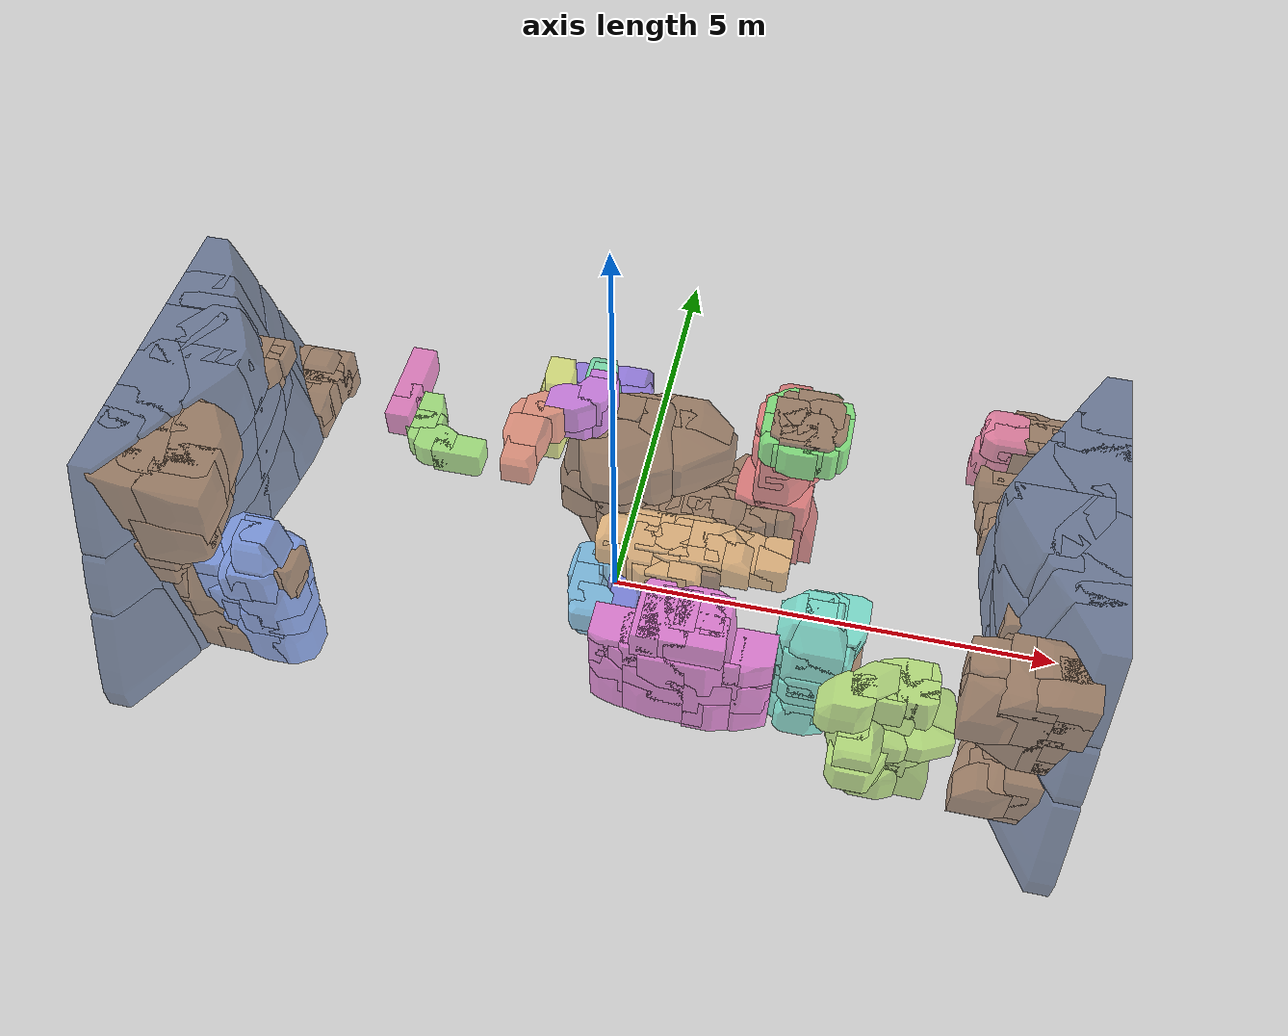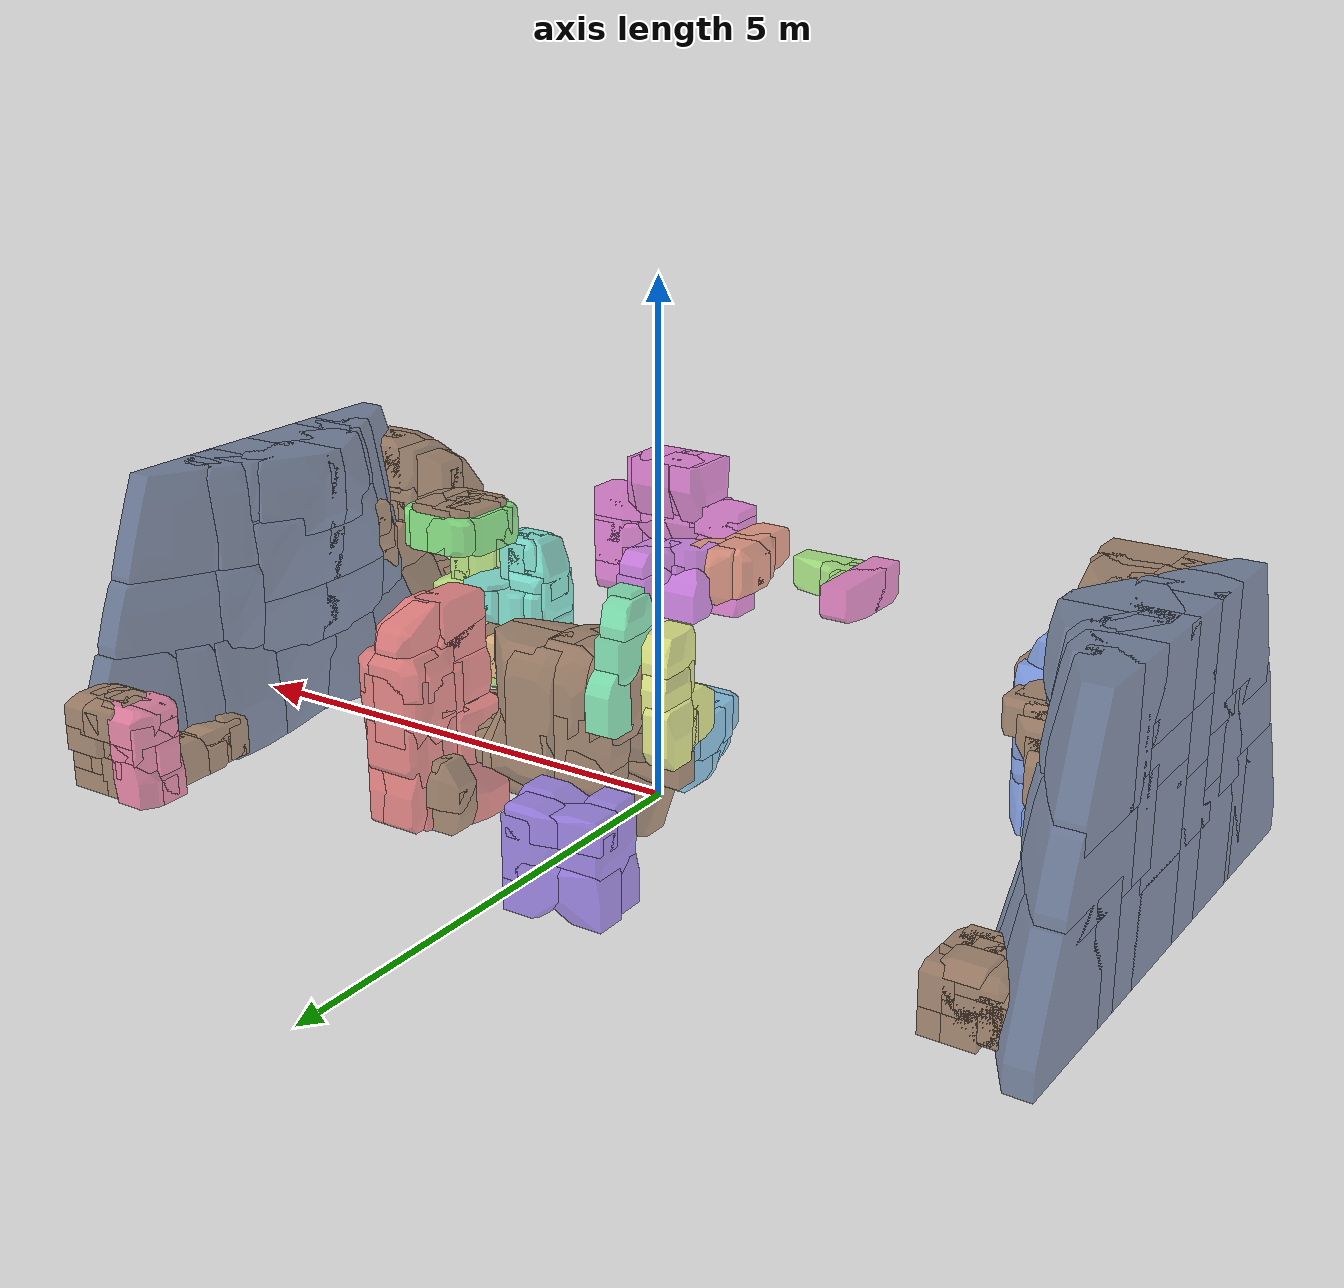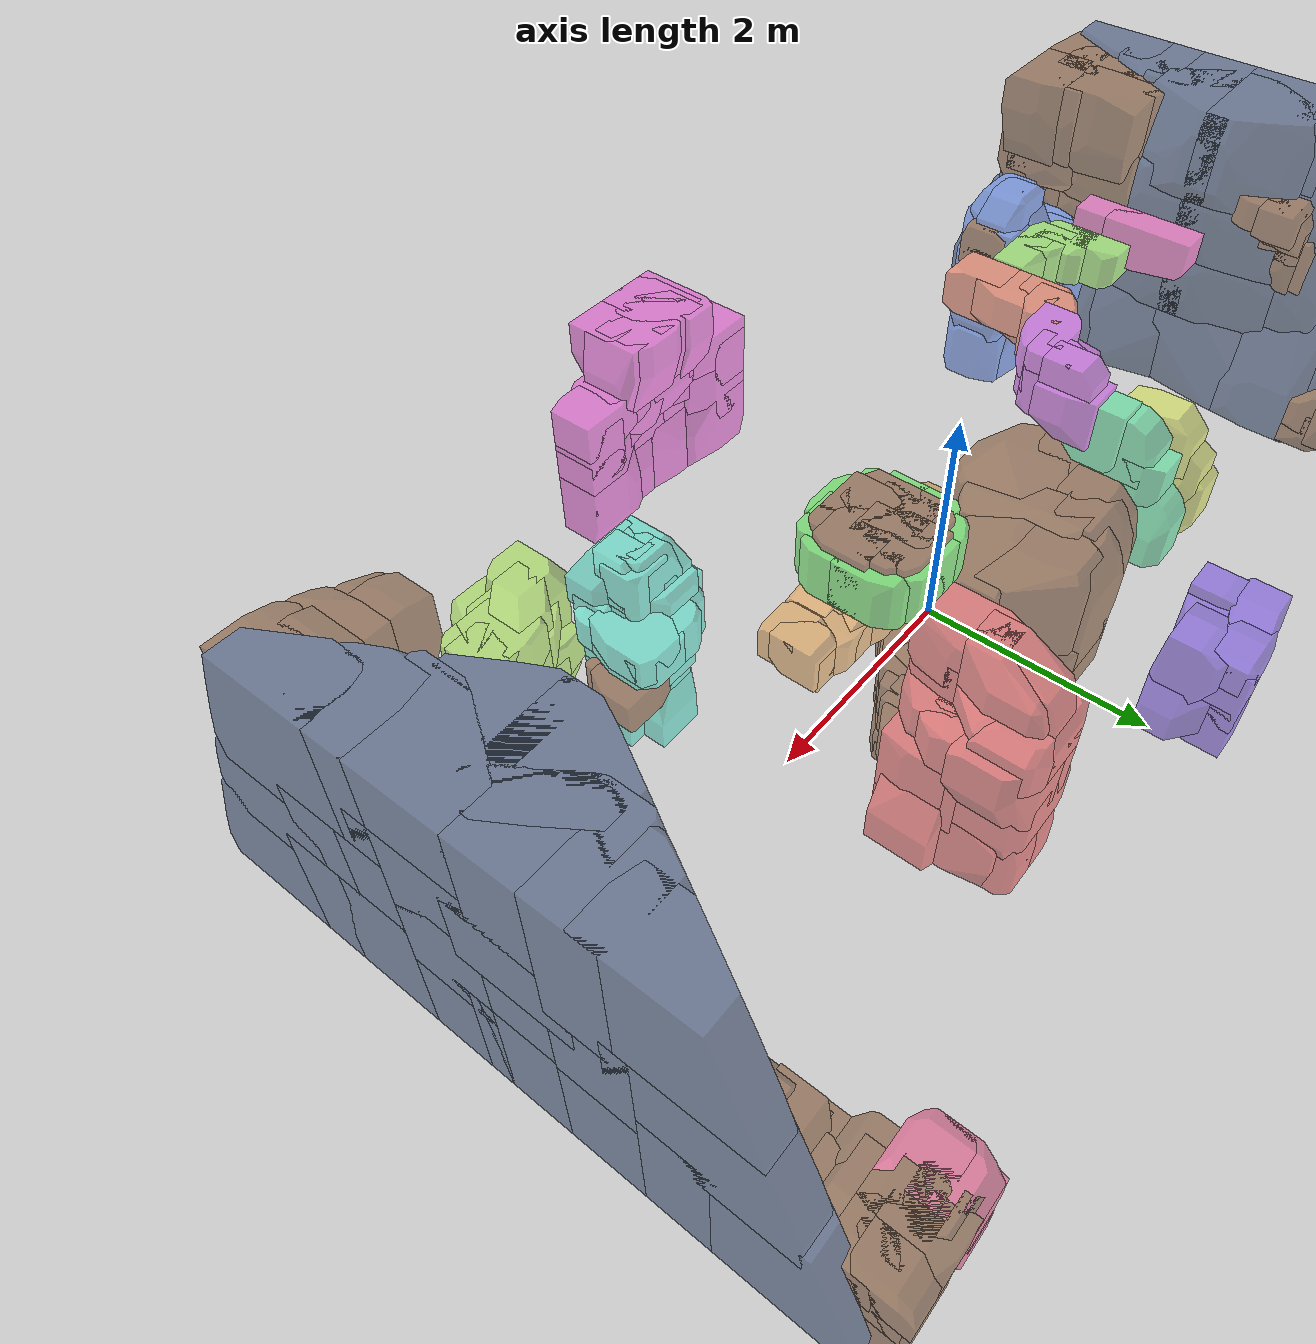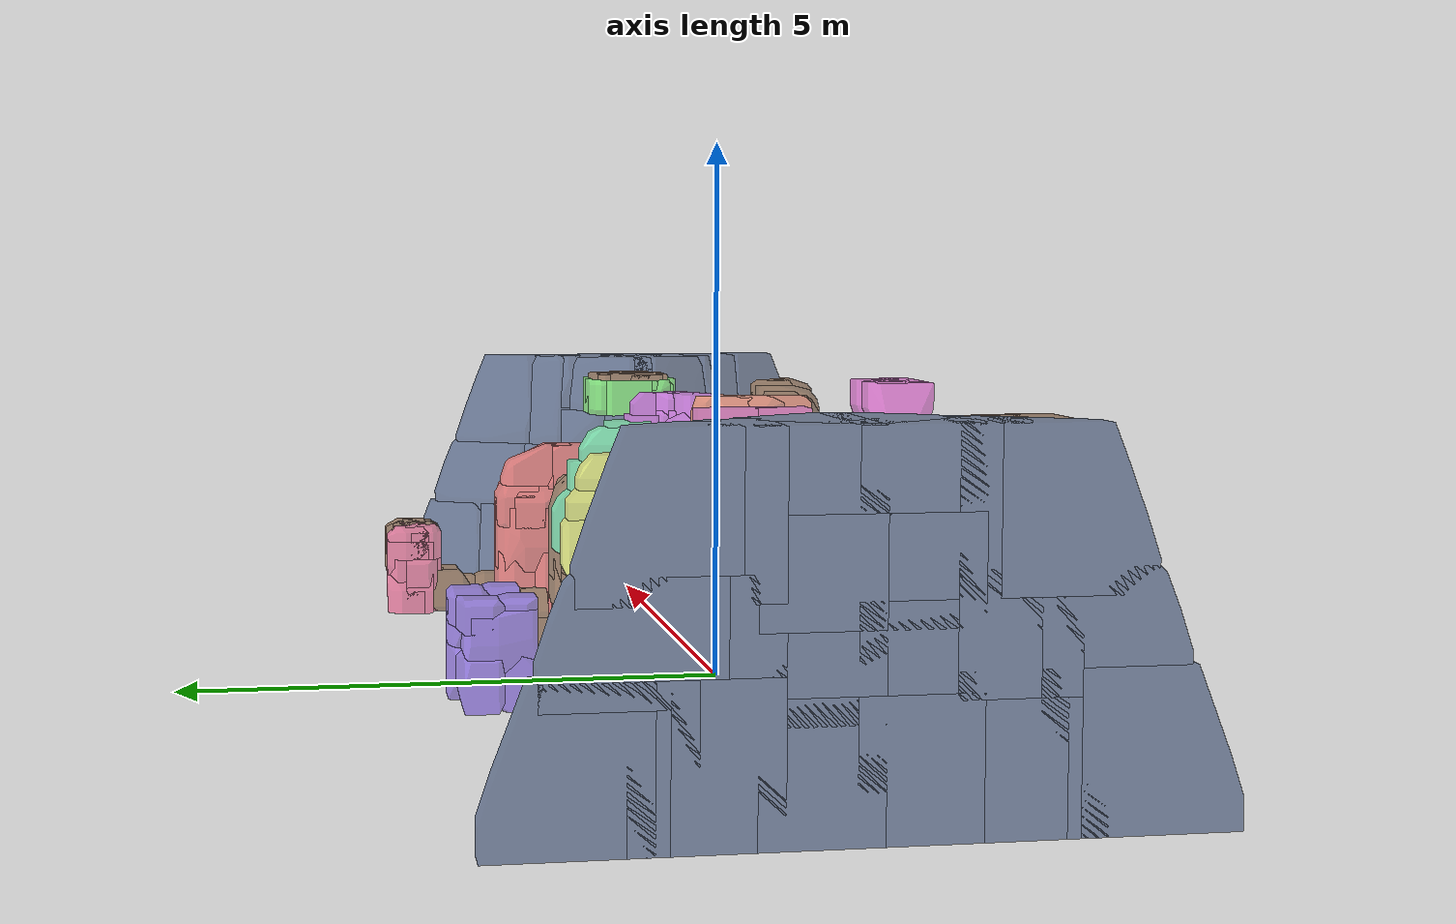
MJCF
<?xml version="1.0" ?>
<mujoco model="sample_0021_decomposition">
  <compiler angle="radian"/>
  <option timestep="0.01" gravity="0 0 0"/>
  <asset>
    <texture type="skybox" builtin="gradient" rgb1="1 1 1" rgb2="0.72 0.82 0.95" width="512" height="512"/>
    <mesh name="entity_00_hull_00_mesh" vertex="1.45 0.75 0.4 1.45 0.75 0.9 1.45 1 0.4 1.45 1 0.9 1.5 0.8 1 1.5 1.25 0.75 1.5 1.25 1 1.55 0.75 1 1.55 1.35 0.75 1.55 1.35 1 1.75 1.35 0.4 2 0.75 0.4 2 0.75 1 2 1.35 0.4 2 1.35 1 2.05 0.95 0.65 2.05 0.95 0.9 2.05 1 1 2.05 1.05 0.4 2.05 1.3 0.4 2.05 1.3 1" face="2 10 8 18 11 15 7 1 4 16 17 12 5 2 8 2 1 0 2 1 3 18 19 13 18 11 0 18 10 13 18 2 0 18 2 10 7 11 0 7 11 12 7 1 0 16 19 20 16 18 19 16 17 20 16 18 15 16 11 12 16 11 15 6 1 3 6 1 4 14 19 13 14 19 20 9 10 13 9 14 13 9 10 8 9 17 20 9 17 12 9 7 12 9 6 4 9 7 4 9 14 20 5 9 8 5 9 6 5 2 3 5 6 3"/>
    <mesh name="entity_00_hull_01_mesh" vertex="1.1 0.9 -0.05 1.1 0.9 0.2 1.1 1.2 -0.05 1.1 1.2 0.2 1.15 0.85 -0.05 1.15 1.4 -0.05 1.15 1.4 0.25 1.2 0.8 0 1.2 0.8 0.4 1.25 0.8 -0.05 1.25 0.8 0.55 1.25 1.4 0.55 1.4 0.75 0 1.4 0.75 0.45 1.55 1.4 -0.05 1.55 1.4 0.55 1.65 0.75 0 1.65 0.75 0.45 1.7 0.8 -0.05 1.7 0.8 0.55 1.7 1.05 -0.05 1.7 1.05 0.55 1.7 1.4 0.1 1.7 1.4 0.35" face="6 11 3 20 14 22 21 23 15 7 9 12 8 13 10 8 1 10 4 7 9 1 2 0 1 2 3 11 1 10 11 1 3 6 14 5 6 23 15 6 11 15 6 14 22 6 23 22 6 2 5 6 2 3 16 9 18 16 9 12 16 19 18 16 17 19 13 19 10 13 17 19 13 16 12 13 16 17 21 11 15 21 19 10 21 11 10 21 23 22 21 20 18 21 19 18 21 20 22 8 13 12 8 7 12 4 2 0 4 20 18 4 9 18 4 2 5 4 14 5 4 20 14 4 1 0 4 8 7 4 8 1"/>
    <mesh name="entity_00_hull_02_mesh" vertex="1.2 0.8 0.65 1.2 0.8 0.9 1.2 0.85 1 1.2 0.9 0.6 1.2 1.1 1 1.2 1.15 0.6 1.2 1.15 0.85 1.25 0.8 0.35 1.25 0.8 1 1.25 1.35 1 1.25 1.4 0.35 1.25 1.4 0.95 1.3 1.4 1 1.4 0.75 0.75 1.4 0.75 1 1.55 1.4 0.35 1.65 0.75 0.75 1.65 0.75 1 1.7 0.8 0.35 1.7 0.8 1 1.7 1.05 0.35 1.7 1.4 0.4 1.7 1.4 1 1.75 1.05 0.75 1.75 1.05 1 1.75 1.35 0.75 1.75 1.35 1" face="4 9 11 3 7 0 12 9 11 6 4 11 13 7 0 20 25 21 20 15 21 8 1 2 8 1 14 3 5 10 3 7 10 12 15 10 12 11 10 12 21 22 12 15 21 6 11 10 6 5 10 1 4 2 1 6 5 1 3 0 1 3 5 1 6 4 13 1 0 13 1 14 13 7 18 13 16 18 24 18 23 24 19 18 17 13 14 17 13 16 17 16 18 17 19 18 20 25 23 20 18 23 20 7 10 20 15 10 20 7 18 26 25 23 26 24 23 26 21 22 26 25 21 8 17 14 8 4 2 8 12 22 8 4 9 8 26 22 8 26 24 8 12 9 8 24 19 8 17 19"/>
    <mesh name="entity_00_hull_03_mesh" vertex="1.6 1.35 0.8 1.6 1.35 1.45 1.6 1.6 0.8 1.6 1.6 1.45 1.65 1.9 0.8 1.65 1.9 1.45 1.8 1.3 1.05 1.8 1.3 1.4 1.95 1.35 1.45 1.95 1.9 0.8 1.95 1.9 1.45 2 1.35 0.8 2 1.85 0.8 2.05 1.4 0.8 2.05 1.75 0.8 2.1 1.3 1.4 2.1 1.4 1.45 2.1 1.8 1.2 2.1 1.8 1.45 2.15 1.3 1.05 2.15 1.3 1.35 2.15 1.4 1.4 2.15 1.7 1.05 2.15 1.7 1.4" face="11 13 19 15 8 16 12 17 9 12 17 22 12 22 14 11 6 0 11 6 19 7 6 0 7 1 0 3 2 0 3 1 0 3 2 4 3 5 4 10 8 1 10 3 1 10 16 18 10 3 5 10 8 16 9 5 4 9 10 5 22 14 13 22 13 19 15 6 19 15 7 6 15 20 19 15 7 1 15 8 1 15 21 20 15 21 16 23 16 18 23 21 16 23 20 19 23 22 19 23 21 20 17 10 18 17 9 10 17 23 18 17 23 22 12 11 0 12 2 0 12 2 4 12 11 13 12 14 13 12 9 4"/>
    <mesh name="entity_00_hull_04_mesh" vertex="1.3 1.4 1.05 1.3 1.4 1.3 1.3 1.45 1.45 1.3 1.65 1.05 1.3 1.7 1.15 1.3 1.7 1.45 1.35 1.35 0.8 1.35 1.35 1.4 1.35 1.4 1.45 1.35 1.65 0.8 1.35 1.8 1.2 1.35 1.8 1.45 1.4 1.85 0.8 1.4 1.85 1.45 1.45 1.35 1.45 1.5 1.9 0.8 1.5 1.9 1.45 1.8 1.35 0.8 1.8 1.35 1.45 1.85 1.4 0.8 1.85 1.4 1.1 1.85 1.65 1.45 1.85 1.9 0.8 1.85 1.9 1.45" face="12 3 4 1 7 2 20 21 18 9 12 3 10 12 4 8 14 7 8 7 2 16 22 15 16 22 23 16 12 15 16 12 13 14 17 6 14 17 18 14 7 6 1 3 0 1 5 2 1 3 4 1 5 4 1 7 6 1 6 0 20 22 19 20 21 23 20 22 23 20 17 19 20 17 18 9 17 19 9 22 19 9 22 15 9 17 6 9 12 15 9 3 0 9 6 0 11 16 23 11 5 2 11 21 23 11 21 18 11 16 13 11 8 2 11 14 18 11 8 14 11 12 13 11 10 12 11 5 4 11 10 4"/>
    <mesh name="entity_00_hull_05_mesh" vertex="1.4 0.75 1.1 1.4 0.75 1.35 1.4 0.8 1.45 1.4 1 1.1 1.4 1.05 1.2 1.4 1.05 1.45 1.45 0.75 0.9 1.45 0.75 1.45 1.45 0.8 0.8 1.45 1.25 0.8 1.45 1.3 0.9 1.45 1.3 1.45 1.7 0.75 0.9 1.7 1.3 0.9 1.7 1.3 1.45 1.75 0.75 0.95 1.75 0.75 1.45 1.8 0.75 1.05 1.8 0.75 1.3 1.8 0.8 0.8 1.8 1.25 0.8 1.9 1.25 1.45 1.95 0.95 1.45 1.95 1.2 1.45 1.95 1.25 1.1 1.95 1.25 1.4 2 0.95 1.15 2 0.95 1.4 2 1.2 1.15 2 1.2 1.4" face="20 28 24 6 8 0 13 20 24 17 19 26 7 1 2 16 27 18 15 12 19 15 17 19 22 16 27 21 25 14 20 28 26 20 19 26 5 1 0 5 3 0 5 3 4 5 1 2 5 11 10 5 4 10 9 20 19 9 8 19 9 3 4 9 4 10 9 3 0 9 8 0 13 11 14 13 11 10 13 9 20 13 9 10 12 8 19 12 6 8 17 27 26 17 27 18 15 1 0 15 6 0 15 17 18 15 12 6 15 16 7 15 16 18 15 7 1 25 13 14 25 13 24 21 22 16 21 5 2 21 11 14 21 5 11 21 7 2 21 16 7 21 22 23 29 25 24 29 28 24 29 28 26 29 27 26 29 22 23 29 22 27 29 21 23 29 21 25"/>
    <mesh name="entity_00_hull_06_mesh" vertex="1.55 1.05 0.8 1.55 1.05 1.45 1.55 1.4 0.8 1.55 1.4 1.45 1.6 1.45 1.15 1.6 1.45 1.45 1.75 1 1.1 1.75 1 1.4 1.8 1.5 1.05 1.8 1.5 1.4 1.85 1.05 0.8 1.85 1.4 0.8 1.85 1.45 1.45 1.9 1.05 1.45 1.95 1.15 1.45 1.95 1.4 1.45 2 1 1.1 2 1 1.4 2.05 1.05 1.15 2.05 1.05 1.4 2.1 1.15 1.05 2.1 1.15 1.35 2.1 1.25 1.4 2.1 1.5 1.05 2.1 1.5 1.4" face="10 16 20 18 16 20 4 2 8 13 17 19 13 14 19 22 14 19 22 21 19 12 15 24 23 10 11 23 10 20 2 23 11 2 23 8 2 10 11 2 10 0 6 10 0 6 10 16 18 21 20 18 21 19 17 18 19 17 18 16 9 23 8 9 23 24 4 9 8 4 9 5 3 2 0 3 1 0 3 4 5 3 4 2 7 1 0 7 6 0 7 6 16 7 17 16 13 7 1 13 7 17 22 23 20 22 23 24 22 21 20 15 22 24 15 22 14 12 3 1 12 3 5 12 13 1 12 13 14 12 15 14 12 9 24 12 9 5"/>
    <mesh name="entity_00_hull_07_mesh" vertex="1.3 1.3 1.05 1.3 1.3 1.35 1.3 1.6 1.05 1.3 1.6 1.35 1.35 1.25 1.4 1.35 1.55 1.4 1.45 1.1 0.95 1.45 1.1 1.45 1.45 1.45 1.45 1.5 1.05 0.8 1.5 1.05 1.45 1.5 1.45 0.8 1.5 1.55 1.45 1.55 1.55 0.9 1.55 1.6 1.05 1.55 1.6 1.35 1.75 1.05 0.8 1.75 1.05 1.45 1.75 1.45 0.8 1.75 1.55 1.45 1.8 1.2 1 1.8 1.2 1.45 1.8 1.3 0.9 1.8 1.45 1.45 1.8 1.55 0.9 1.8 1.55 1.4" face="6 9 0 4 1 7 25 15 19 13 11 2 22 16 20 5 12 3 5 8 12 23 25 19 6 1 7 6 1 0 3 1 0 3 2 0 10 6 7 10 6 9 15 12 19 15 12 3 11 2 0 11 9 0 16 10 17 16 10 9 16 11 9 16 11 18 16 21 20 16 21 17 14 25 24 14 25 15 14 3 2 14 15 3 13 14 24 13 14 2 13 11 18 13 24 18 22 16 18 22 24 18 5 3 1 5 4 1 5 8 7 5 4 7 23 10 7 23 10 17 23 21 17 23 12 19 23 8 7 23 8 12 23 21 20 23 22 20 23 25 24 23 22 24"/>
    <mesh name="entity_00_hull_08_mesh" vertex="1.6 1.5 -0.05 1.6 1.5 0.6 1.6 1.75 -0.05 1.6 1.75 0.6 1.65 1.85 -0.05 1.65 1.85 0.6 1.7 1.9 0 1.7 1.9 0.3 1.95 1.85 -0.05 1.95 1.9 0 1.95 1.9 0.3 2 1.5 -0.05 2 1.5 0.6 2 1.8 -0.05 2 1.85 0 2 1.85 0.6" face="12 1 0 12 11 0 3 1 0 3 2 0 9 14 15 9 10 15 9 8 4 9 4 6 13 12 11 13 12 15 13 14 15 13 11 0 13 2 0 13 2 4 13 8 4 13 9 14 13 9 8 5 2 4 5 3 2 5 12 1 5 12 15 5 3 1 7 9 10 7 9 6 7 5 15 7 10 15 7 4 6 7 5 4"/>
    <mesh name="entity_00_hull_09_mesh" vertex="1.6 1.15 -0.05 1.6 1.15 0.6 1.6 1.4 -0.05 1.6 1.4 0.6 1.65 1.7 -0.05 1.65 1.7 0.6 1.8 1.1 -0.05 1.8 1.1 0.6 1.8 1.75 0.2 1.8 1.75 0.45 2 1.7 -0.05 2 1.7 0.6 2.05 1.1 -0.05 2.05 1.1 0.6 2.05 1.4 -0.05 2.05 1.4 0.6 2.05 1.75 0.2 2.05 1.75 0.45" face="14 16 10 17 11 15 4 16 8 4 16 10 7 6 0 7 1 0 7 6 12 7 13 12 2 14 12 2 6 0 2 6 12 2 4 10 2 14 10 3 5 4 3 2 4 3 13 15 3 11 15 3 7 1 3 7 13 3 11 5 3 1 0 3 2 0 9 4 8 9 5 4 17 16 8 17 9 8 17 11 5 17 9 5 17 13 15 17 13 12 17 14 12 17 14 16"/>
    <mesh name="entity_00_hull_10_mesh" vertex="1.45 0.75 1.25 1.45 0.75 1.75 1.45 1.3 1.75 1.45 1.4 1.25 1.45 1.4 1.65 1.5 1.35 1.75 1.7 0.75 1.25 1.7 0.75 1.75 1.7 1.4 1.25 1.7 1.4 1.65 1.75 0.75 1.35 1.75 0.75 1.6 1.8 0.8 1.25 1.8 0.8 1.75 1.85 1.05 1.35 1.85 1.05 1.75 1.85 1.1 1.25 1.85 1.35 1.25 1.85 1.35 1.75" face="12 16 14 12 6 10 5 4 2 11 7 13 15 17 16 15 17 18 15 16 14 4 1 0 4 3 0 4 2 1 13 15 14 13 12 14 7 2 1 7 5 18 7 15 18 7 13 15 7 5 2 8 3 0 8 12 16 8 17 16 8 6 0 8 12 6 9 4 3 9 8 3 9 17 18 9 8 17 9 5 18 9 5 4 11 1 0 11 6 0 11 6 10 11 7 1 11 13 12 11 12 10"/>
    <mesh name="entity_00_hull_11_mesh" vertex="1.45 0.75 1.55 1.45 0.75 2 1.45 0.8 2.05 1.45 1.25 2.05 1.45 1.35 1.55 1.45 1.35 2 1.5 1.35 2.05 1.75 0.75 1.55 1.75 0.8 2.05 1.8 0.75 1.65 1.8 0.75 2 1.8 0.8 1.55 1.8 0.85 2.05 1.8 1.35 2.05 1.85 1.05 1.55 1.85 1.05 1.8 1.85 1.1 1.95 1.85 1.35 1.55 1.85 1.35 1.95" face="15 16 10 12 16 10 12 8 10 3 6 5 11 9 7 11 9 14 8 1 2 8 1 10 9 7 0 9 1 0 9 1 10 15 9 10 15 9 14 18 17 4 18 5 4 18 6 13 18 6 5 18 17 14 18 15 14 18 15 16 18 12 13 18 12 16 3 4 0 3 5 4 3 1 0 3 1 2 3 8 2 3 6 13 3 12 13 3 12 8 11 4 0 11 17 14 11 17 4 11 7 0"/>
    <mesh name="entity_00_hull_12_mesh" vertex="1.55 1.15 1.45 1.55 1.15 2.05 1.55 1.4 1.45 1.55 1.4 2.05 1.55 1.45 1.7 1.55 1.45 1.95 1.6 1.65 1.45 1.6 1.65 1.9 1.65 1.7 1.9 1.65 1.75 1.85 1.65 1.8 1.45 1.65 1.8 1.7 1.85 1.15 1.45 1.85 1.15 2.05 1.85 1.4 2.05 1.9 1.7 1.9 1.9 1.75 1.85 1.9 1.8 1.45 1.9 1.8 1.7 1.95 1.4 1.5 1.95 1.4 1.85 1.95 1.45 1.45 1.95 1.7 1.45 1.95 1.7 1.85" face="12 21 19 6 2 4 23 16 18 23 16 15 23 14 15 7 11 9 7 5 3 7 3 8 7 8 9 13 12 0 13 1 0 20 13 12 20 12 19 3 13 1 3 14 13 3 14 15 3 8 15 11 17 10 11 18 17 16 8 15 16 8 9 16 11 18 16 11 9 23 20 13 23 14 13 5 1 0 5 2 0 5 2 4 5 3 1 22 17 10 22 12 21 22 6 10 22 12 0 22 2 0 22 6 2 22 23 20 22 20 19 22 21 19 22 18 17 22 23 18 7 11 10 7 6 10 7 5 4 7 6 4"/>
    <mesh name="entity_00_hull_13_mesh" vertex="1.5 1.15 1.45 1.5 1.15 2.05 1.5 1.4 2.05 1.5 1.75 1.45 1.5 1.75 1.85 1.55 1.8 1.8 1.6 1.75 1.9 1.6 1.8 1.85 1.6 1.85 1.45 1.6 1.85 1.7 1.75 1.15 1.45 1.75 1.15 2.05 1.75 1.4 2.05 1.85 1.45 1.45 1.85 1.45 1.9 1.85 1.75 1.9 1.85 1.8 1.85 1.85 1.85 1.45 1.85 1.85 1.7" face="5 7 9 5 7 4 6 2 4 6 7 4 17 3 0 17 10 0 17 10 13 17 3 8 11 10 0 11 1 0 14 10 13 14 11 10 12 14 15 12 14 11 9 17 8 9 18 17 2 3 0 2 1 0 2 4 3 2 11 1 2 12 11 16 17 13 16 14 13 16 18 17 16 14 15 16 9 18 16 7 9 5 3 8 5 4 3 5 9 8 6 12 15 6 2 12 6 16 15 6 16 7"/>
    <mesh name="entity_00_hull_14_mesh" vertex="1.35 1.45 0.55 1.35 1.45 1 1.35 1.75 0.55 1.35 1.75 1 1.4 1.5 0.4 1.4 1.8 0.4 1.4 1.85 0.65 1.4 1.85 0.9 1.45 1.45 0.4 1.45 1.9 0.6 1.45 1.9 0.95 1.5 1.9 0.55 1.5 1.9 1 1.75 1.4 0.5 1.75 1.4 1 1.95 1.9 0.55 1.95 1.9 1 2 1.4 0.5 2 1.45 0.4 2 1.8 0.4 2.05 1.4 0.55 2.05 1.4 1 2.05 1.8 0.55 2.05 1.8 1" face="11 5 9 22 15 19 3 10 12 4 8 0 13 8 0 6 2 5 6 5 9 17 18 20 7 3 10 11 12 16 11 10 9 11 15 16 11 10 12 11 5 19 11 15 19 22 18 20 22 18 19 22 21 20 22 23 21 22 15 16 22 23 16 3 14 1 3 23 16 3 12 16 3 14 21 3 23 21 3 1 0 3 2 0 4 8 18 4 5 19 4 18 19 4 2 0 4 2 5 13 14 1 13 1 0 17 13 14 17 14 21 17 21 20 17 8 18 17 13 8 7 10 9 7 6 9 7 3 2 7 6 2"/>
    <mesh name="entity_00_hull_15_mesh" vertex="1.75 0.8 -0.05 1.75 0.8 0.6 1.75 1.35 -0.05 1.75 1.35 0.6 2 0.8 0.6 2 1.35 -0.05 2 1.35 0.6 2.05 1.05 0.6 2.05 1.3 0.6 2.15 0.8 -0.05 2.15 0.8 0.25 2.15 1.3 -0.05 2.15 1.3 0.25" face="10 7 4 12 6 8 3 2 0 3 1 0 5 2 0 5 9 0 5 11 9 6 4 1 6 3 1 6 7 8 6 7 4 6 3 2 6 5 2 10 9 0 10 1 0 10 4 1 12 5 11 12 6 5 12 11 9 12 10 9 12 7 8 12 10 7"/>
    <mesh name="entity_00_hull_16_mesh" vertex="1.45 0.75 0 1.45 0.75 0.6 1.45 1 0 1.45 1 0.6 1.5 0.75 -0.05 1.5 1.05 -0.05 1.5 1.05 0.6 1.8 1.05 -0.05 1.85 1.05 0 1.95 1.05 0.15 1.95 1.05 0.6 2 0.75 -0.05 2 0.75 0.6 2 1 -0.05 2 1 0.6" face="7 8 13 9 8 13 2 4 0 2 4 5 12 4 0 12 1 0 12 4 11 14 13 11 14 12 11 3 12 1 3 14 10 3 6 10 3 14 12 3 1 0 3 2 0 3 2 5 3 6 5 7 4 11 7 4 5 7 13 11 9 6 10 9 6 5 9 7 5 9 7 8 9 14 10 9 14 13"/>
    <mesh name="entity_00_hull_17_mesh" vertex="1.65 1.55 1.4 1.65 1.55 1.65 1.65 1.6 1.3 1.65 1.85 1.3 1.65 1.85 1.65 1.7 1.5 1.65 1.7 1.6 1.25 1.7 1.9 1.25 1.7 1.9 1.5 1.75 1.45 1.25 1.75 1.45 1.6 1.85 1.4 1.25 1.85 1.4 1.5 1.95 1.5 1.65 1.95 1.85 1.65 1.95 1.9 1.25 1.95 1.9 1.5 2 1.55 1.65 2 1.8 1.65 2.05 1.45 1.6 2.05 1.85 1.25 2.05 1.85 1.55 2.1 1.4 1.25 2.1 1.4 1.5 2.1 1.45 1.55 2.1 1.8 1.25 2.1 1.8 1.55" face="2 6 9 2 9 0 23 24 19 17 13 19 16 14 21 2 6 7 2 3 7 2 1 0 2 4 1 2 4 3 8 4 3 8 3 7 11 25 22 11 20 25 11 6 7 11 6 9 11 15 7 11 20 15 10 11 9 10 11 12 23 25 22 23 25 26 23 24 26 23 10 12 23 10 19 23 11 12 23 11 22 21 25 26 21 20 25 17 24 26 17 24 19 17 18 26 5 1 0 5 9 0 5 10 9 5 10 19 5 13 19 14 4 1 14 5 1 14 17 18 14 17 13 14 5 13 14 18 26 14 21 26 16 20 15 16 21 20 16 15 7 16 8 7 16 8 4 16 14 4"/>
    <mesh name="entity_00_hull_18_mesh" vertex="1.55 1.15 1.25 1.55 1.15 1.65 1.55 1.45 1.25 1.55 1.45 1.65 1.6 1.65 1.25 1.6 1.65 1.65 1.65 1.75 1.4 1.65 1.75 1.65 1.7 1.7 1.3 1.85 1.15 1.25 1.85 1.15 1.65 1.9 1.75 1.4 1.9 1.75 1.65 1.95 1.45 1.65 1.95 1.7 1.3 1.95 1.7 1.65 2 1.4 1.6 2.05 1.4 1.25 2.05 1.4 1.55 2.05 1.65 1.25 2.05 1.65 1.55" face="8 4 6 12 20 15 16 10 18 16 10 13 14 11 19 2 9 0 2 19 17 2 9 17 2 19 4 3 2 0 3 1 0 20 19 17 20 18 17 10 9 17 10 18 17 10 9 0 10 1 0 5 2 4 5 3 2 5 4 6 5 7 6 12 20 19 12 11 19 12 5 7 12 10 13 12 3 1 12 10 1 12 13 15 12 5 3 12 7 6 12 11 6 16 20 18 16 13 15 16 20 15 14 19 4 14 8 4 14 11 6 14 8 6"/>
    <mesh name="entity_00_hull_19_mesh" vertex="1.55 1.15 0.4 1.55 1.15 1 1.55 1.4 0.4 1.55 1.4 1 1.6 1.65 0.5 1.6 1.65 1 1.65 1.65 0.4 1.8 1.1 0.4 1.8 1.1 1 1.9 1.65 0.4 1.95 1.65 0.55 1.95 1.65 1 2 1.6 0.55 2 1.6 1 2.05 1.1 0.4 2.05 1.1 1 2.05 1.4 0.4 2.05 1.4 1" face="12 16 9 2 6 4 10 12 9 8 7 0 8 1 0 8 7 14 8 15 14 17 11 13 17 8 1 17 3 1 17 8 15 17 3 5 17 11 5 17 12 13 17 12 16 17 16 14 17 15 14 2 7 0 2 16 14 2 7 14 2 16 9 2 6 9 2 1 0 2 3 1 2 5 4 2 3 5 10 6 9 10 5 4 10 6 4 10 11 5 10 11 13 10 12 13"/>
    <mesh name="entity_00_hull_20_mesh" vertex="1.3 1.2 0.4 1.3 1.2 1 1.3 1.45 0.4 1.3 1.45 1 1.4 1.65 0.6 1.4 1.65 1 1.45 1.65 0.45 1.5 1.15 0.4 1.5 1.15 1 1.75 1.15 0.4 1.75 1.15 1 1.75 1.45 0.4 1.75 1.65 0.45 1.8 1.35 0.75 1.8 1.35 1 1.8 1.4 0.5 1.8 1.65 0.5 1.8 1.65 1" face="2 6 4 15 9 13 11 16 12 6 5 4 6 16 17 6 5 17 6 16 12 14 9 10 14 9 13 8 5 17 8 14 17 8 3 1 8 3 5 8 14 10 2 5 4 2 3 5 2 3 1 2 1 0 15 16 17 15 14 13 15 14 17 11 15 16 11 15 9 11 6 12 11 2 6 7 9 10 7 8 10 7 2 0 7 11 9 7 11 2 7 1 0 7 8 1"/>
    <mesh name="entity_00_hull_21_mesh" vertex="1.35 1.55 1.25 1.35 1.55 1.55 1.35 1.8 1.25 1.35 1.85 1.3 1.35 1.85 1.55 1.4 1.5 1.25 1.4 1.5 1.6 1.4 1.85 1.25 1.45 1.5 1.65 1.45 1.8 1.65 1.5 1.85 1.65 1.5 1.9 1.25 1.5 1.9 1.5 1.55 1.9 1.55 1.65 1.5 1.25 1.85 1.5 1.4 1.85 1.5 1.65 1.85 1.85 1.65 1.9 1.65 1.25 1.9 1.65 1.55 1.9 1.9 1.25 1.9 1.9 1.55" face="14 15 18 12 13 4 7 3 2 7 3 11 10 9 4 10 13 4 19 16 15 19 15 18 3 2 0 3 1 0 3 1 4 6 16 8 6 14 5 6 16 15 6 14 15 6 1 4 6 9 8 6 9 4 6 5 0 6 1 0 12 3 4 12 3 11 21 20 11 21 12 11 21 12 13 21 16 17 21 19 16 21 20 18 21 19 18 7 5 0 7 20 18 7 20 11 7 14 18 7 2 0 7 14 5 10 16 17 10 16 8 10 9 8 10 21 13 10 21 17"/>
    <mesh name="entity_00_hull_22_mesh" vertex="1.3 1.45 1.25 1.3 1.45 1.5 1.3 1.75 1.25 1.3 1.75 1.5 1.35 1.75 1.55 1.4 1.45 1.6 1.4 1.7 1.6 1.5 1.15 1.25 1.5 1.15 1.65 1.5 1.7 1.65 1.6 1.75 1.25 1.6 1.75 1.55 1.75 1.15 1.25 1.75 1.15 1.65 1.8 1.35 1.25 1.8 1.65 1.25 1.8 1.7 1.3 1.85 1.45 1.35 1.85 1.45 1.65 1.85 1.7 1.35 1.85 1.7 1.65" face="5 1 8 14 12 17 16 10 15 16 19 10 16 19 15 4 6 9 1 8 7 1 7 0 13 8 7 13 12 7 13 18 17 13 12 17 20 13 18 20 9 8 20 13 8 10 7 0 10 2 0 10 14 15 10 12 7 10 14 12 6 9 8 6 5 8 19 18 17 19 20 18 19 14 15 19 14 17 11 19 20 11 19 10 3 1 0 3 2 0 4 3 1 4 6 5 4 5 1 4 10 2 4 11 10 4 3 2 4 20 9 4 11 20"/>
    <mesh name="entity_00_hull_23_mesh" vertex="1.4 1.55 0.1 1.4 1.55 0.6 1.4 1.8 0.1 1.4 1.8 0.6 1.4 1.85 0.3 1.4 1.85 0.55 1.45 1.5 -0.05 1.45 1.5 0.6 1.45 1.85 -0.05 1.45 1.85 0.6 1.45 1.9 0.05 1.45 1.9 0.3 1.5 1.9 0 1.75 1.5 0.6 1.75 1.9 0.3 1.8 1.5 -0.05 1.8 1.5 0.5 1.8 1.9 0 1.8 1.9 0.25 1.85 1.55 -0.05 1.85 1.55 0.6 1.85 1.85 -0.05 1.85 1.85 0.6" face="2 4 10 8 2 10 12 8 10 3 5 9 11 5 9 14 18 22 16 13 20 20 21 22 20 21 19 8 2 0 8 6 0 15 21 19 15 8 6 15 8 21 7 1 0 7 6 0 18 21 22 18 17 21 12 8 21 12 17 21 3 2 0 3 1 0 3 2 4 3 5 4 11 5 4 11 4 10 13 20 22 13 7 1 13 9 22 13 3 1 13 3 9 14 18 17 14 12 10 14 11 10 14 12 17 14 9 22 14 11 9 16 15 6 16 7 6 16 13 7 16 20 19 16 15 19"/>
    <mesh name="entity_00_hull_24_mesh" vertex="1.25 1.2 0.2 1.25 1.2 0.45 1.25 1.45 0.2 1.25 1.45 0.45 1.3 1.2 -0.05 1.3 1.2 0.6 1.3 1.45 -0.05 1.3 1.45 0.6 1.4 1.75 -0.05 1.4 1.75 0.6 1.5 1.15 -0.05 1.5 1.15 0.6 1.65 1.75 -0.05 1.65 1.75 0.6 1.75 1.65 -0.05 1.75 1.7 0.3 1.75 1.7 0.6 1.8 1.15 -0.05 1.8 1.15 0.6 1.8 1.4 -0.05 1.8 1.4 0.6" face="1 11 5 2 6 8 10 4 0 7 9 3 15 12 14 15 19 14 2 1 0 2 1 3 2 6 4 2 4 0 2 9 8 2 9 3 10 6 8 10 12 8 10 19 17 10 6 4 10 19 14 10 12 14 10 18 17 10 18 11 10 1 11 10 1 0 7 1 3 7 1 5 20 18 17 20 19 17 15 20 16 15 20 19 13 18 11 13 7 5 13 11 5 13 20 16 13 7 9 13 20 18 13 15 16 13 15 12 13 12 8 13 9 8"/>
    <mesh name="entity_01_hull_00_mesh" vertex="-3.5 -1.7 0.4 -3.5 -1.7 0.8 -3.5 -1.65 0.9 -3.5 -1.3 0.4 -3.5 -1.2 0.6 -3.5 -1.2 0.9 -3.45 -1.85 0.6 -3.45 -1.85 0.85 -3.45 -1.8 0.9 -3.45 -1.25 0.4 -3.45 -1.2 0.55 -3.2 -1.85 0.6 -3.2 -1.85 0.85 -3.2 -1.7 0.4 -3.15 -1.25 0.4 -3.1 -1.8 0.65 -3.1 -1.8 0.9 -3.1 -1.2 0.55 -3.1 -1.2 0.9 -3.05 -1.75 0.6 -3.05 -1.75 0.9 -3.05 -1.65 0.4 -3.05 -1.35 0.4 -3.05 -1.3 0.45 -3.05 -1.25 0.55 -3.05 -1.25 0.9 -3 -1.7 0.6 -3 -1.7 0.85 -3 -1.65 0.9 -3 -1.4 0.9 -3 -1.35 0.6 -3 -1.35 0.85" face="1 7 2 9 3 4 8 7 2 10 9 4 23 22 30 23 24 30 23 22 14 23 17 14 23 17 24 11 21 13 31 29 25 19 21 26 19 11 15 19 11 21 27 28 20 1 3 0 1 5 4 1 5 2 1 3 4 21 30 26 21 22 30 21 3 0 21 13 0 21 9 14 21 9 3 21 22 14 17 5 4 17 18 5 17 10 4 17 18 25 17 24 25 17 9 14 17 10 9 31 24 25 31 24 30 16 11 15 16 11 12 16 5 2 16 8 2 16 18 25 16 18 5 16 28 20 16 29 25 16 28 29 16 8 7 16 12 7 6 1 0 6 1 7 6 13 0 6 11 13 6 11 12 6 12 7 27 30 26 27 31 30 27 31 29 27 28 29 27 19 26 27 16 20 27 19 15 27 16 15"/>
    <mesh name="entity_01_hull_01_mesh" vertex="-4.2 -1.65 0.45 -4.2 -1.65 0.85 -4.2 -1.6 0.9 -4.2 -1.35 0.45 -4.2 -1.3 0.6 -4.2 -1.3 0.9 -4.15 -1.65 0.9 -4.15 -1.15 0.9 -4.1 -1.7 0.45 -4.1 -1.7 0.7 -4.1 -1.05 0.9 -4.1 -1 0.45 -4.1 -1 0.85 -4.05 -1.7 0.8 -3.95 -1.7 0.9 -3.85 -1 0.45 -3.8 -1.05 0.9 -3.8 -1 0.55 -3.8 -1 0.85 -3.75 -1.1 0.9 -3.7 -1.7 0.45 -3.7 -1.7 0.9 -3.7 -1.45 0.9 -3.65 -1.65 0.45 -3.65 -1.65 0.7 -3.65 -1.1 0.8 -3.6 -1.45 0.45 -3.6 -1.45 0.8 -3.6 -1.15 0.8 -3.6 -1.1 0.45 -3.6 -1.1 0.7" face="3 4 11 15 17 29 12 7 10 24 27 21 1 9 13 25 30 18 28 22 19 28 25 30 6 1 2 15 23 26 15 29 26 15 8 0 15 3 0 15 3 11 15 23 20 15 8 20 9 14 21 9 20 21 9 14 13 9 8 20 30 18 17 30 17 29 12 15 11 12 15 17 12 18 17 12 10 16 12 18 16 12 5 4 12 4 11 12 7 5 24 23 20 24 20 21 24 23 26 24 27 26 1 8 0 1 9 8 1 3 0 1 5 2 1 3 4 1 5 4 28 22 21 28 27 21 28 19 16 28 18 16 28 25 18 28 29 26 28 27 26 28 30 29 6 22 21 6 5 2 6 10 16 6 19 16 6 14 21 6 7 10 6 7 5 6 22 19 6 14 13 6 1 13"/>
    <mesh name="entity_01_hull_02_mesh" vertex="-3.95 -1.35 1 -3.95 -1.35 1.4 -3.95 -1.3 1.45 -3.95 -1.1 1 -3.95 -1.05 1.15 -3.95 -1.05 1.45 -3.85 -1.5 1.05 -3.85 -1.5 1.4 -3.85 -0.95 1.2 -3.85 -0.95 1.45 -3.8 -1.45 1.45 -3.7 -1.35 1 -3.7 -1.1 1 -3.6 -1.5 1.05 -3.6 -1.5 1.4 -3.55 -1.45 1.05 -3.55 -1.45 1.45 -3.55 -0.95 1.2 -3.55 -0.95 1.45 -3.35 -1.3 1.1 -3.35 -1.3 1.45 -3.35 -1.05 1.1 -3.35 -1.05 1.45" face="3 4 8 1 7 2 10 7 2 15 11 19 15 13 19 15 13 11 16 20 14 17 21 12 21 11 12 21 11 19 20 21 19 20 21 22 3 11 12 3 11 0 5 9 8 5 4 8 13 20 19 13 20 14 1 3 0 1 5 2 1 3 4 1 5 4 6 1 0 6 1 7 6 11 0 6 13 11 6 13 14 6 7 14 16 7 14 16 10 7 17 3 12 17 3 8 18 10 2 18 20 22 18 5 2 18 5 9 18 16 20 18 16 10 18 9 8 18 17 8 18 21 22 18 17 21"/>
    <mesh name="entity_01_hull_03_mesh" vertex="-4.15 -1.65 1 -4.15 -1.65 1.4 -4.15 -1.3 1 -4.15 -1.3 1.4 -4.1 -1.15 1 -4.1 -1.15 1.4 -4.05 -1.1 1.4 -4.05 -1.05 1 -4.05 -1.05 1.35 -3.9 -1.65 1 -3.9 -1.65 1.4 -3.8 -1.05 1 -3.8 -1.05 1.35 -3.75 -1.1 1 -3.75 -1.1 1.4 -3.65 -1.55 1 -3.65 -1.55 1.35 -3.65 -1.45 1.4 -3.65 -1.25 1 -3.65 -1.2 1.1 -3.65 -1.2 1.4" face="10 17 16 19 18 13 8 5 6 10 9 0 10 1 0 10 9 15 10 16 15 19 18 15 19 16 15 19 17 20 19 17 16 8 4 7 8 4 5 3 2 0 3 1 0 3 4 2 3 4 5 11 2 0 11 9 0 11 9 15 11 18 15 11 4 7 11 18 13 11 4 2 11 8 7 11 8 12 14 17 20 14 10 1 14 3 1 14 10 17 14 5 6 14 3 5 14 19 20 14 11 13 14 19 13 14 11 12 14 8 12 14 8 6"/>
    <mesh name="entity_01_hull_04_mesh" vertex="-3.5 -1.85 0 -3.5 -1.85 0.4 -3.5 -1.8 -0.05 -3.5 -1.8 0.6 -3.5 -1.55 -0.05 -3.5 -1.55 0.6 -3.45 -1.25 -0.05 -3.45 -1.25 0.6 -3.4 -1.2 -0.05 -3.4 -1.2 0.2 -3.25 -1.85 0 -3.25 -1.85 0.4 -3.25 -1.8 0.6 -3.2 -1.8 -0.05 -3.2 -1.8 0.55 -3.15 -1.8 0 -3.15 -1.8 0.35 -3.15 -1.25 0.6 -3.15 -1.2 -0.05 -3.15 -1.2 0.2 -3.1 -1.7 0.6 -3.1 -1.3 -0.05 -3.05 -1.7 -0.05 -3.05 -1.65 0.6 -3.05 -1.45 -0.05 -3.05 -1.35 0.6 -3 -1.65 0 -3 -1.65 0.45 -3 -1.6 0.5 -3 -1.4 0 -3 -1.35 0.25 -3 -1.35 0.5" face="31 19 17 22 15 13 25 31 17 18 30 29 21 24 29 21 18 29 11 12 14 20 12 14 10 15 13 16 11 14 27 20 14 27 16 14 23 27 20 23 28 27 22 29 26 22 24 29 9 7 17 9 19 17 9 6 8 9 6 7 4 1 0 4 2 0 4 5 3 4 1 3 4 5 7 4 6 7 18 9 19 18 9 8 18 30 31 18 31 19 21 2 13 21 4 2 21 6 8 21 22 13 21 22 24 21 4 6 21 18 8 11 1 3 11 12 3 10 1 0 10 11 1 10 2 0 10 2 13 16 10 11 16 10 15 27 22 15 27 22 26 27 16 15 28 27 26 28 29 26 28 30 29 28 30 31 23 25 17 23 5 3 23 7 17 23 5 7 23 12 3 23 20 12 23 28 31 23 25 31"/>
    <mesh name="entity_01_hull_05_mesh" vertex="-4.35 -1.35 0.05 -4.35 -1.35 0.35 -4.35 -1.3 0 -4.35 -1.1 0.35 -4.35 -1.05 0 -4.35 -1 0.05 -4.35 -1 0.3 -4.3 -1.5 0.15 -4.3 -1.5 0.5 -4.3 -1.3 -0.05 -4.3 -1 -0.05 -4.25 -1.45 0.65 -4.25 -1.15 0.65 -4.2 -1 0.65 -4.05 -1.5 0.15 -4.05 -1.5 0.5 -4 -1.35 -0.05 -3.95 -1.45 0.65 -3.9 -1 -0.05 -3.85 -1 0.1 -3.85 -1 0.65 -3.75 -1.35 -0.05 -3.75 -1.35 0.65 -3.75 -1.05 -0.05 -3.7 -1.3 0.15 -3.7 -1.3 0.65 -3.7 -1.05 0.15 -3.7 -1.05 0.65" face="16 9 7 6 12 13 6 12 3 19 26 23 18 19 23 10 4 5 25 21 24 25 22 21 9 2 0 9 7 0 26 25 27 26 25 24 26 21 24 26 23 21 6 1 0 6 3 1 6 4 5 6 2 0 6 4 2 8 17 11 8 17 15 8 1 0 8 7 0 8 3 1 8 12 11 8 12 3 14 22 21 14 17 22 14 17 15 14 8 7 14 8 15 14 16 21 14 16 7 20 25 27 20 12 11 20 17 11 20 25 22 20 12 13 20 17 22 19 26 27 19 20 27 10 6 5 10 20 13 10 6 13 10 19 20 10 18 19 10 16 21 10 23 21 10 16 9 10 18 23 10 9 2 10 4 2"/>
    <mesh name="entity_01_hull_06_mesh" vertex="-4.05 -1.7 0.7 -4.05 -1.7 1 -4.05 -1.45 0.7 -4.05 -1.45 1 -3.95 -1.55 1.2 -3.95 -1.2 0.75 -3.95 -1.2 1.2 -3.9 -1.6 1.2 -3.9 -1.1 0.7 -3.9 -1.1 1 -3.85 -1.75 0.7 -3.85 -1.75 0.95 -3.7 -1.75 1.1 -3.7 -1.2 1.2 -3.65 -1.65 1.2 -3.6 -1.1 0.7 -3.6 -1.1 1 -3.5 -1.15 0.7 -3.5 -1.15 0.95 -3.45 -1.75 0.7 -3.45 -1.75 1.1 -3.45 -1.2 0.7 -3.45 -1.2 1 -3.4 -1.65 0.7 -3.4 -1.65 1.2 -3.4 -1.35 0.7 -3.4 -1.3 0.75 -3.4 -1.3 1.2" face="5 2 8 25 26 21 7 1 4 7 12 1 14 7 12 11 12 1 16 13 27 24 19 23 24 19 20 2 1 0 2 1 3 25 24 23 25 24 27 25 26 27 6 1 3 6 1 4 6 2 3 6 5 2 9 6 5 9 5 8 14 13 27 14 6 4 14 24 27 14 6 13 14 7 4 14 24 20 14 12 20 22 26 27 22 26 21 22 17 21 22 17 18 16 22 27 16 22 18 16 6 13 16 9 6 16 15 8 16 9 8 16 17 15 16 17 18 10 15 8 10 2 0 10 25 23 10 19 23 10 2 8 10 25 21 10 17 21 10 17 15 10 19 20 10 12 20 10 11 12 10 1 0 10 11 1"/>
    <mesh name="entity_01_hull_07_mesh" vertex="-4.2 -1.6 0.7 -4.2 -1.6 0.95 -4.2 -1.3 0.7 -4.2 -1.3 0.95 -4.15 -1.65 1.2 -4.15 -1.3 1.2 -4.15 -1.15 0.7 -4.15 -1.15 0.95 -4.1 -1.7 0.7 -4.1 -1.7 1 -4.1 -1.15 1.2 -4.05 -1.05 0.7 -4.05 -1.05 1.2 -3.9 -1.65 1.2 -3.85 -1.7 0.7 -3.85 -1.7 1 -3.8 -1.65 0.75 -3.8 -1.65 1.05 -3.8 -1.05 1.2 -3.75 -1.55 0.7 -3.75 -1.55 1.2 -3.7 -1.4 0.75 -3.7 -1.4 1.2 -3.7 -1.35 0.7 -3.7 -1.15 1.2 -3.7 -1.05 0.7 -3.7 -1.05 1" face="16 14 19 23 19 21 17 13 20 17 13 15 26 24 18 7 10 12 1 2 0 1 2 3 22 19 21 22 20 19 5 1 3 5 1 4 23 2 0 23 25 11 23 14 19 23 8 0 23 6 11 23 8 14 23 6 2 9 1 0 9 8 0 9 1 4 9 13 4 9 13 15 9 8 14 9 15 14 17 20 19 17 16 19 17 15 14 17 16 14 10 12 18 10 24 22 10 22 20 10 5 4 10 13 4 10 24 18 10 13 20 26 25 11 26 12 11 26 12 18 26 22 21 26 23 25 26 23 21 26 24 22 7 2 3 7 6 2 7 12 11 7 6 11 7 5 3 7 10 5"/>
    <mesh name="entity_01_hull_08_mesh" vertex="-3.6 -1.55 0.7 -3.6 -1.55 1.35 -3.6 -1.3 0.7 -3.6 -1.3 1.35 -3.6 -1.25 0.85 -3.6 -1.25 1.15 -3.55 -1.05 1.1 -3.55 -1.05 1.35 -3.5 -1.2 0.7 -3.35 -1.6 1.35 -3.3 -1.65 0.7 -3.3 -1.65 1.3 -3.25 -1.05 1.1 -3.25 -1.05 1.35 -3.15 -1.1 1.1 -3.15 -1.1 1.35 -3.1 -1.2 0.7 -3.1 -1.15 1.05 -3.05 -1.65 0.7 -3.05 -1.65 1.3 -3.05 -1.6 1.35 -3.05 -1.25 0.7 -3.05 -1.2 1.1 -3.05 -1.2 1.35" face="14 12 16 2 8 6 9 11 1 5 3 7 17 21 16 17 14 16 4 2 6 22 17 21 12 8 16 12 8 6 11 10 0 11 1 0 11 10 18 11 19 18 13 12 6 13 7 6 2 21 18 2 10 0 2 10 18 2 8 16 2 21 16 9 20 19 9 11 19 15 20 23 15 9 1 15 3 1 15 3 7 15 13 7 15 9 20 15 13 12 15 14 12 4 1 0 4 3 1 4 2 0 4 5 3 4 7 6 4 5 7 22 21 18 22 19 18 22 20 23 22 20 19 22 15 23 22 15 14 22 17 14"/>
    <mesh name="entity_01_hull_09_mesh" vertex="-3.65 -1.8 0.7 -3.65 -1.8 1.35 -3.65 -1.45 0.7 -3.65 -1.45 1.35 -3.6 -1.35 0.7 -3.6 -1.35 1.3 -3.55 -1.85 0.7 -3.55 -1.85 0.95 -3.4 -1.4 1.35 -3.35 -1.35 1.3 -3.25 -1.85 0.7 -3.25 -1.85 0.95 -3.25 -1.35 0.7 -3.25 -1.35 0.95 -3.15 -1.8 1.35 -3.1 -1.8 0.7 -3.1 -1.8 1.3 -3.1 -1.75 1.35 -3.1 -1.4 0.7 -3.1 -1.4 1.35 -3.05 -1.75 0.7 -3.05 -1.7 1.3 -3.05 -1.45 0.7 -3.05 -1.45 1.3 -3 -1.7 0.85 -3 -1.7 1.1 -3 -1.45 0.85 -3 -1.45 1.1" face="22 18 26 8 3 5 13 9 19 21 16 25 11 16 14 23 27 19 17 16 14 17 21 16 3 2 0 3 1 0 3 2 4 3 5 4 22 20 24 22 26 24 27 18 26 27 18 19 27 26 24 27 25 24 8 9 5 8 9 19 7 1 0 7 6 0 13 5 4 13 9 5 13 12 4 13 12 18 13 18 19 15 22 20 15 2 0 15 2 4 15 12 4 15 6 0 15 6 10 15 22 18 15 12 18 15 20 24 15 25 24 15 16 25 11 6 10 11 7 6 11 14 1 11 7 1 11 15 10 11 15 16 23 27 25 23 21 25 17 14 1 17 3 1 17 8 19 17 8 3 17 23 19 17 23 21"/>
    <mesh name="entity_01_hull_10_mesh" vertex="-3.9 -1.75 0.55 -3.9 -1.75 0.9 -3.9 -1.7 0.4 -3.9 -1.45 0.4 -3.9 -1.45 0.9 -3.8 -1.2 0.9 -3.8 -1.15 0.4 -3.8 -1.15 0.85 -3.75 -1.15 0.9 -3.65 -1.75 0.55 -3.55 -1.15 0.4 -3.5 -1.75 0.65 -3.5 -1.75 0.9 -3.5 -1.15 0.6 -3.5 -1.15 0.9 -3.4 -1.7 0.4 -3.4 -1.7 0.9 -3.35 -1.25 0.5 -3.35 -1.25 0.75 -3.3 -1.6 0.4 -3.3 -1.6 0.9 -3.3 -1.35 0.4 -3.3 -1.3 0.65 -3.3 -1.3 0.9" face="15 9 11 17 10 21 5 7 8 5 7 4 22 17 21 18 14 23 13 17 10 3 2 0 3 1 0 3 4 1 7 3 6 7 3 4 15 10 6 15 3 6 15 21 19 15 10 21 15 3 2 15 2 0 15 9 0 16 15 19 16 20 19 12 1 0 12 9 0 12 9 11 12 16 15 12 15 11 12 4 1 12 14 23 12 5 8 12 20 23 12 16 20 12 14 8 12 5 4 22 21 19 22 20 19 22 20 23 18 22 23 18 22 17 13 10 6 13 7 6 13 7 8 13 14 8 13 18 17 13 18 14"/>
    <mesh name="entity_01_hull_11_mesh" vertex="-3.7 -1.8 0.5 -3.7 -1.8 0.75 -3.7 -1.75 0.9 -3.7 -1.55 0.5 -3.7 -1.5 0.55 -3.7 -1.5 0.9 -3.65 -1.75 0.4 -3.65 -1.5 0.4 -3.6 -1.85 0.55 -3.6 -1.85 0.9 -3.6 -1.8 0.4 -3.55 -1.4 0.4 -3.55 -1.4 0.9 -3.3 -1.4 0.4 -3.3 -1.4 0.9 -3.25 -1.85 0.55 -3.25 -1.85 0.9 -3.25 -1.8 0.4 -3.25 -1.55 0.9 -3.25 -1.5 0.4 -3.25 -1.5 0.8" face="1 9 2 7 4 11 10 8 0 10 6 0 3 7 4 20 18 14 1 8 0 1 8 9 16 8 9 16 8 15 10 8 15 10 17 15 3 1 0 3 5 2 3 1 2 3 5 4 3 7 6 3 6 0 19 7 11 19 13 11 19 10 17 19 7 6 19 10 6 12 13 11 12 13 14 12 9 2 12 5 2 12 16 9 12 18 14 12 18 16 12 5 4 12 4 11 20 16 15 20 17 15 20 19 17 20 18 16 20 13 14 20 19 13"/>
    <mesh name="entity_01_hull_12_mesh" vertex="-3.9 -1.75 -0.05 -3.9 -1.75 0.3 -3.9 -1.7 0.6 -3.9 -1.45 -0.05 -3.9 -1.45 0.6 -3.85 -1.4 0.05 -3.85 -1.4 0.3 -3.7 -1.4 -0.05 -3.65 -1.4 0.6 -3.6 -1.8 -0.05 -3.6 -1.8 0.6 -3.55 -1.85 0 -3.55 -1.85 0.5 -3.4 -1.4 -0.05 -3.4 -1.4 0.6 -3.3 -1.85 0 -3.3 -1.85 0.5 -3.3 -1.8 -0.05 -3.3 -1.8 0.6 -3.3 -1.5 -0.05 -3.3 -1.5 0.6" face="1 12 2 7 3 5 9 11 0 10 12 2 4 6 8 1 11 0 1 11 12 16 11 12 16 11 15 7 13 14 7 6 5 7 8 14 7 6 8 9 3 0 9 19 13 9 7 13 9 7 3 9 17 19 9 11 15 9 17 15 20 13 14 20 19 13 4 3 0 4 1 0 4 1 2 4 6 5 4 3 5 18 16 15 18 17 15 18 17 19 18 20 19 18 8 14 18 20 14 18 10 2 18 4 2 18 4 8 18 16 12 18 10 12"/>
    <mesh name="entity_01_hull_13_mesh" vertex="-3.8 -1.5 0.05 -3.8 -1.5 0.4 -3.8 -1.45 -0.05 -3.8 -1.45 0.6 -3.8 -1.15 -0.05 -3.8 -1.15 0.6 -3.7 -1.6 -0.05 -3.7 -1.6 0.2 -3.55 -1.15 0.6 -3.5 -1.75 -0.05 -3.5 -1.75 0.6 -3.5 -1.15 -0.05 -3.5 -1.15 0.2 -3.25 -1.75 -0.05 -3.25 -1.75 0.6 -3.25 -1.4 0.6 -3.2 -1.45 -0.05 -3.2 -1.45 0.2 -3.2 -1.2 -0.05 -3.2 -1.2 0.2" face="6 2 0 10 1 3 10 1 7 19 12 8 15 19 8 1 2 4 1 5 4 1 5 3 1 2 0 6 1 0 6 1 7 12 5 4 12 11 4 12 5 8 13 18 16 13 6 9 13 2 4 13 11 4 13 11 18 13 6 2 17 13 16 17 13 14 10 6 7 10 6 9 10 13 9 10 13 14 19 18 16 19 17 16 19 11 18 19 12 11 15 17 14 15 19 17 15 5 3 15 5 8 15 10 3 15 10 14"/>
    <mesh name="entity_01_hull_14_mesh" vertex="-3.9 -1.6 1 -3.9 -1.6 1.25 -3.9 -1.35 1 -3.9 -1.35 1.25 -3.85 -1.7 1.35 -3.85 -1.6 1.4 -3.85 -1.35 1.4 -3.8 -1.8 1.1 -3.8 -1.8 1.35 -3.8 -1.75 1 -3.75 -1.8 1.05 -3.7 -1.85 1.2 -3.7 -1.85 1.5 -3.7 -1.75 1.6 -3.7 -1.5 1.6 -3.7 -1.45 1.55 -3.6 -1.35 1 -3.6 -1.35 1.4 -3.45 -1.85 1.2 -3.45 -1.85 1.5 -3.45 -1.8 1.05 -3.45 -1.75 1 -3.45 -1.75 1.6 -3.45 -1.5 1.6 -3.45 -1.45 1.55 -3.45 -1.4 1 -3.45 -1.4 1.4" face="9 7 0 4 5 13 4 1 5 10 11 7 10 9 7 17 26 24 15 6 14 19 11 18 19 11 12 19 12 13 19 22 13 14 23 22 14 22 13 16 25 21 16 2 0 16 9 0 16 9 21 1 2 0 1 3 2 6 1 3 6 1 5 6 14 13 6 5 13 20 23 24 20 26 24 20 19 18 20 25 21 20 23 22 20 19 22 20 26 25 10 11 18 10 20 18 10 9 21 10 20 21 17 26 25 17 16 25 17 16 2 17 3 2 17 6 3 8 1 0 8 7 0 8 4 1 8 11 12 8 11 7 8 12 13 8 4 13 15 23 24 15 14 23 15 17 6 15 17 24"/>
    <mesh name="entity_01_hull_15_mesh" vertex="-3.95 -1.75 0.15 -3.95 -1.75 0.6 -3.95 -1.7 -0.05 -3.95 -1.7 0.65 -3.95 -1.1 -0.05 -3.95 -1.1 0.65 -3.7 -1.75 0.15 -3.7 -1.75 0.6 -3.7 -1.7 -0.05 -3.7 -1.7 0.65 -3.65 -1.65 0.05 -3.65 -1.65 0.3 -3.65 -1.1 -0.05 -3.6 -1.5 0.05 -3.6 -1.5 0.35 -3.6 -1.45 0.65 -3.6 -1.4 -0.05 -3.6 -1.15 -0.05 -3.6 -1.1 0 -3.6 -1.1 0.65" face="9 15 7 12 17 18 14 15 7 8 10 6 11 14 7 1 2 0 1 5 4 1 2 4 1 5 3 6 1 0 6 1 7 9 5 3 9 5 19 9 15 19 9 1 3 9 1 7 12 5 4 12 5 19 12 18 19 14 18 19 14 16 13 14 15 19 14 17 18 14 16 17 8 2 4 8 12 4 8 12 17 8 16 17 8 2 0 8 6 0 8 16 13 8 10 13 11 6 7 11 10 6 11 14 13 11 10 13"/>
    <mesh name="entity_01_hull_16_mesh" vertex="-4.3 -1.6 0.25 -4.3 -1.6 0.65 -4.3 -1.55 0.1 -4.3 -1.3 0.1 -4.3 -1.3 0.65 -4.25 -1.65 0.25 -4.25 -1.65 0.65 -4.25 -1.25 0.15 -4.25 -1.25 0.65 -4.1 -1.7 0.1 -4.1 -1.7 0.65 -4.05 -1.3 0.1 -4 -1.7 0 -4 -1.45 0 -4 -1.25 0.15 -4 -1.25 0.65 -3.75 -1.7 0 -3.75 -1.7 0.65 -3.75 -1.45 0 -3.75 -1.45 0.65" face="11 14 18 5 2 0 5 9 2 17 18 19 17 18 16 3 2 0 3 4 1 3 1 0 3 4 8 3 8 7 12 3 2 12 3 13 12 18 16 12 13 18 15 17 19 15 6 1 15 4 1 15 10 17 15 4 8 15 6 10 15 8 7 15 14 7 15 18 19 15 14 18 9 12 2 9 17 16 9 12 16 9 10 17 11 3 13 11 13 18 11 3 7 11 14 7 5 6 1 5 1 0 5 9 10 5 6 10"/>
    <mesh name="entity_01_hull_17_mesh" vertex="-4.45 -1.35 0.5 -4.45 -1.35 0.8 -4.45 -1.05 0.5 -4.45 -1 0.55 -4.45 -1 0.8 -4.4 -0.95 0.5 -4.35 -0.9 0.55 -4.35 -0.9 0.8 -4.3 -1.4 0.55 -4.3 -1.4 0.85 -4.25 -1.4 0.45 -4.25 -1.15 0.45 -4.2 -1 0.45 -4.2 -0.95 0.85 -4.15 -1.35 0.9 -4.15 -1.1 0.9 -4.05 -0.9 0.55 -4.05 -0.9 0.8 -3.95 -1.4 0.45 -3.95 -1.4 0.85 -3.9 -1.35 0.5 -3.9 -1.35 0.9 -3.9 -1.3 0.45 -3.9 -1.1 0.9 -3.9 -1 0.45 -3.9 -0.95 0.55 -3.9 -0.95 0.85" face="10 8 0 5 2 12 11 2 12 3 5 2 22 18 20 25 16 24 9 1 0 9 8 0 11 2 0 11 10 0 16 24 12 16 5 6 16 5 12 15 1 4 15 9 14 15 9 1 15 23 21 15 21 14 3 1 0 3 2 0 3 1 4 3 7 4 3 5 6 3 7 6 22 24 12 22 11 12 22 11 10 22 18 10 19 9 8 19 18 10 19 10 8 19 9 14 19 21 14 19 21 20 19 18 20 25 23 26 25 21 20 25 22 20 25 23 21 25 22 24 17 25 26 17 25 16 17 7 6 17 16 6 13 23 26 13 15 23 13 17 26 13 17 7 13 7 4 13 15 4"/>
    <mesh name="entity_01_hull_18_mesh" vertex="-4.5 -1.6 0.55 -4.5 -1.6 0.8 -4.5 -1.55 0.5 -4.5 -1.2 0.5 -4.5 -1.15 0.55 -4.5 -1.15 0.8 -4.45 -1.6 0.5 -4.45 -1.15 0.5 -4.4 -1.55 0.85 -4.4 -1.25 0.85 -4.35 -1.65 0.55 -4.35 -1.65 0.85 -4.3 -1.6 0.45 -4.3 -1.3 0.45 -4.25 -1.2 0.45 -4.2 -1.5 0.9 -4.2 -1.2 0.9 -4.2 -1.15 0.5 -4.1 -1.15 0.55 -4.1 -1.15 0.8 -4 -1.65 0.55 -4 -1.65 0.85 -4 -1.6 0.45 -3.95 -1.5 0.6 -3.95 -1.5 0.9 -3.95 -1.45 0.45 -3.95 -1.2 0.45 -3.95 -1.2 0.9" face="20 25 23 22 20 25 8 11 15 8 1 11 17 18 26 6 2 0 6 12 2 6 10 0 6 12 10 9 16 5 13 3 14 7 3 4 7 3 14 24 25 23 24 26 27 24 26 25 24 20 23 24 20 21 11 24 21 11 24 15 10 1 11 10 1 0 10 20 21 10 11 21 16 24 27 16 24 15 12 10 20 12 22 20 19 16 27 19 16 5 19 26 27 19 18 26 3 5 4 3 1 5 3 1 0 3 2 0 9 1 5 9 8 1 9 16 15 9 8 15 13 26 25 13 22 25 13 14 26 13 12 22 13 3 2 13 12 2 7 5 4 7 19 5 7 19 18 7 17 18 7 14 26 7 17 26"/>
    <mesh name="entity_01_hull_19_mesh" vertex="-3.6 -1.55 1.15 -3.6 -1.55 1.5 -3.6 -1.3 1.15 -3.6 -1.3 1.5 -3.55 -1.55 1.6 -3.55 -1.3 1.6 -3.55 -1.1 1.45 -3.55 -1.05 1.15 -3.55 -1.05 1.4 -3.5 -1.6 1.3 -3.5 -1.6 1.6 -3.5 -1.25 1.6 -3.3 -1.55 1.15 -3.3 -1.05 1.15 -3.3 -1.05 1.4 -3.25 -1.6 1.3 -3.1 -1.6 1.35 -3.1 -1.6 1.6 -3.1 -1.2 1.55 -3.1 -1.15 1.15 -3.1 -1.15 1.4 -3.05 -1.55 1.35 -3.05 -1.55 1.6 -3.05 -1.5 1.15 -3.05 -1.25 1.6 -3.05 -1.2 1.15 -3.05 -1.2 1.5" face="10 1 4 6 5 11 6 8 3 6 5 3 18 26 24 18 26 14 20 26 14 16 23 21 16 12 23 16 15 12 1 2 0 1 2 3 8 2 7 8 2 3 15 12 0 15 9 0 5 1 3 5 1 4 10 9 0 10 1 0 26 22 21 26 23 21 26 22 24 26 25 23 13 25 23 13 12 23 13 2 0 13 12 0 13 2 7 13 25 19 13 8 7 13 14 8 17 22 24 17 5 4 17 11 24 17 5 11 17 10 4 18 11 24 18 6 8 18 14 8 18 6 11 20 13 19 20 13 14 20 25 19 20 26 25 16 15 9 16 10 9 16 17 10 16 22 21 16 17 22"/>
    <mesh name="entity_01_hull_20_mesh" vertex="-3.6 -1.55 1.4 -3.6 -1.55 1.85 -3.6 -1.25 1.4 -3.6 -1.25 1.85 -3.55 -1.55 1.9 -3.55 -1.3 1.9 -3.5 -1.6 1.4 -3.5 -1.6 1.9 -3.35 -1.65 1.4 -3.35 -1.65 1.65 -3.25 -1.6 1.9 -3.25 -1.3 1.9 -3.25 -1.25 1.4 -3.25 -1.25 1.85 -3.2 -1.6 1.85 -3.2 -1.3 1.85 -3.1 -1.65 1.4 -3.1 -1.65 1.65 -3.1 -1.35 1.4 -3.1 -1.35 1.65" face="1 7 4 15 19 13 15 11 13 10 17 14 12 3 2 12 3 13 1 2 0 1 3 2 6 2 0 6 18 16 6 12 2 6 8 16 6 12 18 6 1 0 6 1 7 6 8 9 6 7 9 19 12 18 19 12 13 5 1 3 5 1 4 5 3 13 5 11 13 17 18 16 17 19 18 17 15 19 17 15 14 17 8 16 17 8 9 10 7 9 10 17 9 10 5 4 10 7 4 10 5 11 10 15 14 10 15 11"/>
    <mesh name="entity_01_hull_21_mesh" vertex="-3.65 -1.85 1.2 -3.65 -1.85 1.55 -3.65 -1.8 1.15 -3.65 -1.8 1.6 -3.65 -1.45 1.15 -3.65 -1.45 1.6 -3.6 -1.85 1.6 -3.6 -1.35 1.2 -3.6 -1.35 1.6 -3.4 -1.45 1.15 -3.35 -1.35 1.2 -3.3 -1.85 1.6 -3.3 -1.35 1.3 -3.3 -1.35 1.6 -3.25 -1.85 1.2 -3.25 -1.85 1.5 -3.25 -1.4 1.35 -3.25 -1.4 1.6 -3.2 -1.8 1.6 -3.2 -1.5 1.6 -3.15 -1.8 1.15 -3.15 -1.8 1.5 -3.15 -1.55 1.15 -3.15 -1.55 1.5" face="6 1 3 9 22 10 12 22 10 19 23 17 16 12 22 14 2 0 14 2 20 5 1 0 5 2 0 5 2 4 5 1 3 5 4 7 5 8 7 15 14 0 15 1 0 15 6 11 15 6 1 15 18 11 15 18 21 15 14 20 15 21 20 23 22 20 23 21 20 9 2 4 9 2 20 9 22 20 9 4 7 9 10 7 12 8 7 12 13 8 12 10 7 19 6 3 19 13 17 19 5 3 19 5 8 19 13 8 19 6 11 19 18 11 19 18 21 19 23 21 16 23 22 16 23 17 16 13 17 16 12 13"/>
    <mesh name="entity_01_hull_22_mesh" vertex="-3.6 -1.75 1.4 -3.6 -1.75 1.65 -3.6 -1.7 1.8 -3.6 -1.6 1.9 -3.6 -1.35 1.4 -3.6 -1.35 1.9 -3.55 -1.8 1.4 -3.55 -1.8 1.65 -3.55 -1.7 1.85 -3.55 -1.65 1.9 -3.3 -1.65 1.9 -3.3 -1.35 1.4 -3.3 -1.35 1.9 -3.25 -1.8 1.4 -3.25 -1.8 1.65 -3.25 -1.7 1.85 -3.25 -1.45 1.85 -3.2 -1.75 1.4 -3.2 -1.75 1.65 -3.15 -1.65 1.4 -3.15 -1.65 1.65 -3.15 -1.4 1.4 -3.15 -1.4 1.65" face="2 1 7 18 15 14 18 15 20 16 22 12 8 2 7 11 5 4 11 5 12 6 1 0 6 1 7 6 13 14 6 7 14 22 11 21 22 11 12 22 21 19 22 20 19 17 4 0 17 21 19 17 11 4 17 6 0 17 11 21 17 6 13 2 4 0 2 5 4 2 5 3 2 1 0 18 13 14 18 17 13 18 20 19 18 17 19 16 10 12 16 10 15 16 22 20 16 15 20 8 7 14 8 15 14 9 5 3 9 5 12 9 10 12 9 2 3 9 8 2 9 10 15 9 8 15"/>
    <mesh name="entity_01_hull_23_mesh" vertex="-3.85 -1.55 1 -3.85 -1.55 1.4 -3.85 -1.3 1 -3.85 -1.3 1.4 -3.8 -1.6 1 -3.8 -1.6 1.4 -3.65 -1.65 1 -3.65 -1.65 1.4 -3.65 -1.1 1.1 -3.65 -1.1 1.4 -3.4 -1.65 1 -3.4 -1.65 1.4 -3.4 -1.3 1 -3.35 -1.45 1.15 -3.35 -1.45 1.4 -3.35 -1.4 1.1 -3.35 -1.1 1.1 -3.35 -1.1 1.4" face="15 10 13 16 9 17 16 9 8 2 16 8 2 16 12 3 9 8 3 2 8 3 2 0 3 1 0 15 10 12 15 16 12 14 11 10 14 10 13 14 16 17 14 15 13 14 15 16 7 11 10 7 6 10 4 2 0 4 10 12 4 2 12 4 6 10 5 9 17 5 14 11 5 3 1 5 3 9 5 14 17 5 7 11 5 7 6 5 4 6 5 1 0 5 4 0"/>
    <mesh name="entity_01_hull_24_mesh" vertex="-3.75 -1.45 1.2 -3.75 -1.45 1.45 -3.75 -1.2 1.2 -3.75 -1.2 1.45 -3.65 -1.65 1.2 -3.65 -1.65 1.6 -3.65 -1.6 1.75 -3.65 -1.3 1.75 -3.65 -1.1 1.2 -3.65 -1.1 1.45 -3.4 -1.65 1.2 -3.4 -1.65 1.6 -3.4 -1.6 1.75 -3.4 -1.3 1.75 -3.35 -1.4 1.2 -3.35 -1.4 1.45 -3.35 -1.1 1.2 -3.35 -1.1 1.45" face="5 1 6 7 9 3 15 11 12 2 16 14 2 4 0 2 10 14 2 16 8 2 4 10 1 2 0 1 2 3 9 2 8 9 2 3 5 4 0 5 1 0 5 12 6 5 11 12 5 4 10 5 11 10 7 1 3 7 1 6 7 12 13 7 12 6 17 16 8 17 9 8 17 7 13 17 7 9 15 12 13 15 17 13 15 16 14 15 17 16 15 10 14 15 11 10"/>
    <mesh name="entity_02_hull_00_mesh" vertex="2.95 -1.7 0.35 2.95 -1.7 0.9 2.95 -1.65 0.95 2.95 -1.4 0.35 2.95 -1.4 0.95 3 -1.35 0.6 3 -1.35 0.85 3.05 -1.35 0.35 3.05 -1.35 0.95 3.15 -1.9 0.95 3.2 -1.95 0.35 3.2 -1.95 0.9 3.2 -1.3 0.4 3.2 -1.3 0.65 3.25 -1.3 0.35 3.25 -1.3 0.95 3.45 -1.95 0.35 3.45 -1.95 0.9 3.55 -1.9 0.35 3.55 -1.9 0.95 3.55 -1.3 0.35 3.55 -1.3 0.95 3.6 -1.85 0.35 3.6 -1.85 0.95 3.6 -1.45 0.35 3.6 -1.45 0.95" face="9 1 2 14 7 12 5 7 12 5 3 7 6 15 8 6 4 8 13 6 15 9 10 0 9 1 0 9 10 11 25 24 20 25 20 21 25 24 22 25 23 22 4 3 0 4 1 0 4 1 2 18 10 0 18 24 22 18 24 20 18 14 20 18 3 0 18 16 10 18 14 7 18 3 7 6 4 3 6 5 3 17 10 11 17 16 10 13 20 21 13 14 20 13 14 12 13 15 21 13 6 5 13 5 12 19 23 22 19 18 22 19 18 16 19 17 16 19 9 2 19 15 21 19 25 21 19 4 2 19 25 23 19 15 8 19 4 8 19 9 11 19 17 11"/>
    <mesh name="entity_02_hull_01_mesh" vertex="2.65 -2.25 0.65 2.65 -2.25 0.9 2.65 -2 0.65 2.65 -1.9 0.95 2.65 -1.65 0.7 2.65 -1.65 0.95 2.7 -2.3 0.6 2.7 -2.3 0.95 2.7 -2.25 0.55 2.7 -1.75 0.55 2.75 -2.35 0.6 2.75 -2.35 0.95 2.75 -2.3 0.55 2.85 -1.7 0.55 2.9 -1.65 0.7 2.9 -1.65 0.95 3.05 -2.35 0.6 3.05 -2.35 0.95 3.1 -2.3 0.55 3.1 -2.3 0.95 3.1 -1.7 0.55 3.1 -1.7 0.85 3.15 -2.05 0.55 3.15 -1.75 0.55 3.25 -2 0.7 3.25 -2 0.95 3.25 -1.75 0.7 3.25 -1.75 0.95" face="1 7 3 2 9 4 13 9 4 21 15 27 8 6 0 23 26 20 22 18 24 26 25 27 26 25 24 14 13 20 14 13 4 21 26 27 21 26 20 21 14 20 21 14 15 5 14 4 5 14 15 5 2 0 5 1 0 5 1 3 5 2 4 5 15 27 5 7 3 5 11 17 5 25 27 5 19 17 5 11 7 5 19 25 8 2 0 8 2 9 18 25 24 18 19 25 10 1 0 10 1 7 10 11 7 10 6 0 16 10 11 16 11 17 16 19 17 16 18 19 22 26 24 22 23 26 12 13 9 12 13 20 12 8 9 12 23 20 12 22 18 12 22 23 12 16 10 12 16 18 12 10 6 12 8 6"/>
    <mesh name="entity_02_hull_02_mesh" vertex="2.45 -1.95 1.1 2.45 -1.95 1.35 2.45 -1.7 1.1 2.45 -1.7 1.35 2.5 -2 1.1 2.5 -2 1.35 2.5 -1.95 1.05 2.5 -1.65 1.05 2.5 -1.65 1.4 2.55 -2 1.05 2.6 -2.05 1.15 2.6 -2.05 1.4 2.6 -2 1.6 2.6 -1.7 1.6 2.6 -1.55 1.05 2.6 -1.55 1.4 2.7 -1.6 1.6 2.85 -2.05 1.15 2.85 -2.05 1.4 2.85 -2 1.6 2.9 -2 1.55 2.9 -1.55 1.05 2.9 -1.55 1.4 2.95 -2 1.05 2.95 -2 1.4 2.95 -1.95 1.6 2.95 -1.6 1.6 3 -1.95 1.05 3 -1.95 1.45 3 -1.9 1.6 3 -1.65 1.05 3 -1.65 1.6" face="28 29 25 5 1 12 20 19 25 13 8 3 9 10 4 18 20 19 18 20 24 11 5 12 2 1 0 2 1 3 2 7 6 2 6 0 28 30 27 28 30 31 28 29 31 28 23 27 28 23 24 21 15 14 21 22 15 8 7 14 8 15 14 8 2 3 8 2 7 26 21 30 26 30 31 26 21 22 26 22 15 26 16 15 5 1 0 5 4 0 20 28 24 20 28 25 13 29 31 13 29 25 13 26 31 13 19 12 13 19 25 13 26 16 13 8 15 13 16 15 13 1 3 13 1 12 9 23 17 9 10 17 9 7 14 9 30 27 9 23 27 9 7 6 9 21 30 9 21 14 9 6 0 9 4 0 18 23 24 18 23 17 11 19 12 11 18 19 11 10 17 11 18 17 11 5 4 11 10 4"/>
    <mesh name="entity_02_hull_03_mesh" vertex="2.6 -1.75 0.75 2.6 -1.75 1.05 2.6 -1.45 0.75 2.6 -1.45 1.05 2.8 -1.9 0.8 2.8 -1.9 1.05 2.8 -1.4 0.75 2.8 -1.4 1.05 2.9 -1.75 0.75 2.95 -1.7 1.1 2.95 -1.4 1.1 3.05 -1.9 0.8 3.05 -1.9 1.05 3.15 -1.8 0.8 3.15 -1.8 1.05 3.2 -1.7 0.75 3.2 -1.7 1.1 3.2 -1.4 0.75 3.2 -1.4 1.1" face="8 11 15 13 11 15 10 7 3 14 16 12 5 1 9 16 17 15 16 17 18 7 2 6 7 2 3 8 17 15 8 2 0 8 17 6 8 2 6 4 8 0 4 8 11 10 17 6 10 17 18 10 7 6 10 16 18 10 16 9 1 2 0 1 2 3 1 10 9 1 10 3 14 13 11 14 11 12 14 16 15 14 13 15 5 4 11 5 11 12 5 4 0 5 1 0 5 16 9 5 16 12"/>
    <mesh name="entity_02_hull_04_mesh" vertex="3.15 -1.9 0.1 3.15 -1.9 0.55 3.15 -1.65 0.1 3.15 -1.65 0.55 3.2 -1.95 0 3.2 -1.95 0.55 3.2 -1.7 0 3.3 -1.45 0.55 3.35 -1.9 -0.05 3.35 -1.4 -0.05 3.4 -1.95 -0.05 3.4 -1.3 0 3.4 -1.3 0.35 3.45 -1.95 0.55 3.55 -1.9 0.55 3.6 -1.85 0.55 3.6 -1.45 0.55 3.6 -1.4 -0.05 3.65 -1.3 0 3.65 -1.3 0.35 3.7 -1.95 -0.05 3.7 -1.95 0.25 3.7 -1.9 0.35 3.7 -1.6 -0.05 3.7 -1.55 0 3.7 -1.55 0.35" face="10 4 8 7 3 12 14 21 13 9 2 11 9 6 2 19 25 16 23 17 18 23 24 18 22 14 15 22 14 21 3 1 0 3 2 0 3 2 11 3 12 11 5 1 0 5 4 0 10 21 20 10 5 13 10 5 4 10 21 13 6 4 0 6 2 0 14 7 16 14 3 1 14 15 16 14 7 3 14 5 1 14 5 13 9 18 11 9 17 18 9 6 4 9 4 8 19 12 11 19 18 11 19 24 25 19 24 18 19 7 16 19 7 12 23 10 20 23 9 8 23 10 8 23 9 17 22 21 20 22 24 25 22 23 20 22 23 24 22 15 16 22 25 16"/>
    <mesh name="entity_02_hull_05_mesh" vertex="2.95 -1.7 0.1 2.95 -1.7 0.55 2.95 -1.65 0 2.95 -1.4 0 2.95 -1.4 0.55 3 -1.35 0 3 -1.35 0.3 3.05 -1.35 0.55 3.2 -1.7 0.1 3.2 -1.7 0.55 3.2 -1.3 0.5 3.25 -1.3 0.55 3.3 -1.6 -0.05 3.3 -1.3 -0.05 3.35 -1.65 0 3.35 -1.25 0 3.35 -1.25 0.3 3.55 -1.65 0.05 3.55 -1.65 0.55 3.55 -1.3 0.55 3.6 -1.6 -0.05 3.6 -1.6 0.35 3.6 -1.3 -0.05 3.6 -1.3 0.35 3.6 -1.25 0 3.6 -1.25 0.3" face="14 17 20 8 14 17 23 25 19 6 16 10 5 3 13 5 13 15 11 16 10 7 6 4 7 6 10 7 11 10 12 14 2 12 14 20 22 12 20 22 12 13 22 24 15 22 13 15 8 2 0 8 14 2 9 1 0 9 8 0 9 18 17 9 8 17 21 25 24 21 22 20 21 22 24 21 23 25 21 18 17 21 17 20 21 18 19 21 23 19 3 2 0 3 1 0 3 4 1 3 12 2 3 12 13 16 25 24 16 24 15 5 3 4 5 6 4 5 16 15 5 6 16 11 16 25 11 25 19 7 9 1 7 4 1 7 18 19 7 9 18 7 11 19"/>
    <mesh name="entity_02_hull_06_mesh" vertex="2.9 -1.95 0.55 2.9 -1.95 0.95 2.9 -1.7 0.55 2.9 -1.7 0.95 2.95 -1.6 0.55 2.95 -1.6 0.95 3 -1.55 0.55 3 -1.55 0.9 3.2 -1.6 0.95 3.25 -1.55 0.55 3.25 -1.55 0.9 3.35 -1.95 0.55 3.35 -1.95 0.95 3.35 -1.65 0.55 3.35 -1.65 0.95 3.4 -1.95 0.6 3.4 -1.95 0.9 3.4 -1.7 0.6 3.4 -1.7 0.9" face="8 10 14 13 11 15 13 17 15 3 1 0 3 2 0 9 11 0 9 2 0 9 4 6 9 13 11 9 4 2 9 10 14 9 13 17 9 18 14 9 18 17 9 10 7 9 7 6 16 11 0 16 1 0 16 11 15 16 12 1 16 17 15 16 18 17 16 18 14 16 12 14 5 4 6 5 7 6 5 4 2 5 3 2 8 12 1 8 12 14 8 5 3 8 3 1 8 10 7 8 5 7"/>
    <mesh name="entity_02_hull_07_mesh" vertex="2.6 -1.85 0.7 2.6 -1.85 0.95 2.6 -1.5 0.7 2.6 -1.5 0.95 2.65 -1.45 0.7 2.65 -1.45 0.95 2.8 -1.4 0.7 2.8 -1.4 0.95 2.85 -1.8 0.55 2.85 -1.45 0.55 2.9 -1.9 0.55 2.9 -1.9 0.95 2.9 -1.4 0.55 3.15 -1.9 0.55 3.15 -1.9 0.95 3.15 -1.4 0.55 3.15 -1.4 0.95 3.2 -1.8 0.55 3.2 -1.8 0.9 3.2 -1.5 0.55 3.2 -1.5 0.9" face="8 10 0 4 12 6 2 3 1 2 1 0 8 2 0 8 2 9 12 13 17 12 8 9 12 19 17 12 8 10 12 13 10 12 19 15 12 7 16 12 7 6 12 15 16 11 13 14 11 13 10 11 1 0 11 10 0 4 2 9 4 12 9 5 7 16 5 3 1 5 14 16 5 11 1 5 11 14 5 2 3 5 4 2 5 7 6 5 4 6 18 13 17 18 13 14 20 19 17 20 18 17 20 14 16 20 18 14 20 15 16 20 19 15"/>
    <mesh name="entity_02_hull_08_mesh" vertex="2.8 -1.75 0.05 2.8 -1.75 0.3 2.8 -1.7 0.35 2.8 -1.5 0.05 2.8 -1.45 0.1 2.8 -1.45 0.35 2.85 -1.9 0 2.85 -1.9 0.25 2.85 -1.7 -0.05 2.85 -1.4 -0.05 2.85 -1.4 0.35 2.9 -1.8 0.45 2.9 -1.75 -0.05 2.9 -1.4 0.45 2.95 -1.9 0.45 3.15 -1.75 -0.05 3.15 -1.4 -0.05 3.15 -1.4 0.45 3.2 -1.9 0 3.2 -1.9 0.45 3.2 -1.65 0 3.25 -1.85 0.1 3.25 -1.85 0.45 3.25 -1.6 0.1 3.25 -1.55 0.15 3.25 -1.55 0.45" face="6 8 0 3 4 9 10 13 5 12 6 8 23 20 16 23 24 16 2 13 11 2 13 5 20 16 15 20 18 15 3 8 9 3 8 0 10 16 17 10 16 9 10 13 17 10 4 5 10 4 9 12 16 9 12 8 9 12 16 15 12 6 18 12 18 15 24 16 17 24 25 17 1 2 5 1 3 0 1 4 5 1 3 4 19 13 11 19 13 17 19 25 17 19 25 22 19 14 11 19 22 21 19 18 21 7 6 18 7 19 18 7 19 14 7 2 11 7 1 2 7 14 11 7 1 0 7 6 0 23 25 22 23 22 21 23 24 25 23 20 18 23 18 21"/>
    <mesh name="entity_02_hull_09_mesh" vertex="2.85 -1.65 0.45 2.85 -1.65 0.75 2.85 -1.4 0.45 2.85 -1.4 0.75 2.9 -1.85 0.25 2.9 -1.85 0.5 2.9 -1.8 0.75 2.9 -1.4 0.25 2.95 -1.9 0.25 2.95 -1.9 0.75 3.15 -1.4 0.25 3.15 -1.4 0.75 3.2 -1.9 0.25 3.2 -1.9 0.75 3.25 -1.85 0.25 3.25 -1.85 0.75 3.25 -1.6 0.25 3.25 -1.55 0.45 3.25 -1.55 0.75" face="10 16 17 6 5 1 6 5 9 3 1 0 3 2 0 7 2 0 7 4 0 16 15 18 16 15 14 16 17 18 5 1 0 5 4 0 8 5 4 8 5 9 13 15 14 13 12 14 13 8 12 13 8 9 10 11 18 10 17 18 10 3 2 10 7 2 10 11 3 10 7 4 10 16 14 10 12 14 10 8 4 10 8 12 6 3 1 6 13 15 6 15 18 6 11 18 6 11 3 6 13 9"/>
    <mesh name="entity_02_hull_10_mesh" vertex="2.9 -2.05 0 2.9 -2.05 0.25 2.9 -2 -0.05 2.9 -2 0.35 2.9 -1.75 -0.05 2.9 -1.7 0 2.9 -1.7 0.35 2.95 -2.05 -0.05 2.95 -2.05 0.35 2.95 -1.95 0.45 2.95 -1.7 0.45 3 -1.65 0.1 3 -1.65 0.45 3.05 -1.7 -0.05 3.2 -2.05 0.35 3.25 -2.05 -0.05 3.25 -2.05 0.25 3.3 -1.95 -0.05 3.3 -1.7 -0.05 3.35 -2 0.35 3.35 -1.95 0.45 3.35 -1.65 0.1 3.35 -1.65 0.45 3.4 -2 0 3.4 -2 0.3 3.4 -1.95 0.35 3.4 -1.7 0 3.4 -1.7 0.35" face="5 13 11 5 4 13 3 8 9 10 12 6 2 7 0 17 15 23 21 18 26 1 3 8 24 16 14 19 20 14 19 24 14 19 24 20 25 24 20 20 8 9 20 8 14 5 12 6 5 12 11 10 20 22 10 20 9 10 12 22 10 3 6 10 3 9 17 7 15 17 18 13 17 4 13 17 2 4 17 2 7 17 26 23 17 18 26 21 12 22 21 12 11 21 18 13 21 13 11 21 27 22 21 27 26 1 7 0 1 16 14 1 8 14 1 16 15 1 7 15 1 5 4 1 5 6 1 2 0 1 3 6 1 2 4 24 16 15 24 15 23 25 27 26 25 26 23 25 24 23 25 20 22 25 27 22"/>
    <mesh name="entity_02_hull_11_mesh" vertex="3 -1.65 0.75 3 -1.65 1.25 3 -1.4 0.75 3 -1.35 0.8 3 -1.35 1.25 3.05 -1.75 0.8 3.05 -1.75 1.25 3.05 -1.35 0.75 3.1 -1.8 1.25 3.15 -1.9 0.75 3.15 -1.9 1.05 3.2 -1.3 0.8 3.2 -1.3 1.15 3.25 -1.3 0.75 3.25 -1.3 1.25 3.4 -1.9 0.75 3.4 -1.9 1.05 3.4 -1.8 1.25 3.45 -1.75 0.8 3.45 -1.75 1.25 3.5 -1.55 0.75 3.5 -1.55 1.25 3.5 -1.3 0.75 3.5 -1.3 1.25" face="18 15 20 7 2 3 12 4 14 5 9 0 17 16 19 6 10 8 21 22 20 21 22 23 21 18 20 21 18 19 7 2 0 7 22 20 7 15 20 7 22 13 7 9 0 7 9 15 7 13 11 7 3 11 4 2 0 4 1 0 4 2 3 16 18 19 16 18 15 12 22 13 12 22 23 12 13 11 12 14 23 12 3 11 12 4 3 10 9 15 10 16 15 17 10 16 17 10 8 6 14 23 6 21 23 6 17 19 6 21 19 6 4 14 6 4 1 6 17 8 6 1 0 6 5 0 6 10 9 6 5 9"/>
    <mesh name="entity_02_hull_12_mesh" vertex="3 -1.65 1.05 3 -1.65 1.55 3 -1.4 1.55 3 -1.35 1.05 3 -1.35 1.5 3.05 -1.75 1.05 3.05 -1.75 1.3 3.05 -1.35 1.55 3.1 -1.8 1.05 3.1 -1.8 1.55 3.2 -1.3 1.05 3.2 -1.3 1.5 3.25 -1.3 1.55 3.4 -1.8 1.05 3.4 -1.8 1.55 3.45 -1.75 1.05 3.45 -1.75 1.5 3.5 -1.55 1.05 3.5 -1.55 1.55 3.5 -1.3 1.05 3.5 -1.3 1.55" face="14 18 16 2 7 4 6 9 1 18 19 17 18 19 20 18 15 17 18 15 16 11 3 10 11 4 3 14 15 13 14 15 16 5 3 0 5 19 17 5 15 17 5 3 10 5 19 10 5 8 13 5 15 13 2 3 0 2 1 0 2 4 3 12 19 10 12 19 20 12 11 10 12 11 4 12 7 4 9 8 13 9 14 13 9 18 20 9 12 20 9 2 1 9 14 18 9 2 7 9 12 7 6 9 8 6 5 8 6 1 0 6 5 0"/>
    <mesh name="entity_02_hull_13_mesh" vertex="2.85 -1.95 0.8 2.85 -1.95 1.05 2.85 -1.65 0.8 2.85 -1.65 1.05 2.9 -2 0.75 2.9 -2 1.1 2.9 -1.75 1.1 2.9 -1.65 0.75 2.95 -2.05 0.75 2.95 -2.05 1.05 2.95 -1.6 0.75 2.95 -1.5 0.8 2.95 -1.5 1.1 3 -1.45 0.8 3 -1.45 1.1 3.15 -2 1.1 3.2 -2.05 0.75 3.2 -1.6 0.75 3.25 -1.45 0.8 3.25 -1.45 1.1 3.3 -1.8 1.1 3.3 -1.55 1.1 3.35 -2.05 0.8 3.35 -2.05 1.05 3.35 -1.95 0.75 3.35 -1.65 0.75 3.35 -1.6 0.8 3.35 -1.6 1.05 3.4 -2 0.8 3.4 -2 1.05 3.4 -1.7 0.8 3.4 -1.7 1.05" face="15 20 29 12 6 3 7 11 2 26 25 18 26 25 30 17 25 18 23 15 29 22 24 16 22 24 28 1 2 0 1 2 3 14 18 19 14 18 13 6 1 5 6 1 3 30 29 28 30 31 29 21 31 29 21 20 29 12 2 3 12 11 2 12 14 13 12 11 13 12 14 19 12 6 5 12 15 5 12 21 19 12 15 20 12 21 20 27 21 31 27 21 19 7 4 0 7 2 0 7 11 13 7 10 13 26 18 19 26 27 19 26 30 31 26 27 31 17 18 13 17 10 13 24 30 28 24 25 30 8 1 0 8 4 0 8 1 5 8 9 5 8 17 10 8 7 4 8 24 25 8 7 10 8 24 16 8 17 25 23 15 5 23 9 5 22 23 9 22 8 9 22 8 16 22 29 28 22 23 29"/>
    <mesh name="entity_02_hull_14_mesh" vertex="2.95 -1.8 1.15 2.95 -1.8 1.5 2.95 -1.75 0.9 2.95 -1.75 1.55 2.95 -1.5 0.9 2.95 -1.5 1.55 3 -1.85 1.05 3 -1.85 1.55 3 -1.8 0.9 3 -1.45 0.9 3 -1.45 1.55 3.25 -1.85 1.05 3.25 -1.85 1.55 3.25 -1.45 0.9 3.25 -1.45 1.55 3.3 -1.85 1.15 3.3 -1.85 1.4 3.3 -1.8 0.9 3.3 -1.8 1.55 3.3 -1.55 0.9 3.3 -1.55 1.55" face="1 7 3 2 6 0 2 6 8 16 12 18 17 11 15 6 1 0 6 1 7 10 13 14 10 13 9 16 6 7 16 12 7 16 11 15 16 11 6 5 1 0 5 1 3 5 2 0 5 4 2 5 7 3 5 20 14 5 12 7 5 12 18 5 20 18 5 10 14 5 10 9 5 4 9 17 11 6 17 6 8 19 13 14 19 20 14 19 17 8 19 13 9 19 4 2 19 2 8 19 4 9 19 20 18 19 16 15 19 16 18 19 17 15"/>
    <mesh name="entity_02_hull_15_mesh" vertex="3.25 -1.6 0.75 3.25 -1.6 1.15 3.25 -1.35 0.75 3.25 -1.35 1.15 3.3 -1.7 0.75 3.3 -1.7 1.15 3.3 -1.3 0.75 3.3 -1.3 1.15 3.4 -1.25 0.8 3.4 -1.25 1.05 3.5 -1.75 0.8 3.5 -1.75 1.05 3.55 -1.3 0.75 3.55 -1.3 1.15 3.6 -1.7 0.75 3.6 -1.7 1.15 3.6 -1.45 1.15 3.6 -1.4 0.75 3.75 -1.25 0.8 3.75 -1.25 1.05 3.8 -1.3 0.8 3.8 -1.3 1.05 3.85 -1.75 0.8 3.85 -1.75 1.05 3.85 -1.5 0.8 3.85 -1.5 1.05" face="17 20 12 24 17 20 18 20 12 13 19 21 16 25 21 16 13 21 24 17 14 24 14 22 4 14 22 4 10 22 4 5 1 4 1 0 2 4 14 2 17 12 2 6 12 2 17 14 2 4 0 2 1 0 2 3 1 25 24 20 25 20 21 25 24 22 25 23 22 11 4 5 11 4 10 11 10 22 11 23 22 15 11 5 15 11 23 7 2 3 7 2 6 7 6 8 7 9 8 18 6 12 18 6 8 19 18 8 19 9 8 19 20 21 19 18 20 13 7 9 13 19 9 16 5 1 16 3 1 16 13 7 16 15 5 16 7 3 16 25 23 16 15 23"/>
    <mesh name="entity_02_hull_16_mesh" vertex="3.25 -1.6 0.95 3.25 -1.6 1.55 3.25 -1.35 0.95 3.25 -1.35 1.55 3.3 -1.7 0.95 3.3 -1.7 1.55 3.3 -1.3 0.95 3.3 -1.3 1.55 3.55 -1.3 0.95 3.55 -1.3 1.55 3.6 -1.7 0.95 3.6 -1.7 1.55 3.6 -1.45 0.95 3.6 -1.45 1.55" face="7 8 9 7 8 6 5 4 0 5 1 0 5 4 10 5 11 10 12 2 0 12 4 0 12 4 10 12 2 6 12 8 6 3 2 0 3 1 0 3 2 6 3 7 6 13 3 1 13 7 9 13 5 1 13 5 11 13 3 7 13 8 9 13 12 8 13 11 10 13 12 10"/>
    <mesh name="entity_02_hull_17_mesh" vertex="3.2 -2 0.8 3.2 -2 1.05 3.2 -1.9 0.75 3.2 -1.8 1.1 3.2 -1.65 0.75 3.2 -1.55 0.8 3.2 -1.55 1.1 3.25 -1.5 0.8 3.25 -1.5 1.1 3.35 -1.5 0.75 3.5 -1.8 1.1 3.55 -2 0.8 3.55 -2 1.05 3.55 -1.9 0.75 3.6 -1.85 0.75 3.6 -1.75 1.1 3.6 -1.5 0.75 3.6 -1.5 1.1 3.7 -1.5 0.8 3.7 -1.5 1.05 3.85 -1.85 0.8 3.85 -1.85 1.05 3.85 -1.55 0.8 3.85 -1.55 1.05" face="17 19 23 18 16 22 13 11 20 13 14 20 1 11 0 1 11 12 21 22 23 21 22 20 21 11 12 21 11 20 6 5 7 6 8 7 14 22 20 14 16 22 4 2 0 4 1 0 4 6 3 4 1 3 4 6 5 10 1 3 10 1 12 10 21 12 10 15 21 17 6 3 17 6 8 17 10 3 17 10 15 17 21 23 17 15 21 18 22 23 18 19 23 13 2 0 13 11 0 9 18 16 9 8 7 9 17 8 9 17 19 9 18 19 9 14 16 9 4 2 9 13 2 9 13 14 9 5 7 9 4 5"/>
    <mesh name="entity_02_hull_18_mesh" vertex="3.2 -1.8 0.9 3.2 -1.8 1.55 3.2 -1.55 0.9 3.2 -1.55 1.55 3.25 -1.5 1.55 3.25 -1.45 0.9 3.25 -1.45 1.15 3.5 -1.8 0.9 3.5 -1.8 1.55 3.5 -1.45 0.9 3.5 -1.45 1.15 3.55 -1.8 1 3.55 -1.8 1.25 3.6 -1.75 0.9 3.6 -1.75 1.55 3.6 -1.5 0.9 3.6 -1.5 1.55" face="7 11 13 6 3 4 12 8 14 14 15 13 14 15 16 3 2 0 3 1 0 8 4 16 8 3 1 8 14 16 8 3 4 9 2 0 9 15 13 9 2 5 9 7 0 9 7 13 9 15 16 9 10 16 6 2 5 6 3 2 6 9 5 6 9 10 6 4 16 6 10 16 12 14 13 12 11 13 12 7 0 12 1 0 12 7 11 12 8 1"/>
    <mesh name="entity_02_hull_19_mesh" vertex="2.6 -1.85 0.75 2.6 -1.85 1.05 2.6 -1.55 0.75 2.6 -1.55 1.05 2.65 -2 0.75 2.65 -2 1.05 2.7 -2.1 0.75 2.7 -2.1 1.2 2.7 -1.85 1.2 2.75 -1.8 1.2 2.9 -1.55 0.75 2.9 -1.55 1.05 2.95 -2.1 0.75 2.95 -2.1 1.2 3 -2.05 1.2 3 -1.8 1.2 3.1 -2.05 0.75 3.1 -2.05 1.1 3.1 -1.75 0.75 3.1 -1.75 1.1" face="5 1 7 13 14 17 8 9 3 15 11 19 3 2 0 3 1 0 18 17 16 18 17 19 11 18 10 11 18 19 11 10 2 11 3 2 4 12 16 4 2 0 4 18 16 4 10 2 4 18 10 4 12 6 5 1 0 5 4 0 5 6 7 5 4 6 13 12 6 13 6 7 13 17 16 13 12 16 8 3 1 8 1 7 15 11 3 15 9 3 15 13 7 15 13 14 15 8 7 15 8 9 15 17 19 15 14 17"/>
    <mesh name="entity_02_hull_20_mesh" vertex="2.7 -2.3 0.75 2.7 -2.3 1.05 2.7 -2.25 1.15 2.7 -2.2 1.2 2.7 -2 0.75 2.7 -1.9 0.95 2.7 -1.9 1.2 2.75 -2.25 1.2 2.75 -1.85 0.75 2.75 -1.85 1.2 2.8 -2.3 1.15 2.9 -1.8 0.75 2.9 -1.8 1.1 3 -1.85 1.2 3.05 -2.3 1.15 3.05 -2.25 1.2 3.05 -2 1.2 3.1 -2.3 0.75 3.1 -2.3 1 3.15 -2.1 0.75 3.15 -2.1 1 3.15 -2.05 1.1 3.15 -1.8 0.75 3.15 -1.8 1.1" face="4 8 5 13 16 23 20 18 21 7 2 3 18 17 0 18 1 0 18 10 14 18 10 1 15 18 14 15 18 21 15 21 23 15 16 23 4 17 0 4 22 19 4 22 11 4 17 19 4 8 11 12 22 11 12 22 23 12 8 11 12 9 8 6 9 8 6 8 5 13 12 23 13 12 9 2 4 0 2 1 0 2 6 3 2 4 5 2 6 5 20 22 19 20 22 23 20 21 23 20 17 19 20 18 17 7 6 3 7 13 16 7 15 16 7 6 9 7 13 9 7 10 1 7 2 1 7 10 14 7 15 14"/>
    <mesh name="entity_02_hull_21_mesh" vertex="3 -1.9 0.25 3 -1.9 0.75 3 -1.65 0.25 3 -1.65 0.75 3.05 -1.95 0.25 3.05 -1.95 0.75 3.35 -1.95 0.25 3.35 -1.95 0.75 3.35 -1.65 0.25 3.35 -1.65 0.75 3.4 -1.95 0.3 3.4 -1.95 0.6 3.4 -1.7 0.3 3.4 -1.7 0.6" face="3 1 0 3 2 0 8 3 2 8 3 9 8 6 10 8 12 10 7 3 9 7 3 1 7 5 1 4 2 0 4 8 2 4 8 6 4 1 0 4 5 1 13 8 9 13 8 12 11 6 10 11 7 5 11 4 6 11 4 5 11 13 12 11 12 10 11 7 9 11 13 9"/>
    <mesh name="entity_02_hull_22_mesh" vertex="2.7 -2 0.5 2.7 -2 0.75 2.7 -1.75 0.5 2.7 -1.75 0.75 2.75 -2.25 0.5 2.75 -2.25 0.75 2.8 -2.3 0.5 2.8 -2.3 0.75 2.9 -1.7 0.5 2.9 -1.7 0.75 2.95 -1.95 0.25 2.95 -1.7 0.25 3.05 -2.3 0.5 3.05 -2.3 0.75 3.1 -2.25 0.5 3.1 -2.25 0.75 3.25 -1.95 0.25 3.25 -1.95 0.75 3.25 -1.7 0.25 3.25 -1.7 0.75" face="4 10 6 4 10 0 14 12 16 8 2 11 12 10 6 12 10 16 4 5 1 4 1 0 14 17 15 14 17 16 13 14 15 13 14 12 7 4 5 7 4 6 7 12 6 7 13 12 18 10 16 18 11 10 2 11 10 2 10 0 19 17 16 19 18 16 3 7 5 3 5 1 3 17 15 3 13 15 3 7 13 3 19 17 3 19 9 3 1 0 3 2 0 8 18 11 8 19 18 8 19 9 8 3 9 8 3 2"/>
    <mesh name="entity_02_hull_23_mesh" vertex="2.7 -1.8 1.1 2.7 -1.8 1.35 2.7 -1.55 1.1 2.7 -1.55 1.35 2.75 -1.85 1.05 2.75 -1.85 1.35 2.75 -1.6 1.05 2.95 -1.7 0.9 2.95 -1.4 0.9 2.95 -1.35 1.1 2.95 -1.35 1.35 3 -1.85 1.05 3 -1.85 1.35 3.15 -1.75 1.1 3.15 -1.75 1.35 3.2 -1.7 0.9 3.2 -1.7 1.35 3.2 -1.4 0.9 3.2 -1.35 1.1 3.2 -1.35 1.35" face="2 8 9 2 6 8 13 11 15 17 7 8 17 7 15 2 3 1 2 1 0 10 2 3 10 2 9 18 10 19 18 10 9 18 17 8 18 8 9 4 7 15 4 11 15 4 1 0 4 5 1 4 2 0 4 2 6 4 7 8 4 6 8 16 17 15 16 18 17 16 18 19 13 16 14 13 16 15 12 10 19 12 3 1 12 5 1 12 10 3 12 16 19 12 16 14 12 4 5 12 4 11 12 13 14 12 13 11"/>
    <mesh name="entity_02_hull_24_mesh" vertex="2.75 -1.85 1.15 2.75 -1.85 1.6 2.75 -1.6 1.15 2.75 -1.6 1.6 2.9 -1.4 1.15 2.9 -1.4 1.5 2.95 -1.4 1.55 3 -1.85 1.15 3 -1.85 1.6 3 -1.6 1.6 3.15 -1.75 1.15 3.15 -1.75 1.4 3.2 -1.7 1.15 3.2 -1.7 1.55 3.2 -1.4 1.15 3.2 -1.4 1.55" face="3 6 5 11 8 13 13 14 12 13 14 15 10 2 0 10 7 0 10 14 12 10 2 4 10 14 4 8 7 0 8 1 0 6 14 4 6 14 15 6 5 4 3 2 0 3 1 0 3 2 4 3 5 4 11 13 12 11 10 12 11 10 7 11 8 7 9 13 15 9 8 13 9 6 15 9 3 6 9 8 1 9 3 1"/>
    <mesh name="entity_03_hull_00_mesh" vertex="1 -2.3 1.75 1 -2.3 2.25 1 -2.25 2.3 1 -2 1.75 1 -2 2.3 1.05 -1.9 2.05 1.05 -1.9 2.3 1.15 -1.95 1.75 1.15 -1.85 2.05 1.15 -1.85 2.3 1.3 -2.3 1.75 1.4 -2.3 1.8 1.4 -2.3 2.25 1.5 -1.95 1.75 1.5 -1.85 2.05 1.5 -1.85 2.3 1.55 -2.25 1.75 1.55 -2.25 2.3 1.55 -2 1.75 1.55 -2 2.3" face="3 7 8 14 18 13 10 11 16 5 3 8 17 11 12 17 11 16 17 1 2 17 1 12 4 1 0 4 1 2 4 3 0 18 17 16 18 17 19 14 13 7 14 7 8 10 3 0 10 18 16 10 13 7 10 3 7 10 18 13 10 1 0 10 1 12 10 11 12 15 18 19 15 14 18 15 14 8 15 9 8 6 4 2 6 17 2 6 17 19 6 15 19 6 15 9 6 9 8 6 5 8 6 4 3 6 5 3"/>
    <mesh name="entity_03_hull_01_mesh" vertex="0.75 -2.3 2 0.75 -2.3 2.25 0.75 -2.25 1.8 0.75 -2.25 2.3 0.75 -2.15 2.35 0.75 -1.95 1.8 0.75 -1.85 2.05 0.75 -1.85 2.35 0.8 -2.2 2.35 0.95 -2.3 1.8 1.15 -1.95 1.8 1.2 -2.3 1.8 1.2 -2.3 2.25 1.2 -2 1.8 1.25 -2.2 2 1.25 -2.2 2.35 1.25 -1.95 2 1.25 -1.85 2.05 1.25 -1.85 2.35" face="9 2 0 3 8 4 13 10 17 13 16 17 17 7 6 17 7 18 15 11 12 15 11 14 10 5 6 10 17 6 16 17 18 16 15 14 16 15 18 8 7 4 8 7 18 8 15 18 9 1 0 9 1 12 9 11 12 3 1 0 3 7 6 3 5 6 3 7 4 3 2 0 3 2 5 3 1 12 3 15 12 3 8 15 13 11 14 13 16 14 13 2 5 13 10 5 13 9 11 13 9 2"/>
    <mesh name="entity_03_hull_02_mesh" vertex="0.6 -2.25 1.2 0.6 -2.25 1.7 0.6 -2.2 1.15 0.6 -1.95 1.15 0.6 -1.95 1.7 0.65 -1.9 1.15 0.65 -1.9 1.45 0.75 -2.3 1.25 0.75 -2.3 1.55 0.85 -2.3 1.2 0.85 -2.3 1.7 0.9 -1.9 1.45 0.95 -1.9 1.15 0.95 -1.9 1.4 1.15 -1.95 1.7 1.2 -2.3 1.2 1.2 -2.3 1.7 1.2 -2 1.7 1.25 -2.2 1.15 1.25 -2.2 1.55 1.25 -1.95 1.15 1.25 -1.95 1.55" face="9 2 0 21 13 14 7 9 0 8 10 1 17 21 14 11 13 14 9 2 18 9 15 18 19 16 15 19 15 18 21 12 20 21 12 13 21 20 18 21 19 18 3 12 5 3 2 18 3 20 18 3 12 20 3 2 0 3 1 0 3 4 1 8 9 15 8 16 15 8 10 16 8 7 9 8 1 0 8 7 0 17 4 1 17 4 14 17 10 1 17 10 16 17 19 16 17 21 19 6 3 5 6 3 4 6 12 5 6 12 13 6 11 13 6 4 14 6 11 14"/>
    <mesh name="entity_03_hull_03_mesh" vertex="0.6 -2.25 1.5 0.6 -2.25 2 0.6 -1.95 1.5 0.6 -1.95 2 0.85 -2.3 1.5 0.85 -2.3 1.8 1.15 -1.95 2 1.2 -2.3 1.5 1.2 -2.3 1.8 1.2 -2.25 2 1.2 -2 2 1.25 -2.2 1.5 1.25 -2.2 1.8 1.25 -1.95 1.5 1.25 -1.95 1.8" face="10 14 6 12 8 9 3 2 0 3 1 0 4 13 11 4 2 0 4 7 11 4 13 2 14 13 2 14 3 2 14 3 6 5 1 0 5 4 0 5 4 7 5 8 7 5 9 1 5 8 9 10 3 1 10 3 6 10 9 1 12 13 11 12 14 13 12 10 9 12 10 14 12 7 11 12 8 7"/>
    <mesh name="entity_03_hull_04_mesh" vertex="0.25 -2.15 1.2 0.25 -2.15 1.7 0.25 -1.85 1.2 0.25 -1.8 1.35 0.25 -1.8 1.7 0.3 -1.8 1.2 0.35 -2.2 1.2 0.35 -2.2 1.6 0.5 -2.25 1.25 0.5 -2.25 1.5 0.55 -2.25 1.2 0.55 -2.25 1.7 0.55 -2.15 1.15 0.55 -1.9 1.15 0.55 -1.8 1.2 0.6 -1.8 1.45 0.6 -1.8 1.7 0.8 -2.25 1.2 0.8 -2.25 1.7 0.8 -1.95 1.7 0.8 -1.85 1.2 0.8 -1.85 1.45 0.85 -2.15 1.15 0.85 -2.15 1.45 0.85 -1.9 1.15 0.85 -1.9 1.45" face="2 5 3 6 12 0 14 24 20 13 2 5 21 16 19 21 25 19 11 7 1 10 6 12 10 6 8 15 14 20 9 11 7 2 1 0 2 4 3 2 4 1 6 1 0 6 7 1 23 17 18 23 17 22 23 24 22 23 24 25 23 18 19 23 25 19 13 14 5 13 14 24 13 24 22 13 12 22 13 2 0 13 12 0 21 24 25 21 24 20 11 4 1 11 16 4 11 18 19 11 16 19 10 17 22 10 12 22 15 4 3 15 5 3 15 16 4 15 14 5 15 21 20 15 21 16 9 6 7 9 6 8 9 17 18 9 11 18 9 10 17 9 10 8"/>
    <mesh name="entity_03_hull_05_mesh" vertex="0.25 -2.15 1.5 0.25 -2.15 2 0.25 -1.8 1.5 0.25 -1.8 2 0.35 -2.2 1.5 0.35 -2.2 1.75 0.4 -2.2 2 0.55 -2.25 1.5 0.55 -2.25 1.9 0.55 -1.8 1.5 0.6 -1.8 1.6 0.6 -1.8 2 0.8 -2.25 1.5 0.8 -2.25 1.9 0.8 -2.2 2 0.8 -1.95 1.5 0.8 -1.9 1.75 0.8 -1.9 2" face="9 10 15 16 10 15 6 5 1 6 8 5 3 2 0 3 1 0 4 1 0 4 5 1 9 15 12 9 2 0 9 7 12 9 4 0 9 4 7 16 15 12 16 13 12 16 14 17 16 13 14 11 3 2 11 9 2 11 9 10 11 16 17 11 16 10 8 4 7 8 4 5 8 7 12 8 13 12 6 14 17 6 3 1 6 11 17 6 11 3 6 13 14 6 8 13"/>
    <mesh name="entity_03_hull_06_mesh" vertex="1.4 -2.2 1.2 1.4 -2.2 1.7 1.4 -1.95 1.7 1.4 -1.9 1.2 1.4 -1.9 1.45 1.45 -2.25 1.15 1.45 -2.25 1.7 1.45 -2 1.15 1.45 -1.9 1.65 1.5 -1.85 1.2 1.5 -1.85 1.45 1.65 -1.8 1.3 1.65 -1.8 1.7 1.7 -2.25 1.15 1.7 -2.25 1.7 1.7 -2 1.15 1.9 -2.2 1.2 1.95 -2.2 1.35 1.95 -2.2 1.7 1.95 -1.8 1.3 2 -2.15 1.2 2 -2.15 1.7 2 -1.85 1.2 2 -1.8 1.35 2 -1.8 1.7" face="22 19 23 9 3 7 16 13 20 16 17 20 16 17 13 8 2 12 8 4 2 8 4 12 10 4 12 19 23 24 19 12 11 19 12 24 5 3 0 5 3 7 22 23 24 22 21 20 22 21 24 6 5 0 6 1 0 6 5 13 6 14 13 4 1 0 4 2 1 4 3 0 15 5 7 15 5 13 15 22 20 15 13 20 9 15 7 9 15 22 9 19 11 9 22 19 18 21 24 18 12 24 18 2 1 18 6 1 18 2 12 18 6 14 18 21 20 18 17 20 18 14 13 18 17 13 10 12 11 10 9 11 10 4 3 10 9 3"/>
    <mesh name="entity_03_hull_07_mesh" vertex="1.4 -2.2 1.5 1.4 -2.2 1.95 1.4 -1.95 1.5 1.4 -1.95 1.95 1.45 -2.25 1.5 1.45 -2.25 1.95 1.65 -1.8 1.5 1.65 -1.8 1.9 1.7 -2.25 1.5 1.7 -1.8 1.95 1.75 -2.25 1.7 1.75 -2.25 1.95 1.9 -2.2 1.95 1.95 -2.2 1.5 1.95 -2.2 1.75 2 -2.15 1.5 2 -2.15 1.95 2 -1.8 1.5 2 -1.8 1.95" face="8 13 10 9 7 3 14 16 12 14 11 12 3 2 0 3 1 0 4 1 0 4 5 1 7 2 6 7 3 2 8 2 0 8 17 15 8 2 6 8 17 6 8 13 15 8 4 0 8 4 5 8 11 5 8 11 10 16 17 15 16 17 18 9 5 1 9 3 1 9 16 12 9 16 18 9 11 12 9 11 5 9 17 6 9 17 18 9 7 6 14 13 15 14 16 15 14 11 10 14 13 10"/>
    <mesh name="entity_03_hull_08_mesh" vertex="1 -2.3 1.45 1 -2.3 1.85 1 -2.25 1.95 1 -2 1.45 1 -2 1.95 1.05 -2.3 1.95 1.05 -1.95 1.55 1.05 -1.95 1.8 1.15 -1.95 1.45 1.15 -1.95 1.95 1.3 -2.3 1.95 1.35 -2.3 1.45 1.35 -2.3 1.7 1.6 -1.95 1.45 1.6 -1.95 1.95 1.65 -2.25 1.45 1.65 -2.25 1.95 1.65 -2 1.45 1.65 -2 1.95" face="1 5 2 12 16 10 4 7 9 3 8 6 7 13 14 7 8 6 7 9 14 7 13 8 12 11 0 12 5 10 12 1 0 12 1 5 12 11 15 12 16 15 18 9 14 18 4 2 18 5 2 18 5 10 18 16 10 18 4 9 18 13 14 18 17 13 18 16 15 18 17 15 3 4 7 3 7 6 3 13 8 3 17 15 3 11 0 3 11 15 3 17 13 3 1 0 3 1 2 3 4 2"/>
    <mesh name="entity_03_hull_09_mesh" vertex="0.25 -2.15 2 0.25 -2.15 2.3 0.25 -1.8 2 0.25 -1.8 2.3 0.35 -2.2 2 0.35 -2.2 2.25 0.45 -2.2 2.3 0.6 -1.8 2 0.65 -1.8 2.05 0.65 -1.8 2.3 0.75 -2.2 2 0.75 -2.2 2.3 0.8 -2.1 2 0.8 -2.1 2.3 0.8 -1.85 2 0.8 -1.85 2.3" face="6 5 1 7 8 14 3 2 0 3 1 0 4 1 0 4 5 1 13 14 12 13 14 15 13 10 12 13 11 10 6 4 5 6 11 10 6 4 10 7 14 12 7 2 0 7 10 12 7 4 0 7 4 10 9 3 1 9 6 1 9 13 15 9 13 11 9 6 11 9 3 2 9 7 2 9 7 8 9 14 15 9 8 14"/>
    <mesh name="entity_03_hull_10_mesh" vertex="0.45 -2.2 1.8 0.45 -2.2 2.2 0.45 -1.9 1.8 0.45 -1.9 2.2 0.6 -2.25 1.8 0.6 -2.25 2.2 0.75 -1.9 2.2 0.8 -1.9 1.8 0.8 -1.9 2.15 0.95 -2.25 1.8 0.95 -2.25 2.2 0.95 -1.95 1.8 0.95 -1.95 2.2" face="8 6 12 10 11 9 10 11 12 3 2 0 3 1 0 5 4 0 5 1 0 5 4 9 5 10 9 7 4 0 7 2 0 7 4 9 7 11 9 6 10 12 6 5 1 6 3 1 6 5 10 8 11 12 8 7 11 8 3 2 8 7 2 8 6 3"/>
    <mesh name="entity_03_hull_11_mesh" vertex="0.25 -2.15 1.8 0.25 -2.15 2.2 0.25 -1.8 1.8 0.25 -1.8 2.2 0.35 -2.2 1.9 0.35 -2.2 2.2 0.4 -2.2 1.8 0.55 -1.8 2.2 0.6 -1.8 1.8 0.6 -1.8 2.1 0.65 -2.2 1.8 0.65 -2.2 2.2 0.65 -1.9 1.8 0.65 -1.9 2.2" face="6 4 0 9 7 13 3 2 0 3 1 0 12 2 0 12 6 0 12 8 2 12 6 10 12 11 13 12 11 10 5 6 10 5 11 10 5 6 4 5 1 0 5 4 0 7 3 1 7 5 1 7 11 13 7 5 11 9 8 2 9 3 2 9 7 3 9 12 8 9 12 13"/>
    <mesh name="entity_03_hull_12_mesh" vertex="1.6 -2.2 1.75 1.6 -2.2 2.2 1.6 -1.9 1.75 1.6 -1.9 2.2 1.65 -1.8 1.8 1.65 -1.8 2.2 1.7 -1.8 1.75 1.85 -2.2 2.2 1.9 -2.2 1.75 1.9 -2.2 2.05 2 -2.15 1.75 2 -2.15 2.2 2 -1.8 1.75 2 -1.8 2.2" face="2 6 4 9 7 11 12 5 4 12 6 4 12 5 13 12 11 13 12 11 10 2 8 0 2 12 10 2 8 10 2 12 6 3 5 13 3 7 1 3 11 13 3 7 11 3 2 0 3 1 0 3 5 4 3 2 4 9 8 0 9 1 0 9 7 1 9 8 10 9 11 10"/>
    <mesh name="entity_03_hull_13_mesh" vertex="1.3 -2.2 1.75 1.3 -2.2 2.2 1.3 -1.95 1.75 1.3 -1.95 2.2 1.35 -2.25 1.75 1.35 -2.25 2.2 1.5 -1.9 1.75 1.5 -1.9 2.2 1.7 -2.25 1.75 1.7 -2.25 2.2 1.8 -2.2 1.75 1.8 -2.2 2.2 1.8 -1.9 1.75 1.8 -1.9 2.2" face="11 12 10 11 12 13 3 2 0 3 1 0 8 2 0 8 4 0 8 12 10 8 2 6 8 12 6 7 12 6 7 12 13 7 2 6 7 3 2 5 4 0 5 1 0 9 11 13 9 7 13 9 3 1 9 7 3 9 5 1 9 11 10 9 8 10 9 8 4 9 5 4"/>
    <mesh name="entity_03_hull_14_mesh" vertex="1.45 -2.1 2 1.45 -2.1 2.3 1.45 -1.85 2 1.45 -1.85 2.3 1.5 -2.25 2 1.5 -2.25 2.25 1.5 -2.2 2.3 1.65 -1.8 2 1.65 -1.8 2.3 1.75 -2.25 2 1.75 -2.25 2.25 1.85 -2.2 2.3 1.9 -2.2 2 1.9 -2.2 2.25 2 -2.15 2 2 -2.15 2.3 2 -1.8 2 2 -1.8 2.3" face="6 5 1 15 16 14 15 16 17 3 2 0 3 1 0 5 4 0 5 1 0 8 16 7 8 16 17 8 2 7 8 3 2 12 2 0 12 4 0 12 16 14 12 2 7 12 16 7 12 9 4 10 9 4 10 5 4 13 15 14 13 12 14 13 12 9 13 10 9 11 15 17 11 8 17 11 3 1 11 8 3 11 6 1 11 13 15 11 13 10 11 10 5 11 6 5"/>
    <mesh name="entity_03_hull_15_mesh" vertex="0.55 -2.2 2 0.55 -2.2 2.3 0.55 -1.9 2 0.55 -1.9 2.3 0.6 -2.25 2 0.6 -2.25 2.3 0.6 -1.85 2.05 0.6 -1.85 2.3 0.85 -1.85 2.05 0.85 -1.85 2.3 0.95 -2.25 2 0.95 -2.25 2.3 0.95 -1.9 2 0.95 -1.9 2.3" face="11 12 10 11 12 13 2 12 10 2 4 0 2 4 10 5 4 0 5 1 0 5 4 10 5 11 10 3 2 0 3 1 0 3 7 6 3 2 6 8 2 6 8 2 12 9 11 13 9 3 1 9 5 1 9 5 11 9 3 7 9 12 13 9 8 12 9 7 6 9 8 6"/>
    <mesh name="entity_03_hull_16_mesh" vertex="0.65 -2.2 2.1 0.65 -2.2 2.4 0.65 -1.85 2.1 0.65 -1.85 2.4 0.7 -2.35 2.45 0.7 -2.35 2.7 0.7 -1.8 2.7 0.75 -1.7 2.45 0.75 -1.7 2.7 0.9 -2.2 2.1 0.95 -2.35 2.45 0.95 -2.35 2.7 0.95 -2.15 2.1 0.95 -1.85 2.1 1 -2 2.45 1 -2 2.7 1 -1.7 2.45 1 -1.7 2.7" face="12 9 10 12 10 14 8 6 3 9 4 10 9 4 0 11 4 10 11 4 5 1 4 0 1 4 5 6 1 5 6 1 3 12 16 13 12 16 14 15 16 14 15 16 17 15 11 10 15 10 14 2 1 0 2 1 3 2 16 13 2 16 7 2 9 0 2 12 13 2 12 9 8 2 3 8 2 7 8 6 5 8 11 5 8 15 17 8 15 11 8 16 17 8 16 7"/>
    <mesh name="entity_03_hull_17_mesh" vertex="1.3 -2.2 2 1.3 -2.2 2.3 1.3 -1.95 2 1.3 -1.85 2.05 1.3 -1.85 2.3 1.35 -2.25 2 1.35 -2.25 2.3 1.4 -1.85 2 1.65 -2.25 2.3 1.65 -1.85 2 1.65 -1.85 2.3 1.7 -2.25 2 1.7 -2.25 2.25 1.7 -2.2 2.3 1.7 -1.9 2 1.7 -1.9 2.3" face="7 2 3 12 8 13 2 1 0 2 4 3 2 4 1 6 5 0 6 1 0 10 14 9 10 14 15 7 2 0 7 5 0 7 5 11 7 14 11 7 14 9 7 4 3 7 10 9 7 10 4 8 6 1 8 4 1 8 13 15 8 10 15 8 10 4 12 14 15 12 13 15 12 14 11 12 5 11 12 6 5 12 8 6"/>
    <mesh name="entity_03_hull_18_mesh" vertex="1.3 -2.2 2.1 1.3 -2.2 2.7 1.3 -1.85 2.1 1.3 -1.75 2.45 1.3 -1.75 2.7 1.55 -2.2 2.7 1.55 -1.75 2.45 1.55 -1.75 2.7 1.6 -2.2 2.1 1.6 -2.2 2.4 1.6 -1.9 2.4 1.6 -1.85 2.1 1.6 -1.85 2.35" face="12 10 7 4 2 0 4 1 0 4 2 3 4 5 1 4 5 7 11 2 0 11 8 0 6 4 3 6 4 7 6 2 3 6 11 2 9 1 0 9 8 0 9 5 1 10 5 7 10 9 5 12 11 8 12 9 8 12 10 9 12 6 11 12 6 7"/>
    <mesh name="entity_03_hull_19_mesh" vertex="0.8 -2.05 2.45 0.8 -2.05 2.7 0.8 -1.75 2.45 0.8 -1.75 2.7 0.9 -2.1 2.15 0.9 -1.85 2.15 1 -2.2 2.15 1 -2.2 2.7 1.2 -1.85 2.15 1.25 -2.2 2.15 1.25 -2.2 2.7 1.25 -1.9 2.15 1.25 -1.75 2.45 1.25 -1.75 2.7" face="8 12 11 6 4 0 3 1 0 3 2 0 12 10 9 12 11 9 12 10 13 12 3 2 12 3 13 5 2 0 5 4 0 7 10 13 7 3 1 7 3 13 8 12 2 8 5 2 6 1 0 6 7 1 6 11 9 6 5 4 6 8 11 6 8 5 6 10 9 6 7 10"/>
    <mesh name="entity_03_hull_20_mesh" vertex="0.75 -2.35 2.45 0.75 -2.35 2.7 0.75 -2.15 2.15 0.75 -1.9 2.15 0.75 -1.8 2.45 0.75 -1.8 2.7 0.8 -2.2 2.15 1 -1.8 2.45 1 -1.8 2.7 1.05 -2.2 2.15 1.1 -1.85 2.45 1.1 -1.85 2.7 1.15 -2.15 2.15 1.15 -1.9 2.15 1.2 -2.35 2.45 1.2 -2.35 2.7 1.2 -2.2 2.2 1.2 -1.95 2.2 1.2 -1.95 2.7" face="6 2 0 10 7 13 9 12 16 9 16 14 7 3 4 7 3 13 17 12 13 17 12 16 5 1 0 5 2 0 5 3 4 5 3 2 9 3 2 9 6 2 9 3 13 9 12 13 9 14 0 9 6 0 8 7 4 8 5 4 8 11 10 8 10 7 18 17 13 18 10 13 18 11 10 15 5 1 15 8 5 15 8 11 15 18 11 15 16 14 15 18 17 15 17 16 15 1 0 15 14 0"/>
    <mesh name="entity_03_hull_21_mesh" vertex="1.05 -2.15 2.1 1.05 -2.15 2.7 1.05 -1.85 2.1 1.05 -1.75 2.45 1.05 -1.75 2.7 1.15 -1.7 2.45 1.15 -1.7 2.7 1.4 -1.7 2.45 1.4 -1.7 2.7 1.5 -2.15 2.1 1.5 -2.15 2.7 1.5 -1.85 2.1 1.5 -1.75 2.45 1.5 -1.75 2.7" face="3 2 5 7 12 11 10 1 0 10 9 0 11 9 0 11 2 0 4 10 1 4 10 13 4 8 13 4 8 6 12 10 9 12 10 13 12 11 9 3 1 0 3 2 0 3 4 1 3 4 6 3 6 5 7 11 2 7 2 5 7 8 6 7 6 5 7 8 13 7 12 13"/>
    <mesh name="entity_03_hull_22_mesh" vertex="1 -2.35 2.45 1 -2.35 2.7 1 -2 2.45 1 -2 2.7 1.05 -2.2 2.1 1.05 -1.95 2.1 1.05 -1.95 2.7 1.5 -2.2 2.1 1.5 -1.95 2.1 1.5 -1.95 2.7 1.55 -2.35 2.45 1.55 -2.35 2.7 1.55 -2 2.45 1.55 -2 2.7" face="2 4 5 2 4 0 11 1 0 11 10 0 6 8 9 6 8 5 7 4 0 7 10 0 7 4 5 7 8 5 12 7 8 12 7 10 3 2 5 3 6 5 3 2 0 3 1 0 13 11 1 13 3 1 13 6 9 13 3 6 13 8 9 13 12 8 13 11 10 13 12 10"/>
    <mesh name="entity_03_hull_23_mesh" vertex="1.2 -2.3 1.15 1.2 -2.3 1.6 1.2 -2.25 1.65 1.2 -2.05 1.15 1.2 -1.95 1.2 1.2 -1.95 1.65 1.25 -2 1.15 1.25 -1.9 1.2 1.25 -1.9 1.45 1.45 -2.3 1.15 1.45 -2.3 1.6 1.5 -2.3 1.2 1.5 -2.3 1.55 1.6 -1.95 1.65 1.6 -1.9 1.2 1.6 -1.9 1.45 1.65 -2.25 1.15 1.65 -2.25 1.65 1.65 -2 1.15 1.65 -2 1.65" face="9 11 16 10 17 12 15 19 13 17 11 12 17 11 16 3 6 7 3 4 7 5 3 0 5 1 0 5 1 2 5 3 4 5 4 7 5 8 7 19 5 13 19 17 2 19 5 2 10 1 0 10 9 0 10 11 12 10 9 11 10 1 2 10 17 2 15 5 13 15 5 8 15 14 7 15 8 7 18 17 16 18 19 17 18 15 14 18 15 19 18 3 0 18 9 0 18 3 6 18 9 16 18 14 7 18 6 7"/>
    <mesh name="entity_03_hull_24_mesh" vertex="1 -2.3 1.2 1 -2.3 1.65 1 -2 1.2 1 -2 1.65 1.05 -1.95 1.2 1.05 -1.95 1.65 1.35 -2.3 1.65 1.4 -2.3 1.2 1.4 -2.3 1.6 1.4 -2.25 1.65 1.4 -1.95 1.2 1.4 -1.95 1.65" face="9 6 8 10 2 0 10 7 0 10 2 4 5 10 4 5 10 11 6 7 0 6 1 0 6 8 7 3 2 0 3 1 0 3 2 4 3 5 4 9 10 7 9 8 7 9 10 11 9 5 11 9 6 1 9 3 1 9 3 5"/>
    <mesh name="entity_04_hull_00_mesh" vertex="2.05 -1.45 1 2.05 -1.45 1.5 2.05 -1.4 0.95 2.05 -1.15 0.95 2.05 -1.15 1.5 2.1 -1.45 0.95 2.15 -1.5 1.2 2.15 -1.5 1.5 2.2 -1.5 1.15 2.3 -1.1 1.05 2.3 -1.1 1.5 2.55 -1.45 0.95 2.55 -1.1 1.05 2.55 -1.1 1.5 2.6 -1.5 1.15 2.6 -1.5 1.5 2.6 -1.4 0.95 2.6 -1.15 0.95 2.6 -1.15 1.5 2.65 -1.45 1.15 2.65 -1.45 1.45 2.65 -1.15 1.15 2.65 -1.15 1.45" face="5 2 0 22 18 13 21 12 17 12 3 17 12 3 9 10 12 9 10 12 13 4 2 0 4 1 0 4 3 2 4 3 9 4 10 9 7 1 0 7 6 0 11 3 2 11 17 16 11 5 2 11 3 17 15 4 10 15 18 13 15 10 13 15 4 1 15 7 1 15 22 18 15 22 20 21 17 16 21 16 19 21 20 19 21 22 20 21 12 13 21 22 13 8 6 0 8 5 0 14 7 6 14 15 7 14 8 6 14 11 5 14 8 5 14 20 19 14 15 20 14 16 19 14 11 16"/>
    <mesh name="entity_04_hull_01_mesh" vertex="1.95 -1.3 1.15 1.95 -1.3 1.4 1.95 -1.25 1.5 1.95 -1.05 1.15 1.95 -0.85 1.25 1.95 -0.85 1.5 2 -1.4 0.95 2 -1.4 1.35 2 -1.35 1.5 2 -0.95 0.95 2.05 -0.9 0.95 2.2 -0.85 1.25 2.2 -0.85 1.5 2.25 -1.4 0.95 2.25 -1.4 1.35 2.3 -1.35 0.95 2.3 -1.35 1.5 2.3 -0.9 0.95 2.3 -0.9 1.5 2.35 -1.2 1 2.35 -1.2 1.35 2.35 -0.95 1 2.35 -0.95 1.35" face="3 9 4 10 9 4 8 1 2 8 1 7 3 6 0 3 6 9 1 3 0 1 5 4 1 5 2 1 3 4 1 6 0 1 7 6 8 5 2 8 12 18 8 16 18 8 12 5 8 7 14 8 16 14 11 10 17 11 10 4 11 5 4 11 12 5 11 12 18 11 17 18 15 20 19 15 20 16 15 21 19 15 21 17 22 17 18 22 21 17 22 16 18 22 20 16 22 20 19 22 21 19 13 7 14 13 7 6 13 6 9 13 10 9 13 10 17 13 15 17 13 16 14 13 15 16"/>
    <mesh name="entity_04_hull_02_mesh" vertex="2.3 -1.15 1.05 2.3 -1.15 1.4 2.3 -0.9 1.05 2.3 -0.85 1.15 2.3 -0.85 1.4 2.35 -0.7 1.05 2.35 -0.7 1.35 2.4 -0.65 1.05 2.4 -0.65 1.4 2.45 -0.6 1.15 2.45 -0.6 1.4 2.5 -1.2 1.1 2.5 -1.2 1.4 2.55 -1.15 1.05 2.65 -0.65 1.05 2.7 -0.95 1.05 2.7 -0.7 1.05 2.75 -1.2 1.1 2.75 -1.2 1.4 2.75 -0.6 1.15 2.75 -0.6 1.4 2.85 -0.95 1.15 2.85 -0.95 1.4 2.85 -0.7 1.15 2.85 -0.7 1.4" face="2 5 3 15 17 21 8 6 4 13 15 17 2 4 1 2 1 0 2 4 3 19 16 14 19 16 23 19 10 20 19 10 9 19 7 9 19 7 14 12 1 0 12 11 0 12 17 18 12 17 11 24 19 20 24 19 23 6 4 3 6 5 3 15 16 23 15 23 21 22 17 21 22 17 18 22 24 23 22 23 21 8 10 20 8 12 1 8 4 1 8 22 18 8 12 18 8 24 20 8 22 24 8 10 9 8 7 9 8 7 5 8 6 5 13 7 5 13 2 0 13 7 14 13 2 5 13 16 14 13 15 16 13 11 0 13 17 11"/>
    <mesh name="entity_04_hull_03_mesh" vertex="2.25 -1.2 0.95 2.25 -1.2 1.4 2.25 -0.95 0.95 2.25 -0.95 1.4 2.3 -1.3 1.05 2.3 -1.3 1.3 2.35 -1.35 0.95 2.35 -1.35 1.4 2.45 -1.4 1.05 2.45 -1.4 1.35 2.55 -0.95 0.95 2.6 -1.35 0.95 2.6 -1.35 1.4 2.6 -1 0.95 2.7 -1.4 1.05 2.7 -1.4 1.35 2.7 -1.3 1.4 2.7 -0.95 1.1 2.7 -0.95 1.4 2.75 -1.3 1.1 2.75 -1.3 1.35 2.75 -1 1.1 2.75 -1 1.35" face="4 6 0 5 7 1 15 16 12 15 16 20 3 1 0 3 2 0 22 17 18 22 21 17 22 20 19 22 21 19 14 13 21 14 21 19 14 13 11 10 17 18 10 3 2 10 3 18 10 2 0 10 6 0 10 6 11 10 13 11 10 21 17 10 13 21 16 22 18 16 22 20 16 3 1 16 3 18 16 7 1 16 7 12 8 7 6 8 7 9 8 6 11 8 14 11 5 7 6 5 4 6 5 1 0 5 4 0 15 8 9 15 8 14 15 7 12 15 7 9 15 20 19 15 14 19"/>
    <mesh name="entity_04_hull_04_mesh" vertex="2.1 -1.45 1.3 2.1 -1.45 1.6 2.1 -1.2 1.3 2.1 -1.2 1.6 2.15 -1.35 1.85 2.15 -1.1 1.4 2.15 -1.1 1.85 2.2 -1.5 1.3 2.2 -1.5 1.55 2.2 -1.3 1.9 2.2 -1.05 1.35 2.2 -1.05 1.9 2.25 -1.5 1.6 2.25 -1.05 1.3 2.5 -1.3 1.9 2.5 -1.05 1.3 2.5 -1.05 1.9 2.55 -1.35 1.85 2.55 -1.1 1.85 2.6 -1.5 1.3 2.6 -1.15 1.3 2.6 -1.15 1.6 2.65 -1.5 1.35 2.65 -1.5 1.6 2.65 -1.25 1.35 2.65 -1.25 1.6" face="4 1 12 8 1 12 2 13 10 2 5 10 25 18 21 11 13 15 11 13 10 11 15 16 14 11 16 14 11 9 5 11 10 5 11 6 4 3 6 4 3 1 4 14 9 4 14 17 4 11 9 4 11 6 8 7 0 8 1 0 20 19 22 20 24 22 2 5 6 2 3 6 2 7 0 2 13 15 2 7 19 2 20 19 2 20 15 2 1 0 2 3 1 18 15 16 18 20 15 18 20 21 18 14 16 18 14 17 25 20 21 25 20 24 23 8 12 23 19 22 23 7 19 23 8 7 23 24 22 23 25 24 23 4 12 23 4 17 23 18 17 23 25 18"/>
    <mesh name="entity_04_hull_05_mesh" vertex="1.95 -1.25 1.3 1.95 -1.25 1.55 1.95 -0.95 1.3 1.95 -0.95 1.55 2 -1.35 1.3 2 -1.35 1.55 2 -0.9 1.3 2 -0.9 1.6 2.05 -1.4 1.3 2.05 -1.4 1.6 2.1 -1.4 1.65 2.1 -1.35 1.85 2.1 -1 1.85 2.15 -1.25 1.9 2.15 -1 1.9 2.3 -0.9 1.3 2.3 -0.9 1.6 2.35 -1.4 1.3 2.35 -1.4 1.65 2.35 -1.35 1.85 2.35 -0.95 1.3 2.45 -1.25 1.35 2.45 -1.25 1.9 2.45 -1 1.35 2.45 -1 1.9" face="15 20 23 12 7 3 12 14 7 10 11 9 19 18 22 5 1 11 5 11 9 7 2 6 7 2 3 20 17 21 20 23 21 22 23 21 22 23 24 14 22 24 14 22 13 4 2 0 4 15 6 4 2 6 4 20 17 4 8 17 4 15 20 18 17 21 18 22 21 12 14 13 12 11 13 16 14 24 16 14 7 16 23 24 16 15 23 16 7 6 16 15 6 1 12 11 1 12 3 1 2 0 1 2 3 10 8 17 10 8 9 10 18 17 19 22 13 19 11 13 19 10 18 19 10 11 5 4 8 5 8 9 5 4 0 5 1 0"/>
    <mesh name="entity_04_hull_06_mesh" vertex="2 -1.1 1.2 2 -1.1 1.55 2 -0.85 1.2 2 -0.85 1.55 2.05 -0.8 1.2 2.05 -0.8 1.45 2.1 -1.15 1.2 2.1 -0.8 1.5 2.15 -1.2 1.3 2.15 -1.2 1.55 2.25 -1.25 1.25 2.25 -1.25 1.55 2.25 -1.2 1.2 2.35 -0.85 1.55 2.35 -0.8 1.2 2.35 -0.8 1.5 2.45 -0.9 1.55 2.5 -1.25 1.25 2.5 -1.25 1.55 2.5 -1.2 1.2 2.5 -0.95 1.2 2.5 -0.95 1.55" face="8 10 0 6 12 10 6 10 0 13 15 16 5 7 3 12 19 17 12 10 17 11 10 17 11 18 17 3 2 0 3 1 0 9 1 0 9 8 0 9 11 10 9 8 10 20 2 0 20 14 4 20 2 4 20 6 0 20 12 19 20 6 12 20 19 17 20 18 17 20 21 18 20 21 16 20 15 16 20 15 14 13 21 16 13 9 1 13 11 18 13 21 18 13 3 1 13 9 11 7 13 3 7 13 15 5 14 4 5 15 14 5 7 15 5 2 4 5 3 2"/>
    <mesh name="entity_04_hull_07_mesh" vertex="2.1 -1.15 1.35 2.1 -1.15 1.6 2.1 -0.9 1.35 2.1 -0.9 1.6 2.15 -1.2 1.35 2.15 -1.2 1.85 2.15 -0.95 1.85 2.2 -1.2 1.9 2.2 -0.95 1.9 2.2 -0.9 1.8 2.25 -1.25 1.35 2.25 -1.25 1.9 2.45 -0.95 1.9 2.45 -0.9 1.35 2.45 -0.9 1.8 2.5 -1.25 1.35 2.5 -1.25 1.9 2.5 -1 1.9 2.5 -0.95 1.35 2.5 -0.95 1.85" face="5 11 7 6 3 9 6 9 8 12 14 19 12 17 19 11 10 15 11 16 15 17 18 15 17 16 15 17 18 19 4 18 15 4 2 0 4 10 15 4 13 2 4 18 13 5 4 0 5 1 0 5 11 10 5 4 10 3 2 0 3 1 0 14 13 2 14 3 2 14 3 9 14 18 13 14 18 19 6 8 7 6 5 7 6 5 1 6 3 1 12 14 9 12 9 8 12 11 7 12 8 7 12 11 16 12 17 16"/>
    <mesh name="entity_04_hull_08_mesh" vertex="2.3 -1.3 1.25 2.3 -1.3 1.6 2.3 -1.25 1.2 2.3 -1 1.2 2.3 -1 1.6 2.35 -1.35 1.2 2.35 -1.35 1.55 2.55 -1.3 1.6 2.55 -1 1.2 2.55 -1 1.6 2.6 -1.35 1.2 2.6 -1.35 1.55 2.6 -1.05 1.2 2.6 -1.05 1.55 2.6 -1 1.25 2.6 -1 1.5" face="2 5 0 8 12 14 15 13 9 2 1 0 2 4 3 2 4 1 7 4 1 7 4 9 6 1 0 6 5 0 6 7 1 6 7 11 6 5 10 6 11 10 13 7 9 13 7 11 8 2 3 8 2 5 8 5 10 8 12 10 15 4 3 15 4 9 15 8 3 15 8 14 15 12 10 15 11 10 15 12 14 15 13 11"/>
    <mesh name="entity_04_hull_09_mesh" vertex="2.3 -1.3 1.4 2.3 -1.3 1.9 2.3 -1.05 1.9 2.3 -1 1.4 2.3 -1 1.85 2.55 -1.3 1.4 2.55 -1.3 1.9 2.55 -1.05 1.9 2.55 -1 1.4 2.55 -1 1.85 2.6 -1.25 1.5 2.6 -1.25 1.8 2.6 -1 1.5 2.6 -1 1.8" face="9 7 13 11 12 13 11 12 10 8 3 0 8 5 0 8 12 10 8 5 10 6 1 0 6 5 0 6 11 10 6 5 10 7 11 13 7 6 11 9 12 13 9 4 3 9 8 3 9 8 12 2 1 0 2 3 0 2 4 3 2 6 1 2 7 6 2 9 4 2 9 7"/>
    <mesh name="entity_04_hull_10_mesh" vertex="2.4 -1.1 1.2 2.4 -1.1 1.45 2.4 -0.75 1.2 2.4 -0.75 1.45 2.45 -1.2 1.2 2.45 -1.2 1.45 2.5 -0.6 1.2 2.5 -0.6 1.45 2.75 -1.2 1.2 2.75 -1.2 1.45 2.75 -0.6 1.2 2.75 -0.6 1.45 2.85 -0.95 1.2 2.85 -0.95 1.45 2.85 -0.65 1.2 2.85 -0.65 1.45" face="3 2 0 3 1 0 3 2 6 3 7 6 4 2 0 4 10 6 4 8 12 4 2 6 4 14 12 4 10 14 4 5 1 4 1 0 4 9 5 4 9 8 13 14 12 13 14 15 13 8 12 13 9 8 11 13 15 11 3 1 11 5 1 11 9 5 11 3 7 11 13 9 11 10 14 11 14 15 11 7 6 11 10 6"/>
    <mesh name="entity_04_hull_11_mesh" vertex="2.25 -1.15 1.2 2.25 -1.15 1.85 2.25 -0.9 1.2 2.25 -0.9 1.85 2.3 -1.2 1.2 2.3 -1.2 1.85 2.5 -0.9 1.2 2.5 -0.9 1.85 2.55 -1.2 1.2 2.55 -0.95 1.2 2.55 -0.9 1.5 2.55 -0.9 1.8 2.6 -1.2 1.5 2.6 -1.2 1.85 2.6 -0.95 1.5 2.6 -0.95 1.85" face="7 15 11 3 1 0 3 2 0 5 4 8 5 8 12 5 13 12 5 1 0 5 4 0 6 2 0 6 4 0 6 4 8 6 9 8 7 3 1 7 15 13 7 5 13 7 5 1 14 8 12 14 9 8 14 13 12 14 15 13 10 3 2 10 6 2 10 7 3 10 7 11 10 14 15 10 15 11 10 6 9 10 14 9"/>
    <mesh name="entity_04_hull_12_mesh" vertex="1.95 -1.3 0.15 1.95 -1.3 0.45 1.95 -1.25 -0.05 1.95 -1 -0.05 1.95 -1 0.45 2 -1.3 -0.05 2.05 -1.35 0 2.05 -1.35 0.35 2.05 -0.9 0.45 2.05 -0.85 -0.05 2.05 -0.85 0.2 2.3 -1.35 0 2.3 -1.35 0.35 2.3 -0.9 0.45 2.4 -1.3 -0.05 2.4 -1.3 0.45 2.4 -0.95 0.45 2.45 -1.2 -0.05 2.45 -1.2 0.2 2.45 -0.85 -0.05 2.45 -0.85 0.2" face="6 5 0 2 5 0 13 20 16 4 2 0 4 1 0 4 2 3 10 3 9 10 4 3 20 19 9 20 10 9 14 19 17 14 3 9 14 19 9 14 2 5 14 2 3 18 19 17 18 20 19 18 15 16 18 20 16 18 14 17 18 14 15 8 10 4 11 14 5 11 6 5 11 14 15 11 12 15 7 1 0 7 6 0 7 11 12 7 11 6 7 15 1 7 12 15 13 15 16 13 15 1 13 4 1 13 8 4 13 20 10 13 8 10"/>
    <mesh name="entity_04_hull_13_mesh" vertex="2.05 -1.45 0.05 2.05 -1.45 0.3 2.05 -1.4 0 2.05 -1.15 0 2.05 -1.15 0.3 2.1 -1.5 0.05 2.1 -1.5 0.35 2.1 -1.45 -0.05 2.1 -1.45 0.45 2.1 -1.15 -0.05 2.1 -1.15 0.45 2.1 -1.1 0 2.1 -1.1 0.4 2.15 -1.5 0 2.15 -1.5 0.45 2.15 -1.1 -0.05 2.15 -1.1 0.45 2.3 -1.05 -0.05 2.3 -1.05 0.2 2.4 -1.5 0 2.4 -1.45 -0.05 2.45 -1.5 0.15 2.45 -1.5 0.45 2.5 -1.1 0.45 2.55 -1.4 0.45 2.55 -1.15 0.45 2.6 -1.4 -0.05 2.6 -1.4 0.2 2.6 -1.05 -0.05 2.6 -1.05 0.2" face="6 1 8 2 7 0 22 27 24 5 7 0 5 13 7 12 10 4 12 10 16 12 18 16 14 6 8 19 20 26 15 11 17 29 23 25 21 19 26 10 1 4 10 1 8 5 1 0 5 6 1 12 11 17 12 18 17 14 24 25 14 10 8 14 23 25 14 10 16 14 22 24 14 23 16 19 20 7 19 13 7 15 20 26 15 28 26 15 28 17 15 20 7 15 9 7 3 12 11 3 12 4 3 15 9 3 15 11 3 1 4 3 1 0 3 2 0 3 9 7 3 2 7 29 24 25 29 27 24 29 28 26 29 27 26 29 28 17 29 18 17 29 23 16 29 18 16 21 5 6 21 14 22 21 5 13 21 14 6 21 19 13 21 27 26 21 22 27"/>
    <mesh name="entity_04_hull_14_mesh" vertex="2.05 -1.45 0.65 2.05 -1.45 0.9 2.05 -1.4 0.6 2.05 -1.4 0.95 2.05 -1.15 0.6 2.05 -1.15 0.95 2.15 -1.5 0.6 2.15 -1.5 0.95 2.15 -1.4 0.5 2.15 -1.05 0.5 2.2 -1.45 0.5 2.25 -0.95 0.6 2.25 -0.95 0.95 2.45 -1.5 0.6 2.45 -1.45 0.5 2.45 -1.05 0.5 2.5 -1.5 0.7 2.5 -1.5 0.95 2.5 -0.95 0.6 2.5 -0.95 0.95 2.6 -1.45 0.7 2.6 -1.45 0.95 2.6 -1.4 0.55 2.6 -1.1 0.55 2.6 -1 0.65 2.6 -1 0.95" face="1 7 3 13 22 20 13 22 14 18 15 23 18 24 23 16 13 20 6 1 0 6 1 7 15 22 23 15 22 14 19 21 25 19 7 3 19 17 7 19 5 3 19 5 12 19 17 21 24 21 25 24 21 20 24 22 20 24 22 23 10 15 14 10 15 9 10 8 9 10 13 6 10 13 14 4 9 11 4 12 11 4 5 12 18 9 11 18 15 9 18 12 11 18 19 12 18 19 25 18 24 25 16 6 7 16 17 7 16 13 6 16 21 20 16 17 21 2 6 0 2 10 8 2 10 6 2 1 0 2 5 3 2 1 3 2 4 5 2 8 9 2 4 9"/>
    <mesh name="entity_04_hull_15_mesh" vertex="2.15 -1.05 1 2.15 -1.05 1.4 2.15 -0.75 1 2.15 -0.75 1.4 2.15 -0.7 1.05 2.15 -0.7 1.35 2.2 -1.1 0.95 2.2 -0.85 0.95 2.2 -0.7 1.4 2.25 -1.15 0.95 2.25 -1.15 1.4 2.25 -0.65 1.05 2.25 -0.65 1.35 2.3 -0.65 1.4 2.45 -0.85 0.95 2.5 -1.15 0.95 2.5 -1.15 1.4 2.5 -0.9 0.95 2.6 -0.9 1.05 2.6 -0.9 1.4 2.6 -0.65 1.05 2.6 -0.65 1.4" face="17 20 14 2 4 11 3 5 8 17 15 18 17 20 18 19 16 15 19 15 18 19 20 18 19 20 21 9 16 15 9 10 16 9 6 0 9 1 0 9 10 1 9 7 14 9 7 6 9 17 14 9 17 15 2 20 14 2 20 11 2 7 14 2 6 0 2 7 6 5 12 11 5 4 11 13 20 11 13 20 21 13 12 11 13 5 12 13 5 8 3 13 21 3 19 16 3 10 16 3 19 21 3 10 1 3 13 8 3 1 0 3 2 0 3 2 4 3 5 4"/>
    <mesh name="entity_04_hull_16_mesh" vertex="2 -1.1 1.05 2 -1.1 1.4 2 -0.85 1.4 2 -0.8 1.05 2 -0.8 1.35 2.05 -0.8 1.4 2.05 -0.75 1.05 2.05 -0.75 1.35 2.1 -1.15 0.95 2.1 -1.15 1.4 2.1 -0.9 0.95 2.1 -0.75 1 2.15 -0.85 0.95 2.35 -0.8 1.4 2.35 -0.75 1 2.35 -0.75 1.35 2.4 -0.85 0.95 2.45 -1.15 0.95 2.45 -1.15 1.4 2.45 -0.9 0.95 2.45 -0.9 1.4" face="11 3 10 11 3 6 16 19 14 13 15 20 12 11 10 3 8 0 3 8 10 19 18 17 19 18 20 9 8 0 9 1 0 9 18 17 9 8 17 4 3 6 4 7 6 15 19 20 15 19 14 15 7 6 15 11 6 15 11 14 2 1 0 2 3 0 2 4 3 2 4 7 2 5 7 13 18 20 13 9 18 13 9 1 13 2 1 13 2 5 13 15 7 13 5 7 12 8 17 12 8 10 12 19 17 12 16 19 12 11 14 12 16 14"/>
    <mesh name="entity_04_hull_17_mesh" vertex="1.95 -1.3 0.25 1.95 -1.3 0.5 1.95 -1 0.25 1.95 -1 0.5 2 -1.25 0.7 2 -1 0.7 2 -0.95 0.6 2.05 -1.3 0.7 2.05 -0.95 0.7 2.05 -0.9 0.25 2.05 -0.9 0.65 2.35 -0.95 0.7 2.35 -0.9 0.25 2.4 -1.3 0.25 2.4 -1.3 0.7 2.4 -1.05 0.7 2.4 -0.95 0.25 2.4 -0.9 0.3 2.4 -0.9 0.65 2.45 -1.25 0.4 2.45 -1.25 0.65 2.45 -1.2 0.35 2.45 -0.95 0.35 2.45 -0.95 0.65" face="21 13 19 7 1 4 11 23 18 11 23 15 17 12 16 17 22 16 5 6 10 5 8 10 5 6 3 2 1 0 2 1 3 12 13 0 12 2 0 12 16 13 12 2 9 7 13 0 7 1 0 7 14 13 20 14 13 20 13 19 6 2 9 6 2 3 6 10 9 23 14 15 23 20 14 22 23 20 22 20 19 22 21 19 22 16 13 22 21 13 11 10 18 11 8 10 17 10 9 17 12 9 17 10 18 17 22 23 17 23 18 5 14 15 5 11 15 5 7 14 5 7 4 5 11 8 5 1 3 5 1 4"/>
    <mesh name="entity_04_hull_18_mesh" vertex="2.1 -1.4 0.25 2.1 -1.4 0.55 2.1 -1.1 0.25 2.1 -1.1 0.55 2.15 -1.5 0.25 2.15 -1.5 0.5 2.15 -1.4 0.7 2.15 -1.1 0.7 2.2 -1.5 0.55 2.2 -1.45 0.7 2.2 -1.05 0.3 2.2 -1.05 0.7 2.45 -1.5 0.25 2.45 -1.5 0.55 2.45 -1.45 0.7 2.5 -1.05 0.3 2.55 -1.45 0.25 2.55 -1.45 0.6 2.55 -1.35 0.7 2.55 -1.1 0.25 2.55 -1.05 0.35 2.55 -1.05 0.7" face="1 5 6 15 20 19 7 11 3 9 5 6 13 17 14 8 9 5 1 4 0 1 4 5 1 2 0 1 2 3 11 2 3 11 2 10 15 20 21 15 11 10 15 11 21 15 2 19 15 2 10 7 1 3 7 1 6 12 19 16 12 2 0 12 2 19 12 4 0 14 11 21 14 18 21 14 7 6 14 7 11 14 9 6 17 18 21 17 19 16 17 20 21 17 20 19 17 14 18 13 17 16 13 12 16 8 4 5 8 12 4 8 13 12 8 14 9 8 13 14"/>
    <mesh name="entity_04_hull_19_mesh" vertex="2.25 -1.3 0.75 2.25 -1.3 1 2.25 -1.25 1.1 2.25 -1.2 1.15 2.25 -0.95 0.75 2.25 -0.95 1.15 2.3 -1.35 1.1 2.3 -0.9 0.9 2.3 -0.9 1.15 2.35 -1.4 0.75 2.35 -1.4 1.15 2.5 -0.95 0.75 2.55 -0.9 0.9 2.55 -0.9 1.15 2.6 -1.4 0.75 2.6 -1.4 1.15 2.6 -1 0.75 2.6 -1 1.15" face="12 16 11 2 6 1 15 16 14 15 16 17 15 9 14 15 9 10 13 15 17 13 10 3 13 5 3 13 15 10 13 5 8 6 9 0 6 1 0 6 9 10 4 5 8 4 8 7 4 9 0 4 16 14 4 16 11 4 9 14 12 4 7 12 4 11 12 8 7 12 13 8 12 16 17 12 13 17 2 4 0 2 1 0 2 4 5 2 5 3 2 10 3 2 6 10"/>
    <mesh name="entity_04_hull_20_mesh" vertex="2.05 -1.4 0.75 2.05 -1.4 1.15 2.05 -1.15 0.75 2.05 -1.15 1.15 2.1 -1.45 1.15 2.15 -1.5 0.75 2.15 -1.5 1 2.2 -1.5 1.05 2.35 -1.15 0.75 2.45 -1.5 1.05 2.5 -1.5 0.75 2.5 -1.5 1 2.55 -1.45 1.15 2.55 -1.15 0.85 2.55 -1.15 1.15 2.6 -1.45 0.75 2.6 -1.45 1.1 2.6 -1.2 0.75 2.6 -1.2 1.1" face="8 13 17 7 4 6 3 2 0 3 1 0 18 13 14 18 13 17 18 17 15 18 16 15 8 5 0 8 2 0 8 17 15 8 10 15 8 10 5 8 3 2 8 3 14 8 13 14 4 5 0 4 1 0 4 6 5 11 10 15 11 16 15 7 10 5 7 6 5 7 11 10 7 11 9 12 11 9 12 11 16 12 7 9 12 7 4 12 18 14 12 18 16 12 3 1 12 3 14 12 4 1"/>
    <mesh name="entity_04_hull_21_mesh" vertex="2.05 -1.2 0.8 2.05 -1.2 1.15 2.05 -0.9 0.8 2.05 -0.9 1.15 2.1 -0.85 0.8 2.1 -0.85 1.1 2.15 -0.85 1.15 2.3 -1.2 0.8 2.3 -1.2 1.15 2.45 -0.85 0.8 2.45 -0.85 1.15 2.5 -1.15 0.8 2.5 -1.15 1.15 2.5 -0.9 0.8 2.5 -0.9 1.15" face="3 6 5 8 7 0 8 1 0 8 7 11 8 12 11 13 2 0 13 7 0 13 7 11 13 2 4 13 9 4 6 9 4 6 9 10 6 5 4 3 2 0 3 1 0 3 2 4 3 5 4 14 3 1 14 8 1 14 8 12 14 6 10 14 3 6 14 9 10 14 13 9 14 12 11 14 13 11"/>
    <mesh name="entity_04_hull_22_mesh" vertex="1.95 -1.3 0.8 1.95 -1.3 1.05 1.95 -1.05 0.8 1.95 -1.05 1.05 2 -1.4 0.85 2 -1.4 1.15 2 -1.35 0.8 2 -0.95 0.8 2 -0.95 1.15 2.25 -1.4 0.85 2.25 -1.4 1.15 2.25 -0.95 0.8 2.25 -0.95 1.15 2.3 -1.35 0.8 2.3 -1.35 1.15 2.3 -1 0.8 2.3 -1 1.15" face="6 4 0 14 15 13 14 15 16 1 4 5 1 4 0 1 2 0 1 2 3 8 2 7 8 2 3 8 1 5 8 1 3 9 6 13 9 6 4 10 4 5 10 9 4 10 14 13 10 9 13 11 6 0 11 15 13 11 2 0 11 6 13 11 2 7 12 8 5 12 14 16 12 10 5 12 10 14 12 8 7 12 11 7 12 15 16 12 11 15"/>
    <mesh name="entity_04_hull_23_mesh" vertex="2 -1.15 0.6 2 -1.15 1 2 -0.9 0.6 2 -0.9 1 2.05 -1.2 0.5 2.05 -1.2 1 2.05 -0.95 0.5 2.05 -0.85 0.6 2.05 -0.85 1 2.3 -1.2 0.5 2.3 -1.2 1 2.3 -0.95 0.5 2.45 -1.2 0.6 2.45 -1.2 0.95 2.45 -0.85 0.6 2.45 -0.85 1 2.5 -1.15 0.6 2.5 -1.15 1 2.5 -0.9 0.6 2.5 -0.9 1" face="6 2 7 11 18 14 10 13 17 12 9 16 8 14 15 8 14 7 3 1 0 3 2 0 3 8 7 3 2 7 6 2 0 6 4 0 19 18 16 19 17 16 19 14 15 19 18 14 5 1 0 5 4 0 11 18 16 11 9 16 11 9 4 11 6 4 11 14 7 11 6 7 10 3 1 10 8 15 10 19 15 10 3 8 10 19 17 10 5 1 12 17 16 12 13 17 12 5 4 12 9 4 12 10 5 12 10 13"/>
    <mesh name="entity_04_hull_24_mesh" vertex="1.95 -1.3 0.6 1.95 -1.3 1 1.95 -1.05 1 1.95 -1 0.6 1.95 -1 0.9 2 -1.4 0.6 2 -1.4 0.95 2 -1.35 1 2 -0.95 0.6 2 -0.95 1 2.05 -1.3 0.5 2.05 -1 0.5 2.25 -1.4 0.6 2.25 -1.4 0.95 2.25 -0.95 0.6 2.25 -0.95 1 2.3 -1.35 1 2.3 -1 1 2.35 -1.3 0.5 2.35 -1.3 0.8 2.35 -1 0.5 2.35 -1 0.8" face="10 5 0 3 11 8 21 15 17 4 2 9 7 6 1 10 20 18 10 20 11 3 10 11 3 10 0 12 10 18 12 10 5 6 1 0 6 5 0 21 20 18 21 19 18 4 3 8 4 9 8 4 3 0 4 1 0 4 2 1 14 20 11 14 11 8 14 9 8 14 15 9 14 21 20 14 21 15 16 21 19 16 21 17 16 15 17 16 2 1 16 2 9 16 15 9 16 7 1 13 12 18 13 19 18 13 16 19 13 12 5 13 6 5 13 16 7 13 7 6"/>
    <mesh name="entity_05_hull_00_mesh" vertex="-0.15 -0.3 0.85 -0.15 -0.3 1.15 -0.15 -0.25 1.2 -0.15 0 1.2 -0.15 0.05 0.85 -0.15 0.05 1.15 -0.1 -0.35 0.85 -0.1 -0.35 1.1 -0.1 -0.3 1.2 -0.1 0.1 0.85 -0.1 0.1 1.15 -0.05 -0.25 1.25 -0.05 0 1.25 -0.05 0.1 1.2 0.15 -0.35 0.85 0.15 -0.35 1.1 0.15 -0.3 1.2 0.2 -0.25 1.25 0.2 0 1.25 0.2 0.1 1.2 0.25 -0.15 0.85 0.25 -0.15 1.15 0.25 0.1 0.85 0.25 0.1 1.15" face="13 12 3 2 8 11 18 23 19 16 17 15 1 8 7 1 2 8 6 4 0 6 22 20 6 22 9 6 14 20 6 4 9 6 14 15 6 7 15 23 22 20 23 21 20 17 14 20 17 14 15 17 21 20 5 4 9 5 10 9 13 22 9 13 10 9 13 23 19 13 23 22 13 5 3 13 5 10 2 12 3 2 12 11 18 13 19 18 13 12 18 12 11 18 17 11 18 23 21 18 17 21 16 7 15 16 8 7 16 17 11 16 8 11 1 4 0 1 5 3 1 5 4 1 2 3 1 6 0 1 6 7"/>
    <mesh name="entity_05_hull_01_mesh" vertex="0.85 -0.2 1 0.85 -0.2 1.25 0.85 -0.05 0.85 0.85 0.15 1.25 0.85 0.2 0.85 0.85 0.2 1.2 0.9 0.25 0.85 0.9 0.25 1.15 0.95 -0.1 0.85 1 -0.2 0.95 1.1 -0.2 1.25 1.15 -0.1 1.25 1.15 0.15 1.25 1.15 0.25 0.85 1.15 0.25 1.15 1.25 -0.2 0.95 1.25 -0.2 1.2 1.25 -0.1 0.85 1.3 -0.05 0.85 1.3 -0.05 1.2 1.3 0.2 0.85 1.3 0.2 1.2" face="8 9 0 8 2 0 17 15 18 11 19 16 10 11 16 19 20 18 19 20 21 19 16 15 19 15 18 13 14 21 13 20 21 7 13 14 7 13 6 7 4 6 7 4 5 3 1 0 3 2 0 3 4 2 3 4 5 17 13 6 17 20 18 17 4 6 17 8 2 17 13 20 17 4 2 17 9 15 17 8 9 10 9 0 10 1 0 10 9 15 10 16 15 12 14 21 12 7 14 12 7 5 12 3 5 12 3 1 12 10 1 12 10 11 12 19 21 12 11 19"/>
    <mesh name="entity_05_hull_02_mesh" vertex="0.65 -0.15 1 0.65 -0.15 1.25 0.65 0 0.85 0.65 0.15 1.25 0.65 0.3 0.85 0.65 0.3 1.1 0.8 -0.2 1 0.8 -0.2 1.25 0.8 0.25 1.2 1.05 -0.2 1 1.05 -0.2 1.25 1.05 0.15 1.25 1.05 0.25 1.2 1.05 0.3 0.85 1.05 0.3 1.1 1.1 0 0.85 1.1 0 1.15 1.1 0.25 0.85 1.1 0.25 1.15" face="6 2 0 18 14 12 18 11 12 8 5 3 6 1 0 6 7 1 6 2 15 6 9 15 17 2 4 17 2 15 17 13 4 5 2 0 5 1 0 5 2 4 5 3 1 5 13 4 5 14 13 10 6 7 10 6 9 10 9 15 10 16 15 11 3 1 11 7 1 11 10 7 18 17 13 18 14 13 18 17 15 18 16 15 18 11 10 18 10 16 8 5 14 8 14 12 8 11 3 8 11 12"/>
    <mesh name="entity_05_hull_03_mesh" vertex="0.8 -0.4 0.85 0.8 -0.4 1.25 0.8 -0.15 0.85 0.8 0 0.95 0.8 0 1.25 1.1 -0.4 0.85 1.1 -0.4 1.25 1.1 -0.15 0.85 1.25 -0.4 0.95 1.25 -0.4 1.2 1.25 -0.35 1.25 1.25 0 0.95 1.25 0 1.25" face="6 9 10 2 1 0 2 4 3 2 4 1 2 5 0 2 5 7 11 5 8 11 5 7 11 4 3 11 4 12 11 2 3 11 2 7 9 10 12 9 11 8 9 11 12 6 4 1 6 4 12 6 10 12 6 1 0 6 5 0 6 5 8 6 9 8"/>
    <mesh name="entity_05_hull_04_mesh" vertex="1.05 -0.4 0.95 1.05 -0.4 1.2 1.05 -0.35 0.9 1.05 -0.35 1.25 1.05 -0.05 0.9 1.05 -0.05 1.25 1.25 -0.4 0.9 1.3 -0.4 1.2 1.35 -0.35 1.25 1.45 -0.3 1.25 1.45 -0.05 1.25 1.55 -0.4 0.9 1.55 -0.4 1.15 1.55 -0.35 1.2 1.55 -0.05 0.9 1.55 -0.05 1.2" face="6 2 0 8 12 7 8 12 13 9 8 13 6 2 4 6 14 11 6 14 4 1 2 0 1 5 4 1 2 4 1 5 3 12 6 11 12 6 0 12 1 0 12 1 7 12 14 11 12 14 15 12 13 15 8 1 3 8 1 7 10 14 4 10 5 4 10 14 15 9 5 3 9 8 3 9 10 5 9 13 15 9 10 15"/>
    <mesh name="entity_05_hull_05_mesh" vertex="0.65 -0.35 0.95 0.65 -0.35 1.2 0.65 -0.3 1.25 0.65 -0.05 0.95 0.65 0.05 1 0.65 0.05 1.25 0.7 -0.35 1.25 0.9 -0.05 0.95 0.95 0.05 1 0.95 0.05 1.25 1 -0.35 0.95 1 -0.35 1.25 1 -0.1 0.95 1 0 1 1 0 1.25" face="1 6 2 12 13 8 7 12 8 1 3 0 1 5 4 1 3 4 1 5 2 11 1 0 11 10 0 11 1 6 12 11 14 12 11 10 12 13 14 9 5 2 9 6 2 9 11 14 9 11 6 9 13 14 9 13 8 9 5 4 9 8 4 7 3 0 7 10 0 7 12 10 7 3 4 7 8 4"/>
    <mesh name="entity_05_hull_06_mesh" vertex="0.7 -0.55 0.8 0.7 -0.55 1.1 0.7 -0.4 1.2 0.7 -0.3 0.8 0.7 -0.15 0.85 0.7 -0.15 1.2 0.95 -0.55 0.8 0.95 -0.3 0.8 1 -0.55 0.85 1 -0.55 1.1 1 -0.4 1.2 1 -0.15 0.85 1 -0.15 1.2 1.05 -0.45 0.85 1.05 -0.45 1.15 1.05 -0.2 0.85 1.05 -0.2 1.15" face="8 6 13 11 15 7 10 14 9 3 6 0 3 6 7 15 6 7 15 6 13 1 3 0 1 5 4 1 5 2 1 3 4 8 6 0 8 1 0 8 1 9 8 14 13 8 14 9 11 5 4 11 5 12 11 3 4 11 3 7 16 11 12 16 11 15 16 15 13 16 14 13 10 5 2 10 5 12 10 16 12 10 16 14 10 1 2 10 1 9"/>
    <mesh name="entity_05_hull_07_mesh" vertex="0.5 -0.35 0.85 0.5 -0.35 1.2 0.5 -0.25 1.25 0.5 -0.1 0.85 0.5 0 1 0.5 0 1.25 0.55 0.05 1 0.55 0.05 1.25 0.6 -0.3 1.25 0.65 -0.4 0.85 0.65 -0.4 1.2 0.85 -0.3 1.25 0.85 -0.1 0.85 0.85 0.05 1 0.85 0.05 1.25 0.9 -0.4 0.85 0.9 -0.4 1.2 0.9 -0.15 0.85 0.9 -0.15 1.2" face="3 4 6 13 17 12 8 1 2 8 1 10 9 3 0 9 17 15 9 3 12 9 17 12 1 9 0 1 9 10 16 9 15 16 9 10 5 3 0 5 3 4 5 1 0 5 1 2 5 7 6 5 4 6 13 3 12 13 3 6 13 7 14 13 7 6 18 13 14 18 13 17 18 17 15 18 16 15 11 18 14 11 18 16 8 7 14 8 5 2 8 5 7 8 11 14 8 16 10 8 11 16"/>
    <mesh name="entity_05_hull_08_mesh" vertex="0.45 -0.55 0.8 0.45 -0.55 1.1 0.45 -0.5 0.75 0.45 -0.25 0.75 0.45 -0.25 1.1 0.6 -0.4 1.15 0.6 -0.15 0.85 0.6 -0.15 1.15 0.7 -0.5 0.75 0.7 -0.25 0.75 0.85 -0.4 1.15 0.85 -0.15 0.85 0.85 -0.15 1.15 0.9 -0.55 0.8 0.9 -0.55 1.1 0.9 -0.3 0.8 0.9 -0.3 1.1" face="15 9 11 4 2 0 4 1 0 4 2 3 9 11 6 9 3 6 7 11 6 7 11 12 7 4 3 7 3 6 7 10 5 7 10 12 7 4 1 7 1 5 8 2 0 8 13 0 8 15 13 8 15 9 8 2 3 8 9 3 14 1 5 14 10 5 14 1 0 14 13 0 16 11 12 16 15 11 16 15 13 16 14 13 16 10 12 16 14 10"/>
    <mesh name="entity_05_hull_09_mesh" vertex="0.1 -0.2 0.85 0.1 -0.2 1.15 0.1 0.05 0.85 0.1 0.05 1.15 0.15 -0.25 0.85 0.15 -0.25 1.2 0.2 -0.25 1.25 0.2 0.1 0.95 0.2 0.1 1.25 0.4 -0.25 0.85 0.4 0.05 0.85 0.45 -0.25 0.95 0.45 -0.25 1.25 0.45 0.1 0.95 0.5 -0.2 1 0.5 -0.2 1.25 0.5 0.1 1 0.5 0.1 1.25" face="13 16 10 11 9 14 16 15 17 16 15 14 1 2 0 1 2 3 8 2 3 8 2 7 12 15 17 12 8 17 12 8 6 13 16 17 13 8 7 13 8 17 13 2 10 13 2 7 9 16 14 9 16 10 5 1 3 5 8 6 5 8 3 11 15 14 11 12 15 4 2 10 4 2 0 4 9 10 4 12 6 4 5 6 4 11 12 4 11 9 4 1 0 4 5 1"/>
    <mesh name="entity_05_hull_10_mesh" vertex="0.15 -0.3 0.85 0.15 -0.3 1.2 0.15 -0.05 0.85 0.15 -0.05 1.2 0.2 -0.4 1.15 0.2 -0.35 1.2 0.25 -0.5 0.8 0.25 -0.5 1.05 0.25 -0.45 1.15 0.25 -0.3 1.25 0.25 -0.2 0.8 0.25 0 1 0.25 0 1.25 0.4 -0.05 0.85 0.5 -0.5 0.8 0.5 -0.5 1.05 0.5 -0.45 1.15 0.5 -0.3 1.25 0.5 -0.2 0.8 0.5 0 1 0.5 0 1.25" face="19 18 13 4 8 7 5 8 9 5 1 9 12 2 3 12 2 11 17 12 9 17 12 20 15 6 7 15 6 14 8 17 16 8 17 9 8 15 16 8 15 7 19 18 14 19 17 20 19 15 14 19 17 16 19 15 16 19 12 11 19 12 20 19 2 11 19 2 13 10 2 13 10 18 13 10 6 0 10 2 0 10 18 14 10 6 14 1 2 0 1 2 3 1 12 9 1 12 3 4 6 7 4 6 0 4 1 0 5 4 1 5 4 8"/>
    <mesh name="entity_05_hull_11_mesh" vertex="1.5 -0.1 0.85 1.5 -0.1 1.15 1.5 0.15 0.85 1.5 0.15 1.15 1.55 -0.35 0.9 1.55 -0.35 1.15 1.55 -0.15 0.85 1.8 -0.35 0.9 1.8 -0.35 1.15 1.85 -0.15 0.85 1.9 -0.1 0.85 1.9 -0.1 1.15 1.9 0.15 0.85 1.9 0.15 1.15" face="6 4 0 9 7 10 3 2 0 3 1 0 3 12 2 3 12 13 11 12 10 11 12 13 7 11 8 7 11 10 5 3 1 5 3 13 5 11 13 5 11 8 5 1 0 5 4 0 5 7 8 5 7 4 9 2 0 9 12 10 9 12 2 9 6 0 9 6 4 9 7 4"/>
    <mesh name="entity_05_hull_12_mesh" vertex="1.3 -0.05 0.85 1.3 -0.05 1.15 1.3 0.2 0.85 1.3 0.2 1.15 1.35 -0.35 0.9 1.35 -0.35 1.15 1.35 -0.3 1.2 1.35 -0.1 0.85 1.35 -0.05 1.2 1.5 -0.15 0.85 1.55 0.2 1.15 1.6 -0.35 0.9 1.6 -0.35 1.15 1.6 -0.3 1.2 1.6 -0.05 1.2 1.6 0.2 0.85 1.6 0.2 1.1 1.65 -0.3 0.9 1.65 -0.3 1.15 1.7 0.15 0.85 1.7 0.15 1.15 1.75 -0.15 0.85 1.75 -0.15 1.15 1.75 0.1 0.85 1.75 0.1 1.15" face="7 4 0 7 9 4 1 5 6 17 11 21 20 14 10 20 24 14 20 16 10 18 13 22 18 13 12 14 3 10 14 8 3 1 5 4 1 4 0 1 8 3 1 8 6 1 2 3 1 2 0 11 9 21 11 9 4 11 5 4 11 12 5 24 22 21 24 23 21 13 12 5 13 5 6 13 14 8 13 8 6 13 24 22 13 24 14 16 2 3 16 2 15 16 3 10 19 9 21 19 7 0 19 2 0 19 7 9 19 2 15 19 23 21 20 24 23 20 19 23 20 16 15 20 19 15 18 22 21 18 17 21 18 11 12 18 17 11"/>
    <mesh name="entity_05_hull_13_mesh" vertex="0.15 0 0.85 0.15 0 1.15 0.15 0.25 0.85 0.15 0.25 1.15 0.2 -0.1 0.9 0.2 -0.1 1.2 0.2 -0.05 0.85 0.25 -0.1 1.25 0.25 0.15 1.25 0.3 0.3 0.85 0.3 0.3 1.1 0.45 -0.05 0.85 0.5 -0.1 0.9 0.5 -0.1 1.25 0.5 0.15 1.25 0.55 0.05 0.85 0.55 0.05 1.1 0.55 0.3 0.85 0.55 0.3 1.1" face="11 12 15 6 4 0 1 2 0 1 2 3 10 17 9 10 17 18 10 2 9 10 2 3 6 2 0 6 17 15 6 17 9 6 11 15 6 2 9 6 4 12 6 11 12 16 17 15 16 17 18 16 13 12 16 12 15 5 4 12 5 13 7 5 13 12 5 1 0 5 4 0 8 1 3 8 5 7 8 5 1 14 13 7 14 8 7 14 16 18 14 16 13 14 10 18 14 10 3 14 8 3"/>
    <mesh name="entity_05_hull_14_mesh" vertex="0.05 -0.15 0.85 0.05 -0.15 1.15 0.05 0.1 0.85 0.05 0.1 1.15 0.1 0.2 0.85 0.1 0.2 1.1 0.15 -0.15 1.2 0.15 0.15 1.2 0.15 0.2 1.15 0.4 -0.15 0.85 0.4 -0.15 1.2 0.4 0.15 1.2 0.4 0.2 0.85 0.4 0.2 1.15" face="2 12 9 2 9 0 2 12 4 1 9 0 1 10 9 1 10 6 1 2 0 1 2 3 5 2 4 5 2 3 11 12 9 11 10 9 11 12 13 7 1 6 7 1 3 7 10 6 7 11 10 8 12 4 8 12 13 8 5 4 8 11 13 8 7 11 8 5 3 8 7 3"/>
    <mesh name="entity_05_hull_15_mesh" vertex="0.05 -0.3 0.85 0.05 -0.3 1.2 0.05 -0.05 0.85 0.05 -0.05 1.2 0.1 0 0.85 0.1 0 1.2 0.15 -0.45 0.9 0.15 -0.45 1.15 0.2 -0.45 0.8 0.2 -0.2 0.8 0.35 -0.3 1.2 0.35 0 0.85 0.35 0 1.2 0.45 -0.45 0.8 0.45 -0.45 1.15 0.45 -0.2 0.8 0.45 -0.2 1.15" face="8 6 0 2 9 4 2 8 9 2 8 0 7 14 13 7 8 13 7 8 6 7 1 0 7 6 0 7 10 1 7 10 14 3 2 0 3 1 0 15 8 13 15 8 9 15 11 4 15 9 4 16 14 13 16 15 13 16 11 12 16 15 11 16 10 14 16 10 12 5 11 12 5 11 4 5 3 2 5 2 4 5 10 1 5 3 1 5 10 12"/>
    <mesh name="entity_05_hull_16_mesh" vertex="-0.05 -0.35 0.85 -0.05 -0.35 1.1 -0.05 -0.3 1.2 -0.05 -0.05 0.85 -0.05 -0.05 1.2 0 0.05 0.9 0 0.05 1.2 0.05 0.05 0.85 0.2 -0.35 0.85 0.2 -0.35 1.1 0.25 -0.3 0.85 0.25 -0.3 1.2 0.25 0.05 1.2 0.3 -0.25 0.9 0.3 -0.25 1.2 0.3 -0.2 0.85 0.3 0 1.2 0.3 0.05 0.85 0.3 0.05 1.15" face="15 10 13 7 3 5 16 18 12 4 3 0 4 1 0 4 1 2 4 6 5 4 3 5 8 1 0 8 1 9 7 6 5 7 18 12 7 6 12 7 18 17 7 3 0 7 15 17 7 8 0 7 15 10 7 8 10 14 18 17 14 15 17 14 15 13 14 16 18 11 1 2 11 1 9 11 8 9 11 8 10 11 10 13 11 14 13 11 6 12 11 4 2 11 4 6 11 16 12 11 14 16"/>
    <mesh name="entity_05_hull_17_mesh" vertex="0.3 -0.35 0.9 0.3 -0.35 1.25 0.3 -0.1 0.9 0.3 0 1 0.3 0 1.25 0.6 -0.35 1.25 0.7 -0.35 0.9 0.7 -0.35 1.2 0.7 -0.3 1.25 0.7 -0.1 0.9 0.7 0 1 0.7 0 1.25" face="5 8 7 4 2 0 4 1 0 4 2 3 10 4 3 10 4 11 9 7 6 9 8 11 9 10 11 9 8 7 9 2 0 9 6 0 9 2 3 9 10 3 5 1 0 5 6 0 5 7 6 5 4 1 5 4 11 5 8 11"/>
    <mesh name="entity_05_hull_18_mesh" vertex="0.3 -0.5 0.8 0.3 -0.5 1.1 0.3 -0.4 1.15 0.3 -0.2 0.8 0.3 -0.15 0.9 0.3 -0.15 1.15 0.4 -0.55 0.8 0.4 -0.55 1.05 0.55 -0.2 0.8 0.6 -0.4 1.15 0.6 -0.15 0.9 0.6 -0.15 1.15 0.65 -0.55 0.8 0.65 -0.55 1.05 0.65 -0.5 1.1 0.65 -0.25 0.8 0.65 -0.25 1.1" face="10 15 8 6 3 0 6 15 12 6 3 8 6 15 8 1 3 0 1 5 4 1 5 2 1 3 4 1 6 0 1 6 7 10 3 4 10 3 8 10 5 4 10 5 11 13 6 12 13 6 7 13 1 7 13 14 1 16 15 12 16 13 12 16 13 14 16 10 11 16 10 15 9 5 2 9 5 11 9 1 2 9 14 1 9 16 14 9 16 11"/>
    <mesh name="entity_05_hull_19_mesh" vertex="0.45 -0.1 0.85 0.45 -0.1 1.25 0.45 0.15 1.25 0.45 0.3 0.85 0.45 0.3 1.1 0.5 -0.2 1 0.5 -0.2 1.25 0.7 -0.1 0.85 0.75 -0.2 1 0.75 -0.2 1.25 0.85 -0.15 0.95 0.85 -0.15 1.25 0.85 -0.05 0.85 0.85 0.15 1.25 0.85 0.3 0.85 0.85 0.3 1.1" face="7 12 10 8 7 10 14 3 0 14 7 0 14 7 12 14 4 3 14 4 15 13 11 10 13 12 10 13 14 15 13 14 12 8 7 0 8 5 0 6 1 0 6 5 0 2 1 0 2 3 0 2 4 3 2 4 15 2 13 15 9 13 11 9 6 1 9 2 1 9 2 13 9 11 10 9 8 10 9 8 5 9 6 5"/>
    <mesh name="entity_05_hull_20_mesh" vertex="0.3 -0.2 1 0.3 -0.2 1.25 0.3 0 0.85 0.3 0.15 1.25 0.3 0.25 0.85 0.3 0.25 1.15 0.35 -0.1 0.85 0.35 0.3 0.85 0.35 0.3 1.1 0.65 -0.1 0.85 0.65 0.15 1.25 0.65 0.3 0.85 0.65 0.3 1.1 0.7 -0.2 1 0.7 -0.2 1.25 0.7 0.1 1 0.7 0.1 1.25" face="2 6 0 16 12 10 14 1 0 14 13 0 9 13 0 9 6 0 15 9 13 15 9 11 4 9 11 4 11 7 4 9 6 4 2 6 8 11 7 8 12 11 16 14 1 16 3 1 16 3 10 16 14 13 16 15 13 16 15 11 16 12 11 5 1 0 5 2 0 5 3 1 5 4 2 5 3 10 5 8 12 5 12 10 5 4 7 5 8 7"/>
    <mesh name="entity_05_hull_21_mesh" vertex="1.1 -0.1 0.85 1.1 -0.1 1.2 1.1 0.15 0.85 1.1 0.15 1.2 1.1 0.2 0.9 1.1 0.2 1.15 1.15 -0.15 1.2 1.25 -0.25 0.9 1.25 -0.25 1.15 1.25 0.2 0.85 1.35 0.2 1.15 1.4 -0.15 1.2 1.4 0.15 1.2 1.5 0.2 0.85 1.5 0.2 1.1 1.55 -0.25 0.9 1.55 -0.25 1.15 1.55 -0.1 0.85 1.55 0.15 0.85 1.55 0.15 1.15" face="9 2 4 8 7 15 8 16 15 17 7 15 17 7 0 17 16 19 17 16 15 17 18 19 17 2 0 17 18 13 17 9 13 17 9 2 6 1 0 6 7 0 6 8 7 14 18 19 14 18 13 14 12 19 14 12 10 5 1 0 5 2 0 5 3 1 5 2 4 5 9 13 5 14 13 5 9 4 5 14 10 5 12 3 5 12 10 11 16 19 11 12 19 11 3 1 11 12 3 11 6 1 11 8 16 11 6 8"/>
    <mesh name="entity_05_hull_22_mesh" vertex="1.05 -0.25 0.9 1.05 -0.25 1.25 1.05 -0.1 0.85 1.05 0 1.25 1.05 0.15 0.85 1.05 0.15 1.2 1.3 -0.1 0.85 1.3 0.15 0.85 1.3 0.15 1.2 1.35 -0.25 1.25 1.35 0 1.25 1.45 -0.25 0.9 1.45 -0.25 1.2 1.45 0 0.9 1.45 0 1.2" face="14 10 8 5 7 8 5 7 4 6 2 0 6 11 0 6 2 4 6 7 4 13 6 7 13 6 11 9 1 0 9 11 0 9 12 11 3 2 0 3 1 0 3 2 4 3 5 4 3 9 1 3 9 10 3 5 8 3 10 8 14 7 8 14 13 7 14 9 12 14 9 10 14 12 11 14 13 11"/>
    <mesh name="entity_05_hull_23_mesh" vertex="1.65 -0.25 0.9 1.65 -0.25 1.25 1.65 -0.15 0.85 1.65 0.05 1.25 1.65 0.1 0.85 1.65 0.1 1.2 1.7 0.1 1.25 1.7 0.15 0.9 1.7 0.15 1.2 1.9 -0.25 0.9 1.9 -0.15 0.85 1.9 0.1 0.85 1.95 -0.25 1 1.95 -0.25 1.25 1.95 -0.15 0.9 1.95 0.1 1.25 1.95 0.15 0.9 1.95 0.15 1.2" face="14 9 12 14 9 10 9 1 0 9 13 12 9 13 1 14 13 12 14 13 15 14 17 15 14 17 16 11 14 16 11 14 10 11 16 7 11 4 7 2 9 0 2 9 10 2 11 10 2 11 4 3 1 0 3 2 0 3 5 4 3 2 4 8 5 4 8 4 7 8 17 16 8 16 7 6 13 1 6 13 15 6 3 1 6 17 15 6 8 17 6 3 5 6 8 5"/>
    <mesh name="entity_05_hull_24_mesh" vertex="1.6 -0.35 0.9 1.6 -0.35 1.2 1.6 -0.3 1.25 1.6 -0.05 1.25 1.6 0 0.9 1.6 0 1.2 1.65 -0.35 1.25 1.85 0 0.9 1.85 0 1.2 1.9 -0.35 0.9 1.9 -0.35 1.25 1.9 -0.05 0.9 1.95 -0.35 0.95 1.95 -0.35 1.2 1.95 -0.3 1.25 1.95 -0.1 0.95 1.95 -0.05 1 1.95 -0.05 1.25" face="1 6 2 13 14 10 16 7 11 16 11 15 11 9 12 11 15 12 3 5 4 3 4 0 3 1 0 3 1 2 14 10 6 14 3 2 14 6 2 14 3 17 8 3 5 8 3 17 7 9 0 7 4 0 7 11 9 7 5 4 7 8 5 13 9 12 13 9 0 13 1 0 13 1 6 13 10 6 16 8 17 16 7 8 16 15 12 16 14 17 16 13 12 16 13 14"/>
    <mesh name="entity_06_hull_00_mesh" vertex="-0.6 1.9 0.6 -0.6 1.9 0.85 -0.6 2.3 0.6 -0.6 2.3 0.85 -0.45 2.35 0.6 -0.45 2.35 0.85 -0.4 2.35 0.9 -0.35 1.85 0.25 -0.35 1.85 0.5 -0.35 1.9 0.95 -0.35 2.15 0.25 -0.35 2.15 0.95 -0.1 1.85 0.25 -0.1 1.85 0.5 -0.1 2.35 0.6 -0.1 2.35 0.9 -0.05 1.9 0.25 -0.05 1.9 0.95 -0.05 2.15 0.25 -0.05 2.15 0.95 -0.05 2.3 0.6 -0.05 2.3 0.85" face="1 8 9 2 10 4 5 6 3 20 14 18 11 6 3 19 15 21 1 7 8 1 7 0 2 7 10 2 7 0 2 1 0 2 1 3 13 17 9 13 8 9 14 18 10 14 10 4 5 2 3 5 2 4 12 18 10 12 18 16 12 7 10 12 17 16 12 13 17 12 7 8 12 13 8 15 14 4 15 5 4 15 5 6 15 20 21 15 20 14 11 1 3 11 1 9 19 20 21 19 17 16 19 18 16 19 20 18 19 17 9 19 11 9 19 15 6 19 11 6"/>
    <mesh name="entity_06_hull_01_mesh" vertex="-1.05 2.15 -0.05 -1.05 2.15 0.4 -1.05 2.4 0.4 -1.05 2.45 -0.05 -1.05 2.45 0.2 -1 2.1 0.45 -1 2.45 0.45 -0.95 2.05 0.1 -0.95 2.05 0.45 -0.75 2.45 -0.05 -0.7 2.05 0.45 -0.7 2.5 0.15 -0.7 2.5 0.4 -0.65 2.15 -0.05 -0.65 2.4 -0.05 -0.45 2.2 0.45 -0.45 2.45 0.1 -0.45 2.45 0.45 -0.45 2.5 0.15 -0.45 2.5 0.4 -0.4 2.05 0.1 -0.4 2.05 0.35 -0.4 2.35 0.1 -0.4 2.35 0.35" face="6 12 4 10 15 21 16 22 14 16 22 18 23 19 17 2 6 4 13 7 20 13 7 0 8 7 0 8 1 0 8 1 5 22 13 20 22 13 14 19 18 11 19 12 11 6 19 12 6 19 17 10 7 20 10 8 7 10 21 20 10 8 5 10 6 5 10 15 17 10 6 17 23 15 17 23 15 21 23 21 20 23 22 20 23 19 18 23 22 18 3 12 11 3 12 4 2 1 0 2 3 4 2 3 0 2 1 5 2 6 5 9 13 0 9 13 14 9 3 0 9 16 14 9 16 18 9 18 11 9 3 11"/>
    <mesh name="entity_06_hull_02_mesh" vertex="-1 1.8 -0.05 -1 1.8 0.25 -1 1.85 0.35 -1 1.95 0.45 -1 2.05 -0.05 -1 2.3 0.1 -1 2.3 0.45 -0.95 1.8 0.45 -0.95 2.1 -0.05 -0.75 2.3 0.1 -0.75 2.3 0.45 -0.7 1.8 0.45 -0.7 2.1 -0.05 -0.7 2.25 0.45 -0.65 1.8 0.35 -0.6 1.8 -0.05 -0.6 1.8 0.2 -0.6 2.05 -0.05 -0.4 1.85 0.1 -0.4 1.85 0.35 -0.4 2.25 0.1 -0.4 2.25 0.35" face="4 8 5 12 20 17 10 13 21 9 12 20 2 7 3 2 1 7 14 19 11 14 16 19 20 15 17 20 15 18 19 20 18 19 20 21 13 19 21 13 19 11 12 15 17 12 15 0 12 4 0 12 4 8 16 15 18 16 19 18 10 6 3 10 7 11 10 7 3 10 13 11 9 20 21 9 10 21 9 6 5 9 10 6 9 12 8 9 8 5 2 4 0 2 6 5 2 6 3 2 4 5 2 1 0 14 15 0 14 1 0 14 7 11 14 1 7 14 16 15"/>
    <mesh name="entity_06_hull_03_mesh" vertex="-0.65 2.15 0.1 -0.65 2.15 0.35 -0.65 2.2 0.45 -0.65 2.45 0.1 -0.65 2.45 0.45 -0.65 2.5 0.15 -0.65 2.5 0.4 -0.6 2.1 0.1 -0.6 2.1 0.35 -0.6 2.5 0.45 -0.45 2.25 -0.05 -0.45 2.5 -0.05 -0.4 2.1 0.45 -0.4 2.55 -0.05 -0.4 2.55 0.45 -0.15 2.1 0.1 -0.15 2.1 0.45 -0.15 2.55 0.45 -0.1 2.15 0.1 -0.1 2.15 0.4 -0.1 2.25 -0.05 -0.1 2.25 0.45 -0.1 2.5 0.45 -0.1 2.55 -0.05 -0.1 2.55 0.3" face="7 10 0 24 22 17 8 12 2 15 20 18 21 19 16 1 8 2 9 6 4 9 6 14 20 11 13 20 23 13 20 11 10 3 11 10 3 10 0 3 11 13 3 5 13 24 23 13 24 14 17 24 14 13 15 20 10 15 7 10 15 16 12 15 8 12 15 8 7 15 19 18 15 19 16 6 14 13 6 5 13 21 20 23 21 24 23 21 20 18 21 24 22 21 19 18 1 4 2 1 6 5 1 3 0 1 3 5 1 6 4 1 8 7 1 7 0 9 12 2 9 4 2 9 16 12 9 22 17 9 14 17 9 21 16 9 21 22"/>
    <mesh name="entity_06_hull_04_mesh" vertex="-0.6 1.85 0.1 -0.6 1.85 0.35 -0.6 2.3 0.1 -0.6 2.3 0.35 -0.4 1.9 -0.05 -0.4 2.15 -0.05 -0.35 1.85 -0.05 -0.35 1.85 0.45 -0.35 2.35 0.1 -0.35 2.35 0.45 -0.1 1.85 -0.05 -0.1 1.85 0.45 -0.1 2.35 0.1 -0.1 2.35 0.45 -0.05 1.9 0.45 -0.05 2.15 0.45 -0.05 2.25 0.35 0 1.9 -0.05 0 1.9 0.2 0 2.15 -0.05 0 2.15 0.2" face="2 5 8 4 6 0 18 11 14 16 15 13 16 15 20 9 12 8 9 12 13 9 1 7 9 1 3 2 9 8 2 9 3 2 1 0 2 1 3 4 2 0 4 2 5 10 6 0 10 11 7 10 1 0 10 1 7 19 10 6 19 4 5 19 4 6 19 10 17 19 5 8 19 12 8 18 19 20 18 19 17 18 10 11 18 10 17 15 11 7 15 11 14 15 9 13 15 9 7 15 18 20 15 18 14 16 12 13 16 19 12 16 19 20"/>
    <mesh name="entity_06_hull_05_mesh" vertex="-1.05 2.15 0.55 -1.05 2.15 0.8 -1.05 2.4 0.55 -1.05 2.4 0.8 -1 1.85 0.6 -1 1.85 0.85 -1 2.15 0.25 -1 2.45 0.25 -1 2.45 0.85 -0.95 1.8 0.25 -0.95 1.8 0.85 -0.75 2.45 0.25 -0.7 1.8 0.25 -0.7 2.05 0.25 -0.65 1.8 0.4 -0.65 1.8 0.85 -0.5 1.85 0.6 -0.5 1.85 0.85 -0.45 2.45 0.55 -0.45 2.45 0.85 -0.4 1.9 0.6 -0.4 1.9 0.85 -0.4 2.25 0.6 -0.4 2.25 0.85" face="6 9 0 4 9 0 12 14 20 11 18 13 16 14 20 22 18 13 2 6 7 2 6 0 5 4 9 5 10 9 11 6 9 11 6 7 11 12 9 11 12 13 11 8 19 11 8 7 11 18 19 1 5 4 1 4 0 16 17 21 16 21 20 15 10 9 15 12 9 15 12 14 15 8 19 15 23 19 15 5 10 15 5 8 15 17 21 15 23 21 15 16 17 15 16 14 22 23 21 22 21 20 22 18 19 22 23 19 22 12 13 22 12 20 3 8 7 3 2 7 3 2 0 3 1 0 3 5 8 3 1 5"/>
    <mesh name="entity_06_hull_06_mesh" vertex="-1.05 2.2 0.65 -1.05 2.2 0.9 -1.05 2.45 0.65 -1.05 2.45 0.9 -1 2.1 0.65 -1 2.1 0.9 -1 2.15 0.95 -1 2.45 0.95 -0.75 2.1 0.65 -0.75 2.1 0.9 -0.75 2.15 0.95 -0.75 2.45 0.95 -0.7 2.5 0.65 -0.7 2.5 0.9 -0.45 2.2 0.65 -0.45 2.2 0.9 -0.45 2.5 0.65 -0.45 2.5 0.9" face="7 13 3 9 10 15 5 1 6 15 16 14 15 16 17 1 2 0 1 2 3 13 16 12 13 16 17 13 2 12 13 2 3 8 4 0 8 16 14 8 2 0 8 16 12 8 2 12 7 1 3 7 1 6 9 15 14 9 8 14 11 15 17 11 10 15 11 10 6 11 7 6 11 13 17 11 7 13 5 10 6 5 9 10 5 8 4 5 9 8 5 4 0 5 1 0"/>
    <mesh name="entity_06_hull_07_mesh" vertex="-1 1.9 0.65 -1 1.9 0.9 -1 2.3 0.65 -1 2.3 0.9 -0.95 1.8 0.65 -0.95 1.8 0.95 -0.95 2.05 0.95 -0.7 2.3 0.65 -0.7 2.3 0.9 -0.65 1.8 0.65 -0.65 1.8 0.95 -0.65 2.05 0.65 -0.65 2.05 0.95" face="1 4 0 1 4 5 10 4 9 10 4 5 3 7 2 3 7 8 3 2 0 3 1 0 11 4 0 11 2 0 11 4 9 11 7 2 6 1 5 6 3 1 12 10 5 12 6 5 12 3 8 12 6 3 12 10 9 12 11 9 12 7 8 12 11 7"/>
    <mesh name="entity_06_hull_08_mesh" vertex="-0.65 2.15 0.6 -0.65 2.15 0.85 -0.65 2.45 0.6 -0.65 2.45 0.85 -0.6 2.1 0.6 -0.6 2.1 0.85 -0.55 2.5 0.6 -0.55 2.5 0.85 -0.4 2.25 0.25 -0.4 2.55 0.25 -0.4 2.55 0.85 -0.25 2.1 0.6 -0.25 2.1 0.85 -0.1 2.15 0.6 -0.1 2.15 0.85 -0.1 2.25 0.25 -0.1 2.55 0.25 -0.1 2.55 0.85" face="4 8 0 11 15 13 6 2 9 2 8 9 2 8 0 16 8 9 16 15 8 11 15 8 11 4 8 14 11 12 14 11 13 5 11 4 5 11 12 17 16 15 17 14 13 17 15 13 17 16 9 17 10 9 1 5 4 1 4 0 1 2 0 1 3 2 7 14 12 7 17 14 7 5 12 7 17 10 7 1 5 7 1 3 7 10 9 7 6 9 7 3 2 7 6 2"/>
    <mesh name="entity_06_hull_09_mesh" vertex="-0.65 2.25 0.65 -0.65 2.25 0.9 -0.65 2.5 0.65 -0.65 2.5 0.9 -0.45 2.55 0.65 -0.45 2.55 0.9 -0.4 2.15 0.65 -0.4 2.15 0.9 -0.4 2.25 0.95 -0.4 2.5 0.95 -0.15 2.25 0.95 -0.15 2.5 0.95 -0.15 2.55 0.65 -0.15 2.55 0.9 -0.1 2.15 0.65 -0.1 2.15 0.9 -0.1 2.5 0.65 -0.1 2.5 0.9" face="1 7 8 9 5 3 13 11 17 15 16 14 15 16 17 15 6 14 15 6 7 1 6 0 1 6 7 1 2 0 1 2 3 5 2 4 5 2 3 10 15 7 10 7 8 11 15 17 11 10 15 12 6 0 12 16 14 12 2 0 12 6 14 12 2 4 9 1 3 9 1 8 9 10 8 9 11 10 13 16 17 13 12 16 13 9 11 13 9 5 13 5 4 13 12 4"/>
    <mesh name="entity_07_hull_00_mesh" vertex="1.5 0.6 2.4 1.5 0.6 2.65 1.5 0.85 2.4 1.5 0.85 2.65 1.55 0.6 2.35 1.55 0.6 2.7 1.55 0.85 2.35 1.55 0.85 2.7 1.55 0.9 2.4 1.55 0.9 2.65 1.6 0.9 2.35 1.6 0.9 2.7 1.65 0.95 2.4 1.65 0.95 2.65 1.7 0.95 2.35 1.7 0.95 2.7 1.8 0.6 2.35 1.8 0.6 2.7 1.95 0.65 2.35 1.95 0.65 2.7 1.95 0.95 2.35 1.95 0.95 2.7" face="2 4 0 2 4 6 16 19 18 16 17 19 1 4 0 1 16 4 1 17 5 1 16 17 1 2 0 1 3 2 1 7 5 1 7 3 20 4 6 20 16 4 20 16 18 20 10 6 20 10 14 20 19 18 20 19 21 13 20 21 13 20 14 13 15 21 13 14 12 8 13 12 8 13 9 8 3 2 8 9 3 8 14 12 8 10 14 8 2 6 8 10 6 11 19 21 11 15 21 11 17 5 11 17 19 11 7 5 11 13 15 11 13 9 11 7 3 11 9 3"/>
    <mesh name="entity_07_hull_01_mesh" vertex="1.55 0.55 2.35 1.55 0.55 2.7 1.55 0.8 2.35 1.55 0.8 2.7 1.6 0.5 2.35 1.6 0.5 2.6 1.6 0.85 2.35 1.6 0.85 2.7 1.75 0.4 2.35 1.75 0.4 2.6 1.8 0.55 2.7 1.85 0.6 2.7 1.85 0.85 2.7 1.95 0.85 2.35 1.95 0.85 2.6 2 0.4 2.35 2 0.4 2.6 2 0.7 2.35 2 0.7 2.6" face="5 9 1 18 12 14 11 10 16 9 8 15 9 16 15 17 2 0 17 4 0 17 8 15 17 2 6 17 13 6 17 4 8 3 2 0 3 1 0 3 2 6 3 7 6 12 13 6 12 13 14 12 7 6 5 4 0 5 1 0 5 4 8 5 9 8 18 13 14 18 17 13 18 16 15 18 17 15 10 9 16 10 9 1 11 3 1 11 3 7 11 12 7 11 10 1 11 18 16 11 18 12"/>
    <mesh name="entity_07_hull_02_mesh" vertex="2.05 0.2 2.35 2.05 0.2 2.7 2.05 0.55 2.35 2.05 0.55 2.7 2.1 0.65 2.35 2.1 0.65 2.7 2.3 0.2 2.35 2.3 0.2 2.7 2.35 0.3 2.35 2.35 0.3 2.7 2.35 0.65 2.35 2.35 0.65 2.7" face="10 2 0 10 6 0 10 6 8 10 2 4 5 10 4 5 10 11 7 6 0 7 1 0 3 2 0 3 1 0 3 2 4 3 5 4 9 5 11 9 7 1 9 3 1 9 3 5 9 10 8 9 10 11 9 6 8 9 7 6"/>
    <mesh name="entity_07_hull_03_mesh" vertex="1.8 0.4 2.35 1.8 0.4 2.6 1.8 0.65 2.35 1.8 0.65 2.6 1.85 0.35 2.35 1.85 0.35 2.6 2 0.25 2.35 2 0.25 2.6 2.05 0.35 2.65 2.05 0.65 2.65 2.25 0.25 2.35 2.25 0.25 2.6 2.3 0.35 2.35 2.3 0.35 2.65 2.3 0.65 2.35 2.3 0.65 2.65" face="5 1 8 7 5 8 13 14 12 13 14 15 3 2 0 3 1 0 10 14 12 10 2 0 10 4 0 10 14 2 10 4 6 5 4 0 5 1 0 9 14 2 9 14 15 9 3 2 9 13 15 9 13 8 9 3 1 9 1 8 7 4 6 7 5 4 11 13 12 11 10 12 11 13 8 11 7 8 11 10 6 11 7 6"/>
    <mesh name="entity_07_hull_04_mesh" vertex="1.8 0.15 2.35 1.8 0.15 2.6 1.8 0.6 2.35 1.8 0.6 2.6 1.85 0.1 2.35 1.85 0.1 2.7 1.85 0.35 2.7 2.05 0.6 2.35 2.05 0.6 2.6 2.1 0.1 2.35 2.1 0.1 2.7 2.1 0.35 2.7 2.15 0.55 2.35 2.15 0.55 2.6 2.2 0.2 2.35 2.2 0.2 2.6 2.2 0.5 2.35 2.2 0.5 2.6" face="13 11 17 13 8 11 4 1 0 4 1 5 15 16 14 15 16 17 10 9 14 10 15 14 10 4 9 10 4 5 3 2 0 3 1 0 12 16 14 12 2 0 12 9 14 12 4 0 12 4 9 12 7 2 11 15 17 11 10 15 8 7 2 8 3 2 6 1 5 6 3 1 6 10 5 6 11 10 6 8 3 6 8 11 13 16 17 13 12 16 13 12 7 13 8 7"/>
    <mesh name="entity_07_hull_05_mesh" vertex="1.9 0.1 2.35 1.9 0.1 2.7 1.9 0.35 2.35 1.9 0.35 2.7 2 0.45 2.35 2 0.45 2.7 2.2 0.1 2.35 2.2 0.1 2.7 2.25 0.15 2.35 2.25 0.15 2.7 2.25 0.45 2.35 2.25 0.45 2.7" face="10 2 0 10 6 0 10 6 8 10 2 4 9 10 8 9 10 11 5 10 11 5 10 4 7 6 0 7 1 0 7 6 8 7 9 8 3 9 11 3 7 1 3 5 11 3 7 9 3 2 0 3 1 0 3 2 4 3 5 4"/>
    <mesh name="entity_07_hull_06_mesh" vertex="1.45 0.3 2.35 1.45 0.3 2.7 1.45 0.55 2.35 1.45 0.55 2.7 1.55 0.25 2.35 1.55 0.25 2.65 1.55 0.6 2.35 1.55 0.6 2.6 1.75 0.3 2.7 1.75 0.55 2.7 1.8 0.25 2.65 1.85 0.25 2.35 1.85 0.25 2.6 1.95 0.35 2.35 1.95 0.35 2.6 1.95 0.6 2.35 1.95 0.6 2.6" face="10 14 12 10 8 14 7 15 6 7 15 16 3 2 0 3 1 0 3 2 6 3 7 6 4 2 0 4 15 13 4 11 13 4 2 6 4 15 6 14 15 13 14 15 16 14 11 13 14 12 11 5 1 0 5 4 0 10 5 4 10 12 11 10 4 11 10 5 1 10 8 1 9 7 16 9 3 7 9 3 1 9 8 1 9 14 16 9 8 14"/>
    <mesh name="entity_07_hull_07_mesh" vertex="1.45 0.25 2.35 1.45 0.25 2.6 1.45 0.5 2.35 1.45 0.5 2.6 1.5 0.15 2.4 1.5 0.15 2.65 1.5 0.2 2.7 1.5 0.5 2.7 1.55 0.15 2.35 1.55 0.15 2.7 1.75 0.5 2.35 1.75 0.5 2.7 1.8 0.15 2.35 1.8 0.15 2.7 1.8 0.45 2.35 1.8 0.45 2.7" face="8 4 0 5 9 6 5 1 6 3 2 0 3 1 0 14 2 0 14 8 0 14 10 2 14 8 12 7 10 2 7 10 11 7 3 2 7 3 1 7 1 6 5 13 12 5 8 12 5 8 4 5 9 13 5 1 0 5 4 0 15 7 11 15 9 13 15 9 6 15 7 6 15 10 11 15 14 10 15 13 12 15 14 12"/>
    <mesh name="entity_07_hull_08_mesh" vertex="1.6 0.1 2.4 1.6 0.1 2.65 1.6 0.15 2.35 1.6 0.15 2.7 1.6 0.45 2.35 1.6 0.45 2.7 1.75 0.6 2.35 1.75 0.6 2.6 1.85 0.1 2.4 1.85 0.1 2.65 1.85 0.15 2.7 1.85 0.45 2.7 1.9 0.15 2.35 2 0.2 2.35 2 0.2 2.6 2 0.6 2.35 2 0.6 2.6" face="8 12 13 10 14 9 7 15 6 7 15 16 14 15 13 14 15 16 4 12 13 4 15 13 4 15 6 4 12 2 8 1 0 8 1 9 8 12 2 8 2 0 8 14 13 8 14 9 10 14 16 10 11 16 10 1 3 10 1 9 5 1 0 5 2 0 5 1 3 5 4 2 5 7 6 5 4 6 5 10 11 5 10 3 5 7 16 5 11 16"/>
    <mesh name="entity_07_hull_09_mesh" vertex="1.65 0.1 2.35 1.65 0.1 2.7 1.65 0.35 2.35 1.65 0.35 2.7 1.7 0.4 2.35 1.7 0.4 2.6 1.75 0.05 2.45 1.75 0.05 2.7 1.8 0.05 2.35 2 0.05 2.7 2 0.4 2.35 2 0.4 2.6 2.05 0.05 2.35 2.05 0.05 2.65 2.05 0.1 2.7 2.05 0.35 2.35 2.05 0.35 2.7" face="8 6 0 9 14 13 15 2 0 15 8 0 15 2 4 15 10 4 15 8 12 14 13 12 14 15 12 14 15 16 7 1 0 7 6 0 3 2 0 3 1 0 9 8 12 9 13 12 9 8 6 9 7 6 9 3 16 9 14 16 9 7 1 9 3 1 11 15 16 11 15 10 5 3 16 5 11 16 5 10 4 5 11 10 5 2 4 5 3 2"/>
    <mesh name="entity_07_hull_10_mesh" vertex="1.75 0.7 2.35 1.75 0.7 2.7 1.75 0.95 2.35 1.75 0.95 2.7 1.9 0.65 2.35 1.9 0.65 2.7 2.15 0.95 2.35 2.15 0.95 2.7 2.2 0.65 2.35 2.2 0.65 2.7 2.2 0.9 2.35 2.2 0.9 2.7" face="3 2 0 3 1 0 3 6 2 3 6 7 5 4 0 5 1 0 5 4 8 5 9 8 10 4 0 10 2 0 10 4 8 10 6 2 11 5 1 11 3 7 11 3 1 11 5 9 11 6 7 11 10 6 11 9 8 11 10 8"/>
    <mesh name="entity_07_hull_11_mesh" vertex="1.75 0.5 2.35 1.75 0.5 2.6 1.75 0.9 2.35 1.75 0.9 2.6 1.8 0.45 2.35 1.8 0.45 2.6 1.85 0.65 2.65 1.85 0.9 2.65 2.05 0.45 2.35 2.05 0.45 2.6 2.1 0.65 2.65 2.1 0.9 2.35 2.1 0.9 2.65 2.15 0.55 2.35 2.15 0.55 2.6 2.15 0.85 2.35 2.15 0.85 2.6" face="10 14 9 1 5 6 14 8 13 14 8 9 5 8 9 5 4 8 15 2 0 15 4 0 15 11 2 15 8 13 15 4 8 10 5 9 10 5 6 1 2 0 1 3 2 1 4 0 1 5 4 7 11 2 7 11 12 7 3 2 7 1 3 7 1 6 7 10 6 7 10 12 16 10 12 16 10 14 16 11 12 16 15 11 16 14 13 16 15 13"/>
    <mesh name="entity_07_hull_12_mesh" vertex="1.5 0.35 2.35 1.5 0.35 2.7 1.5 0.75 2.35 1.5 0.75 2.7 1.75 0.35 2.35 1.75 0.35 2.7 1.75 0.75 2.7 1.8 0.75 2.35 1.8 0.75 2.6 1.9 0.7 2.35 1.9 0.7 2.6 1.95 0.4 2.35 1.95 0.4 2.6 1.95 0.65 2.35 1.95 0.65 2.6" face="10 14 6 8 10 6 3 2 0 3 1 0 5 4 0 5 1 0 5 4 11 5 12 11 5 3 1 5 3 6 13 4 0 13 2 0 13 4 11 13 7 2 13 7 9 14 5 6 14 5 12 14 12 11 14 13 11 10 13 9 10 14 13 8 3 2 8 7 2 8 3 6 8 7 9 8 10 9"/>
    <mesh name="entity_07_hull_13_mesh" vertex="1.45 0.35 2.35 1.45 0.35 2.7 1.45 0.75 2.35 1.45 0.75 2.7 1.5 0.8 2.35 1.5 0.8 2.7 1.7 0.35 2.35 1.7 0.35 2.7 1.75 0.55 2.35 1.75 0.55 2.7 1.75 0.8 2.35 1.75 0.8 2.7" face="10 2 0 10 6 0 10 6 8 10 2 4 7 6 0 7 1 0 3 2 0 3 1 0 9 10 8 9 10 11 9 6 8 9 7 6 5 7 1 5 3 1 5 9 11 5 9 7 5 10 4 5 10 11 5 2 4 5 3 2"/>
    <mesh name="entity_07_hull_14_mesh" vertex="2 0.6 2.35 2 0.6 2.7 2 0.85 2.7 2 0.9 2.35 2 0.9 2.65 2.05 0.5 2.35 2.05 0.5 2.7 2.1 0.45 2.35 2.1 0.45 2.7 2.25 0.9 2.35 2.25 0.9 2.65 2.3 0.85 2.35 2.3 0.85 2.7 2.35 0.45 2.35 2.35 0.45 2.7 2.35 0.7 2.7 2.35 0.75 2.35 2.35 0.75 2.6" face="17 15 12 8 7 13 8 14 13 2 3 0 2 1 0 2 4 3 6 1 0 6 5 0 6 8 7 6 5 7 15 6 1 15 2 1 15 8 14 15 2 12 15 6 8 9 16 13 9 3 0 9 7 13 9 5 0 9 16 11 9 5 7 10 4 3 10 9 3 10 11 12 10 9 11 10 2 12 10 2 4 17 14 13 17 16 13 17 15 14 17 16 11 17 11 12"/>
    <mesh name="entity_07_hull_15_mesh" vertex="1.85 0.45 2.35 1.85 0.45 2.6 1.85 0.7 2.35 1.85 0.7 2.6 1.95 0.85 2.35 1.95 0.85 2.65 2 0.55 2.7 2 0.8 2.7 2.05 0.45 2.7 2.2 0.85 2.35 2.2 0.85 2.65 2.25 0.8 2.35 2.25 0.8 2.7 2.3 0.45 2.35 2.3 0.45 2.7 2.3 0.7 2.35 2.3 0.7 2.7" face="1 8 6 7 5 3 5 2 4 5 2 3 1 2 0 1 2 3 1 13 0 1 14 13 1 14 8 7 1 3 7 1 6 16 14 8 16 7 6 16 8 6 16 7 12 16 15 11 16 11 12 16 14 13 16 15 13 9 2 0 9 13 0 9 15 13 9 2 4 9 15 11 10 5 4 10 9 4 10 11 12 10 9 11 10 7 12 10 7 5"/>
    <mesh name="entity_08_hull_00_mesh" vertex="3.85 2.5 -0.05 3.85 2.5 0.2 3.85 2.75 -0.05 3.85 2.75 0.2 3.9 2.8 0.3 3.95 2.5 0.4 3.95 2.8 0.4 3.95 2.9 -0.05 3.95 2.9 0.2 4 2.9 0.4 4.25 2.5 -0.05 4.25 2.5 0.4 4.25 2.9 -0.05 4.25 2.9 0.4 4.3 2.55 -0.05 4.3 2.8 -0.05 4.3 2.85 0 4.35 2.6 0.15 4.35 2.6 0.4 4.35 2.85 0.15 4.35 2.85 0.4" face="4 8 9 4 8 3 4 6 9 16 15 12 16 19 15 16 19 12 1 2 0 1 2 3 11 10 14 11 14 17 11 18 17 11 10 0 11 1 0 11 1 5 15 10 0 15 12 7 15 10 14 15 2 0 15 2 7 8 12 13 8 12 7 8 9 13 8 2 7 8 2 3 19 14 17 19 15 14 4 1 5 4 1 3 4 6 5 20 6 5 20 9 13 20 11 18 20 11 5 20 6 9 20 12 13 20 19 12 20 18 17 20 19 17"/>
    <mesh name="entity_08_hull_01_mesh" vertex="3.9 2.55 0.3 3.9 2.55 0.55 3.9 2.8 0.3 3.9 2.8 0.55 3.95 2.5 0.2 3.95 2.8 0.2 4 2.45 0.2 4 2.45 0.55 4 2.9 0.2 4 2.9 0.55 4.25 2.45 0.2 4.25 2.45 0.55 4.25 2.9 0.2 4.25 2.9 0.55 4.3 2.55 0.2 4.3 2.55 0.45 4.3 2.6 0.55 4.3 2.85 0.2 4.3 2.85 0.55" face="5 2 8 15 11 16 5 4 0 5 2 0 3 2 0 3 1 0 3 2 8 3 9 8 15 17 14 15 16 18 15 17 18 15 10 14 15 10 11 13 7 1 13 3 9 13 11 16 13 16 18 13 3 1 13 7 11 13 9 8 13 12 8 13 17 18 13 12 17 6 17 14 6 12 8 6 5 8 6 5 4 6 12 17 6 10 14 6 4 0 6 1 0 6 7 1 6 10 11 6 7 11"/>
    <mesh name="entity_08_hull_02_mesh" vertex="3.85 2.45 0.25 3.85 2.45 0.5 3.85 2.7 0.25 3.85 2.7 0.5 3.9 2.4 0.2 3.9 2.4 0.55 3.9 2.7 0.2 3.9 2.7 0.55 3.95 2.35 0.3 3.95 2.35 0.55 4 2.35 0.2 4.2 2.7 0.2 4.2 2.7 0.55 4.3 2.35 0.2 4.3 2.35 0.55 4.3 2.6 0.2 4.3 2.6 0.55" face="8 10 4 3 1 0 3 2 0 6 4 0 6 2 0 16 14 13 16 15 13 7 16 14 7 16 12 7 9 5 7 9 14 7 1 5 7 3 1 11 3 2 11 6 2 11 7 12 11 7 3 11 16 12 11 16 15 10 11 15 10 6 4 10 15 13 10 11 6 8 1 0 8 4 0 8 1 5 8 9 5 8 14 13 8 9 14 8 10 13"/>
    <mesh name="entity_08_hull_03_mesh" vertex="3.9 2.45 0.35 3.9 2.45 0.75 3.9 2.7 0.35 3.9 2.7 0.75 3.95 2.9 0.5 3.95 2.9 0.75 4 2.9 0.35 4.2 2.45 0.35 4.2 2.45 0.75 4.25 2.5 0.35 4.25 2.9 0.35 4.3 2.55 0.5 4.3 2.55 0.75 4.3 2.6 0.35 4.3 2.85 0.35 4.3 2.9 0.4 4.3 2.9 0.75" face="2 6 4 15 14 10 9 13 11 3 5 16 3 8 1 3 12 16 3 8 12 2 1 0 2 3 1 2 5 4 2 3 5 15 6 4 15 5 4 15 5 16 15 6 10 13 12 16 13 12 11 13 15 16 13 15 14 7 8 1 7 1 0 7 12 11 7 8 12 7 9 11 7 6 10 7 2 0 7 14 10 7 2 6 7 13 14 7 9 13"/>
    <mesh name="entity_08_hull_04_mesh" vertex="3.9 2.45 0.55 3.9 2.45 0.85 3.9 2.7 0.55 3.9 2.7 0.85 3.95 2.8 0.85 4 2.5 0.9 4 2.75 0.9 4 2.85 0.85 4 2.9 0.55 4 2.9 0.8 4.05 2.8 0.9 4.2 2.45 0.55 4.2 2.45 0.85 4.3 2.55 0.55 4.3 2.8 0.9 4.3 2.9 0.55 4.3 2.9 0.8 4.4 2.5 0.65 4.4 2.5 0.9 4.4 2.75 0.65 4.4 2.75 0.9" face="11 13 17 14 16 20 6 4 3 7 4 9 1 11 0 1 11 12 18 11 12 18 11 17 18 1 12 18 1 5 2 11 0 2 15 8 2 11 13 2 15 13 2 1 0 2 1 3 19 18 17 19 18 20 19 15 13 19 13 17 16 19 20 16 19 15 16 15 8 16 9 8 4 2 8 4 2 3 4 9 8 6 18 5 6 18 20 6 14 20 6 14 10 6 1 5 6 1 3 7 16 9 7 14 10 7 14 16 7 6 10 7 6 4"/>
    <mesh name="entity_08_hull_05_mesh" vertex="3.9 2.4 0.35 3.9 2.4 0.75 3.9 2.65 0.35 3.9 2.65 0.75 4 2.35 0.35 4 2.7 0.35 4 2.7 0.75 4.1 2.3 0.4 4.1 2.3 0.75 4.25 2.7 0.35 4.25 2.7 0.75 4.3 2.35 0.35 4.3 2.6 0.35 4.35 2.3 0.4 4.35 2.6 0.4 4.4 2.3 0.45 4.4 2.3 0.75 4.4 2.55 0.45 4.4 2.55 0.75" face="12 14 9 13 4 11 13 4 7 3 2 0 3 1 0 8 4 0 8 1 0 8 4 7 8 16 15 8 13 15 8 13 7 6 9 5 6 9 10 6 2 5 6 3 2 12 2 0 12 9 5 12 2 5 12 4 0 12 4 11 18 6 10 18 3 1 18 8 1 18 8 16 18 6 3 17 13 15 17 13 11 17 12 11 17 12 14 17 9 10 17 18 10 17 14 9 17 16 15 17 18 16"/>
    <mesh name="entity_08_hull_06_mesh" vertex="3.9 2.4 0.55 3.9 2.4 0.85 3.9 2.65 0.55 3.9 2.65 0.85 3.95 2.35 0.55 3.95 2.35 0.85 4 2.4 0.9 4 2.7 0.65 4 2.7 0.9 4.05 2.3 0.55 4.05 2.3 0.85 4.05 2.35 0.9 4.2 2.65 0.55 4.3 2.35 0.9 4.35 2.6 0.55 4.4 2.3 0.55 4.4 2.3 0.85 4.4 2.45 0.9 4.4 2.55 0.55 4.4 2.7 0.65 4.4 2.7 0.9" face="14 19 12 14 18 19 11 5 10 19 2 12 19 2 7 1 2 0 1 2 3 16 9 15 16 9 10 8 19 7 8 19 20 8 2 7 8 2 3 8 1 3 8 1 6 4 14 12 4 2 0 4 2 12 4 9 15 4 18 15 4 14 18 4 1 0 4 5 1 4 9 10 4 5 10 17 19 20 17 16 15 17 18 15 17 18 19 13 17 16 11 8 20 11 8 6 11 17 20 11 13 17 11 16 10 11 13 16 11 1 6 11 5 1"/>
    <mesh name="entity_08_hull_07_mesh" vertex="4 2.35 -0.05 4 2.35 0.4 4 2.7 -0.05 4 2.7 0.4 4.25 2.7 -0.05 4.25 2.7 0.4 4.35 2.35 -0.05 4.35 2.35 0.4 4.35 2.6 -0.05 4.35 2.6 0.4" face="7 6 0 7 1 0 3 2 0 3 1 0 3 4 2 3 4 5 8 2 0 8 6 0 8 4 2 9 7 1 9 3 1 9 3 5 9 4 5 9 8 4 9 7 6 9 8 6"/>
    <mesh name="entity_08_hull_08_mesh" vertex="3.85 2.4 -0.05 3.85 2.4 0.2 3.85 2.7 -0.05 3.85 2.7 0.2 3.9 2.4 0.4 3.9 2.65 0.4 3.95 2.7 0.4 4.2 2.4 -0.05 4.2 2.4 0.4 4.2 2.7 -0.05 4.2 2.7 0.4" face="3 6 5 9 7 0 9 2 0 8 1 0 8 7 0 8 1 4 8 9 7 8 9 10 6 8 4 6 8 10 6 5 4 3 1 0 3 2 0 3 1 4 3 5 4 3 9 2 3 9 10 3 6 10"/>
    <mesh name="entity_09_hull_00_mesh" vertex="-0.35 -0.75 0.55 -0.35 -0.75 0.8 -0.35 -0.6 0.4 -0.35 -0.35 0.4 -0.35 -0.35 0.8 -0.3 -0.85 0.4 -0.3 -0.85 0.8 -0.1 -0.35 0.8 -0.05 -0.85 0.4 -0.05 -0.85 0.8 -0.05 -0.55 0.8 -0.05 -0.35 0.4 -0.05 -0.35 0.65" face="2 5 0 10 12 7 2 11 8 2 5 8 2 11 3 2 1 0 2 4 3 2 4 1 6 1 0 6 5 0 6 5 8 6 9 8 12 11 3 12 4 3 12 4 7 10 4 7 10 4 1 10 6 1 10 6 9 10 11 8 10 9 8 10 12 11"/>
    <mesh name="entity_09_hull_01_mesh" vertex="-0.3 -0.95 0.5 -0.3 -0.95 0.75 -0.3 -0.9 0.45 -0.3 -0.65 0.45 -0.3 -0.65 0.75 -0.25 -1 0.45 -0.25 -1 0.75 -0.25 -0.9 0.4 -0.25 -0.9 0.8 -0.25 -0.6 0.4 -0.25 -0.6 0.8 -0.2 -0.95 0.8 0 -1 0.45 0 -1 0.75 0 -0.9 0.4 0 -0.6 0.4 0.05 -0.6 0.55 0.05 -0.6 0.8 0.15 -0.95 0.55 0.15 -0.95 0.8 0.15 -0.7 0.55 0.15 -0.7 0.8" face="12 14 18 5 2 0 5 2 7 16 20 15 15 7 14 15 7 9 10 3 4 10 3 9 20 15 14 20 14 18 13 12 18 13 19 18 11 13 6 11 13 19 2 7 9 2 3 9 1 3 4 1 2 0 1 2 3 1 10 8 1 10 4 1 11 8 1 11 6 5 13 6 5 13 12 5 7 14 5 12 14 5 1 6 5 1 0 16 15 9 16 10 9 16 10 17 21 10 17 21 10 8 21 11 8 21 11 19 21 16 17 21 16 20 21 20 18 21 19 18"/>
    <mesh name="entity_09_hull_02_mesh" vertex="-0.35 -0.6 0.35 -0.35 -0.6 0.6 -0.35 -0.35 0.35 -0.35 -0.35 0.6 -0.3 -0.75 0.35 -0.3 -0.75 0.6 -0.3 -0.65 0.25 -0.25 -0.7 0.2 -0.25 -0.6 0.1 -0.25 -0.3 0.1 -0.25 -0.3 0.45 -0.05 -0.75 0.35 -0.05 -0.75 0.6 -0.05 -0.35 0.6 0 -0.7 0.2 0 -0.7 0.5 0 -0.6 0.1 0 -0.35 0.5 0 -0.3 0.1 0 -0.3 0.45" face="6 8 0 6 4 0 19 17 13 2 8 9 2 8 0 4 5 1 4 1 0 3 5 1 3 12 13 3 12 5 3 2 0 3 1 0 16 8 9 16 18 9 7 16 14 7 16 8 6 7 8 6 7 4 11 7 14 11 7 4 11 4 5 11 12 5 15 16 14 15 19 18 15 16 18 15 19 17 15 11 14 15 11 12 15 12 13 15 17 13 10 2 9 10 3 2 10 18 9 10 19 18 10 3 13 10 19 13"/>
    <mesh name="entity_09_hull_03_mesh" vertex="-0.3 -0.8 0.35 -0.3 -0.8 0.6 -0.3 -0.55 0.35 -0.3 -0.55 0.6 -0.25 -0.9 0.3 -0.25 -0.9 0.6 -0.25 -0.85 0.25 -0.25 -0.75 0.2 -0.25 -0.5 0.2 -0.25 -0.5 0.6 -0.2 -0.95 0.3 -0.2 -0.95 0.6 -0.2 -0.9 0.25 -0.2 -0.8 0.2 0 -0.5 0.2 0 -0.5 0.6 0.05 -0.95 0.3 0.05 -0.95 0.6 0.05 -0.9 0.25 0.05 -0.8 0.2 0.05 -0.7 0.6 0.05 -0.6 0.55 0.05 -0.55 0.2 0.05 -0.55 0.5" face="6 7 0 20 21 15 23 21 15 4 6 0 7 2 8 7 2 0 19 7 8 19 7 13 19 14 8 19 14 22 9 14 15 9 14 8 11 10 16 11 17 16 3 2 8 3 9 8 3 2 0 3 1 0 12 19 13 12 18 19 12 10 16 12 18 16 12 7 13 12 6 7 20 3 1 20 5 1 20 11 5 20 9 15 20 11 17 20 3 9 23 19 22 23 18 16 23 17 16 23 18 19 23 20 17 23 20 21 23 14 22 23 14 15 4 5 1 4 1 0 4 11 5 4 11 10 4 12 10 4 12 6"/>
    <mesh name="entity_09_hull_04_mesh" vertex="-0.4 -0.3 0.45 -0.4 -0.3 0.7 -0.4 -0.05 0.45 -0.4 -0.05 0.7 -0.35 -0.35 0.4 -0.35 -0.35 0.8 -0.35 -0.1 0.8 -0.35 -0.05 0.75 -0.35 0 0.4 -0.35 0 0.65 -0.25 -0.05 0.8 -0.25 0 0.7 -0.1 -0.35 0.4 0 -0.35 0.55 0 -0.35 0.8 0 -0.25 0.4 0 0 0.4 0 0 0.7 0.05 -0.3 0.55 0.05 -0.3 0.8 0.05 -0.05 0.55 0.05 -0.05 0.8" face="7 9 3 7 6 3 7 10 6 2 4 8 2 4 0 1 4 5 1 4 0 1 2 0 1 2 3 6 1 5 6 1 3 12 16 8 12 4 8 12 16 15 12 14 5 12 4 5 12 14 13 12 15 18 12 13 18 20 16 15 20 15 18 19 20 18 19 20 21 19 14 13 19 13 18 9 2 8 9 2 3 17 16 8 17 9 8 17 9 11 17 20 16 17 20 21 10 14 5 10 6 5 10 19 21 10 19 14 10 17 11 10 17 21 7 9 11 7 10 11"/>
    <mesh name="entity_09_hull_05_mesh" vertex="-0.4 -0.55 0.5 -0.4 -0.55 0.8 -0.4 -0.4 0.4 -0.4 -0.3 0.8 -0.4 -0.15 0.4 -0.4 -0.1 0.45 -0.4 -0.1 0.7 -0.35 -0.55 0.45 -0.35 -0.5 0.4 -0.35 -0.15 0.8 -0.15 -0.15 0.4 -0.15 -0.1 0.45 -0.15 -0.1 0.7 -0.1 -0.55 0.45 -0.1 -0.55 0.8 -0.1 -0.5 0.4 -0.1 -0.25 0.4 -0.05 -0.4 0.55 -0.05 -0.4 0.8 -0.05 -0.15 0.55 -0.05 -0.15 0.8" face="13 15 17 8 2 0 11 10 19 16 10 19 3 6 9 7 8 0 18 19 20 18 19 17 14 18 17 14 13 17 16 19 17 16 15 17 4 16 15 4 8 15 4 8 2 4 16 10 4 11 5 4 11 10 3 18 20 3 14 1 3 9 20 3 14 18 3 2 0 3 1 0 3 6 5 3 4 5 3 4 2 7 1 0 7 14 1 7 14 13 7 8 15 7 13 15 12 9 20 12 6 9 12 19 20 12 11 19 12 6 5 12 11 5"/>
    <mesh name="entity_09_hull_06_mesh" vertex="-0.35 -0.4 0.2 -0.35 -0.4 0.6 -0.35 -0.3 0.15 -0.35 -0.05 0.15 -0.35 0 0.2 -0.35 0 0.6 -0.3 -0.35 0.1 -0.3 0 0.1 -0.1 -0.4 0.2 -0.1 -0.4 0.6 -0.05 -0.35 0.1 -0.05 -0.35 0.4 -0.05 0 0.1 0 -0.25 0.3 0 -0.25 0.6 0 0 0.3 0 0 0.6" face="6 2 0 11 9 14 3 7 4 6 8 10 6 8 0 9 5 1 9 5 16 9 14 16 9 1 0 9 8 0 15 14 16 15 14 13 15 12 10 15 10 13 7 5 4 7 5 16 7 15 16 7 15 12 7 6 10 7 12 10 11 14 13 11 10 13 11 8 10 11 9 8 3 1 0 3 5 4 3 5 1 3 2 0 3 7 6 3 6 2"/>
    <mesh name="entity_09_hull_07_mesh" vertex="-0.35 -0.55 0.35 -0.35 -0.55 0.6 -0.35 -0.45 0.25 -0.35 -0.2 0.25 -0.35 -0.2 0.6 -0.3 -0.55 0.15 -0.3 -0.45 0.1 -0.3 -0.15 0.1 -0.3 -0.15 0.45 -0.25 -0.5 0.05 -0.25 -0.25 0.05 -0.1 -0.2 0.6 -0.05 -0.55 0.15 -0.05 -0.55 0.6 -0.05 -0.3 0.6 -0.05 -0.15 0.1 -0.05 -0.15 0.45 0 -0.5 0.05 0 -0.5 0.35 0 -0.25 0.05 0 -0.2 0.1 0 -0.2 0.35" face="6 5 9 2 6 5 15 19 20 14 16 11 14 21 16 5 9 17 5 12 17 13 5 0 13 1 0 13 5 12 19 9 17 19 10 9 6 10 9 6 10 7 2 1 0 2 4 1 2 4 3 2 3 7 2 6 7 2 5 0 18 12 17 18 13 12 21 18 17 21 19 17 21 19 20 8 4 3 8 3 7 8 4 11 8 16 11 15 8 7 15 8 16 15 21 20 15 21 16 15 19 10 15 10 7 14 13 1 14 4 1 14 4 11 14 18 13 14 21 18"/>
    <mesh name="entity_10_hull_00_mesh" vertex="-1.2 1.3 1.15 -1.2 1.3 1.4 -1.2 1.55 1.15 -1.2 1.55 1.4 -1.15 1.2 1.3 -1.15 1.2 1.6 -1.15 1.25 1.1 -1.15 1.25 1.65 -1.15 1.5 1.1 -1.15 1.55 1.65 -1.15 1.6 1.25 -1.15 1.6 1.6 -1.1 1.15 1.1 -1.1 1.15 1.65 -0.9 1.5 1.1 -0.9 1.55 1.15 -0.9 1.55 1.65 -0.9 1.6 1.25 -0.9 1.6 1.6 -0.85 1.15 1.1 -0.85 1.15 1.65 -0.85 1.45 1.1 -0.85 1.45 1.65 -0.8 1.15 1.15 -0.8 1.15 1.55 -0.8 1.4 1.15 -0.8 1.4 1.55" face="22 16 18 5 13 7 5 1 7 9 11 3 15 21 14 12 6 0 12 4 0 26 22 18 17 11 10 17 11 18 2 11 10 2 11 3 2 6 8 2 6 0 2 1 3 2 1 0 19 25 23 19 21 25 5 4 0 5 1 0 9 1 3 9 1 7 9 13 20 9 13 7 9 22 20 9 22 16 9 11 18 9 16 18 15 17 25 15 21 25 15 17 10 15 2 10 15 8 14 15 2 8 12 6 8 12 8 14 12 21 14 12 19 21 12 24 23 12 24 20 12 13 20 12 19 23 12 5 4 12 5 13 26 17 18 26 17 25 26 24 23 26 25 23 26 24 20 26 22 20"/>
    <mesh name="entity_10_hull_01_mesh" vertex="-1.05 1.2 1.7 -1.05 1.2 2 -1.05 1.45 1.7 -1.05 1.45 2 -1 1 1.7 -1 1 1.95 -1 1.05 2.2 -1 1.3 2.2 -1 1.4 2.1 -0.95 0.85 1.85 -0.95 0.85 2.1 -0.95 0.9 1.75 -0.95 0.9 2.2 -0.95 0.95 1.7 -0.8 1.45 1.7 -0.8 1.45 2 -0.75 1.3 2.2 -0.75 1.35 1.7 -0.75 1.4 1.75 -0.75 1.4 2.1 -0.7 0.85 1.85 -0.7 0.85 2.1 -0.7 0.9 1.75 -0.7 0.9 2.2 -0.7 0.95 1.7 -0.7 1.15 2.2 -0.7 1.2 1.7 -0.7 1.2 2.1" face="5 1 6 25 16 19 25 27 19 11 4 13 11 4 9 8 7 3 10 12 6 10 5 6 17 18 14 17 18 26 3 2 0 3 1 0 4 1 0 4 5 1 15 14 2 15 3 2 7 3 1 7 1 6 25 22 20 25 21 20 25 21 23 25 26 24 25 22 24 25 26 27 25 7 16 25 7 6 25 12 6 25 12 23 11 22 20 11 9 20 11 13 24 11 22 24 8 15 3 8 15 19 8 7 16 8 16 19 10 21 20 10 9 20 10 21 23 10 12 23 10 4 5 10 4 9 18 15 14 18 15 19 18 26 27 18 27 19 17 14 2 17 2 0 17 4 13 17 13 24 17 4 0 17 26 24"/>
    <mesh name="entity_10_hull_02_mesh" vertex="-1.05 0.95 1.15 -1.05 0.95 1.5 -1.05 1.05 1.65 -1.05 1.1 1.1 -1.05 1.35 1.1 -1.05 1.35 1.65 -1 0.95 1.6 -1 1 1.65 -0.8 0.95 1.15 -0.8 1.1 1.1 -0.8 1.35 1.1 -0.8 1.35 1.65 -0.75 0.95 1.35 -0.75 0.95 1.6 -0.7 1 1.35 -0.7 1 1.65 -0.7 1.25 1.35 -0.7 1.25 1.65" face="8 9 14 12 8 14 1 6 2 7 6 2 3 8 0 3 8 9 10 5 4 10 5 11 10 3 4 10 3 9 12 15 14 12 15 13 1 3 0 1 5 4 1 5 2 1 3 4 1 8 0 1 12 13 1 6 13 1 12 8 7 6 13 7 15 13 17 5 2 17 5 11 17 7 2 17 7 15 16 10 9 16 9 14 16 15 14 16 17 15 16 10 11 16 17 11"/>
    <mesh name="entity_10_hull_03_mesh" vertex="-1.05 0.7 1.2 -1.05 0.7 1.55 -1.05 0.85 1.15 -1.05 0.85 1.65 -1.05 1.1 1.65 -1.05 1.15 1.15 -1.05 1.15 1.55 -1 1.15 1.6 -0.8 0.7 1.2 -0.8 0.7 1.55 -0.8 0.85 1.15 -0.8 0.85 1.65 -0.8 1.1 1.65 -0.8 1.15 1.15 -0.75 0.9 1.35 -0.75 0.9 1.6 -0.75 1.15 1.35 -0.75 1.15 1.6" face="8 10 14 11 15 9 7 6 4 13 2 5 13 2 10 6 2 0 6 1 0 6 4 3 6 2 5 6 1 3 16 15 14 16 15 17 16 13 10 16 10 14 8 1 0 8 1 9 8 2 0 8 2 10 8 15 14 8 15 9 11 1 3 11 1 9 7 13 5 7 6 5 7 16 17 7 16 13 12 7 17 12 7 4 12 15 17 12 11 15 12 4 3 12 11 3"/>
    <mesh name="entity_10_hull_04_mesh" vertex="-1.1 1.15 1.45 -1.1 1.15 1.75 -1.1 1.2 1.8 -1.1 1.5 1.45 -1.1 1.55 1.55 -1.1 1.55 1.8 -1.05 1.1 1.45 -1.05 1.1 1.9 -1.05 1.45 1.9 -0.85 1.5 1.45 -0.85 1.55 1.55 -0.85 1.55 1.8 -0.8 1.1 1.45 -0.8 1.1 1.9 -0.8 1.35 1.45 -0.8 1.45 1.65 -0.8 1.45 1.9" face="1 2 7 13 6 12 13 6 7 14 3 0 14 6 0 14 6 12 14 3 9 10 3 9 10 3 4 1 6 0 1 6 7 5 3 0 5 3 4 5 1 0 5 1 2 15 13 12 15 14 12 15 13 16 15 14 9 15 10 9 11 15 16 11 15 10 11 10 4 11 5 4 8 13 7 8 13 16 8 5 2 8 2 7 8 11 16 8 11 5"/>
    <mesh name="entity_10_hull_05_mesh" vertex="-1.05 1.05 1.45 -1.05 1.05 1.85 -1.05 1.3 1.45 -1.05 1.3 1.85 -1 0.95 1.55 -1 0.95 1.9 -1 1 1.45 -1 1.3 1.9 -0.8 1.3 1.45 -0.75 1 1.45 -0.75 1.25 1.45 -0.75 1.3 1.55 -0.75 1.3 1.9 -0.7 0.95 1.55 -0.7 0.95 1.9 -0.7 1.2 1.55 -0.7 1.2 1.9" face="6 4 0 11 15 10 11 8 10 1 4 5 1 4 0 14 4 5 14 4 13 6 4 13 6 9 13 3 1 0 3 2 0 8 6 0 8 2 0 8 10 9 8 6 9 7 14 5 7 16 12 7 16 14 7 1 5 7 3 1 15 10 9 15 9 13 15 14 13 15 16 14 11 16 12 11 15 16 11 3 2 11 8 2 11 7 12 11 7 3"/>
    <mesh name="entity_11_hull_00_mesh" vertex="-0.75 0.15 2.35 -0.75 0.15 2.7 -0.75 0.4 2.35 -0.75 0.4 2.7 -0.7 0.45 2.35 -0.7 0.45 2.7 -0.6 0.5 2.45 -0.6 0.5 2.7 -0.55 0.5 2.35 -0.45 0.15 2.35 -0.45 0.15 2.7 -0.4 0.15 2.4 -0.4 0.15 2.65 -0.3 0.25 2.35 -0.3 0.25 2.7 -0.3 0.5 2.35 -0.3 0.5 2.7 -0.25 0.25 2.4 -0.25 0.25 2.65 -0.25 0.5 2.4 -0.25 0.5 2.65" face="8 4 6 19 13 17 19 13 15 9 13 17 9 11 17 7 4 6 7 4 5 3 14 16 3 7 16 3 10 1 3 10 14 3 7 5 20 14 16 20 18 14 20 19 17 20 18 17 12 10 1 12 1 0 12 9 0 12 9 11 12 11 17 12 18 17 12 10 14 12 18 14 8 19 15 8 7 6 8 20 16 8 7 16 8 20 19 2 13 15 2 9 0 2 8 15 2 9 13 2 8 4 2 1 0 2 3 1 2 4 5 2 3 5"/>
    <mesh name="entity_11_hull_01_mesh" vertex="-0.45 0.65 2.25 -0.45 0.65 2.5 -0.45 0.9 2.25 -0.45 0.9 2.5 -0.4 0.45 2.2 -0.4 0.45 2.5 -0.4 0.65 2.1 -0.4 0.9 2.1 -0.15 0.45 2.2 -0.15 0.65 2.1 -0.15 0.9 2.1 -0.15 0.9 2.5 -0.1 0.45 2.25 -0.1 0.45 2.5 -0.1 0.7 2.25 -0.1 0.7 2.5" face="4 6 0 8 9 12 3 1 0 3 2 0 5 1 0 5 4 0 7 3 2 7 3 11 7 10 11 7 2 0 7 6 0 7 9 6 7 9 10 15 3 1 15 3 11 15 5 1 15 5 13 8 13 12 8 5 13 8 5 4 8 9 6 8 4 6 14 9 10 14 9 12 14 13 12 14 15 13 14 10 11 14 15 11"/>
    <mesh name="entity_11_hull_02_mesh" vertex="-0.4 0.45 2.3 -0.4 0.45 2.7 -0.4 0.75 2.7 -0.4 0.85 2.3 -0.4 0.85 2.6 -0.15 0.45 2.3 -0.15 0.45 2.7 -0.15 0.75 2.7 -0.15 0.85 2.3 -0.15 0.85 2.6" face="8 3 0 8 5 0 6 5 0 6 1 0 2 6 1 2 6 7 4 3 0 4 1 0 4 2 1 9 8 5 9 6 5 9 6 7 9 4 2 9 2 7 9 8 3 9 4 3"/>
    <mesh name="entity_11_hull_03_mesh" vertex="-0.5 0.3 2.15 -0.5 0.3 2.5 -0.5 0.55 2.15 -0.5 0.6 2.25 -0.5 0.6 2.5 -0.45 0.3 2.55 -0.45 0.6 2.55 -0.4 0.65 2.2 -0.4 0.65 2.55 -0.25 0.3 2.15 -0.25 0.55 2.15 -0.2 0.3 2.2 -0.2 0.3 2.55 -0.15 0.35 2.3 -0.15 0.35 2.55 -0.15 0.4 2.2 -0.15 0.65 2.2 -0.15 0.65 2.55" face="3 2 7 6 8 4 15 11 13 15 11 9 16 2 10 16 2 7 9 2 10 9 2 0 8 16 17 8 16 7 3 2 0 3 1 0 3 1 4 3 8 7 3 8 4 11 9 0 11 12 5 11 1 0 11 1 5 11 14 13 11 12 14 6 14 17 6 8 17 6 12 5 6 12 14 6 1 5 6 1 4 15 14 17 15 14 13 15 16 17 15 16 10 15 9 10"/>
    <mesh name="entity_11_hull_04_mesh" vertex="-0.5 0.3 2.35 -0.5 0.3 2.65 -0.5 0.55 2.35 -0.5 0.55 2.65 -0.45 0.3 2.7 -0.45 0.55 2.7 -0.4 0.65 2.35 -0.4 0.65 2.7 -0.2 0.3 2.35 -0.2 0.3 2.7 -0.15 0.35 2.35 -0.15 0.35 2.7 -0.15 0.65 2.35 -0.15 0.65 2.7" face="5 7 3 11 12 10 11 12 13 2 8 0 2 12 10 2 8 10 2 12 6 1 2 0 1 2 3 7 12 6 7 12 13 7 2 6 7 2 3 9 8 0 9 1 0 9 1 4 9 8 10 9 11 10 5 11 13 5 7 13 5 9 4 5 9 11 5 1 4 5 1 3"/>
    <mesh name="entity_11_hull_05_mesh" vertex="-0.65 0.2 2.3 -0.65 0.2 2.55 -0.65 0.45 2.3 -0.65 0.45 2.55 -0.6 0.2 2.2 -0.6 0.5 2.2 -0.55 0.3 2.15 -0.55 0.55 2.15 -0.55 0.55 2.55 -0.35 0.2 2.2 -0.35 0.2 2.55 -0.3 0.25 2.2 -0.3 0.25 2.55 -0.3 0.3 2.15 -0.3 0.55 2.15 -0.3 0.55 2.55" face="9 13 11 13 6 7 13 14 7 3 1 0 3 2 0 12 14 15 12 13 11 12 13 14 12 9 11 12 9 10 8 14 15 8 14 7 8 5 2 8 3 2 8 5 7 8 10 1 8 3 1 8 12 15 8 12 10 4 6 7 4 5 7 4 13 6 4 9 13 4 1 0 4 10 1 4 9 10 4 5 2 4 2 0"/>
    <mesh name="entity_11_hull_06_mesh" vertex="-0.8 0.35 2.15 -0.8 0.35 2.45 -0.8 0.4 2.1 -0.8 0.6 2.45 -0.8 0.65 2.1 -0.8 0.65 2.35 -0.75 0.3 2.15 -0.75 0.35 2.1 -0.7 0.2 2.25 -0.7 0.2 2.55 -0.7 0.45 2.55 -0.55 0.6 2.45 -0.5 0.35 2.1 -0.45 0.2 2.25 -0.45 0.2 2.55 -0.45 0.4 2.1 -0.45 0.45 2.55 -0.45 0.65 2.1 -0.45 0.65 2.35 -0.35 0.3 2.15 -0.35 0.3 2.4 -0.35 0.55 2.15 -0.35 0.55 2.4" face="6 8 0 15 12 19 1 8 0 1 8 9 18 21 17 18 21 22 20 21 22 20 21 19 16 20 22 16 20 14 13 20 19 13 20 14 13 8 9 13 14 9 6 12 7 6 12 19 6 13 19 6 13 8 6 2 0 6 2 7 15 2 4 15 17 4 15 2 7 15 12 7 15 21 17 15 21 19 5 1 0 5 2 0 5 2 4 5 1 3 5 17 4 5 18 17 11 5 3 11 5 18 11 18 22 11 16 22 10 1 3 10 1 9 10 16 14 10 14 9 10 11 3 10 11 16"/>
    <mesh name="entity_12_hull_00_mesh" vertex="-0.55 1.05 1.65 -0.55 1.05 1.9 -0.55 1.25 1.25 -0.55 1.35 1.9 -0.55 1.5 1.25 -0.55 1.5 1.8 -0.55 1.55 1.75 -0.55 1.6 1.3 -0.55 1.6 1.65 -0.3 1.05 1.65 -0.3 1.05 1.9 -0.3 1.35 1.9 -0.3 1.5 1.8 -0.3 1.55 1.75 -0.3 1.6 1.3 -0.3 1.6 1.65 -0.25 1.25 1.25 -0.25 1.25 1.5 -0.25 1.5 1.25 -0.25 1.5 1.5" face="13 15 19 12 19 11 12 13 19 9 2 0 9 2 16 17 9 16 17 9 10 1 9 0 1 9 10 1 3 11 1 10 11 19 17 10 19 10 11 15 14 7 15 8 7 18 17 16 18 19 17 18 15 14 18 15 19 18 4 2 18 2 16 18 4 7 18 14 7 6 2 0 6 4 7 6 4 2 6 1 0 6 1 3 6 8 7 6 5 3 13 15 8 13 6 8 12 3 11 12 5 3 12 6 5 12 13 6"/>
    <mesh name="entity_12_hull_01_mesh" vertex="-0.6 0.9 1.8 -0.6 0.9 2.05 -0.6 1.15 1.8 -0.6 1.15 2.05 -0.55 0.85 1.85 -0.55 0.85 2.1 -0.55 1.1 1.7 -0.55 1.35 1.7 -0.55 1.45 1.75 -0.55 1.45 2.1 -0.5 0.95 1.75 -0.3 1.1 1.7 -0.3 1.35 1.7 -0.3 1.45 1.75 -0.3 1.45 2.1 -0.25 0.85 1.85 -0.25 0.85 2.1 -0.25 0.95 1.75 -0.25 1.2 1.75 -0.25 1.3 1.8 -0.25 1.3 2.1" face="7 2 8 10 6 0 16 4 5 16 4 15 1 4 5 1 4 0 1 2 0 1 2 3 9 2 3 9 2 8 9 1 5 9 1 3 7 6 0 7 2 0 17 4 15 17 4 0 17 10 0 17 6 11 17 10 6 20 16 5 20 9 5 20 9 14 13 9 8 13 9 14 13 20 14 13 20 19 12 7 6 12 6 11 12 13 8 12 7 8 18 16 15 18 17 15 18 20 16 18 20 19 18 13 19 18 12 13 18 17 11 18 12 11"/>
    <mesh name="entity_12_hull_02_mesh" vertex="-0.55 1.05 1.9 -0.55 1.05 2.25 -0.55 1.3 2.25 -0.55 1.35 1.9 -0.55 1.35 2.2 -0.5 0.85 2 -0.5 0.85 2.3 -0.5 0.9 1.9 -0.5 0.9 2.4 -0.5 1.15 2.4 -0.5 1.25 2.35 -0.3 1.35 1.9 -0.3 1.35 2.2 -0.25 0.85 2 -0.25 0.85 2.3 -0.25 0.9 1.9 -0.25 0.9 2.4 -0.25 1.15 2.4 -0.25 1.25 2.35 -0.25 1.3 1.9 -0.25 1.3 2.15" face="7 5 0 6 1 8 20 12 18 10 2 4 10 2 9 7 5 13 7 15 13 6 1 0 6 5 0 9 17 16 9 16 8 14 5 13 14 6 5 14 16 8 14 6 8 20 17 18 20 15 13 20 14 13 20 19 15 20 17 16 20 14 16 11 19 15 11 3 0 11 7 0 11 7 15 11 4 3 11 12 4 11 20 19 11 20 12 2 3 0 2 1 0 2 4 3 2 9 8 2 1 8 10 12 4 10 12 18 10 17 18 10 9 17"/>
    <mesh name="entity_12_hull_03_mesh" vertex="-0.45 0.7 2.05 -0.45 0.7 2.45 -0.45 0.8 1.95 -0.45 1.05 1.95 -0.45 1.1 2 -0.45 1.1 2.45 -0.2 0.7 2.05 -0.2 0.7 2.45 -0.2 0.8 1.95 -0.2 1.05 1.95 -0.2 1.1 2 -0.2 1.1 2.45" face="7 1 0 7 6 0 5 10 11 5 10 4 5 7 1 5 7 11 3 2 0 3 1 0 3 5 4 3 5 1 8 2 0 8 6 0 9 7 6 9 7 11 9 10 11 9 8 6 9 10 4 9 3 4 9 3 2 9 8 2"/>
    <mesh name="entity_13_hull_00_mesh" vertex="-1.1 -0.2 2.35 -1.1 -0.2 2.6 -1.1 0.05 2.35 -1.1 0.05 2.6 -1 -0.4 2.4 -1 -0.4 2.65 -1 -0.35 2.35 -1 -0.3 2.7 -1 0 2.7 -1 0.05 2.65 -0.95 -0.4 2.7 -0.75 -0.35 2.35 -0.75 0.05 2.35 -0.7 -0.4 2.4 -0.7 -0.4 2.7 -0.7 -0.3 2.35 -0.7 -0.05 2.35 -0.7 0 2.7 -0.65 -0.2 2.4 -0.65 -0.2 2.65 -0.65 0.05 2.4 -0.65 0.05 2.65" face="6 4 0 16 12 20 9 8 3 13 11 15 13 15 18 5 1 7 5 10 7 3 2 0 3 1 0 19 20 21 19 20 18 16 20 18 16 15 18 8 3 1 8 1 7 11 2 0 11 12 2 11 6 0 11 16 15 11 16 12 9 20 21 9 3 2 9 12 2 9 12 20 17 19 21 17 14 19 17 8 7 17 10 7 17 10 14 17 9 21 17 9 8 13 19 18 13 14 19 13 11 6 13 6 4 5 1 0 5 4 0 5 10 14 5 13 14 5 13 4"/>
    <mesh name="entity_13_hull_01_mesh" vertex="-1 -0.65 2.4 -1 -0.65 2.65 -1 -0.6 2.7 -1 -0.5 2.35 -1 -0.25 2.35 -1 -0.2 2.4 -1 -0.2 2.7 -0.95 -0.55 2.35 -0.95 -0.2 2.35 -0.75 -0.6 2.7 -0.7 -0.65 2.4 -0.7 -0.65 2.65 -0.7 -0.55 2.35 -0.7 -0.5 2.7 -0.7 -0.2 2.35 -0.7 -0.2 2.7" face="4 8 5 13 11 9 7 3 0 11 1 0 11 10 0 11 1 2 11 9 2 4 1 0 4 3 0 4 6 5 4 1 2 4 6 2 13 6 15 13 9 2 13 6 2 7 10 0 7 12 10 14 6 5 14 6 15 14 8 5 14 4 3 14 4 8 14 7 3 14 7 12 14 12 10 14 11 10 14 13 15 14 13 11"/>
    <mesh name="entity_13_hull_02_mesh" vertex="-0.95 0 2.35 -0.95 0 2.7 -0.95 0.05 2.25 -0.95 0.25 2.7 -0.95 0.3 2.25 -0.95 0.3 2.65 -0.85 0.1 2.2 -0.85 0.35 2.2 -0.85 0.35 2.65 -0.8 0.35 2.7 -0.8 0.4 2.3 -0.8 0.4 2.55 -0.7 0 2.35 -0.7 0 2.7 -0.65 0.05 2.25 -0.6 0.05 2.3 -0.6 0.05 2.65 -0.6 0.1 2.2 -0.6 0.35 2.2 -0.55 0.1 2.3 -0.55 0.1 2.7 -0.55 0.35 2.7 -0.55 0.4 2.3 -0.55 0.4 2.55" face="4 7 10 17 15 19 16 13 20 14 15 12 14 17 15 5 9 3 8 11 9 8 5 11 8 5 9 23 22 19 23 20 19 23 20 21 13 12 0 13 1 0 9 20 21 9 3 1 9 13 1 9 13 20 4 7 6 4 2 6 16 20 19 16 15 19 16 13 12 16 15 12 11 23 22 11 22 10 11 23 21 11 9 21 18 22 10 18 7 10 18 22 19 18 17 19 18 7 6 18 17 6 14 2 0 14 12 0 14 2 6 14 17 6 5 2 0 5 1 0 5 3 1 5 4 2 5 4 10 5 11 10"/>
    <mesh name="entity_13_hull_03_mesh" vertex="-1.1 -0.15 2.35 -1.1 -0.15 2.6 -1.1 -0.1 2.3 -1.1 0.15 2.3 -1.1 0.15 2.6 -1.05 0.25 2.35 -1.05 0.25 2.6 -1 -0.15 2.65 -1 -0.1 2.7 -1 0 2.25 -1 0.2 2.7 -1 0.25 2.25 -1 0.25 2.65 -0.85 -0.1 2.3 -0.75 -0.15 2.65 -0.75 -0.1 2.7 -0.75 0 2.25 -0.75 0.2 2.7 -0.75 0.25 2.25 -0.75 0.25 2.65 -0.7 -0.15 2.35 -0.7 -0.15 2.6 -0.7 0.1 2.35 -0.7 0.1 2.6" face="1 7 8 13 16 20 21 14 15 10 6 4 12 10 6 17 23 19 11 3 5 14 7 8 14 15 8 3 1 0 3 2 0 3 1 4 3 6 5 3 6 4 13 20 0 13 2 0 13 2 9 13 16 9 21 1 0 21 20 0 21 1 7 21 14 7 21 22 23 21 22 20 10 1 4 10 1 8 18 23 19 18 22 23 18 22 20 18 16 20 17 15 8 17 10 8 17 12 19 17 12 10 17 21 23 17 21 15 11 3 2 11 2 9 11 16 9 11 18 16 11 18 19 11 6 5 11 12 19 11 12 6"/>
    <mesh name="entity_14_hull_00_mesh" vertex="0.05 -0.35 0.3 0.05 -0.35 0.55 0.05 -0.1 0.3 0.05 -0.1 0.55 0.1 -0.5 0.25 0.1 -0.5 0.55 0.1 -0.35 0.1 0.1 -0.05 0.5 0.1 0 0.1 0.1 0 0.35 0.3 -0.1 0.55 0.35 -0.5 0.25 0.35 -0.5 0.55 0.35 -0.35 0.1 0.35 -0.2 0.55 0.35 -0.05 0.5 0.35 0 0.1 0.35 0 0.35 0.4 -0.3 0.1 0.4 -0.3 0.35 0.4 -0.05 0.1 0.4 -0.05 0.35" face="21 17 15 13 11 18 4 6 0 14 10 15 14 21 15 7 9 3 2 6 8 2 6 0 3 2 0 3 1 0 19 11 12 19 11 18 21 16 20 21 16 17 21 20 18 21 19 18 9 2 8 9 3 2 9 16 8 9 16 17 13 6 8 13 16 8 13 20 18 13 16 20 4 13 6 4 13 11 14 19 12 14 21 19 7 10 3 7 10 15 7 9 17 7 17 15 5 3 1 5 14 12 5 10 3 5 14 10 5 1 0 5 4 0 5 11 12 5 4 11"/>
    <mesh name="entity_14_hull_01_mesh" vertex="0.05 -0.55 0.45 0.05 -0.55 0.8 0.05 -0.45 0.35 0.05 -0.3 0.8 0.05 -0.1 0.35 0.05 -0.1 0.6 0.1 -0.5 0.35 0.3 -0.55 0.45 0.3 -0.55 0.8 0.3 -0.3 0.8 0.3 -0.1 0.35 0.3 -0.1 0.6 0.35 -0.5 0.35 0.35 -0.5 0.6 0.35 -0.2 0.35 0.35 -0.2 0.6" face="6 2 0 15 11 9 6 7 0 6 7 12 8 3 1 8 3 9 8 1 0 8 7 0 8 7 12 8 13 12 5 2 0 5 1 0 5 2 4 5 3 1 5 10 4 5 11 10 5 3 9 5 11 9 15 8 9 15 8 13 14 2 4 14 6 12 14 10 4 14 6 2 14 13 12 14 15 13 14 11 10 14 15 11"/>
    <mesh name="entity_14_hull_02_mesh" vertex="0.1 -0.75 0.5 0.1 -0.75 0.75 0.1 -0.7 0.4 0.1 -0.55 0.3 0.1 -0.4 0.75 0.1 -0.35 0.7 0.1 -0.3 0.3 0.1 -0.3 0.6 0.35 -0.75 0.5 0.35 -0.75 0.75 0.35 -0.55 0.3 0.35 -0.4 0.75 0.35 -0.35 0.7 0.35 -0.3 0.3 0.35 -0.3 0.6 0.4 -0.7 0.4 0.4 -0.7 0.65 0.4 -0.45 0.4 0.4 -0.45 0.65" face="12 18 14 12 18 11 2 8 0 2 8 15 10 2 3 10 2 15 10 3 6 10 13 6 7 4 1 7 1 0 7 3 6 7 2 0 7 2 3 7 4 5 17 10 15 17 10 13 9 4 1 9 4 11 9 1 0 9 8 0 9 8 15 9 16 15 14 13 6 14 7 6 18 17 13 18 14 13 18 9 11 18 9 16 18 17 15 18 16 15 12 4 5 12 4 11 12 7 5 12 14 7"/>
    <mesh name="entity_14_hull_03_mesh" vertex="0.1 -0.95 0.55 0.1 -0.95 0.8 0.1 -0.8 0.5 0.1 -0.55 0.5 0.1 -0.55 0.8 0.15 -0.8 0.35 0.15 -0.5 0.35 0.15 -0.5 0.7 0.35 -0.95 0.55 0.35 -0.95 0.8 0.35 -0.55 0.8 0.4 -0.9 0.5 0.4 -0.9 0.8 0.4 -0.8 0.35 0.4 -0.65 0.8 0.4 -0.5 0.35 0.4 -0.5 0.7" face="2 5 0 13 8 11 14 16 10 2 5 6 2 3 6 4 2 0 4 1 0 4 2 3 13 5 6 13 15 6 13 5 0 13 8 0 9 1 0 9 8 0 9 12 11 9 8 11 7 3 6 7 4 3 7 15 6 7 16 15 7 4 10 7 16 10 14 4 1 14 4 10 14 9 1 14 9 12 14 13 11 14 12 11 14 13 15 14 16 15"/>
    <mesh name="entity_15_hull_00_mesh" vertex="-1.75 -0.55 2.25 -1.75 -0.55 2.55 -1.75 -0.3 2.55 -1.75 -0.25 2.25 -1.75 -0.25 2.5 -1.5 -0.25 2.25 -1.5 -0.25 2.5 -1.3 -0.55 2.25 -1.3 -0.3 2.25 -1.25 -0.55 2.3 -1.25 -0.55 2.55 -1.25 -0.3 2.3 -1.25 -0.3 2.55" face="5 11 8 10 7 0 10 1 0 10 7 9 2 1 0 2 3 0 2 4 3 2 10 1 2 10 12 2 6 12 2 6 4 11 10 9 11 10 12 11 7 9 11 8 7 5 7 0 5 3 0 5 8 7 5 4 3 5 6 4 5 6 12 5 11 12"/>
    <mesh name="entity_15_hull_01_mesh" vertex="-1.95 -0.5 2.3 -1.95 -0.5 2.55 -1.95 -0.45 2.25 -1.95 -0.2 2.25 -1.95 -0.2 2.55 -1.9 -0.5 2.25 -1.9 -0.45 2.2 -1.9 -0.2 2.2 -1.85 -0.55 2.3 -1.85 -0.55 2.55 -1.7 -0.2 2.55 -1.65 -0.45 2.2 -1.65 -0.2 2.2 -1.65 -0.2 2.5 -1.6 -0.25 2.55 -1.55 -0.55 2.3 -1.55 -0.55 2.55 -1.55 -0.5 2.25 -1.55 -0.3 2.55 -1.55 -0.25 2.25 -1.55 -0.25 2.5" face="5 8 0 20 18 14 8 1 0 8 9 1 2 1 0 2 4 3 2 4 1 16 8 9 16 8 15 5 2 0 5 2 6 7 2 3 7 2 6 11 8 15 11 17 15 11 5 6 11 5 8 11 7 6 11 7 12 11 17 19 11 12 19 10 4 1 10 9 1 10 18 14 10 16 9 10 18 16 10 4 3 10 7 3 10 7 12 10 13 12 20 10 14 20 10 13 20 12 19 20 13 12 20 16 15 20 17 15 20 17 19 20 18 16"/>
    <mesh name="entity_15_hull_02_mesh" vertex="-2.1 -0.3 2.3 -2.1 -0.3 2.55 -2.1 -0.15 2.25 -2.1 0.15 2.25 -2.1 0.2 2.3 -2.1 0.2 2.55 -2.05 -0.25 2.25 -1.85 -0.3 2.3 -1.85 -0.3 2.55 -1.85 0.15 2.25 -1.85 0.2 2.3 -1.85 0.2 2.55 -1.8 -0.25 2.25 -1.8 -0.25 2.55 -1.8 0 2.55 -1.8 0.1 2.25 -1.8 0.1 2.5" face="6 2 0 9 10 15 16 14 11 6 7 12 6 7 0 10 5 4 10 5 11 3 2 0 3 1 0 3 5 4 3 5 1 9 6 12 9 15 12 9 6 2 9 3 2 9 10 4 9 3 4 16 10 11 16 10 15 8 1 0 8 7 0 13 15 12 13 16 15 13 16 14 13 5 1 13 5 11 13 14 11 13 8 1 13 7 12 13 8 7"/>
    <mesh name="entity_15_hull_03_mesh" vertex="-2.05 -0.4 2.3 -2.05 -0.4 2.55 -2.05 -0.35 2.25 -2.05 -0.05 2.25 -2.05 -0.05 2.55 -2 -0.45 2.3 -2 -0.45 2.55 -2 -0.4 2.25 -1.8 -0.05 2.55 -1.75 -0.45 2.3 -1.75 -0.45 2.55 -1.75 -0.1 2.55 -1.75 -0.05 2.25 -1.75 -0.05 2.5 -1.7 -0.4 2.25 -1.7 -0.4 2.5 -1.7 -0.15 2.25 -1.7 -0.15 2.5" face="13 17 11 8 13 11 4 2 0 4 1 0 4 2 3 7 2 0 7 5 0 9 7 14 9 7 5 16 2 3 16 7 14 16 12 3 16 7 2 16 13 12 16 13 17 15 16 14 15 16 17 6 1 0 6 5 0 8 12 3 8 4 3 8 13 12 10 15 17 10 17 11 10 4 1 10 6 1 10 8 11 10 8 4 10 9 14 10 15 14 10 9 5 10 6 5"/>
    <mesh name="entity_16_hull_00_mesh" vertex="-2.3 -0.05 2.35 -2.3 -0.05 2.7 -2.3 0.25 2.35 -2.3 0.6 2.4 -2.3 0.65 2.45 -2.3 0.65 2.7 -2.05 -0.05 2.35 -2.05 -0.05 2.7 -2.05 0.25 2.35 -2.05 0.6 2.4 -2.05 0.65 2.45 -2.05 0.65 2.7" face="7 1 0 7 6 0 5 7 1 5 7 11 2 5 4 2 1 0 2 3 4 2 5 1 8 6 0 8 2 0 8 2 3 8 9 3 10 7 6 10 7 11 10 8 6 10 8 9 10 5 4 10 5 11 10 3 4 10 9 3"/>
    <mesh name="entity_16_hull_01_mesh" vertex="-2.3 -0.3 2.4 -2.3 -0.3 2.7 -2.3 -0.2 2.35 -2.3 0.15 2.35 -2.3 0.15 2.7 -2.05 -0.3 2.4 -2.05 -0.3 2.7 -2.05 -0.2 2.35 -2.05 0.15 2.35 -2.05 0.15 2.7" face="6 1 0 6 5 0 4 2 0 4 1 0 4 2 3 4 8 9 4 8 3 4 6 1 4 6 9 7 6 5 7 6 9 7 8 9 7 2 0 7 5 0 7 2 3 7 8 3"/>
    <mesh name="blind_spot_00_hull_00_mesh" vertex="-5.05 0.6 -0.1 -5.05 0.6 1.1 -5.05 1.4 -0.1 -5.05 1.4 1.1 -4.7 1.45 1.1 -4.65 0.6 -0.1 -4.65 0.6 1.1 -4.4 1.5 -0.1 -4.4 1.5 0.25 -4.3 0.65 -0.1 -4.3 0.65 1.1 -4.3 1.45 1.1 -4.25 0.7 1.1 -4.25 1.2 1.1 -4.15 0.7 -0.1 -4.15 0.7 0.25 -4.15 1.5 -0.1 -4.15 1.5 0.25 -4.1 0.85 0.05 -4.1 0.85 0.3 -4.1 0.9 0.35 -4.1 1 0.4 -4.1 1.05 -0.1 -4.1 1.35 0.4 -4.1 1.45 -0.1 -4.1 1.45 0.15" face="17 25 11 23 25 11 22 14 18 13 23 11 8 4 3 12 15 19 12 15 10 20 12 21 20 12 19 3 2 0 3 1 0 16 24 25 16 17 25 6 1 0 6 5 0 15 19 18 15 14 18 9 2 0 9 5 0 9 2 7 9 16 7 9 22 14 9 16 24 9 22 24 9 6 5 9 6 10 9 15 14 9 15 10 8 2 7 8 3 2 8 16 7 8 16 17 8 4 11 8 17 11 12 13 23 12 21 23 12 3 1 12 4 11 12 6 1 12 4 3 12 6 10 12 13 11 20 24 25 20 23 25 20 19 18 20 22 24 20 22 18 20 21 23"/>
    <mesh name="blind_spot_00_hull_01_mesh" vertex="-5.05 -1.4 -0.1 -5.05 -1.4 1.1 -5.05 -0.6 -0.1 -5.05 -0.6 1.1 -4.75 -1.45 1.1 -4.65 -0.6 -0.1 -4.65 -0.6 1.1 -4.45 -1.5 -0.1 -4.45 -1.5 0.5 -4.35 -0.65 -0.1 -4.35 -0.65 1.1 -4.3 -1.45 1.1 -4.25 -1.2 1.1 -4.25 -0.7 1.1 -4.2 -1.5 0.5 -4.15 -1.5 -0.1 -4.15 -1.5 0.25 -4.15 -0.7 -0.1 -4.15 -0.7 0.25 -4.1 -1.45 -0.1 -4.1 -1.45 0.15 -4.1 -1.35 0.4 -4.1 -1.05 -0.1 -4.1 -1 0.4 -4.1 -0.9 0.35 -4.1 -0.85 0.05 -4.1 -0.85 0.3" face="22 25 17 26 24 13 26 18 13 23 24 13 11 12 21 16 20 14 10 18 13 3 2 0 3 1 0 6 3 2 6 5 2 26 18 17 26 25 17 23 12 13 23 12 21 20 22 19 20 23 24 20 26 24 20 22 25 20 26 25 20 23 21 11 20 21 11 20 14 16 15 19 16 20 19 8 7 0 8 1 0 8 4 1 8 11 4 8 11 14 8 15 7 8 16 14 8 16 15 9 7 0 9 2 0 9 5 2 9 15 19 9 15 7 9 22 19 9 22 17 10 6 5 10 9 5 10 18 17 10 9 17 10 3 1 10 12 13 10 4 1 10 11 12 10 6 3 10 11 4"/>
    <mesh name="blind_spot_00_hull_02_mesh" vertex="-5.05 1 0.9 -5.05 1 1.8 -5.05 2.05 1.8 -5.05 2.1 1.75 -5.05 2.2 1.5 -5.05 2.3 0.9 -5.05 2.3 1.2 -4.8 2.05 1.8 -4.8 2.1 1.75 -4.8 2.2 1.5 -4.8 2.3 0.9 -4.8 2.3 1.2 -4.75 1 0.9 -4.75 1 1.8 -4.7 1.9 1.8 -4.7 2.15 0.9 -4.7 2.15 1.15 -4.55 1.05 1.8 -4.55 1.75 1.5 -4.45 1.45 1.8 -4.45 1.7 0.9 -4.45 1.7 1.15 -4.4 1.1 1.8 -4.4 1.35 1.8 -4.35 1.1 0.9 -4.35 1.1 1.6 -4.35 1.35 1.6 -4.35 1.5 1.2 -4.3 1.15 0.9 -4.3 1.15 1.2 -4.3 1.4 0.9 -4.3 1.4 1.2" face="7 8 14 17 22 25 19 26 23 27 26 31 29 30 28 29 30 31 29 24 28 29 24 25 13 12 0 13 1 0 6 10 5 6 10 11 16 10 15 16 10 11 26 29 31 26 29 25 26 22 23 26 22 25 3 7 2 3 7 8 20 12 0 20 5 0 20 30 28 20 24 28 20 10 5 20 24 12 20 10 15 17 24 12 17 24 25 17 13 12 19 7 14 19 2 1 19 13 1 19 17 13 19 22 23 19 7 2 19 17 22 9 16 11 21 30 31 21 20 30 21 27 31 21 16 15 21 20 15 4 5 0 4 1 0 4 2 1 4 6 5 4 3 2 4 6 11 4 9 11 4 3 8 4 9 8 18 19 14 18 8 14 18 19 26 18 9 8 18 21 27 18 27 26 18 9 16 18 21 16"/>
    <mesh name="blind_spot_00_hull_03_mesh" vertex="-5.05 0.6 0.9 -5.05 0.6 1.8 -5.05 1.2 0.9 -5.05 1.2 1.8 -4.95 1.25 0.9 -4.95 1.25 1.8 -4.75 1.3 1.8 -4.65 0.6 0.9 -4.65 0.6 1.8 -4.55 1.35 0.9 -4.55 1.35 1.35 -4.4 1.3 1.8 -4.35 1.25 1.8 -4.35 1.3 1.7 -4.3 0.65 0.9 -4.3 0.65 1.8 -4.3 1.2 1.75 -4.3 1.3 1.5 -4.3 1.35 0.9 -4.3 1.35 1.35 -4.25 0.7 0.9 -4.25 1.25 0.9 -4.25 1.3 0.95 -4.25 1.3 1.25 -4.2 0.7 0.95 -4.2 0.7 1.8 -4.2 0.95 0.95 -4.2 1 1.8 -4.2 1.1 1.55 -4.2 1.15 1.15 -4.2 1.15 1.4 -4.15 0.7 1.3 -4.15 0.7 1.7 -4.15 0.95 1.3 -4.15 0.95 1.7" face="22 18 21 14 24 20 14 24 31 13 19 11 15 32 25 12 13 11 16 12 27 16 12 13 17 23 19 17 28 23 17 13 19 17 16 13 3 2 0 3 1 0 3 4 2 3 4 5 10 4 9 10 4 5 10 6 5 10 18 9 10 18 19 10 6 11 10 19 11 27 32 25 27 32 34 33 32 31 33 32 34 22 18 19 22 23 19 26 21 20 26 24 20 26 33 31 26 24 31 30 28 23 30 28 34 7 1 0 7 8 1 7 2 0 7 4 9 7 18 9 7 21 20 7 4 2 7 18 21 7 14 20 15 32 31 15 14 31 15 7 8 15 7 14 12 6 11 12 8 1 12 3 1 12 15 8 12 3 5 12 6 5 12 27 25 12 15 25 29 26 33 29 26 21 29 22 21 29 33 34 29 30 34 29 22 23 29 30 23 17 27 34 17 28 34 17 16 27"/>
    <mesh name="blind_spot_00_hull_04_mesh" vertex="-5.05 -1.2 0.9 -5.05 -1.2 1.8 -5.05 -0.6 0.9 -5.05 -0.6 1.8 -5 -1.25 0.9 -5 -1.25 1.8 -4.75 -1.3 1.8 -4.65 -0.6 0.9 -4.65 -0.6 1.8 -4.55 -1.35 0.9 -4.55 -1.35 1.35 -4.4 -1.3 1.8 -4.35 -1.3 1.7 -4.35 -1.25 1.8 -4.35 -0.65 0.9 -4.35 -0.65 1.8 -4.3 -1.35 0.9 -4.3 -1.35 1.35 -4.3 -1.3 1.5 -4.3 -1.2 1.75 -4.25 -1.3 0.95 -4.25 -1.3 1.25 -4.25 -1.25 0.9 -4.25 -0.7 0.9 -4.2 -1.15 1.15 -4.2 -1.15 1.4 -4.2 -1.1 1.55 -4.2 -1 1.8 -4.2 -0.95 0.95 -4.2 -0.7 0.95 -4.2 -0.7 1.8 -4.15 -0.95 1.3 -4.15 -0.95 1.7 -4.15 -0.7 1.3 -4.15 -0.7 1.7" face="34 15 30 10 5 6 12 17 11 20 16 22 29 14 33 29 14 23 13 12 11 18 12 17 21 18 17 19 13 27 19 13 12 19 18 12 26 21 18 3 1 0 3 2 0 34 27 30 34 27 32 34 33 31 34 32 31 14 34 33 14 34 15 5 1 0 5 4 0 10 9 16 10 17 16 10 6 11 10 17 11 10 5 4 10 9 4 7 3 2 7 3 8 7 15 8 7 14 15 7 2 0 7 4 0 7 23 22 7 16 22 7 9 4 7 9 16 7 14 23 29 33 31 29 28 31 29 23 22 29 28 22 13 3 1 13 5 1 13 3 8 13 27 30 13 15 8 13 15 30 13 6 11 13 5 6 21 17 16 21 20 16 26 27 32 26 19 27 26 19 18 24 28 22 24 28 31 24 20 22 25 26 32 25 26 21 25 32 31 25 24 31 25 21 20 25 24 20"/>
    <mesh name="blind_spot_00_hull_05_mesh" vertex="-5.05 -0.1 -0.1 -5.05 -0.1 0.95 -5.05 0.8 -0.1 -5.05 0.8 0.95 -4.85 0.85 -0.1 -4.85 0.85 0.95 -4.5 0.9 -0.1 -4.5 0.9 0.95 -4.3 -0.1 -0.1 -4.25 -0.1 -0.05 -4.25 0.9 0.95 -4.2 -0.1 0.25 -4.2 0.65 0.95 -4.15 -0.1 0.6 -4.15 -0.1 0.95 -4.15 0.25 0.95 -4.15 0.65 -0.1 -4.15 0.9 -0.1 -4.15 0.9 0.25" face="16 9 8 11 16 13 11 16 9 12 18 15 12 18 10 7 4 6 7 4 5 3 1 0 3 2 0 3 4 2 3 4 5 16 8 0 16 2 0 16 17 6 16 4 6 16 4 2 18 14 13 18 15 14 18 16 17 18 16 13 18 17 6 18 7 10 18 7 6 11 8 0 11 1 0 11 14 13 11 14 1 11 9 8 12 14 1 12 7 10 12 3 1 12 15 14 12 7 5 12 3 5"/>
    <mesh name="blind_spot_00_hull_06_mesh" vertex="-5.05 -0.1 0.75 -5.05 -0.1 1.6 -5.05 0.8 0.75 -5.05 0.8 1.6 -4.85 0.85 0.75 -4.85 0.85 1.6 -4.5 0.9 0.75 -4.5 0.9 1.6 -4.25 0.9 0.75 -4.2 0.7 0.75 -4.2 0.9 0.9 -4.15 -0.1 0.75 -4.15 0.3 0.75 -4.15 0.4 0.8 -4.15 0.9 1.25 -4.15 0.9 1.6 -4.1 -0.1 0.95 -4.1 0.15 0.95 -4.1 0.65 1.35 -4.1 0.65 1.6 -4.05 -0.1 1.25 -4.05 -0.1 1.6 -4.05 0.15 1.25 -4.05 0.25 1.35 -4.05 0.25 1.6" face="10 8 9 13 12 17 13 22 17 13 12 9 13 10 9 18 23 22 18 10 14 7 4 6 7 4 5 3 1 0 3 2 0 3 4 2 3 4 5 16 11 0 16 1 0 16 21 20 16 21 1 12 11 0 12 2 0 12 8 6 12 4 6 12 8 9 12 4 2 12 16 11 12 16 17 22 16 20 22 16 17 19 21 1 19 7 15 19 3 1 19 24 21 19 7 5 19 3 5 23 21 20 23 24 21 23 22 20 10 8 6 10 7 15 10 7 6 10 14 15 18 13 10 18 13 22 18 19 15 18 14 15 18 19 24 18 23 24"/>
    <mesh name="blind_spot_00_hull_07_mesh" vertex="-5.05 -0.8 -0.1 -5.05 -0.8 0.95 -5.05 0.1 -0.1 -5.05 0.1 0.95 -4.85 -0.85 -0.1 -4.85 -0.85 0.95 -4.55 -0.9 -0.1 -4.55 -0.9 0.95 -4.3 0.1 -0.1 -4.25 -0.9 0.95 -4.25 0.1 -0.05 -4.2 -0.65 0.95 -4.2 0.1 0.25 -4.15 -0.9 -0.1 -4.15 -0.9 0.25 -4.15 -0.65 -0.1 -4.15 -0.25 0.95 -4.15 0.1 0.6 -4.15 0.1 0.95" face="15 8 10 12 15 17 12 15 10 11 14 16 11 14 9 3 2 0 3 1 0 15 4 0 15 2 0 15 6 13 15 8 2 15 4 6 5 1 0 5 4 0 12 3 2 12 3 18 12 8 2 12 8 10 12 17 18 14 17 18 14 16 18 14 15 13 14 15 17 7 6 13 7 14 13 7 14 9 7 4 6 7 5 4 11 3 18 11 16 18 11 3 1 11 7 5 11 7 9 11 5 1"/>
    <mesh name="blind_spot_00_hull_08_mesh" vertex="-5.05 -0.8 0.75 -5.05 -0.8 1.6 -5.05 0.1 0.75 -5.05 0.1 1.6 -4.85 -0.85 0.75 -4.85 -0.85 1.6 -4.55 -0.9 0.75 -4.55 -0.9 1.6 -4.25 -0.9 0.75 -4.2 -0.9 0.9 -4.2 -0.7 0.75 -4.15 -0.9 1.25 -4.15 -0.9 1.6 -4.15 -0.4 0.8 -4.15 -0.3 0.75 -4.15 0.1 0.75 -4.1 -0.65 1.35 -4.1 -0.65 1.6 -4.1 -0.15 0.95 -4.1 0.1 0.95 -4.05 -0.25 1.35 -4.05 -0.25 1.6 -4.05 -0.15 1.25 -4.05 0.1 1.25 -4.05 0.1 1.6" face="13 10 14 13 18 14 22 16 20 22 13 18 9 8 10 9 13 10 3 1 0 3 2 0 4 1 0 4 5 1 9 22 13 9 22 16 6 2 0 6 10 14 6 15 2 6 15 14 6 8 10 6 4 0 6 4 5 6 5 7 19 15 14 19 18 14 21 3 1 21 24 3 21 17 12 21 7 12 21 5 1 21 5 7 21 17 16 21 16 20 11 7 12 11 6 7 11 6 8 11 9 8 11 17 12 11 17 16 11 9 16 23 21 24 23 22 20 23 21 20 23 3 2 23 15 2 23 24 3 23 19 15 23 19 18 23 22 18"/>
    <mesh name="blind_spot_00_hull_09_mesh" vertex="-5.05 1.5 -0.1 -5.05 1.5 1.1 -5.05 2.35 1.1 -5.05 2.6 0.45 -5.05 2.7 -0.1 -5.05 2.7 0.15 -4.8 2.35 1.1 -4.8 2.6 0.45 -4.8 2.7 -0.1 -4.8 2.7 0.15 -4.75 1.5 -0.1 -4.75 1.5 1.1 -4.75 2.3 1 -4.75 2.6 0.2 -4.6 2.35 -0.1 -4.6 2.35 0.15 -4.55 1.55 -0.1 -4.55 1.55 1.1 -4.55 1.9 1.1 -4.55 2.15 0.45 -4.5 1.6 1 -4.5 1.85 1 -4.45 1.95 0.5 -4.4 1.6 -0.1 -4.4 1.6 0.5 -4.4 1.85 0.5 -4.35 1.65 -0.1 -4.35 1.65 0.15 -4.35 1.9 -0.1 -4.35 1.9 0.15" face="15 13 9 7 13 9 7 15 13 20 24 17 25 21 29 22 19 29 22 21 29 22 19 21 12 7 6 9 8 4 9 5 4 27 28 26 27 28 29 11 10 0 11 1 0 3 4 0 3 1 0 3 2 1 3 5 4 18 2 6 18 2 1 18 11 1 18 11 17 16 10 0 16 4 0 16 28 26 16 8 4 16 23 26 16 14 8 16 14 28 16 11 17 16 11 10 24 16 23 24 16 17 24 23 26 24 27 26 15 28 29 15 14 28 15 9 8 15 14 8 7 2 6 7 3 2 7 9 5 7 3 5 7 15 29 7 19 29 20 18 17 20 18 21 25 27 29 25 24 27 25 20 21 25 20 24 12 18 6 12 18 21 12 7 19 12 19 21"/>
    <mesh name="blind_spot_00_hull_10_mesh" vertex="-5.05 1.2 -0.1 -5.05 1.2 1.1 -5.05 1.7 -0.1 -5.05 1.7 1.1 -4.95 1.75 -0.1 -4.95 1.75 1.1 -4.75 1.8 1.1 -4.6 1.85 -0.1 -4.6 1.85 0.25 -4.5 1.2 -0.1 -4.5 1.2 1.1 -4.5 1.8 1.1 -4.4 1.65 1.05 -4.4 1.8 0.65 -4.35 1.25 1.1 -4.35 1.5 1.1 -4.35 1.55 1.05 -4.35 1.85 -0.1 -4.35 1.85 0.25 -4.3 1.7 0.45 -4.3 1.8 -0.1 -4.3 1.8 0.15 -4.25 1.7 0.2 -4.2 1.25 -0.1 -4.2 1.25 0.5 -4.2 1.5 0.5 -4.2 1.6 -0.1 -4.2 1.6 0.2" face="24 10 14 8 6 5 16 15 25 13 18 11 12 16 25 12 13 11 12 19 13 12 19 25 22 27 25 22 19 25 10 9 0 10 1 0 3 2 0 3 1 0 3 4 2 3 4 5 24 9 23 24 10 9 26 2 0 26 9 0 26 9 23 26 17 7 26 4 7 26 4 2 26 17 20 15 3 1 15 6 11 15 10 1 15 10 14 15 6 5 15 3 5 15 24 25 15 24 14 8 4 7 8 4 5 8 17 7 8 18 17 8 6 11 8 18 11 21 17 20 21 18 17 27 24 23 27 26 23 27 24 25 12 15 11 12 16 15 22 26 20 22 21 20 22 27 26 22 21 18 22 19 13 22 13 18"/>
    <mesh name="blind_spot_00_hull_11_mesh" vertex="-5.05 -1.7 -0.1 -5.05 -1.7 1.1 -5.05 -1.2 -0.1 -5.05 -1.2 1.1 -5 -1.75 -0.1 -5 -1.75 1.1 -4.8 -1.8 1.1 -4.6 -1.85 -0.1 -4.6 -1.85 0.25 -4.55 -1.2 -0.1 -4.55 -1.2 1.1 -4.5 -1.8 1.1 -4.4 -1.8 0.65 -4.4 -1.65 1.05 -4.35 -1.85 -0.1 -4.35 -1.85 0.25 -4.35 -1.55 1.05 -4.35 -1.5 1.1 -4.35 -1.25 1.1 -4.3 -1.8 -0.1 -4.3 -1.8 0.15 -4.3 -1.7 0.45 -4.25 -1.7 0.2 -4.25 -1.55 0.6 -4.25 -1.5 0.7 -4.25 -1.25 -0.1 -4.25 -1.25 0.7 -4.2 -1.6 -0.1 -4.2 -1.6 0.2 -4.2 -1.55 0.35 -4.2 -1.3 -0.1 -4.2 -1.3 0.35" face="10 26 18 12 15 11 13 12 11 24 17 16 23 21 13 23 13 16 23 29 24 23 24 16 22 28 29 3 2 0 3 1 0 26 30 25 26 30 31 10 3 2 10 9 2 10 26 25 10 9 25 15 19 14 15 19 20 8 7 14 8 15 14 4 19 27 4 2 0 4 9 2 4 30 27 4 7 14 4 30 25 4 9 25 4 19 14 5 1 0 5 4 0 6 8 15 6 15 11 6 3 1 6 10 18 6 5 1 6 10 3 6 17 18 6 17 11 6 8 7 6 4 7 6 5 4 13 17 11 13 17 16 24 17 18 24 26 18 29 26 31 29 24 26 28 30 27 28 30 31 28 29 31 21 13 12 22 19 20 22 19 27 22 28 27 22 15 20 22 12 15 22 21 12 22 23 29 22 23 21"/>
    <mesh name="blind_spot_00_hull_12_mesh" vertex="-5.05 -2.7 -0.1 -5.05 -2.7 0.15 -5.05 -2.6 0.45 -5.05 -2.35 1.1 -5.05 -1.5 -0.1 -5.05 -1.5 1.1 -4.8 -2.7 -0.1 -4.8 -2.7 0.15 -4.8 -2.6 0.45 -4.8 -2.35 1.1 -4.8 -1.5 -0.1 -4.8 -1.5 1.1 -4.75 -2.6 0.2 -4.75 -2.3 1 -4.6 -2.35 -0.1 -4.6 -2.35 0.15 -4.6 -1.55 1.1 -4.55 -2.15 0.45 -4.55 -1.9 1.1 -4.55 -1.6 1.1 -4.5 -1.85 1 -4.5 -1.6 1 -4.45 -1.95 0.5 -4.4 -1.85 0.5 -4.4 -1.6 -0.1 -4.4 -1.6 0.5 -4.35 -1.9 -0.1 -4.35 -1.9 0.15 -4.35 -1.65 -0.1 -4.35 -1.65 0.15" face="21 25 16 19 21 16 20 23 27 12 8 7 12 15 7 12 15 8 13 8 9 22 17 27 22 17 20 22 20 27 1 6 0 1 6 7 2 4 0 2 5 4 2 5 3 2 1 0 11 10 24 11 25 16 11 25 24 11 5 4 11 10 4 28 4 0 28 14 26 28 6 0 28 10 4 28 10 24 28 14 6 8 1 7 8 2 1 8 2 3 8 9 3 19 5 3 19 9 3 19 11 16 19 9 18 19 11 5 29 23 27 29 23 25 29 25 24 29 28 24 29 28 26 29 27 26 15 6 7 15 14 6 15 14 26 15 27 26 20 19 18 20 19 21 20 23 25 20 21 25 13 9 18 13 20 18 17 15 27 17 15 8 17 13 20 17 13 8"/>
    <mesh name="blind_spot_00_hull_13_mesh" vertex="-5.05 0.9 1.6 -5.05 0.9 2.8 -5.05 1.7 2.8 -5.05 1.8 2.55 -5.05 1.95 2.15 -5.05 2.05 1.6 -5.05 2.05 1.85 -4.8 1.7 2.8 -4.8 1.8 2.55 -4.8 1.95 2.15 -4.8 2.05 1.6 -4.8 2.05 1.85 -4.75 0.9 1.6 -4.75 0.9 2.8 -4.75 1.9 2.05 -4.75 1.95 1.9 -4.65 1.55 2.5 -4.6 1.65 2 -4.6 1.7 1.6 -4.6 1.7 1.85 -4.55 0.95 1.6 -4.55 0.95 2.8 -4.55 1.25 2.8 -4.55 1.35 2.55 -4.4 1 1.6 -4.4 1 2.1 -4.4 1.25 2.1 -4.4 1.3 1.6 -4.4 1.3 1.95" face="19 15 11 23 26 22 8 9 14 11 10 5 11 6 5 25 20 24 25 20 21 13 2 7 13 2 1 13 22 7 13 22 21 13 12 0 13 1 0 13 20 12 13 20 21 18 12 0 18 5 0 18 27 24 18 10 5 18 20 24 18 20 12 26 27 24 26 27 28 26 25 24 26 22 21 26 25 21 19 27 28 19 18 27 19 11 10 19 18 10 3 5 0 3 1 0 3 2 1 3 6 5 3 4 6 9 11 6 9 4 6 9 15 11 9 15 14 17 23 16 17 23 26 17 15 14 17 19 15 17 26 28 17 19 28 8 17 14 8 17 16 8 22 7 8 23 22 8 23 16 8 2 7 8 3 2 8 3 4 8 9 4"/>
    <mesh name="blind_spot_00_hull_14_mesh" vertex="-5.05 0.6 1.6 -5.05 0.6 2.8 -5.05 1.1 1.6 -5.05 1.1 2.8 -4.95 1.15 1.6 -4.95 1.15 2.8 -4.75 1.2 2.7 -4.65 0.6 1.6 -4.65 0.6 2.8 -4.6 1.25 1.6 -4.6 1.25 1.85 -4.5 1.15 2.8 -4.5 1.2 2.7 -4.4 0.65 2.8 -4.4 0.95 2.8 -4.4 1 2.75 -4.4 1.1 2.5 -4.35 0.65 2.75 -4.35 0.9 2.75 -4.35 1.2 2 -4.35 1.25 1.6 -4.35 1.25 1.85 -4.3 0.65 1.6 -4.3 0.65 2.55 -4.3 0.9 2.55 -4.25 1 2.05 -4.25 1.05 1.9 -4.2 0.7 1.6 -4.2 0.7 1.9 -4.2 0.95 1.6 -4.2 0.95 1.9" face="10 6 5 17 8 23 13 17 8 25 24 30 15 24 18 15 12 11 26 25 30 19 12 21 16 19 12 3 2 0 3 1 0 3 4 2 3 4 5 22 2 0 22 7 0 22 29 27 22 4 9 22 20 9 22 4 2 22 29 20 28 29 27 28 29 30 28 22 27 28 22 23 8 7 0 8 1 0 8 22 7 8 22 23 10 4 5 10 4 9 10 20 9 10 21 20 12 5 11 12 6 5 12 10 21 12 10 6 24 28 30 24 28 23 24 17 18 24 17 23 13 5 11 13 3 1 13 8 1 13 3 5 13 14 11 13 14 18 13 17 18 15 14 11 15 14 18 26 29 20 26 29 30 26 21 20 19 26 21 19 26 25 16 15 24 16 15 12 16 19 25 16 25 24"/>
    <mesh name="blind_spot_00_hull_15_mesh" vertex="-5.05 -1.1 1.6 -5.05 -1.1 2.8 -5.05 -0.6 1.6 -5.05 -0.6 2.8 -4.95 -1.15 1.6 -4.95 -1.15 2.8 -4.8 -1.2 1.6 -4.8 -1.2 2.8 -4.65 -0.6 1.6 -4.65 -0.6 2.8 -4.6 -1.25 1.6 -4.6 -1.25 1.85 -4.55 -1.2 2.8 -4.5 -1.2 2.7 -4.5 -1.15 2.8 -4.4 -1.1 2.5 -4.4 -1 2.75 -4.4 -0.95 2.8 -4.4 -0.65 2.8 -4.35 -1.25 1.6 -4.35 -1.25 1.85 -4.35 -1.2 2 -4.35 -0.95 2.65 -4.35 -0.9 2.75 -4.35 -0.65 1.6 -4.35 -0.65 2.75 -4.25 -1.05 1.9 -4.25 -1 2.05 -4.2 -0.95 1.6 -4.2 -0.95 1.9 -4.2 -0.7 1.6 -4.2 -0.7 1.9" face="25 9 18 27 29 26 20 13 12 14 13 16 14 13 12 22 15 27 22 23 16 21 15 27 21 15 13 21 20 13 3 2 0 3 1 0 9 3 2 9 8 2 29 30 28 29 31 30 25 31 30 25 24 30 25 9 8 25 24 8 20 19 28 20 29 28 20 29 26 20 10 19 20 10 11 7 20 11 7 20 12 7 6 10 7 10 11 4 8 2 4 2 0 4 19 28 4 30 28 4 24 30 4 10 19 4 24 8 4 6 10 5 3 1 5 17 18 5 9 18 5 9 3 5 17 14 5 14 12 5 7 12 5 7 6 5 4 6 5 1 0 5 4 0 23 17 14 23 14 16 23 17 18 23 25 18 23 29 31 23 25 31 22 15 13 22 13 16 22 27 29 22 23 29 21 20 26 21 27 26"/>
    <mesh name="blind_spot_00_hull_16_mesh" vertex="-5.05 -2.05 1.6 -5.05 -2.05 1.85 -5.05 -1.95 2.15 -5.05 -1.8 2.55 -5.05 -1.7 2.8 -5.05 -0.9 1.6 -5.05 -0.9 2.8 -4.8 -2.05 1.6 -4.8 -2.05 1.85 -4.8 -1.95 2.15 -4.8 -1.8 2.55 -4.8 -1.7 2.8 -4.75 -1.95 1.9 -4.75 -1.9 2.05 -4.75 -0.9 1.6 -4.75 -0.9 2.8 -4.65 -1.55 2.5 -4.6 -1.7 1.6 -4.6 -1.7 1.85 -4.6 -1.65 2 -4.6 -0.95 2.8 -4.55 -1.35 2.55 -4.55 -1.25 2.8 -4.55 -1 2.8 -4.4 -1.3 1.6 -4.4 -1.3 1.95 -4.4 -1.25 2.1 -4.4 -1 1.6 -4.4 -1 2.1" face="15 28 20 23 28 20 26 21 22 12 18 8 13 9 10 1 7 0 1 7 8 17 5 0 17 27 24 17 7 0 17 14 5 17 14 27 15 6 5 15 14 5 15 14 27 15 28 27 23 6 4 23 11 4 23 15 20 23 11 22 23 15 6 3 5 0 3 6 5 3 6 4 3 1 0 3 2 1 3 11 4 3 10 11 9 1 8 9 2 1 9 3 2 9 3 10 18 17 24 18 25 24 18 7 8 18 17 7 16 11 22 16 10 11 16 21 22 26 16 21 26 16 19 26 18 25 26 19 18 26 27 24 26 25 24 26 28 27 26 23 22 26 23 28 13 9 8 13 12 8 13 19 18 13 12 18 13 16 10 13 16 19"/>
    <mesh name="blind_spot_00_hull_17_mesh" vertex="-5.05 -0.1 1.4 -5.05 -0.1 2.2 -5.05 0.8 1.4 -5.05 0.8 2.2 -4.85 0.85 1.4 -4.85 0.85 2.2 -4.5 0.9 1.4 -4.5 0.9 2.2 -4.25 0.9 2.2 -4.2 0.85 2.2 -4.2 0.9 2.05 -4.15 0.9 1.4 -4.15 0.9 1.8 -4.1 0.7 1.4 -4.1 0.75 2 -4.1 0.8 1.5 -4.1 0.8 1.85 -4.05 -0.1 1.4 -4.05 0.3 1.4 -4.05 0.6 2.15 -4 -0.1 1.6 -4 0.15 1.6 -4 0.4 1.8 -4 0.45 2.2 -4 0.5 1.9 -4 0.5 2.15 -3.95 -0.1 1.95 -3.95 -0.1 2.2 -3.95 0.15 1.95 -3.95 0.15 2.2" face="23 29 25 13 15 11 22 28 24 22 28 21 10 9 8 7 4 6 7 4 5 3 1 0 3 2 0 3 4 2 3 4 5 20 17 0 20 1 0 20 27 26 20 27 1 21 18 17 21 20 17 28 20 26 28 21 20 28 27 26 28 29 27 28 29 25 28 24 25 9 27 1 9 3 1 9 7 8 9 7 5 9 3 5 9 29 27 9 23 29 13 17 0 13 2 0 13 18 17 13 11 6 13 4 6 13 4 2 16 24 25 16 15 24 16 12 11 16 15 11 22 15 24 22 13 15 22 21 18 22 13 18 19 9 23 19 23 25 10 11 6 10 7 8 10 7 6 10 12 11 14 16 12 14 10 12 14 10 9 14 19 9 14 16 25 14 19 25"/>
    <mesh name="blind_spot_00_hull_18_mesh" vertex="-5.05 -0.8 1.4 -5.05 -0.8 2.2 -5.05 0.1 1.4 -5.05 0.1 2.2 -4.85 -0.85 1.4 -4.85 -0.85 2.2 -4.55 -0.9 1.4 -4.55 -0.9 2.2 -4.25 -0.9 2.2 -4.2 -0.9 2.05 -4.2 -0.85 2.2 -4.15 -0.9 1.4 -4.15 -0.9 1.8 -4.1 -0.8 1.5 -4.1 -0.8 1.85 -4.1 -0.75 2 -4.1 -0.7 1.4 -4.05 -0.6 2.15 -4.05 -0.3 1.4 -4.05 0.1 1.4 -4 -0.5 1.9 -4 -0.5 2.15 -4 -0.45 2.2 -4 -0.4 1.8 -4 -0.15 1.6 -4 0.1 1.6 -3.95 -0.15 1.95 -3.95 -0.15 2.2 -3.95 0.1 1.95 -3.95 0.1 2.2" face="13 16 11 23 24 26 22 21 27 9 8 10 17 15 10 3 1 0 3 2 0 29 27 26 29 28 26 25 3 2 25 19 2 25 29 3 25 29 28 25 28 26 25 24 26 25 19 18 25 24 18 23 16 18 23 24 18 4 2 0 4 16 18 4 19 2 4 19 18 4 16 11 4 6 11 4 6 7 4 5 7 4 1 0 4 5 1 22 3 1 22 29 3 22 29 27 22 8 10 22 5 1 22 5 7 22 8 7 20 23 26 20 27 26 20 21 27 20 23 16 20 13 16 9 6 11 9 12 11 9 6 7 9 8 7 17 22 10 17 22 21 14 9 12 14 15 10 14 9 10 14 12 11 14 13 11 14 20 21 14 20 13 14 17 21 14 17 15"/>
    <mesh name="blind_spot_00_hull_19_mesh" vertex="-4.9 -0.15 2 -4.9 -0.15 2.8 -4.9 0.1 2 -4.9 0.1 2.8 -4.85 -0.25 2 -4.85 -0.25 2.8 -4.55 -0.7 2 -4.55 -0.7 2.8 -4.5 -0.75 2.7 -4.45 -0.8 2 -4.45 -0.8 2.3 -4.25 -0.75 2.7 -4.25 -0.7 2.8 -4.2 -0.8 2 -4.2 -0.8 2.3 -4.15 -0.65 2.5 -4.1 -0.65 2 -4.1 -0.65 2.25 -4.05 -0.35 2.8 -4 -0.45 2 -4 -0.45 2.3 -3.95 -0.35 2.05 -3.95 -0.35 2.3 -3.95 -0.2 2 -3.95 -0.15 2.8 -3.95 0.1 2 -3.95 0.1 2.8 -3.9 -0.2 2.15 -3.9 -0.2 2.5 -3.9 -0.15 2.6 -3.9 0.1 2.15 -3.9 0.1 2.6" face="28 22 20 28 17 20 28 15 17 21 23 19 21 23 27 11 18 12 3 2 0 3 1 0 5 4 0 5 1 0 5 4 6 5 7 6 23 4 0 23 2 0 23 6 9 23 2 25 23 4 6 23 13 9 23 13 16 23 19 16 23 30 25 23 30 27 10 6 9 10 7 6 10 8 7 31 2 25 31 30 25 31 3 26 31 3 2 31 24 26 31 29 24 28 30 27 28 31 29 28 31 30 21 17 16 21 19 16 21 17 20 21 22 20 21 28 27 21 28 22 14 13 9 14 10 9 14 13 16 14 17 16 18 7 12 18 5 1 18 3 1 18 3 26 18 24 26 18 5 7 18 29 24 18 28 29 11 14 17 11 15 17 11 18 28 11 28 15 11 7 12 11 8 7 11 10 8 11 14 10"/>
    <mesh name="blind_spot_00_hull_20_mesh" vertex="-5.05 -0.8 2 -5.05 -0.8 2.8 -5.05 0.1 2 -5.05 0.1 2.8 -4.85 -0.85 2 -4.85 -0.85 2.8 -4.7 0.1 2 -4.7 0.1 2.8 -4.65 0.05 2 -4.65 0.05 2.8 -4.55 -0.9 2 -4.55 -0.9 2.55 -4.35 -0.85 2.8 -4.35 -0.4 2.8 -4.3 -0.9 2.55 -4.3 -0.8 2.8 -4.3 -0.5 2.8 -4.25 -0.9 2 -4.25 -0.9 2.3 -4.25 -0.8 2.55 -4.25 -0.55 2 -4.25 -0.55 2.55" face="12 14 15 13 16 21 3 2 0 3 1 0 5 1 0 5 4 0 5 11 10 5 4 10 6 20 17 6 2 0 6 10 17 6 4 0 6 20 8 6 4 10 7 3 2 7 6 2 7 8 9 7 6 8 16 19 21 16 19 15 12 14 11 12 5 11 18 10 17 18 11 10 18 14 11 18 20 17 18 21 20 18 19 21 18 19 15 18 14 15 13 20 8 13 8 9 13 21 20 13 3 1 13 5 1 13 7 9 13 12 15 13 12 5 13 7 3 13 16 15"/>
    <mesh name="blind_spot_00_hull_21_mesh" vertex="-4.9 -0.1 2 -4.9 -0.1 2.8 -4.9 0.15 2 -4.9 0.15 2.8 -4.75 0.4 2 -4.75 0.4 2.8 -4.55 0.7 2.8 -4.5 0.75 2.7 -4.5 0.8 2 -4.5 0.8 2.55 -4.25 0.7 2.8 -4.25 0.75 2.7 -4.25 0.8 2.55 -4.2 0.8 2 -4.2 0.8 2.3 -4.15 0.65 2.5 -4.1 0.65 2 -4.1 0.65 2.25 -4.05 0.35 2.8 -4 0.45 2 -4 0.45 2.3 -3.95 -0.1 2 -3.95 -0.1 2.8 -3.95 0.15 2.8 -3.95 0.2 2 -3.95 0.35 2.05 -3.95 0.35 2.3 -3.9 -0.1 2.15 -3.9 -0.1 2.6 -3.9 0.15 2.6 -3.9 0.2 2.15 -3.9 0.2 2.5" face="6 9 7 6 9 5 25 24 19 25 24 30 18 11 10 15 17 31 20 26 31 20 17 31 28 21 0 28 1 0 28 21 27 28 22 1 3 1 0 3 2 0 3 4 2 3 4 5 9 11 7 9 11 12 9 4 8 9 4 5 6 11 10 6 11 7 14 13 8 14 9 8 14 9 12 24 21 0 24 2 0 24 4 8 24 13 8 24 13 16 24 19 16 24 4 2 24 21 27 24 30 27 23 28 22 23 29 28 31 28 27 31 30 27 31 29 28 18 22 1 18 6 5 18 3 1 18 6 10 18 3 5 18 23 22 18 23 29 18 31 29 17 13 16 17 14 13 15 11 12 15 14 12 15 17 14 15 18 31 15 18 11 26 31 30 26 25 30 20 19 16 20 17 16 20 25 19 20 26 25"/>
    <mesh name="blind_spot_00_hull_22_mesh" vertex="-5.05 -0.1 2 -5.05 -0.1 2.8 -5.05 0.8 2 -5.05 0.8 2.8 -4.85 0.85 2 -4.85 0.85 2.8 -4.7 -0.1 2 -4.7 -0.1 2.8 -4.6 0 2 -4.6 0 2.8 -4.5 0.9 2 -4.5 0.9 2.3 -4.35 0.4 2 -4.35 0.4 2.8 -4.35 0.85 2.8 -4.3 0.5 2.8 -4.3 0.8 2.8 -4.3 0.85 2.65 -4.25 0.6 2 -4.25 0.6 2.4 -4.25 0.85 2.4 -4.25 0.9 2 -4.25 0.9 2.3" face="22 20 16 17 14 16 17 14 22 17 22 16 7 6 0 7 1 0 7 8 6 7 8 9 11 4 10 11 4 5 3 2 0 3 1 0 3 4 2 3 4 5 19 15 16 19 20 16 12 2 0 12 6 0 12 21 18 12 4 10 12 21 10 12 8 6 12 4 2 22 21 18 22 19 18 22 19 20 22 21 10 22 11 10 13 19 18 13 19 15 13 12 18 13 8 9 13 12 8 14 7 1 14 15 16 14 13 9 14 3 1 14 7 9 14 3 5 14 13 15 14 11 5 14 22 11"/>
    <mesh name="blind_spot_00_hull_23_mesh" vertex="-5.05 -1.5 0.9 -5.05 -1.5 1.8 -5.05 -1 0.9 -5.05 -1 1.8 -4.95 -1.55 0.9 -4.95 -1.55 1.8 -4.8 -1.6 0.9 -4.8 -1.6 1.8 -4.8 -1 0.9 -4.8 -1 1.8 -4.55 -1.6 1.8 -4.55 -1.05 0.9 -4.55 -1.05 1.8 -4.5 -1.6 1.65 -4.45 -1.55 1.55 -4.45 -1.45 1.8 -4.4 -1.6 0.9 -4.4 -1.6 1.15 -4.4 -1.35 1.8 -4.4 -1.1 1.8 -4.35 -1.5 1.2 -4.35 -1.35 1.6 -4.35 -1.1 0.9 -4.35 -1.1 1.6 -4.3 -1.4 0.9 -4.3 -1.4 1.2 -4.3 -1.15 0.9 -4.3 -1.15 1.2" face="21 25 20 13 10 15 12 23 19 18 21 15 14 21 20 3 2 0 3 1 0 23 26 22 23 26 27 9 3 2 9 8 2 25 26 24 25 26 27 17 16 24 17 25 24 17 25 20 5 7 6 5 4 6 5 1 0 5 4 0 21 23 27 21 25 27 13 6 16 13 7 6 13 7 10 13 17 16 11 8 2 11 2 0 11 16 24 11 26 24 11 6 16 11 26 22 11 4 0 11 4 6 12 23 22 12 11 22 12 9 8 12 11 8 18 3 1 18 5 1 18 12 9 18 10 15 18 9 3 18 7 10 18 5 7 18 12 19 18 21 23 18 23 19 14 17 20 14 13 17 14 21 15 14 13 15"/>
    <mesh name="blind_spot_00_hull_24_mesh" vertex="-5.05 -2.3 0.9 -5.05 -2.3 1.2 -5.05 -2.2 1.5 -5.05 -2.1 1.75 -5.05 -2.05 1.8 -5.05 -1.3 0.9 -5.05 -1.3 1.8 -4.8 -2.3 0.9 -4.8 -2.3 1.2 -4.8 -2.2 1.5 -4.8 -2.1 1.75 -4.8 -2.05 1.8 -4.75 -1.3 0.9 -4.75 -1.3 1.8 -4.7 -2.15 0.9 -4.7 -2.15 1.15 -4.7 -1.9 1.8 -4.6 -1.7 1.8 -4.6 -1.35 1.8 -4.55 -1.75 1.5 -4.55 -1.65 1.75 -4.55 -1.4 1.75 -4.45 -1.7 0.9 -4.45 -1.7 1.15 -4.45 -1.65 1.25 -4.45 -1.4 0.9 -4.45 -1.4 1.25" face="17 16 20 9 15 8 24 23 20 10 11 16 19 23 20 26 21 18 1 7 0 1 7 8 14 5 0 14 25 22 14 7 0 14 12 5 14 12 25 13 6 5 13 12 5 2 5 0 2 6 5 2 6 4 2 1 0 2 3 4 17 21 20 17 21 18 11 6 4 11 17 18 11 13 18 11 13 6 11 17 16 15 7 8 15 14 7 15 14 22 15 23 22 9 1 8 9 2 1 10 3 4 10 11 4 10 2 3 10 9 2 19 10 9 19 16 20 19 10 16 19 15 23 19 9 15 26 25 22 26 23 22 26 24 23 26 21 20 26 24 20 26 12 25 26 13 18 26 13 12"/>
    <mesh name="blind_spot_01_hull_00_mesh" vertex="4.1 0.85 0.05 4.1 0.85 0.3 4.1 0.9 0.35 4.1 1 0.4 4.1 1.05 -0.1 4.1 1.35 0.4 4.1 1.45 -0.1 4.1 1.45 0.15 4.15 0.7 -0.1 4.15 0.7 0.25 4.15 1.5 -0.1 4.15 1.5 0.25 4.25 0.7 1.1 4.25 1.2 1.1 4.3 0.65 -0.1 4.3 0.65 1.1 4.3 1.45 1.1 4.4 1.5 -0.1 4.4 1.5 0.25 4.65 0.6 -0.1 4.65 0.6 1.1 4.7 1.45 1.1 5.05 0.6 -0.1 5.05 0.6 1.1 5.05 1.4 -0.1 5.05 1.4 1.1" face="4 8 0 3 2 12 1 2 12 13 16 5 18 21 25 7 11 16 7 16 5 9 1 12 15 9 12 23 24 22 23 24 25 13 3 5 13 3 12 20 23 22 20 19 22 18 24 25 18 17 24 18 17 10 18 11 10 18 21 16 18 11 16 7 6 4 7 3 5 7 1 0 7 4 0 7 3 2 7 1 2 7 6 10 7 11 10 9 1 0 9 8 0 14 24 22 14 17 10 14 6 10 14 4 8 14 6 4 14 17 24 14 19 22 15 9 8 15 14 8 15 20 19 15 14 19 15 23 25 15 21 25 15 13 12 15 13 16 15 21 16 15 20 23"/>
    <mesh name="blind_spot_01_hull_01_mesh" vertex="4.1 -1.45 -0.1 4.1 -1.45 0.15 4.1 -1.35 0.4 4.1 -1.05 -0.1 4.1 -1 0.4 4.1 -0.9 0.35 4.1 -0.85 0.05 4.1 -0.85 0.3 4.15 -1.5 -0.1 4.15 -1.5 0.25 4.15 -0.7 -0.1 4.15 -0.7 0.25 4.2 -1.5 0.5 4.25 -1.2 1.1 4.25 -0.7 1.1 4.3 -1.45 1.1 4.35 -0.65 -0.1 4.35 -0.65 1.1 4.45 -1.5 -0.1 4.45 -1.5 0.5 4.65 -0.6 -0.1 4.65 -0.6 1.1 4.75 -1.45 1.1 5.05 -1.4 -0.1 5.05 -1.4 1.1 5.05 -0.6 -0.1 5.05 -0.6 1.1" face="2 15 13 3 6 10 7 14 5 11 14 17 11 7 14 4 14 5 12 9 1 24 25 23 24 25 26 21 25 20 21 25 26 21 16 20 21 16 17 14 15 13 14 24 26 14 15 22 14 24 22 14 21 26 14 21 17 19 18 23 19 24 23 19 24 22 3 8 0 3 25 23 3 16 20 3 25 20 3 18 23 3 16 10 3 8 18 11 16 10 11 16 17 11 7 6 11 6 10 4 7 5 4 1 0 4 3 0 4 1 2 4 3 6 4 7 6 4 14 13 4 2 13 9 8 0 9 1 0 12 8 18 12 19 18 12 9 8 12 15 22 12 19 22 12 1 2 12 2 15"/>
    <mesh name="blind_spot_01_hull_02_mesh" vertex="4.3 1.15 0.9 4.3 1.15 1.2 4.3 1.4 0.9 4.3 1.4 1.2 4.35 1.1 0.9 4.35 1.1 1.6 4.35 1.35 1.6 4.35 1.5 1.2 4.4 1.1 1.8 4.4 1.35 1.8 4.45 1.45 1.8 4.45 1.7 0.9 4.45 1.7 1.15 4.55 1.05 1.8 4.55 1.75 1.5 4.7 1.9 1.8 4.7 2.15 0.9 4.7 2.15 1.15 4.75 1 0.9 4.75 1 1.8 4.8 2.05 1.8 4.8 2.1 1.75 4.8 2.2 1.5 4.8 2.3 0.9 4.8 2.3 1.2 5.05 1 0.9 5.05 1 1.8 5.05 2.05 1.8 5.05 2.1 1.75 5.05 2.2 1.5 5.05 2.3 0.9 5.05 2.3 1.2" face="13 5 8 22 17 24 15 20 21 6 7 3 1 2 0 1 2 3 19 18 25 19 26 25 5 4 0 5 1 0 11 30 25 11 4 0 11 18 25 11 30 23 11 4 18 11 2 0 11 16 23 24 30 23 24 31 30 13 4 18 13 19 18 13 5 4 28 20 27 28 20 21 17 16 23 17 24 23 29 30 25 29 26 25 29 26 27 29 31 30 29 28 27 29 24 31 29 22 24 29 28 21 29 22 21 10 26 27 10 13 8 10 19 26 10 20 27 10 13 19 10 9 8 10 15 20 6 10 9 6 1 3 6 5 1 6 9 8 6 5 8 12 2 3 12 11 2 12 7 3 12 11 16 12 17 16 14 10 15 14 22 21 14 15 21 14 6 10 14 12 17 14 22 17 14 12 7 14 6 7"/>
    <mesh name="blind_spot_01_hull_03_mesh" vertex="4.15 0.7 1.3 4.15 0.7 1.7 4.15 0.95 1.3 4.15 0.95 1.7 4.2 0.7 0.95 4.2 0.7 1.8 4.2 0.95 0.95 4.2 1 1.8 4.2 1.1 1.55 4.2 1.15 1.15 4.2 1.15 1.4 4.25 0.7 0.9 4.25 1.25 0.9 4.25 1.3 0.95 4.25 1.3 1.25 4.3 0.65 0.9 4.3 0.65 1.8 4.3 1.2 1.75 4.3 1.3 1.5 4.3 1.35 0.9 4.3 1.35 1.35 4.35 1.25 1.8 4.35 1.3 1.7 4.4 1.3 1.8 4.55 1.35 0.9 4.55 1.35 1.35 4.65 0.6 0.9 4.65 0.6 1.8 4.75 1.3 1.8 4.95 1.25 0.9 4.95 1.25 1.8 5.05 0.6 0.9 5.05 0.6 1.8 5.05 1.2 0.9 5.05 1.2 1.8" face="1 16 5 4 15 11 4 15 0 13 12 19 8 18 14 20 18 14 20 18 22 20 23 22 21 23 22 17 21 7 17 21 22 17 18 22 32 33 31 32 33 34 32 26 31 32 26 27 1 2 3 1 2 0 15 1 0 15 1 16 15 16 27 15 26 27 4 2 0 4 2 6 4 12 11 4 12 6 7 1 3 7 1 5 20 13 19 20 13 14 10 8 3 10 8 14 30 16 5 30 32 34 30 16 27 30 32 27 30 7 5 30 21 23 30 28 23 30 21 7 25 24 19 25 20 19 25 28 23 25 20 23 9 2 6 9 12 6 9 13 12 9 2 3 9 10 3 9 13 14 9 10 14 17 7 3 17 8 3 17 8 18 29 26 31 29 33 31 29 15 11 29 12 19 29 12 11 29 15 26 29 24 19 29 25 24 29 30 28 29 25 28 29 33 34 29 30 34"/>
    <mesh name="blind_spot_01_hull_04_mesh" vertex="4.15 -0.95 1.3 4.15 -0.95 1.7 4.15 -0.7 1.3 4.15 -0.7 1.7 4.2 -1.15 1.15 4.2 -1.15 1.4 4.2 -1.1 1.55 4.2 -1 1.8 4.2 -0.95 0.95 4.2 -0.7 0.95 4.2 -0.7 1.8 4.25 -1.3 0.95 4.25 -1.3 1.25 4.25 -1.25 0.9 4.25 -0.7 0.9 4.3 -1.35 0.9 4.3 -1.35 1.35 4.3 -1.3 1.5 4.3 -1.2 1.75 4.35 -1.3 1.7 4.35 -1.25 1.8 4.35 -0.65 0.9 4.35 -0.65 1.8 4.4 -1.3 1.8 4.55 -1.35 0.9 4.55 -1.35 1.35 4.65 -0.6 0.9 4.65 -0.6 1.8 4.75 -1.3 1.8 5 -1.25 0.9 5 -1.25 1.8 5.05 -1.2 0.9 5.05 -1.2 1.8 5.05 -0.6 0.9 5.05 -0.6 1.8" face="21 14 9 21 2 9 13 11 15 20 18 7 22 10 3 28 30 25 19 20 18 17 19 18 17 19 16 17 6 12 17 16 12 23 19 16 23 19 20 32 33 31 32 33 34 27 33 26 27 33 34 2 1 3 2 1 0 2 8 0 2 8 9 10 1 3 10 1 7 5 6 1 5 6 12 13 29 31 13 33 31 13 33 26 13 24 15 13 21 26 13 29 24 13 21 14 13 8 9 13 14 9 4 8 0 4 13 8 4 13 11 4 1 0 4 5 1 4 5 12 4 11 12 22 2 3 22 21 2 22 27 26 22 21 26 30 32 31 30 29 31 30 29 24 30 25 24 16 11 12 16 11 15 16 24 15 16 25 24 17 1 7 17 6 1 17 18 7 23 16 25 23 28 25 23 32 34 23 27 34 23 22 10 23 10 7 23 22 27 23 20 7 23 30 32 23 28 30"/>
    <mesh name="blind_spot_01_hull_05_mesh" vertex="4.15 -0.1 0.6 4.15 -0.1 0.95 4.15 0.25 0.95 4.15 0.65 -0.1 4.15 0.9 -0.1 4.15 0.9 0.25 4.2 -0.1 0.25 4.2 0.65 0.95 4.25 -0.1 -0.05 4.25 0.9 0.95 4.3 -0.1 -0.1 4.5 0.9 -0.1 4.5 0.9 0.95 4.85 0.85 -0.1 4.85 0.85 0.95 5.05 -0.1 -0.1 5.05 -0.1 0.95 5.05 0.8 -0.1 5.05 0.8 0.95" face="3 8 10 6 3 0 6 3 8 7 5 2 7 5 9 16 17 15 16 17 18 5 1 0 5 2 1 5 3 4 5 3 0 12 5 4 12 5 9 12 11 4 6 16 15 6 1 0 6 10 15 6 16 1 6 8 10 13 10 15 13 17 15 13 3 4 13 3 10 13 11 4 14 16 1 14 16 18 14 2 1 14 7 9 14 12 9 14 7 2 14 17 18 14 13 17 14 12 11 14 13 11"/>
    <mesh name="blind_spot_01_hull_06_mesh" vertex="4.05 -0.1 1.25 4.05 -0.1 1.6 4.05 0.15 1.25 4.05 0.25 1.35 4.05 0.25 1.6 4.1 -0.1 0.95 4.1 0.15 0.95 4.1 0.65 1.35 4.1 0.65 1.6 4.15 -0.1 0.75 4.15 0.3 0.75 4.15 0.4 0.8 4.15 0.9 1.25 4.15 0.9 1.6 4.2 0.7 0.75 4.2 0.9 0.9 4.25 0.9 0.75 4.5 0.9 0.75 4.5 0.9 1.6 4.85 0.85 0.75 4.85 0.85 1.6 5.05 -0.1 0.75 5.05 -0.1 1.6 5.05 0.8 0.75 5.05 0.8 1.6" face="6 11 10 6 11 2 3 7 2 14 11 10 15 16 14 15 14 11 1 9 21 1 5 0 1 22 21 1 5 9 6 5 9 6 10 9 6 5 0 6 2 0 24 22 21 24 23 21 3 1 0 3 2 0 3 1 4 8 3 4 8 3 7 8 13 12 8 7 12 20 1 22 20 1 4 20 24 22 20 8 4 20 8 13 20 18 13 19 17 18 19 20 18 19 24 23 19 20 24 16 9 21 16 10 9 16 23 21 16 14 10 16 19 23 16 19 17 15 13 12 15 18 13 15 17 18 15 16 17 15 11 2 15 7 2 15 7 12"/>
    <mesh name="blind_spot_01_hull_07_mesh" vertex="4.15 -0.9 -0.1 4.15 -0.9 0.25 4.15 -0.65 -0.1 4.15 -0.25 0.95 4.15 0.1 0.6 4.15 0.1 0.95 4.2 -0.65 0.95 4.2 0.1 0.25 4.25 -0.9 0.95 4.25 0.1 -0.05 4.3 0.1 -0.1 4.55 -0.9 -0.1 4.55 -0.9 0.95 4.85 -0.85 -0.1 4.85 -0.85 0.95 5.05 -0.8 -0.1 5.05 -0.8 0.95 5.05 0.1 -0.1 5.05 0.1 0.95" face="2 9 10 7 2 4 7 2 9 6 1 3 6 1 8 16 17 18 16 17 15 1 2 0 1 5 4 1 5 3 1 2 4 1 11 0 1 8 12 1 11 12 13 17 10 13 17 15 13 11 0 13 2 0 13 2 10 7 5 4 7 5 18 7 17 18 7 9 10 7 17 10 14 5 18 14 5 3 14 16 18 14 8 12 14 6 3 14 6 8 14 11 12 14 13 11 14 16 15 14 13 15"/>
    <mesh name="blind_spot_01_hull_08_mesh" vertex="4.05 -0.25 1.35 4.05 -0.25 1.6 4.05 -0.15 1.25 4.05 0.1 1.25 4.05 0.1 1.6 4.1 -0.65 1.35 4.1 -0.65 1.6 4.1 -0.15 0.95 4.1 0.1 0.95 4.15 -0.9 1.25 4.15 -0.9 1.6 4.15 -0.4 0.8 4.15 -0.3 0.75 4.15 0.1 0.75 4.2 -0.9 0.9 4.2 -0.7 0.75 4.25 -0.9 0.75 4.55 -0.9 0.75 4.55 -0.9 1.6 4.85 -0.85 0.75 4.85 -0.85 1.6 5.05 -0.8 0.75 5.05 -0.8 1.6 5.05 0.1 0.75 5.05 0.1 1.6" face="2 5 0 7 2 11 7 11 12 15 14 16 15 14 11 15 11 12 24 23 21 24 22 21 6 10 9 6 5 9 14 2 11 14 2 5 14 5 9 18 14 9 18 17 16 18 10 9 18 14 16 7 13 8 7 13 12 1 6 5 1 5 0 3 24 23 3 13 8 3 13 23 3 4 24 3 1 4 3 1 0 3 2 0 3 7 8 3 7 2 15 23 21 15 13 23 15 13 12 15 19 21 15 17 16 15 19 17 20 24 22 20 4 24 20 6 10 20 1 6 20 1 4 20 18 10 20 22 21 20 19 21 20 19 17 20 18 17"/>
    <mesh name="blind_spot_01_hull_09_mesh" vertex="4.35 1.65 -0.1 4.35 1.65 0.15 4.35 1.9 -0.1 4.35 1.9 0.15 4.4 1.6 -0.1 4.4 1.6 0.5 4.4 1.85 0.5 4.45 1.95 0.5 4.5 1.6 1 4.5 1.85 1 4.55 1.55 -0.1 4.55 1.55 1.1 4.55 1.9 1.1 4.55 2.15 0.45 4.6 2.35 -0.1 4.6 2.35 0.15 4.75 1.5 -0.1 4.75 1.5 1.1 4.75 2.3 1 4.75 2.6 0.2 4.8 2.35 1.1 4.8 2.6 0.45 4.8 2.7 -0.1 4.8 2.7 0.15 5.05 1.5 -0.1 5.05 1.5 1.1 5.05 2.35 1.1 5.05 2.6 0.45 5.05 2.7 -0.1 5.05 2.7 0.15" face="8 5 11 6 3 9 7 3 9 7 13 9 7 13 3 15 23 19 21 23 19 21 18 20 21 15 19 17 16 24 17 25 24 10 17 11 10 17 16 10 5 11 10 5 4 12 25 26 12 20 26 12 17 11 12 17 25 1 2 0 1 2 3 1 4 0 1 5 4 8 12 11 8 12 9 6 8 9 6 8 5 6 1 3 6 1 5 14 28 24 14 10 16 14 16 24 14 28 22 14 4 0 14 10 4 14 2 0 27 28 24 27 25 24 27 25 26 27 29 28 23 28 22 23 29 28 15 2 3 15 14 2 15 14 22 15 23 22 18 12 20 18 12 9 21 20 26 21 27 26 21 27 29 21 23 29 21 15 3 21 13 3 21 18 9 21 13 9"/>
    <mesh name="blind_spot_01_hull_10_mesh" vertex="4.2 1.25 -0.1 4.2 1.25 0.5 4.2 1.5 0.5 4.2 1.6 -0.1 4.2 1.6 0.2 4.25 1.7 0.2 4.3 1.7 0.45 4.3 1.8 -0.1 4.3 1.8 0.15 4.35 1.25 1.1 4.35 1.5 1.1 4.35 1.55 1.05 4.35 1.85 -0.1 4.35 1.85 0.25 4.4 1.65 1.05 4.4 1.8 0.65 4.5 1.2 -0.1 4.5 1.2 1.1 4.5 1.8 1.1 4.6 1.85 -0.1 4.6 1.85 0.25 4.75 1.8 1.1 4.95 1.75 -0.1 4.95 1.75 1.1 5.05 1.2 -0.1 5.05 1.2 1.1 5.05 1.7 -0.1 5.05 1.7 1.1" face="1 17 9 11 10 2 23 20 21 14 11 2 14 15 18 5 4 2 13 15 18 6 5 2 6 14 2 1 16 0 1 16 17 25 26 24 25 26 27 25 16 24 25 16 17 4 1 0 4 3 0 4 1 2 10 1 2 10 1 9 22 16 0 22 26 24 22 3 0 22 16 24 22 19 12 22 7 12 22 7 3 23 25 17 23 25 27 23 17 9 23 10 9 23 21 18 23 10 18 23 26 27 23 22 26 23 20 19 23 22 19 14 10 18 14 11 10 5 4 3 5 7 3 5 8 7 13 7 12 13 8 7 13 19 12 13 20 19 13 21 18 13 20 21 6 5 8 6 13 8 6 13 15 6 14 15"/>
    <mesh name="blind_spot_01_hull_11_mesh" vertex="4.2 -1.6 -0.1 4.2 -1.6 0.2 4.2 -1.55 0.35 4.2 -1.3 -0.1 4.2 -1.3 0.35 4.25 -1.7 0.2 4.25 -1.55 0.6 4.25 -1.5 0.7 4.25 -1.25 -0.1 4.25 -1.25 0.7 4.3 -1.8 -0.1 4.3 -1.8 0.15 4.3 -1.7 0.45 4.35 -1.85 -0.1 4.35 -1.85 0.25 4.35 -1.55 1.05 4.35 -1.5 1.1 4.35 -1.25 1.1 4.4 -1.8 0.65 4.4 -1.65 1.05 4.5 -1.8 1.1 4.55 -1.2 -0.1 4.55 -1.2 1.1 4.6 -1.85 -0.1 4.6 -1.85 0.25 4.8 -1.8 1.1 5 -1.75 -0.1 5 -1.75 1.1 5.05 -1.7 -0.1 5.05 -1.7 1.1 5.05 -1.2 -0.1 5.05 -1.2 1.1" face="17 22 9 6 19 15 2 1 5 18 19 20 18 14 20 7 2 6 7 15 16 7 6 15 12 6 19 12 18 19 29 30 28 29 30 31 22 30 21 22 30 31 8 22 21 8 22 9 19 20 16 19 15 16 4 8 3 4 8 9 2 3 0 2 1 0 2 4 3 11 10 0 11 1 0 11 1 5 11 10 13 11 14 13 26 3 0 26 30 28 26 30 21 26 10 0 26 8 21 26 10 13 26 23 13 26 8 3 24 23 13 24 14 13 27 29 28 27 26 28 7 4 9 7 2 4 7 17 16 7 17 9 12 2 6 12 2 5 12 11 14 12 11 5 12 18 14 25 24 14 25 14 20 25 29 31 25 17 16 25 20 16 25 22 31 25 17 22 25 27 29 25 26 23 25 27 26 25 24 23"/>
    <mesh name="blind_spot_01_hull_12_mesh" vertex="4.35 -1.9 -0.1 4.35 -1.9 0.15 4.35 -1.65 -0.1 4.35 -1.65 0.15 4.4 -1.85 0.5 4.4 -1.6 -0.1 4.4 -1.6 0.5 4.45 -1.95 0.5 4.5 -1.85 1 4.5 -1.6 1 4.55 -2.15 0.45 4.55 -1.9 1.1 4.55 -1.6 1.1 4.6 -2.35 -0.1 4.6 -2.35 0.15 4.6 -1.55 1.1 4.75 -2.6 0.2 4.75 -2.3 1 4.8 -2.7 -0.1 4.8 -2.7 0.15 4.8 -2.6 0.45 4.8 -2.35 1.1 4.8 -1.5 -0.1 4.8 -1.5 1.1 5.05 -2.7 -0.1 5.05 -2.7 0.15 5.05 -2.6 0.45 5.05 -2.35 1.1 5.05 -1.5 -0.1 5.05 -1.5 1.1" face="4 8 1 14 16 19 20 16 19 20 14 16 9 15 6 9 15 12 17 20 21 7 10 1 7 10 8 7 8 1 23 28 22 23 28 29 2 13 0 2 28 24 2 28 22 2 18 24 2 5 22 2 13 18 25 18 24 25 18 19 14 13 18 14 18 19 14 13 0 14 1 0 3 4 1 3 4 6 3 5 6 3 2 5 3 2 0 3 1 0 15 5 22 15 5 6 15 23 22 15 23 29 15 21 11 15 27 29 15 27 21 15 12 11 9 4 6 9 4 8 9 12 11 9 8 11 26 28 24 26 28 29 26 27 29 26 25 24 26 27 21 26 20 21 26 25 19 26 20 19 17 21 11 17 8 11 10 14 1 10 20 14 10 17 8 10 17 20"/>
    <mesh name="blind_spot_01_hull_13_mesh" vertex="4.4 1 1.6 4.4 1 2.1 4.4 1.25 2.1 4.4 1.3 1.6 4.4 1.3 1.95 4.55 0.95 1.6 4.55 0.95 2.8 4.55 1.25 2.8 4.55 1.35 2.55 4.6 1.65 2 4.6 1.7 1.6 4.6 1.7 1.85 4.65 1.55 2.5 4.75 0.9 1.6 4.75 0.9 2.8 4.75 1.9 2.05 4.75 1.95 1.9 4.8 1.7 2.8 4.8 1.8 2.55 4.8 1.95 2.15 4.8 2.05 1.6 4.8 2.05 1.85 5.05 0.9 1.6 5.05 0.9 2.8 5.05 1.7 2.8 5.05 1.8 2.55 5.05 1.95 2.15 5.05 2.05 1.6 5.05 2.05 1.85" face="8 7 2 16 21 11 18 15 19 1 5 0 1 5 6 14 5 13 14 5 6 14 13 22 14 23 22 7 23 24 7 17 24 7 14 6 7 14 23 7 1 6 7 1 2 10 27 22 10 5 0 10 13 22 10 27 20 10 5 13 10 3 0 4 3 0 4 1 0 4 1 2 4 10 3 4 10 11 21 10 20 21 10 11 21 27 20 21 28 27 9 4 2 9 4 11 19 21 28 19 26 28 8 9 2 8 12 9 25 27 22 25 23 22 25 23 24 25 28 27 25 26 28 15 9 11 15 16 11 15 19 21 15 16 21 18 17 24 18 25 24 18 19 26 18 25 26 18 7 17 18 8 12 18 8 7 18 12 9 18 15 9"/>
    <mesh name="blind_spot_01_hull_14_mesh" vertex="4.2 0.7 1.6 4.2 0.7 1.9 4.2 0.95 1.6 4.2 0.95 1.9 4.25 1 2.05 4.25 1.05 1.9 4.3 0.65 1.6 4.3 0.65 2.55 4.3 0.9 2.55 4.35 0.65 2.75 4.35 0.9 2.75 4.35 1.2 2 4.35 1.25 1.6 4.35 1.25 1.85 4.4 0.65 2.8 4.4 0.95 2.8 4.4 1 2.75 4.4 1.1 2.5 4.5 1.15 2.8 4.5 1.2 2.7 4.6 1.25 1.6 4.6 1.25 1.85 4.65 0.6 1.6 4.65 0.6 2.8 4.75 1.2 2.7 4.95 1.15 1.6 4.95 1.15 2.8 5.05 0.6 1.6 5.05 0.6 2.8 5.05 1.1 1.6 5.05 1.1 2.8" face="9 23 14 9 7 23 4 3 8 26 24 21 16 18 19 16 10 8 17 11 19 13 11 19 5 4 3 28 29 27 28 29 30 23 22 27 23 28 27 7 6 22 7 23 22 1 7 8 1 3 8 1 2 0 1 2 3 1 6 0 1 7 6 26 18 19 26 24 19 26 28 30 26 23 14 26 23 28 26 15 14 26 15 18 10 7 8 10 9 7 10 15 14 10 9 14 25 29 27 25 6 0 25 22 27 25 2 0 25 6 22 25 2 12 25 20 12 25 29 30 25 26 30 25 20 21 25 26 21 16 15 18 16 10 15 17 16 19 17 16 8 17 4 8 17 11 4 13 20 12 13 20 21 13 24 19 13 24 21 5 2 12 5 2 3 5 13 12 5 11 4 5 13 11"/>
    <mesh name="blind_spot_01_hull_15_mesh" vertex="4.2 -0.95 1.6 4.2 -0.95 1.9 4.2 -0.7 1.6 4.2 -0.7 1.9 4.25 -1.05 1.9 4.25 -1 2.05 4.35 -1.25 1.6 4.35 -1.25 1.85 4.35 -1.2 2 4.35 -0.95 2.65 4.35 -0.9 2.75 4.35 -0.65 1.6 4.35 -0.65 2.75 4.4 -1.1 2.5 4.4 -1 2.75 4.4 -0.95 2.8 4.4 -0.65 2.8 4.5 -1.2 2.7 4.5 -1.15 2.8 4.55 -1.2 2.8 4.6 -1.25 1.6 4.6 -1.25 1.85 4.65 -0.6 1.6 4.65 -0.6 2.8 4.8 -1.2 1.6 4.8 -1.2 2.8 4.95 -1.15 1.6 4.95 -1.15 2.8 5.05 -1.1 1.6 5.05 -1.1 2.8 5.05 -0.6 1.6 5.05 -0.6 2.8" face="16 23 12 4 5 1 17 18 19 17 19 7 17 8 7 13 17 8 13 8 5 13 5 9 14 10 9 14 17 18 23 30 22 23 30 31 11 23 22 11 23 12 3 11 2 3 11 12 3 1 0 3 2 0 4 6 0 4 6 7 4 1 0 8 4 7 8 4 5 10 16 15 10 16 12 10 5 9 10 5 1 10 3 12 10 3 1 29 30 28 29 30 31 29 23 31 29 16 15 29 18 15 29 16 23 29 18 19 29 25 19 29 25 27 21 24 25 21 24 20 21 6 7 21 20 6 21 25 19 21 19 7 14 18 15 14 10 15 14 13 17 14 13 9 26 29 28 26 29 27 26 6 0 26 30 28 26 30 22 26 11 22 26 2 0 26 11 2 26 20 6 26 24 20 26 25 27 26 24 25"/>
    <mesh name="blind_spot_01_hull_16_mesh" vertex="4.4 -1.3 1.6 4.4 -1.3 1.95 4.4 -1.25 2.1 4.4 -1 1.6 4.4 -1 2.1 4.55 -1.35 2.55 4.55 -1.25 2.8 4.55 -1 2.8 4.6 -1.7 1.6 4.6 -1.7 1.85 4.6 -1.65 2 4.6 -0.95 2.8 4.65 -1.55 2.5 4.75 -1.95 1.9 4.75 -1.9 2.05 4.75 -0.9 1.6 4.75 -0.9 2.8 4.8 -2.05 1.6 4.8 -2.05 1.85 4.8 -1.95 2.15 4.8 -1.8 2.55 4.8 -1.7 2.8 5.05 -2.05 1.6 5.05 -2.05 1.85 5.05 -1.95 2.15 5.05 -1.8 2.55 5.05 -1.7 2.8 5.05 -0.9 1.6 5.05 -0.9 2.8" face="11 16 4 11 7 4 13 9 18 20 19 14 5 2 6 16 27 15 16 27 28 16 3 15 16 3 4 8 3 0 8 27 22 8 27 15 8 17 22 8 3 15 23 17 22 23 17 18 11 16 28 11 21 6 11 26 28 11 26 21 11 7 6 9 1 0 9 8 0 9 8 17 9 17 18 2 1 0 2 3 0 2 3 4 2 7 6 2 7 4 13 19 14 13 19 18 24 23 18 24 19 18 10 13 14 10 13 9 10 9 1 10 2 1 25 27 22 25 27 28 25 26 28 25 23 22 25 24 23 25 26 21 25 20 21 25 24 19 25 20 19 12 21 6 12 20 21 12 5 6 12 10 14 12 20 14 12 10 2 12 5 2"/>
    <mesh name="blind_spot_01_hull_17_mesh" vertex="3.95 -0.1 1.95 3.95 -0.1 2.2 3.95 0.15 1.95 3.95 0.15 2.2 4 -0.1 1.6 4 0.15 1.6 4 0.4 1.8 4 0.45 2.2 4 0.5 1.9 4 0.5 2.15 4.05 -0.1 1.4 4.05 0.3 1.4 4.05 0.6 2.15 4.1 0.7 1.4 4.1 0.75 2 4.1 0.8 1.5 4.1 0.8 1.85 4.15 0.9 1.4 4.15 0.9 1.8 4.2 0.85 2.2 4.2 0.9 2.05 4.25 0.9 2.2 4.5 0.9 1.4 4.5 0.9 2.2 4.85 0.85 1.4 4.85 0.85 2.2 5.05 -0.1 1.4 5.05 -0.1 2.2 5.05 0.8 1.4 5.05 0.8 2.2" face="5 6 2 15 13 17 8 6 2 20 21 19 9 3 7 14 12 19 28 27 26 28 27 29 1 10 26 1 4 0 1 27 26 1 4 10 5 13 11 5 6 13 5 11 10 5 4 10 5 4 0 5 2 0 3 1 0 3 2 0 8 6 13 8 15 13 20 21 23 20 22 17 20 22 23 20 18 17 25 27 29 25 3 1 25 1 27 25 21 19 25 21 23 25 7 19 25 3 7 24 10 26 24 28 26 24 11 10 24 13 17 24 13 11 24 22 17 24 28 29 24 25 29 24 22 23 24 25 23 9 3 2 9 8 2 9 7 19 9 12 19 16 20 18 16 20 19 16 14 19 16 18 17 16 15 17 16 8 15 16 9 8 16 9 12 16 14 12"/>
    <mesh name="blind_spot_01_hull_18_mesh" vertex="3.95 -0.15 1.95 3.95 -0.15 2.2 3.95 0.1 1.95 3.95 0.1 2.2 4 -0.5 1.9 4 -0.5 2.15 4 -0.45 2.2 4 -0.4 1.8 4 -0.15 1.6 4 0.1 1.6 4.05 -0.6 2.15 4.05 -0.3 1.4 4.05 0.1 1.4 4.1 -0.8 1.5 4.1 -0.8 1.85 4.1 -0.75 2 4.1 -0.7 1.4 4.15 -0.9 1.4 4.15 -0.9 1.8 4.2 -0.9 2.05 4.2 -0.85 2.2 4.25 -0.9 2.2 4.55 -0.9 1.4 4.55 -0.9 2.2 4.85 -0.85 1.4 4.85 -0.85 2.2 5.05 -0.8 1.4 5.05 -0.8 2.2 5.05 0.1 1.4 5.05 0.1 2.2" face="19 21 20 7 8 0 7 4 0 10 15 20 1 6 5 24 16 17 24 12 11 24 28 26 24 12 28 24 22 17 24 16 11 29 28 26 29 27 26 9 12 11 9 8 11 9 8 0 9 2 0 25 22 23 25 24 22 25 24 26 25 27 26 19 22 17 19 22 23 19 21 23 19 18 17 3 12 28 3 29 28 3 9 12 3 9 2 14 19 18 14 19 20 14 15 20 13 14 5 13 4 5 13 18 17 13 14 18 13 16 17 7 16 11 7 8 11 7 13 16 7 13 4 10 6 20 10 6 5 10 14 5 10 14 15 1 25 23 1 21 23 1 21 20 1 29 27 1 3 29 1 25 27 1 6 20 1 4 5 1 4 0 1 2 0 1 3 2"/>
    <mesh name="blind_spot_01_hull_19_mesh" vertex="4.25 -0.9 2 4.25 -0.9 2.3 4.25 -0.8 2.55 4.25 -0.55 2 4.25 -0.55 2.55 4.3 -0.9 2.55 4.3 -0.8 2.8 4.3 -0.5 2.8 4.35 -0.85 2.8 4.35 -0.4 2.8 4.55 -0.9 2 4.55 -0.9 2.55 4.6 0 2 4.6 0 2.8 4.7 0.1 2 4.7 0.1 2.8 4.85 -0.85 2 4.85 -0.85 2.8 5.05 -0.8 2 5.05 -0.8 2.8 5.05 0.1 2 5.05 0.1 2.8" face="8 5 6 9 7 4 9 13 4 19 20 18 19 20 21 15 20 14 15 20 21 16 19 18 16 19 17 11 16 10 11 16 17 11 8 17 11 8 5 1 3 0 1 3 4 1 2 4 1 10 0 1 11 5 1 11 10 1 5 6 1 2 6 7 2 4 7 2 6 12 10 0 12 20 18 12 20 14 12 3 0 12 16 18 12 16 10 13 3 4 13 12 3 13 15 14 13 12 14 9 19 21 9 19 17 9 15 21 9 8 6 9 8 17 9 7 6 9 13 15"/>
    <mesh name="blind_spot_01_hull_20_mesh" vertex="3.9 -0.2 2.15 3.9 -0.2 2.5 3.9 -0.15 2.6 3.9 0.1 2.15 3.9 0.1 2.6 3.95 -0.35 2.05 3.95 -0.35 2.3 3.95 -0.2 2 3.95 -0.15 2.8 3.95 0.1 2 3.95 0.1 2.8 4 -0.45 2 4 -0.45 2.3 4.05 -0.35 2.8 4.1 -0.65 2 4.1 -0.65 2.25 4.15 -0.65 2.5 4.2 -0.8 2 4.2 -0.8 2.3 4.25 -0.75 2.7 4.25 -0.7 2.8 4.45 -0.8 2 4.45 -0.8 2.3 4.5 -0.75 2.7 4.55 -0.7 2 4.55 -0.7 2.8 4.75 -0.4 2 4.75 -0.4 2.8 4.9 -0.15 2 4.9 -0.15 2.8 4.9 0.1 2 4.9 0.1 2.8" face="16 1 15 5 7 11 5 7 0 12 6 1 12 1 15 13 20 19 18 14 17 18 14 15 16 18 15 16 18 19 5 1 0 5 6 1 12 14 11 12 14 15 12 5 11 12 5 6 23 20 25 23 20 19 13 2 1 13 2 8 13 16 19 13 16 1 26 7 9 26 14 17 26 21 17 26 30 28 26 24 21 26 30 9 26 7 11 26 14 11 27 26 28 27 29 28 27 24 25 27 26 24 31 30 28 31 29 28 22 24 21 22 23 25 22 24 25 22 21 17 22 18 17 22 18 19 22 23 19 3 7 9 3 7 0 3 1 0 3 4 2 3 2 1 10 13 8 10 31 29 10 20 25 10 27 25 10 13 20 10 27 29 10 30 9 10 3 9 10 31 30 10 3 4 10 2 8 10 4 2"/>
    <mesh name="blind_spot_01_hull_21_mesh" vertex="4.25 0.55 2 4.25 0.55 2.55 4.25 0.8 2.55 4.25 0.9 2 4.25 0.9 2.3 4.3 0.5 2.8 4.3 0.8 2.8 4.3 0.85 2.65 4.35 0.4 2.8 4.35 0.85 2.8 4.5 0.9 2 4.5 0.9 2.3 4.6 0 2 4.6 0 2.8 4.7 -0.1 2 4.7 -0.1 2.8 4.85 0.85 2 4.85 0.85 2.8 5.05 -0.1 2 5.05 -0.1 2.8 5.05 0.8 2 5.05 0.8 2.8" face="7 6 9 4 7 9 4 7 6 8 13 1 8 1 5 2 4 6 19 20 18 19 20 21 15 14 18 15 19 18 13 12 0 13 1 0 13 15 14 13 12 14 16 20 18 16 3 0 16 14 18 16 12 0 16 12 14 16 10 3 16 20 21 16 17 21 8 19 21 8 17 21 8 6 5 8 15 19 8 6 9 8 17 9 8 13 15 11 16 17 11 16 10 11 10 3 11 4 3 11 17 9 11 4 9 2 3 0 2 1 0 2 4 3 2 6 5 2 1 5"/>
    <mesh name="blind_spot_01_hull_22_mesh" vertex="3.9 -0.1 2.15 3.9 -0.1 2.6 3.9 0.15 2.6 3.9 0.2 2.15 3.9 0.2 2.5 3.95 -0.1 2 3.95 -0.1 2.8 3.95 0.15 2.8 3.95 0.2 2 3.95 0.35 2.05 3.95 0.35 2.3 4 0.45 2 4 0.45 2.3 4.05 0.35 2.8 4.1 0.65 2 4.1 0.65 2.25 4.15 0.65 2.5 4.2 0.8 2 4.2 0.8 2.3 4.25 0.7 2.8 4.25 0.75 2.7 4.45 0.8 2 4.45 0.8 2.3 4.5 0.75 2.7 4.55 0.7 2 4.55 0.7 2.8 4.75 0.4 2 4.75 0.4 2.8 4.9 -0.1 2 4.9 -0.1 2.8 4.9 0.15 2 4.9 0.15 2.8" face="8 11 9 8 3 9 16 15 4 13 20 19 12 10 4 12 15 4 1 5 0 1 29 28 1 5 28 1 29 6 2 1 0 2 3 0 2 3 4 31 29 28 31 30 28 8 5 0 8 3 0 7 1 6 7 2 1 20 19 25 20 23 25 14 5 28 14 30 28 14 8 5 14 21 17 14 26 24 14 21 24 14 26 30 14 8 11 14 18 17 14 18 15 10 3 4 10 3 9 27 24 25 27 26 24 27 26 30 27 31 30 22 21 24 22 24 25 22 23 25 22 21 17 22 18 17 22 20 23 22 20 18 16 18 15 16 20 18 13 29 6 13 7 6 13 19 25 13 31 29 13 27 25 13 27 31 13 2 4 13 7 2 13 16 20 13 16 4 12 14 15 12 11 9 12 14 11 12 10 9"/>
    <mesh name="blind_spot_01_hull_23_mesh" vertex="4.3 -1.4 0.9 4.3 -1.4 1.2 4.3 -1.15 0.9 4.3 -1.15 1.2 4.35 -1.5 1.2 4.35 -1.35 1.6 4.35 -1.1 0.9 4.35 -1.1 1.6 4.4 -1.6 0.9 4.4 -1.6 1.15 4.4 -1.35 1.8 4.4 -1.1 1.8 4.45 -1.55 1.55 4.45 -1.45 1.8 4.5 -1.6 1.65 4.55 -1.6 1.8 4.55 -1.05 0.9 4.55 -1.05 1.8 4.8 -1.6 0.9 4.8 -1.6 1.8 4.8 -1 0.9 4.8 -1 1.8 4.95 -1.55 0.9 4.95 -1.55 1.8 5.05 -1.5 0.9 5.05 -1.5 1.8 5.05 -1 0.9 5.05 -1 1.8" face="4 1 5 13 14 15 13 5 10 17 11 7 12 4 5 25 26 24 25 26 27 21 26 20 21 26 27 11 5 10 11 5 7 19 8 18 19 8 9 19 14 15 19 14 9 2 16 20 2 26 24 2 26 20 2 22 24 2 8 0 2 8 18 2 16 6 2 22 18 4 8 0 4 8 9 4 1 0 3 1 0 3 2 0 3 6 7 3 2 6 3 5 7 3 1 5 17 16 6 17 6 7 17 21 20 17 16 20 23 25 27 23 11 10 23 19 15 23 21 27 23 13 10 23 17 21 23 13 15 23 17 11 23 25 24 23 22 24 23 22 18 23 19 18 12 13 14 12 13 5 12 14 9 12 4 9"/>
    <mesh name="blind_spot_01_hull_24_mesh" vertex="4.45 -1.7 0.9 4.45 -1.7 1.15 4.45 -1.65 1.25 4.45 -1.4 0.9 4.45 -1.4 1.25 4.55 -1.75 1.5 4.55 -1.65 1.75 4.55 -1.4 1.75 4.6 -1.7 1.8 4.6 -1.35 1.8 4.7 -2.15 0.9 4.7 -2.15 1.15 4.7 -1.9 1.8 4.75 -1.3 0.9 4.75 -1.3 1.8 4.8 -2.3 0.9 4.8 -2.3 1.2 4.8 -2.2 1.5 4.8 -2.1 1.75 4.8 -2.05 1.8 5.05 -2.3 0.9 5.05 -2.3 1.2 5.05 -2.2 1.5 5.05 -2.1 1.75 5.05 -2.05 1.8 5.05 -1.3 0.9 5.05 -1.3 1.8" face="2 6 1 5 6 1 9 7 4 12 18 19 12 6 8 14 25 13 14 25 26 10 3 0 10 25 20 10 25 13 10 15 20 10 3 13 21 15 20 21 15 16 11 10 15 11 15 16 11 1 0 11 10 0 2 1 0 2 3 0 2 3 4 7 2 4 7 2 6 9 3 13 9 3 4 9 14 13 9 7 6 9 6 8 24 25 20 24 25 26 24 21 20 24 22 21 24 22 23 18 24 23 18 24 19 12 14 26 12 24 26 12 24 19 12 9 14 12 9 8 17 11 16 17 12 6 17 5 6 17 12 18 17 11 1 17 5 1 17 22 21 17 21 16 17 22 23 17 18 23"/>
    <mesh name="occlusion_00_hull_00_mesh" vertex="0.15 1.05 0.6 0.15 1.05 1.1 0.15 1.45 0.6 0.15 1.45 1.1 0.2 1.5 0.65 0.2 1.5 1.1 0.25 0.9 0.35 0.25 1.15 0.35 0.3 0.8 0.25 0.3 0.8 1.1 0.3 1.05 0.25 0.35 0.75 0.25 0.35 0.75 0.85 0.5 1.5 0.65 0.55 0.8 1.1 0.6 0.75 0.25 0.6 0.75 0.85 0.6 1.05 0.25 0.65 1.45 0.6 0.65 1.5 0.7 0.65 1.5 1.1 0.75 0.9 1.1 0.85 1 1.1 0.85 1.3 1.1 0.95 1.1 0.55 0.95 1.1 0.8 0.95 1.35 0.55 0.95 1.35 0.8" face="23 27 20 13 18 19 7 2 10 26 17 18 26 18 19 6 8 0 21 16 14 3 1 0 3 2 0 3 5 4 3 2 4 13 19 20 13 5 4 13 5 20 13 2 4 13 18 2 17 2 10 17 18 2 9 1 0 9 8 0 26 19 20 26 27 20 6 2 0 6 7 2 6 8 10 6 7 10 25 26 24 25 26 27 25 22 23 25 23 27 15 8 10 15 8 11 15 17 10 15 26 24 15 26 17 12 9 8 12 8 11 16 15 11 16 12 11 16 9 14 16 12 9 21 5 20 21 3 1 21 23 20 21 3 5 21 9 1 21 22 23 21 9 14 21 25 24 21 15 24 21 16 15 21 25 22"/>
    <mesh name="occlusion_00_hull_01_mesh" vertex="-0.4 0.95 1.05 -0.4 0.95 1.3 -0.4 1.05 0.95 -0.4 1.3 0.95 -0.4 1.3 1.3 -0.4 1.35 1 -0.4 1.35 1.25 -0.35 1.05 0.8 -0.35 1.35 0.8 -0.35 1.35 1.3 -0.3 0.85 0.85 -0.3 0.9 0.8 -0.25 0.8 0.8 -0.25 0.8 1.3 -0.2 1.4 1.3 -0.05 0.7 0.8 0 1.45 1.05 0 1.45 1.3 0.05 0.65 0.9 0.05 0.65 1.3 0.05 1.45 0.8 0.3 0.65 0.9 0.3 0.65 1.3 0.3 0.7 0.8 0.35 1 0.8 0.35 1 1.3 0.35 1.45 0.8 0.35 1.45 1.3" face="20 5 16 8 20 5 23 21 24 3 8 5 11 10 12 9 6 14 9 4 6 25 26 24 25 27 26 25 21 24 25 21 22 19 21 22 19 21 18 17 27 26 17 20 16 17 20 26 17 6 5 17 5 16 17 6 14 3 8 7 3 2 7 11 2 0 11 2 7 11 10 0 15 26 24 15 20 26 15 8 7 15 23 24 15 8 20 15 11 7 15 11 12 15 21 18 15 23 21 13 19 18 13 15 18 13 15 12 13 10 0 13 10 12 13 1 0 4 3 5 4 2 0 4 6 5 4 3 2 4 1 0 9 25 27 9 19 22 9 17 27 9 25 22 9 13 19 9 17 14 9 13 1 9 4 1"/>
    <mesh name="occlusion_00_hull_02_mesh" vertex="-0.35 1.1 0.6 -0.35 1.1 1 -0.35 1.35 0.6 -0.35 1.35 1 -0.25 0.8 0.75 -0.25 0.8 1 -0.25 1.25 0.4 -0.25 1.3 0.45 -0.2 0.75 0.6 -0.2 0.75 1 -0.2 0.9 0.3 -0.2 1.15 0.3 -0.2 1.4 0.65 -0.2 1.4 0.9 -0.05 0.7 0.1 -0.05 0.7 1 -0.05 0.95 0.1 0 1.3 0.45 0 1.45 0.65 0 1.45 1 0.05 0.65 0.1 0.05 0.65 0.8 0.15 1.25 0.4 0.2 0.95 0.1 0.25 1.15 0.3 0.3 0.65 0.1 0.3 0.65 0.8 0.3 0.7 1 0.3 0.9 0.1 0.35 1 0.65 0.35 1 1 0.35 1.05 0.6 0.35 1.4 0.6 0.35 1.45 0.65 0.35 1.45 1" face="14 8 20 4 8 0 10 8 0 10 14 8 26 30 27 12 2 18 7 2 18 22 33 17 22 33 24 32 33 24 28 23 24 28 32 24 13 3 19 9 15 21 6 7 2 31 25 29 16 10 11 16 10 14 26 21 20 26 25 20 26 25 29 26 30 29 33 19 18 33 19 34 1 4 0 1 4 5 1 2 0 1 3 2 15 26 21 15 26 27 7 33 18 7 33 17 28 16 14 28 25 20 28 14 20 28 23 16 13 19 18 13 12 18 13 3 2 13 12 2 9 4 5 9 4 8 9 19 34 9 1 5 9 3 19 9 30 34 9 30 27 9 1 3 9 15 27 9 21 20 9 8 20 6 2 0 6 10 0 6 10 11 6 16 11 6 7 17 6 22 17 6 23 16 6 23 24 6 22 24 31 33 34 31 30 29 31 30 34 31 32 33 31 28 25 31 28 32"/>
    <mesh name="occlusion_00_hull_03_mesh" vertex="0.2 0.9 0.9 0.2 0.9 1.85 0.2 1.15 0.9 0.2 1.15 1.85 0.25 0.75 0.95 0.25 0.8 0.9 0.25 0.8 1.85 0.3 0.55 1.25 0.3 0.55 1.75 0.3 0.65 0.95 0.35 0.4 1.4 0.35 0.4 1.7 0.35 0.45 1.75 0.55 0.65 0.95 0.55 0.8 0.9 0.55 0.8 1.85 0.6 0.4 1.4 0.6 1.15 0.9 0.6 1.15 1.85 0.65 0.4 1.45 0.65 0.4 1.7 0.65 0.45 1.75 0.65 0.7 0.95 0.7 0.85 0.9 0.7 0.85 1.85 0.7 1.1 0.9 0.7 1.1 1.85 0.8 0.8 0.95 0.8 1.1 0.95 0.95 0.65 1.8 1 1.05 1.3 1 1.05 1.8 1.05 0.7 1.8 1.1 0.75 1.8 1.1 1 1.8 1.15 0.7 1.45 1.15 0.7 1.7 1.15 0.75 1.4 1.15 0.75 1.75 1.15 1 1.4 1.15 1 1.75" face="4 7 0 22 23 13 22 27 23 22 16 13 22 27 35 37 27 35 28 30 39 12 11 8 14 23 13 25 28 17 34 40 31 24 32 29 24 32 33 15 24 29 15 29 21 8 7 0 8 1 0 3 1 0 3 2 0 16 9 13 16 9 10 11 8 7 11 7 10 4 9 10 4 7 10 5 4 9 5 4 0 22 19 35 22 16 19 28 37 39 28 37 27 20 16 10 20 16 19 20 11 10 12 8 1 12 6 1 12 20 11 12 20 21 14 9 13 14 5 9 36 19 35 36 20 19 25 14 23 25 2 0 25 2 17 25 5 0 25 14 5 25 28 27 25 27 23 18 2 17 18 3 2 18 28 17 18 30 31 18 28 30 40 30 31 40 30 39 32 36 20 32 20 21 32 29 21 34 18 26 34 18 31 38 36 35 38 37 35 38 37 39 38 40 39 38 32 36 38 32 33 38 34 33 38 34 40 24 34 26 24 34 33 15 3 1 15 6 1 15 18 3 15 18 26 15 24 26 15 12 6 15 12 21"/>
    <mesh name="occlusion_00_hull_04_mesh" vertex="0.05 0.25 1.4 0.05 0.25 1.75 0.05 0.5 0.9 0.05 0.75 0.9 0.05 0.75 1.75 0.1 0.9 1.9 0.1 1.2 0.9 0.1 1.2 1.9 0.3 0.25 1.75 0.35 0.25 1.4 0.35 0.25 1.7 0.35 0.5 0.9 0.35 0.9 1.9 0.35 1.2 1.9 0.4 0.3 1.75 0.4 1.2 0.9 0.4 1.2 1.85 0.45 0.3 1.4 0.45 0.8 1.85 0.45 1.1 0.9 0.45 1.1 1.85 0.5 0.6 0.9 0.5 0.85 0.9 0.5 0.95 0.95 0.5 0.95 1.4 0.55 0.35 1.45 0.55 0.35 1.7 0.55 0.4 1.75 0.55 0.5 1.3 0.55 0.75 1.3 0.55 0.75 1.75" face="17 9 11 21 17 25 21 17 11 14 26 27 14 12 8 14 12 27 28 21 25 18 12 27 22 23 19 22 23 29 20 13 16 24 30 20 2 9 11 2 9 0 1 2 0 1 3 2 1 3 4 7 1 4 7 1 5 7 3 6 7 3 4 7 13 16 7 15 6 7 15 16 12 7 13 12 7 5 12 1 8 12 1 5 10 9 0 10 1 0 10 1 8 10 17 25 10 17 9 10 26 25 14 10 8 14 10 26 22 2 11 22 21 11 22 3 6 22 3 2 22 15 6 22 15 19 22 28 29 22 28 21 20 15 19 20 15 16 20 12 13 20 18 12 30 26 25 30 26 27 30 28 25 30 28 29 30 20 18 30 18 27 24 20 19 24 23 19 24 30 29 24 23 29"/>
    <mesh name="occlusion_00_hull_05_mesh" vertex="0.9 0.3 -0.05 0.9 0.3 0.45 0.9 0.6 0.45 0.9 0.65 -0.05 0.9 0.65 0.25 0.95 0.25 -0.05 0.95 0.25 0.45 1.1 0.7 0.45 1.2 0.25 -0.05 1.2 0.25 0.45 1.3 0.3 0.45 1.3 0.8 0.15 1.3 0.8 0.4 1.35 0.8 0.1 1.35 0.8 0.45 1.4 0.35 -0.05 1.4 0.35 0.3 1.4 0.65 -0.05 1.5 0.45 0 1.5 0.7 0 1.55 0.45 0.05 1.55 0.45 0.45 1.6 0.8 0.1 1.7 0.55 0.2 1.7 0.55 0.45 1.7 0.8 0.2 1.7 0.8 0.45" face="13 3 11 20 18 15 7 12 14 7 4 2 7 4 12 10 21 16 25 24 26 25 24 23 6 1 0 6 5 0 8 6 9 8 6 5 8 5 0 8 15 17 8 3 0 8 3 17 18 15 17 18 19 17 22 3 17 22 19 17 22 13 3 22 25 26 22 14 26 22 13 11 22 12 11 22 12 14 20 24 23 20 21 24 20 16 15 20 21 16 20 25 23 20 22 19 20 18 19 20 22 25 4 1 0 4 3 0 4 2 1 4 12 11 4 3 11 10 8 9 10 16 15 10 8 15 10 24 26 10 14 26 10 21 24 10 6 1 10 2 1 10 6 9 10 7 14 10 7 2"/>
    <mesh name="occlusion_00_hull_06_mesh" vertex="0.4 0.65 0.15 0.4 0.65 0.4 0.4 0.75 0.45 0.4 0.9 0.15 0.4 1 0.2 0.4 1 0.45 0.45 0.55 0.05 0.45 0.55 0.35 0.45 0.8 0.05 0.55 0.4 -0.05 0.55 0.7 -0.05 0.65 0.25 -0.05 0.65 1 0.2 0.65 1 0.45 0.7 0.15 0.1 0.7 0.15 0.45 0.9 0.8 0.05 0.95 0.7 -0.05 1.05 0.15 0.1 1.05 0.15 0.45 1.1 0.65 -0.05 1.1 0.65 0.25 1.15 0.2 0.1 1.15 0.2 0.45 1.15 0.25 -0.05 1.15 0.5 -0.05 1.15 0.5 0.45" face="1 15 2 8 10 4 7 1 15 3 8 4 6 9 14 11 9 14 21 26 13 24 18 22 16 20 17 16 12 17 16 12 20 3 1 0 3 5 4 3 1 2 3 5 2 6 1 0 6 7 1 6 3 0 6 3 8 6 9 10 6 8 10 6 7 15 6 14 15 19 26 13 19 15 2 19 5 2 19 26 23 19 5 13 19 14 15 19 18 14 19 23 22 19 18 22 12 10 17 12 10 4 12 5 4 12 5 13 21 12 13 21 12 20 21 25 20 21 26 25 24 26 23 24 23 22 24 26 25 24 20 17 24 10 17 24 9 10 24 25 20 24 11 9 24 18 14 24 11 14"/>
    <mesh name="occlusion_00_hull_07_mesh" vertex="0.05 0.45 -0.05 0.05 0.45 0.45 0.05 0.5 0.7 0.05 0.75 -0.05 0.05 0.75 0.7 0.1 1.2 0.4 0.1 1.2 0.7 0.3 0.45 -0.05 0.3 0.45 0.45 0.3 0.5 0.7 0.4 0.5 -0.05 0.4 0.55 0.7 0.4 0.75 -0.05 0.4 1.2 0.4 0.4 1.2 0.7 0.45 0.5 0 0.45 0.5 0.45 0.5 1.1 0.3 0.5 1.1 0.7 0.55 0.55 0 0.55 0.65 0.7 0.55 0.8 0 0.6 0.7 0.7 0.6 0.95 0.15 0.6 0.95 0.7 0.65 0.6 0.1 0.65 0.6 0.35 0.65 0.85 0.1 0.65 0.85 0.35" face="20 26 22 16 9 8 16 9 11 27 21 23 4 3 0 4 1 0 4 1 2 4 6 5 4 3 5 7 10 12 7 3 0 7 3 12 7 1 0 7 1 8 26 22 24 26 28 24 9 1 2 9 1 8 21 10 12 21 19 10 15 7 10 15 19 10 13 6 5 13 14 6 16 15 19 16 19 25 16 26 25 16 7 8 16 15 7 16 20 11 16 20 26 27 21 19 27 19 25 27 26 28 27 26 25 27 28 24 27 23 24 18 9 2 18 22 24 18 4 2 18 4 6 18 20 11 18 9 11 18 14 6 18 20 22 17 3 12 17 3 5 17 21 12 17 21 23 17 13 5 17 23 24 17 18 24 17 13 14 17 18 14"/>
    <mesh name="occlusion_00_hull_08_mesh" vertex="0.05 0.5 0.5 0.05 0.5 1.1 0.05 0.75 0.5 0.05 0.75 1.1 0.1 1.2 0.5 0.1 1.2 1.1 0.15 1.25 0.6 0.15 1.25 1.1 0.3 0.5 0.5 0.35 0.5 0.75 0.35 0.5 1.1 0.4 0.55 0.5 0.4 1.2 0.5 0.4 1.25 0.6 0.4 1.25 1.1 0.45 1.2 0.6 0.45 1.2 1.1 0.5 0.6 0.75 0.5 0.6 1.1 0.5 1.1 0.5 0.5 1.1 1.1 0.55 0.65 0.5 0.6 0.7 0.5 0.6 0.7 0.85 0.6 0.95 0.5 0.6 0.95 0.85" face="11 8 9 24 19 15 20 25 16 10 8 0 10 1 0 10 8 9 10 17 9 10 17 18 24 25 16 24 15 16 13 7 6 13 14 7 13 12 4 13 4 6 13 15 16 13 14 16 13 12 19 13 19 15 5 7 6 5 4 6 21 8 0 21 12 4 21 2 0 21 24 22 21 12 19 21 2 4 21 11 8 21 24 19 21 17 9 21 11 9 23 24 25 23 24 22 23 17 18 23 21 22 23 21 17 23 20 18 23 20 25 3 1 0 3 2 0 3 10 1 3 14 16 3 20 16 3 10 18 3 14 7 3 5 7 3 20 18 3 2 4 3 5 4"/>
    <mesh name="occlusion_00_hull_09_mesh" vertex="-0.7 0.55 1.1 -0.7 0.55 1.35 -0.7 0.6 1.4 -0.7 0.85 1.1 -0.7 0.85 1.4 -0.65 0.5 1.1 -0.65 0.5 1.35 -0.6 0.5 1.9 -0.6 0.75 1.9 -0.55 1.1 1.55 -0.55 1.1 1.85 -0.5 1.1 1.4 -0.5 1.1 1.9 -0.4 1.05 1.1 -0.3 0.5 1.1 -0.3 0.5 1.9 -0.25 1.1 1.4 -0.25 1.1 1.9 -0.2 0.55 1.9 -0.2 0.8 1.9 -0.05 0.6 1.1 -0.05 0.6 1.85 0.1 1.05 1.1 0.1 1.05 1.85 0.25 0.75 1.1 0.25 0.75 1.85 0.25 1 1.1 0.25 1 1.85" face="2 1 7 6 1 7 11 3 13 11 3 9 10 8 12 10 8 4 17 23 27 17 19 27 26 25 24 26 25 27 22 26 24 22 5 0 22 3 0 22 20 24 22 5 14 22 3 13 22 20 14 2 3 0 2 1 0 2 3 4 2 8 7 2 8 4 6 5 14 6 15 7 6 15 14 6 5 0 6 1 0 21 25 24 21 20 24 21 20 14 21 15 14 18 21 25 18 21 15 10 3 4 10 3 9 23 26 27 23 22 26 19 25 27 19 18 25 16 22 13 16 11 13 17 10 9 17 11 9 17 10 12 17 16 11 17 23 22 17 16 22 17 15 7 17 8 7 17 8 12 17 18 15 17 19 18"/>
    <mesh name="occlusion_00_hull_10_mesh" vertex="-0.5 0.45 1.1 -0.5 0.45 1.35 -0.5 0.5 1.9 -0.5 0.75 1.1 -0.5 0.75 1.9 -0.45 0.4 1.1 -0.4 0.25 1.5 -0.4 0.25 1.75 -0.4 0.3 1.9 -0.4 0.8 1.1 -0.4 0.8 1.9 -0.25 0.05 1.4 -0.25 0.05 1.7 -0.25 0.3 1.1 -0.15 0.3 1.9 -0.15 0.8 1.9 0 0.05 1.7 0.05 0.05 1.4 0.05 0.05 1.65 0.05 0.3 1.1 0.05 1 1.1 0.05 1 1.85 0.15 0.15 1.75 0.2 0.15 1.4 0.2 0.15 1.7 0.2 0.4 1.1 0.25 0.2 1.4 0.25 0.2 1.7 0.25 0.25 1.75 0.25 0.45 1.1 0.3 0.55 1.1 0.3 0.55 1.45 0.3 0.7 1.85 0.3 1 1.1 0.3 1 1.85" face="1 7 2 6 11 0 8 7 12 8 7 2 32 31 27 5 13 11 5 11 0 29 26 30 28 32 14 28 32 27 22 16 14 22 28 14 21 33 20 21 33 34 21 9 20 21 9 10 4 9 3 4 9 10 1 3 0 1 4 2 1 4 3 6 1 0 6 1 7 6 7 12 6 11 12 31 26 30 31 26 27 17 13 19 17 13 11 15 21 34 15 21 10 8 4 2 8 15 10 8 4 10 8 15 14 32 15 14 32 15 34 32 33 30 32 33 34 32 31 30 16 11 12 16 17 11 16 17 18 16 8 14 16 8 12 29 3 0 29 33 30 29 9 20 29 33 20 29 5 0 29 9 3 29 13 19 29 25 19 29 5 13 23 29 25 23 29 26 23 25 19 23 17 19 23 17 18 23 24 18 23 26 27 23 24 27 22 16 18 22 24 18 22 24 27 22 28 27"/>
    <mesh name="occlusion_00_hull_11_mesh" vertex="0.4 0.7 0.6 0.4 0.7 0.85 0.4 0.75 0.25 0.4 1 0.25 0.4 1 0.85 0.45 1.05 0.25 0.5 1.1 0.35 0.5 1.1 0.85 0.55 0.8 0.9 0.55 1.1 0.9 0.7 0.15 0.25 0.7 0.15 0.65 0.7 1.05 0.25 0.75 1.05 0.3 0.75 1.1 0.35 0.8 0.8 0.9 0.8 1.1 0.55 0.8 1.1 0.9 1.05 0.15 0.25 1.05 0.15 0.65 1.15 0.2 0.25 1.15 0.2 0.65 1.2 0.25 0.25 1.2 0.25 0.65 1.2 0.5 0.25 1.2 0.5 0.65" face="9 7 4 2 10 0 1 11 8 13 12 14 13 24 12 13 24 14 16 24 14 21 23 15 21 19 15 1 10 11 1 10 0 1 9 8 1 9 4 12 5 6 12 14 6 15 9 8 15 9 17 3 7 6 3 5 6 3 7 4 3 2 0 3 1 0 3 1 4 24 3 5 24 2 10 24 18 10 24 20 22 24 12 5 24 3 2 24 20 18 16 7 6 16 14 6 16 9 17 16 9 7 25 16 17 25 16 24 25 15 17 25 23 15 25 24 22 25 23 22 19 15 8 19 11 8 19 18 10 19 10 11 21 20 22 21 23 22 21 19 18 21 20 18"/>
    <mesh name="occlusion_00_hull_12_mesh" vertex="0.55 0.9 0.55 0.55 0.9 1.1 0.55 1.15 0.55 0.55 1.15 1.1 0.6 0.85 0.55 0.6 0.85 0.9 0.65 1.25 1.1 0.75 1.35 0.55 0.75 1.35 0.8 0.8 0.9 1.1 0.85 0.85 0.55 0.85 0.85 0.9 0.9 1.25 1.1 0.95 0.95 1.1 0.95 1.2 1.1 1.05 1.05 0.55 1.05 1.05 0.8 1.05 1.35 0.55 1.05 1.35 0.8" face="11 9 13 14 18 12 4 2 0 4 17 15 4 10 15 4 2 7 4 17 7 5 4 0 5 1 0 3 2 0 3 1 0 18 17 15 18 16 15 8 2 7 8 3 2 8 6 3 8 17 7 8 18 17 8 6 12 8 18 12 11 4 10 11 5 4 11 5 1 11 9 1 11 10 15 11 16 15 11 16 13 14 9 1 14 6 12 14 3 1 14 6 3 14 9 13 14 16 13 14 18 16"/>
    <mesh name="occlusion_00_hull_13_mesh" vertex="0.7 0.9 0.55 0.7 0.9 0.9 0.7 1.15 0.55 0.7 1.15 0.9 0.8 1.25 0.85 0.85 1.3 0.55 0.85 1.3 0.8 0.9 1.3 0.85 0.95 0.3 0.25 0.95 0.3 0.6 0.95 0.55 0.25 0.95 0.9 0.9 0.95 1.15 0.9 1 0.6 0.25 1.15 0.7 0.25 1.15 1.05 0.85 1.15 1.3 0.55 1.15 1.3 0.85 1.3 0.3 0.25 1.3 0.3 0.6 1.35 0.8 0.25 1.45 0.4 0.6 1.55 0.45 0.25 1.55 0.45 0.55 1.6 0.5 0.55 1.7 0.55 0.25 1.7 0.55 0.5 1.7 0.8 0.25 1.7 0.8 0.5" face="7 3 4 21 11 19 23 21 19 6 7 4 15 21 11 5 13 14 5 14 20 24 15 26 24 15 21 9 1 0 9 8 0 9 18 8 9 18 19 28 27 25 28 26 25 11 9 1 11 9 19 23 18 19 23 22 18 23 26 25 23 22 25 16 28 27 16 17 28 13 10 8 13 27 25 13 14 20 13 27 20 13 18 8 13 22 25 13 22 18 15 28 26 15 17 28 12 3 1 12 11 1 12 17 7 12 7 3 12 15 17 12 15 11 5 16 17 5 17 7 5 6 7 5 27 20 5 16 27 24 23 26 24 23 21 2 1 0 2 3 1 2 3 4 2 6 4 2 5 6 2 10 8 2 8 0 2 13 10 2 5 13"/>
    <mesh name="occlusion_00_hull_14_mesh" vertex="-0.15 1 1.1 -0.15 1 1.85 -0.15 1.25 1.85 -0.15 1.3 1.8 -0.15 1.4 1.1 -0.15 1.4 1.6 -0.1 0.8 1.1 -0.1 0.8 1.85 -0.1 1.35 1.75 -0.05 1.45 1.25 -0.05 1.45 1.5 0 1 1.9 0 1.25 1.9 0 1.35 1.8 0 1.4 1.7 0 1.45 1.1 0.05 0.95 1.9 0.05 1.45 1.6 0.1 1.4 1.75 0.3 0.8 1.1 0.3 0.8 1.85 0.3 0.95 1.9 0.35 1 1.1 0.35 1 1.9 0.35 1.25 1.9 0.35 1.4 1.75 0.35 1.45 1.1 0.35 1.45 1.6" face="4 15 9 10 5 17 14 18 17 14 5 17 21 20 23 7 1 11 7 16 11 8 3 5 8 3 13 8 14 5 19 4 0 19 6 0 19 26 22 19 4 15 19 26 15 27 26 22 27 23 22 27 24 25 27 24 23 12 1 2 12 1 11 10 26 15 10 15 9 10 27 26 10 27 17 10 5 4 10 4 9 20 23 22 20 19 22 18 24 25 18 12 24 18 12 13 18 27 25 18 27 17 3 4 0 3 1 0 3 1 2 3 5 4 3 12 2 3 12 13 21 24 23 21 12 11 21 12 24 21 16 11 7 6 0 7 1 0 7 19 6 7 20 19 7 21 16 7 21 20 8 18 13 8 14 18"/>
    <mesh name="occlusion_00_hull_15_mesh" vertex="-0.7 0.9 1.6 -0.7 0.9 1.85 -0.7 1.15 1.6 -0.7 1.15 1.85 -0.5 1.3 1.2 -0.5 1.3 1.65 -0.45 0.85 1.25 -0.45 0.85 1.85 -0.45 1 1.1 -0.45 1.2 1.85 -0.45 1.25 1.8 -0.45 1.3 1.1 -0.4 0.85 1.15 -0.4 0.9 1.1 -0.4 1.35 1.25 -0.4 1.35 1.5 -0.35 0.85 1.1 -0.35 1.35 1.1 -0.3 0.9 1.9 -0.3 1.15 1.9 -0.25 0.85 1.9 -0.25 1.35 1.7 -0.25 1.4 1.25 -0.25 1.4 1.5 -0.2 1.3 1.8 -0.2 1.4 1.1 -0.15 1.2 1.9 0.05 0.85 1.9 0.05 1.3 1.8 0.05 1.35 1.7 0.05 1.4 1.1 0.05 1.4 1.5 0.1 0.85 1.1 0.1 0.85 1.85 0.1 0.95 1.9 0.1 1.2 1.1 0.1 1.2 1.9" face="20 1 18 20 1 7 13 8 0 13 12 0 13 12 16 6 12 0 23 5 21 23 15 5 10 5 3 10 5 21 19 26 3 9 26 3 24 10 21 24 9 26 17 4 11 17 14 4 34 33 27 29 36 28 29 36 31 1 2 3 1 2 0 6 16 32 6 33 32 6 33 27 6 20 7 6 12 16 6 20 27 6 1 0 6 1 7 4 2 0 4 11 8 4 8 0 4 2 3 4 5 3 23 25 30 23 25 22 23 31 30 19 1 3 19 1 18 14 23 22 14 23 15 14 4 5 14 15 5 24 9 3 24 10 3 36 24 28 36 24 26 36 35 30 36 31 30 17 35 32 17 16 32 17 25 30 17 35 30 17 11 8 17 13 8 17 13 16 17 25 22 17 14 22 34 20 27 34 19 18 34 19 26 34 20 18 34 36 26 34 35 32 34 33 32 34 36 35 29 23 31 29 23 21 29 24 21 29 24 28"/>
    <mesh name="occlusion_00_hull_16_mesh" vertex="0.35 0.95 0.9 0.35 0.95 1.85 0.35 1.25 0.9 0.35 1.25 1.85 0.4 0.9 0.9 0.4 0.9 1.85 0.4 1.35 1.85 0.4 1.4 0.9 0.4 1.4 1.8 0.45 1.45 0.9 0.45 1.45 1.7 0.6 0.85 0.95 0.7 1.35 1.85 0.7 1.45 0.9 0.7 1.45 1.7 0.75 0.9 1.85 0.75 1.15 1.85 0.75 1.4 1.8 0.8 0.8 1.3 0.8 0.8 1.8 0.8 0.9 0.9 0.85 0.85 0.95 0.95 0.9 0.95 0.95 0.95 0.9 0.95 1.2 0.9 1.05 0.8 1.3 1.1 0.8 1.35 1.1 0.8 1.8 1.1 1.05 1.35 1.1 1.05 1.8" face="12 29 17 12 29 16 25 21 26 22 23 26 22 21 26 22 21 23 6 8 3 20 21 23 3 2 0 3 1 0 15 29 27 15 29 16 13 10 9 13 14 10 8 7 9 8 10 9 8 7 2 8 3 2 8 14 17 8 14 10 28 14 17 28 29 17 28 13 24 28 13 14 28 24 23 28 23 26 28 27 26 28 29 27 25 19 18 25 27 26 25 19 27 11 25 18 11 25 21 5 19 27 5 15 27 6 3 1 6 5 1 6 12 16 6 15 16 6 5 15 6 8 17 6 12 17 4 5 1 4 1 0 4 2 0 4 13 9 4 7 9 4 24 23 4 7 2 4 13 24 4 20 23 4 11 18 4 19 18 4 5 19 4 11 21 4 20 21"/>
    <mesh name="occlusion_00_hull_17_mesh" vertex="0.15 1 0.9 0.15 1 1.85 0.15 1.3 1.85 0.15 1.4 1.75 0.15 1.45 0.9 0.15 1.45 1.65 0.15 1.5 1.25 0.15 1.5 1.5 0.2 0.95 0.9 0.2 0.95 1.85 0.2 1.5 1.05 0.25 1.4 1.8 0.25 1.45 1.75 0.25 1.5 0.9 0.3 1.35 1.85 0.3 1.5 1.6 0.55 0.95 0.9 0.55 0.95 1.85 0.55 1.5 1.6 0.6 1.05 0.9 0.6 1.05 1.85 0.6 1.35 1.85 0.6 1.45 1.75 0.65 1.2 0.9 0.65 1.2 1.7 0.65 1.45 1.7 0.65 1.5 0.9 0.65 1.5 1.55" face="10 4 13 10 4 6 12 7 15 22 21 25 22 27 25 22 18 27 5 12 3 5 12 7 11 2 14 19 4 0 19 26 23 19 8 0 19 4 13 19 26 13 19 8 16 24 19 23 24 19 20 27 26 23 27 24 23 27 24 25 9 1 0 9 8 0 17 8 16 17 9 8 17 19 16 17 19 20 21 9 1 21 17 20 21 2 1 21 17 9 21 2 14 21 24 25 21 24 20 18 26 13 18 10 6 18 7 6 18 10 13 18 7 15 18 27 26 22 18 15 22 12 15 5 1 0 5 4 0 5 7 6 5 4 6 5 2 1 5 2 3 11 21 14 11 22 21 11 22 12 11 2 3 11 12 3"/>
    <mesh name="occlusion_00_hull_18_mesh" vertex="-0.55 0.5 0.5 -0.55 0.5 0.75 -0.55 0.75 0.5 -0.55 0.75 0.75 -0.45 0.4 0.5 -0.45 0.4 0.75 -0.35 0.45 -0.05 -0.35 0.7 -0.05 -0.35 0.75 0 -0.3 0.35 0.75 -0.3 0.75 -0.05 -0.25 0.35 -0.05 -0.15 0.95 0.5 -0.15 0.95 0.75 -0.1 0.25 -0.05 -0.1 0.25 0.2 -0.1 0.95 0.1 0 0.25 0.45 0.1 0.35 0.75 0.15 0.95 0.1 0.15 0.95 0.75 0.25 0.25 -0.05 0.25 0.25 0.45 0.25 0.45 0.75 0.25 0.75 -0.05 0.25 0.9 0.1 0.25 0.9 0.75 0.3 0.55 0 0.3 0.55 0.75 0.3 0.8 0 0.3 0.85 0.05 0.3 0.85 0.75" face="2 7 8 2 16 8 2 16 12 22 28 23 4 11 14 18 22 23 25 30 19 10 16 8 10 7 8 9 15 17 9 15 5 29 24 19 29 30 19 2 7 6 2 6 0 2 1 3 2 1 0 2 13 3 2 13 12 20 16 12 20 13 12 20 16 19 4 6 0 4 11 6 4 1 0 4 5 1 15 4 5 15 4 14 26 20 19 26 25 19 26 30 31 26 25 30 21 28 27 21 22 28 21 15 17 21 22 17 21 15 14 24 16 19 24 10 16 24 7 6 24 11 6 24 11 14 24 21 14 24 10 7 9 28 23 9 1 3 9 13 3 9 28 31 9 18 23 9 20 13 9 5 1 9 26 31 9 26 20 9 22 17 9 18 22 29 28 31 29 28 27 29 30 31 29 24 21 29 21 27"/>
    <mesh name="occlusion_00_hull_19_mesh" vertex="-0.3 0.35 0.55 -0.3 0.35 1 -0.3 0.6 0.55 -0.3 0.6 1 -0.25 0.3 0.55 -0.25 0.3 1 -0.25 0.85 0.55 -0.25 1 0.75 -0.25 1 1 -0.15 0.95 0.55 0 0.3 0.55 0 0.3 1 0 1 0.75 0 1 1 0.1 0.35 0.55 0.1 0.35 1 0.15 0.95 0.55 0.15 0.95 1 0.25 0.45 0.55 0.25 0.45 1 0.25 0.75 1 0.25 0.9 0.55 0.25 0.9 0.8 0.3 0.55 0.55 0.3 0.55 0.8 0.3 0.85 0.55 0.3 0.85 0.8" face="6 9 7 2 6 7 20 26 17 22 26 17 2 3 1 2 1 0 2 3 8 2 8 7 25 22 21 25 22 26 24 20 19 24 20 26 24 18 23 24 18 19 24 25 23 24 25 26 12 13 8 12 8 7 5 1 0 5 4 0 5 4 10 5 11 10 16 22 17 16 22 21 16 13 17 16 12 13 16 12 7 16 9 7 14 16 9 14 18 23 14 2 0 14 4 0 14 6 9 14 25 23 14 4 10 14 2 6 14 16 21 14 25 21 15 3 1 15 13 17 15 20 17 15 20 19 15 13 8 15 3 8 15 5 1 15 5 11 15 11 10 15 14 10 15 18 19 15 14 18"/>
    <mesh name="occlusion_00_hull_20_mesh" vertex="-0.75 0.55 0.55 -0.75 0.55 0.8 -0.75 0.8 0.55 -0.75 0.8 0.8 -0.7 0.5 0.6 -0.7 0.5 1 -0.7 0.75 1 -0.65 0.8 1 -0.6 0.45 0.6 -0.6 0.45 1 -0.55 0.45 0.55 -0.55 0.85 1 -0.35 0.35 0.7 -0.35 0.35 1 -0.3 0.45 0.55 -0.3 0.95 0.7 -0.3 0.95 1 -0.1 0.35 0.7 -0.1 0.35 1 -0.05 0.55 0.55 -0.05 0.55 0.8 -0.05 0.6 1 -0.05 0.8 0.55 -0.05 0.95 0.7 -0.05 0.95 1" face="10 8 12 17 14 19 16 3 11 20 21 18 7 6 3 7 3 11 22 2 15 22 23 15 3 2 0 3 1 0 4 1 0 4 1 5 9 4 5 9 4 8 10 22 19 10 2 0 10 14 19 10 22 2 10 4 0 10 4 8 17 10 14 17 10 12 6 3 1 6 1 5 16 23 24 16 23 15 16 2 15 16 3 2 13 17 12 13 17 18 13 9 8 13 8 12 20 22 19 20 22 23 20 23 24 20 21 24 20 17 18 20 17 19 7 6 5 7 21 24 7 9 5 7 16 24 7 16 11 7 21 18 7 13 18 7 13 9"/>
    <mesh name="occlusion_00_hull_21_mesh" vertex="-0.3 0.35 0.8 -0.3 0.35 1.3 -0.3 0.6 0.8 -0.3 0.6 1.3 -0.25 0.3 0.9 -0.25 0.3 1.15 -0.25 1 0.8 -0.25 1 1.3 -0.2 0.3 0.85 -0.2 0.3 1.3 0.05 0.3 0.85 0.05 0.3 1.3 0.05 1 0.8 0.05 1 1.3 0.1 0.35 0.8 0.15 0.95 0.8 0.2 0.4 0.8 0.2 0.4 1.3 0.25 0.45 0.8 0.25 0.45 1.3 0.25 0.75 0.8 0.25 0.9 0.9 0.25 0.9 1.3 0.3 0.55 0.9 0.3 0.55 1.3 0.3 0.85 0.9 0.3 0.85 1.3" face="25 15 21 25 20 15 16 10 14 8 4 0 5 9 1 3 2 0 3 1 0 3 2 6 3 7 6 12 15 21 12 21 22 12 13 22 12 7 6 12 13 7 25 20 18 25 18 23 25 26 24 25 24 23 25 21 22 25 26 22 19 26 22 19 13 22 19 3 1 19 3 7 19 9 1 19 26 24 19 9 11 19 17 11 19 13 7 19 24 23 19 18 23 16 19 17 16 19 18 16 17 11 16 10 11 16 2 0 16 20 18 16 2 6 16 14 0 16 12 6 16 20 15 16 12 15 8 14 0 8 10 14 5 9 11 5 10 11 5 8 10 5 8 4 5 1 0 5 4 0"/>
    <mesh name="occlusion_00_hull_22_mesh" vertex="-0.75 0.55 0.85 -0.75 0.55 1.2 -0.75 0.8 0.85 -0.75 0.8 1.2 -0.7 0.5 0.8 -0.7 0.5 1.05 -0.7 0.55 1.3 -0.7 0.8 0.8 -0.7 0.8 1.3 -0.65 0.5 1.2 -0.65 0.85 1.3 -0.6 0.45 0.8 -0.6 0.45 1.05 -0.4 0.4 1.3 -0.35 0.35 0.8 -0.35 0.35 1.15 -0.35 1.1 1 -0.35 1.1 1.3 -0.3 1 0.8 -0.3 1.05 0.85 -0.1 0.35 0.8 -0.1 0.35 1.15 -0.1 1.1 1 -0.1 1.1 1.3 -0.05 0.4 0.9 -0.05 0.4 1.3 -0.05 0.6 0.8 -0.05 1 0.8 -0.05 1.05 0.85 -0.05 1.05 1.3" face="26 20 24 2 19 16 2 19 7 18 19 7 10 17 3 10 8 3 2 17 3 2 17 16 28 26 24 28 25 24 28 25 29 28 26 27 28 19 16 28 22 16 21 14 20 21 14 15 21 25 24 21 20 24 13 21 15 13 21 25 23 28 29 23 28 22 23 17 16 23 22 16 4 2 0 4 2 7 18 28 27 18 28 19 12 13 15 12 13 9 1 4 0 1 4 5 1 12 9 1 12 5 1 13 9 1 13 6 1 2 3 1 2 0 1 8 6 1 8 3 10 25 29 10 23 29 10 13 6 10 13 25 10 23 17 10 8 6 11 26 27 11 18 27 11 26 20 11 14 20 11 4 7 11 18 7 11 14 15 11 12 15 11 4 5 11 12 5"/>
    <mesh name="occlusion_00_hull_23_mesh" vertex="0.05 0.15 0.15 0.05 0.15 0.4 0.05 0.25 -0.05 0.05 0.25 0.45 0.05 0.65 -0.05 0.05 0.65 0.45 0.1 -0.05 0.15 0.1 0.7 -0.05 0.1 0.7 0.45 0.15 -0.25 0.2 0.15 -0.25 0.45 0.15 -0.15 0.1 0.2 -0.2 0.1 0.35 0.7 -0.05 0.35 0.7 0.45 0.4 -0.25 0.2 0.4 -0.25 0.45 0.45 -0.05 0.75 0.45 0.2 0.75 0.5 -0.2 0.1 0.5 -0.2 0.4 0.5 0.3 0.7 0.55 0.25 -0.05 0.55 0.5 -0.05 0.75 -0.05 0.1 0.75 -0.05 0.75 0.75 0.2 0.75 0.75 0.35 0.1 0.75 0.35 0.6 0.8 0 0.1 0.8 0 0.7 0.8 0.3 0.1 0.8 0.3 0.7" face="3 10 17 3 1 10 28 14 32 6 2 0 6 9 2 11 12 2 11 9 2 11 9 12 8 18 5 8 21 18 20 16 25 24 22 29 24 19 22 30 31 32 30 31 29 16 25 17 16 10 17 23 31 29 23 22 29 3 2 0 3 4 2 3 4 5 3 1 0 3 18 17 3 18 5 26 30 32 26 30 25 26 25 17 26 18 17 21 26 32 21 26 18 13 22 2 13 4 7 13 4 2 13 23 22 6 1 0 6 1 10 6 9 10 8 21 32 8 14 32 8 4 7 8 4 5 8 13 7 8 13 14 19 22 2 19 12 2 27 31 32 27 28 32 27 23 31 27 13 23 27 13 14 27 28 14 15 19 20 15 20 16 15 16 10 15 9 10 15 19 12 15 9 12 24 30 29 24 30 25 24 20 25 24 19 20"/>
    <mesh name="occlusion_00_hull_24_mesh" vertex="0.15 0.45 -0.05 0.15 0.45 0.4 0.15 0.7 -0.05 0.15 0.7 0.4 0.25 0.35 0.4 0.25 0.75 -0.05 0.35 0.25 -0.05 0.35 0.8 0.05 0.35 0.8 0.4 0.45 0.15 0.1 0.45 0.15 0.35 0.55 0.75 -0.05 0.6 0.05 0.1 0.6 0.05 0.7 0.6 0.3 0.7 0.6 0.8 0.4 0.65 0.8 0.05 0.65 0.8 0.35 0.7 0.35 0.7 0.75 0.7 -0.05 0.75 0.7 0.35 0.85 0.25 -0.05 0.85 0.55 -0.05 0.85 0.55 0.25 0.9 0.05 0.1 0.9 0.05 0.7 0.9 0.45 0.5 0.95 0.1 0.1 0.95 0.1 0.7 0.95 0.35 0.1 0.95 0.35 0.7" face="24 21 27 6 9 12 4 1 13 4 10 13 11 16 19 17 15 30 20 17 30 26 20 23 26 20 30 21 29 22 21 29 27 14 1 13 14 1 3 28 29 27 28 29 30 24 28 25 24 28 27 24 25 13 24 12 13 2 1 3 2 1 0 9 12 13 9 10 13 6 24 12 6 24 21 4 1 0 4 6 0 4 9 10 4 6 9 8 2 3 8 2 5 8 5 7 11 21 22 11 19 22 11 2 0 11 6 0 11 2 5 11 6 21 11 5 7 11 16 7 17 8 7 17 16 7 17 8 15 18 14 13 18 25 13 18 28 30 18 28 25 18 8 15 18 15 30 18 14 3 18 8 3 20 19 22 20 23 22 20 16 19 20 17 16 26 29 22 26 29 30 26 23 22"/>
    <mesh name="occlusion_01_hull_00_mesh" vertex="-4.9 -1.75 2 -4.9 -1.75 2.5 -4.9 -1.7 2.75 -4.9 -1.4 2 -4.9 -1.35 2.4 -4.9 -1.35 2.75 -4.85 -1.75 2.75 -4.8 -1.3 2.35 -4.8 -1.3 2.75 -4.7 -1.3 2 -4.55 -1.8 2 -4.55 -1.8 2.25 -4.5 -1.8 2.7 -4.45 -1.8 2.75 -4.4 -1.3 2 -4.4 -1.3 2.75 -4.25 -1.35 2 -4.25 -1.35 2.75 -4.15 -1.8 2 -4.15 -1.8 2.75 -4.15 -1.4 2 -4.15 -1.4 2.75" face="3 4 7 9 3 7 1 6 2 1 6 12 13 6 12 11 1 12 19 20 18 19 20 21 5 3 0 5 3 4 5 1 0 5 1 2 5 8 7 5 4 7 15 8 7 15 9 14 15 9 7 16 3 0 16 20 18 16 10 0 16 9 14 16 10 18 16 9 3 11 10 18 11 19 18 11 13 12 11 13 19 11 10 0 11 1 0 17 19 21 17 13 19 17 6 2 17 5 2 17 13 6 17 5 8 17 15 8 17 15 14 17 16 14 17 20 21 17 16 20"/>
    <mesh name="occlusion_01_hull_01_mesh" vertex="-4.35 -1.8 2 -4.35 -1.8 2.75 -4.35 -1.35 2 -4.35 -1.35 2.75 -4 -1.3 2 -4 -1.3 2.75 -3.95 -1.85 2.4 -3.95 -1.85 2.65 -3.9 -1.85 2.7 -3.75 -1.8 2 -3.75 -1.3 2 -3.7 -1.85 2.4 -3.7 -1.8 2.15 -3.7 -1.55 2.15 -3.7 -1.45 2.2 -3.7 -1.3 2.35 -3.7 -1.3 2.75 -3.65 -1.85 2.45 -3.65 -1.85 2.7 -3.65 -1.8 2.75 -3.65 -1.55 2.45 -3.65 -1.5 2.5 -3.65 -1.5 2.75" face="11 9 17 12 9 17 7 8 1 14 13 10 14 13 20 10 2 0 10 9 0 10 2 4 11 9 0 11 6 0 3 2 0 3 1 0 7 6 0 7 1 0 18 11 17 18 7 6 18 11 6 18 7 8 18 19 1 18 8 1 5 3 1 5 19 1 5 22 16 5 22 19 5 2 4 5 3 2 13 10 9 13 12 9 13 20 17 13 12 17 15 10 4 15 5 16 15 5 4 21 22 19 21 18 17 21 18 19 21 20 17 21 15 10 21 14 10 21 14 20 21 22 16 21 15 16"/>
    <mesh name="occlusion_01_hull_02_mesh" vertex="-4.5 -1.55 1.55 -4.5 -1.55 2.2 -4.5 -1.3 1.55 -4.5 -1.3 2.2 -4.45 -1.25 1.55 -4.45 -1.25 2.2 -4.4 -1.6 1.65 -4.4 -1.6 2.2 -4.2 -1.55 1.55 -4.2 -1.25 1.55 -4.2 -1.15 1.8 -4.2 -1.15 2.2 -4.05 -1.75 1.75 -4.05 -1.75 2.2 -4.05 -1.1 1.85 -4.05 -1.1 2.2 -3.85 -1.15 1.8 -3.8 -1.75 1.75 -3.8 -1.45 1.75 -3.8 -1.25 1.8 -3.8 -1.1 1.85 -3.8 -1.1 2.2 -3.75 -1.75 1.85 -3.75 -1.75 2.2 -3.75 -1.5 1.85 -3.75 -1.35 1.95 -3.75 -1.35 2.2" face="6 12 0 25 24 20 19 18 9 19 24 20 19 18 24 16 20 9 16 19 9 16 19 20 10 4 14 20 15 14 20 15 21 6 7 1 6 1 0 13 6 7 13 6 12 25 20 21 25 26 21 25 23 22 25 26 23 25 24 22 4 8 0 4 8 9 4 2 0 4 20 14 4 20 9 3 4 5 3 4 2 3 1 0 3 2 0 17 8 9 17 18 9 17 8 0 17 12 0 17 13 23 17 13 12 17 23 22 17 24 22 17 18 24 11 26 21 11 15 21 11 13 23 11 7 1 11 13 7 11 26 23 11 3 1 11 3 5 10 15 14 10 11 15 10 4 5 10 11 5"/>
    <mesh name="occlusion_01_hull_03_mesh" vertex="-4.55 -1.8 1.55 -4.55 -1.8 2.2 -4.55 -1.4 1.55 -4.55 -1.4 2.2 -4.5 -1.35 1.55 -4.5 -1.35 2.2 -4.2 -1.35 1.55 -4.2 -1.35 2.2 -4.15 -1.8 1.55 -4.15 -1.55 1.55 -4.05 -1.85 1.9 -4.05 -1.85 2.15 -4.05 -1.4 1.65 -4.05 -1.4 2.2 -4 -1.85 2.2 -3.85 -1.8 1.7 -3.85 -1.55 1.7 -3.75 -1.85 1.9 -3.75 -1.85 2.2 -3.75 -1.8 1.8 -3.75 -1.55 1.8 -3.75 -1.55 2.2" face="11 14 1 15 19 17 15 8 17 9 16 6 10 8 17 10 8 0 3 2 0 3 1 0 5 2 4 5 3 2 6 5 7 6 5 4 11 10 17 11 18 17 11 14 18 11 10 0 11 1 0 20 19 17 20 18 17 20 21 18 15 20 19 15 20 16 9 8 0 9 2 0 9 2 4 9 6 4 9 15 16 9 15 8 13 14 1 13 3 1 13 5 7 13 14 18 13 21 18 13 5 3 12 20 21 12 13 21 12 6 7 12 13 7 12 20 16 12 16 6"/>
    <mesh name="occlusion_01_hull_04_mesh" vertex="-4.9 -1.75 1.75 -4.9 -1.75 2.2 -4.9 -1.5 1.75 -4.9 -1.45 1.9 -4.9 -1.45 2.2 -4.85 -1.75 1.55 -4.85 -1.5 1.55 -4.8 -1.35 1.65 -4.8 -1.35 2.2 -4.75 -1.3 1.55 -4.7 -1.3 2.2 -4.7 -1.25 1.55 -4.7 -1.25 1.9 -4.4 -1.25 1.55 -4.4 -1.25 1.9 -4.35 -1.75 1.55 -4.35 -1.75 2.2 -4.3 -1.6 1.55 -4.3 -1.6 2.2 -4.3 -1.3 1.55 -4.3 -1.3 2.2" face="10 12 8 7 2 3 18 19 17 18 19 20 6 2 0 6 5 0 4 2 0 4 1 0 4 2 3 16 1 0 16 15 5 16 5 0 16 18 17 16 15 17 9 15 17 9 19 17 9 13 11 9 15 5 9 6 5 9 13 19 10 18 20 10 4 1 10 16 1 10 4 8 10 16 18 14 12 11 14 13 11 14 19 20 14 13 19 14 10 20 14 10 12 7 12 11 7 9 11 7 4 3 7 12 8 7 4 8 7 6 2 7 9 6"/>
    <mesh name="occlusion_01_hull_05_mesh" vertex="-4.85 -1.75 1.5 -4.85 -1.75 1.75 -4.85 -1.5 1.5 -4.85 -1.5 1.75 -4.8 -1.75 1.35 -4.8 -1.5 1.35 -4.8 -1.45 1.4 -4.7 -1.8 1.4 -4.7 -1.8 1.65 -4.7 -1.3 1.35 -4.7 -1.25 1.45 -4.7 -1.25 1.75 -4.6 -1.8 1.75 -4.45 -1.25 1.45 -4.45 -1.25 1.75 -4.35 -1.3 1.35 -4.25 -1.8 1.4 -4.25 -1.8 1.75 -4.25 -1.75 1.35 -4.25 -1.35 1.35 -4.25 -1.35 1.75" face="7 4 0 12 8 1 6 2 10 6 9 10 5 6 9 5 6 2 7 8 1 7 1 0 18 7 16 18 7 4 3 1 0 3 2 0 3 11 10 3 2 10 12 7 8 12 7 16 12 17 16 14 12 1 14 12 17 14 3 1 14 3 11 14 17 20 13 11 10 13 14 11 13 15 9 13 9 10 19 18 16 19 17 16 19 17 20 19 14 20 19 13 14 19 13 15 5 18 4 5 19 18 5 15 9 5 19 15 5 2 0 5 4 0"/>
    <mesh name="occlusion_01_hull_06_mesh" vertex="-4.15 -1.55 -0.05 -4.15 -1.55 0.65 -4.15 -1.5 0.7 -4.15 -1.25 0.7 -4.15 -1.15 -0.05 -4.15 -1.15 0.35 -4.1 -1.75 -0.05 -4.1 -1.75 0.3 -4.1 -1.15 0.7 -4.05 -1.8 0 -4.05 -1.8 0.35 -4.05 -1.6 0.65 -3.85 -1.6 0.7 -3.8 -1.15 -0.05 -3.8 -1.15 0.7 -3.75 -1.8 0.35 -3.75 -1.75 -0.05 -3.7 -1.8 0 -3.7 -1.8 0.3 -3.7 -1.2 0.7 -3.55 -1.65 -0.05 -3.55 -1.65 0.2 -3.55 -1.6 0.7 -3.55 -1.3 0.7 -3.5 -1.55 -0.05 -3.5 -1.55 0.25 -3.5 -1.3 -0.05 -3.5 -1.3 0.25" face="1 7 10 5 3 8 27 23 19 21 25 22 11 1 2 11 12 2 11 12 10 11 1 10 20 16 17 18 21 22 18 15 22 6 1 0 6 1 7 6 9 10 6 7 10 5 4 0 5 3 2 5 1 2 5 1 0 5 13 4 5 14 13 5 14 8 12 23 19 12 14 19 12 3 2 12 3 8 12 23 22 12 14 8 27 13 26 27 14 19 27 14 13 27 26 24 27 25 24 27 23 22 27 25 22 16 6 9 16 17 9 15 12 22 15 12 10 20 4 0 20 13 4 20 26 24 20 13 26 20 6 0 20 16 6 20 25 24 20 21 25 18 20 21 18 20 17 18 9 10 18 17 9 18 15 10"/>
    <mesh name="occlusion_01_hull_07_mesh" vertex="-4.55 -1.7 0.25 -4.55 -1.7 0.55 -4.55 -1.65 0.7 -4.55 -1.45 0.25 -4.55 -1.4 0.35 -4.55 -1.4 0.7 -4.5 -1.75 -0.05 -4.5 -1.75 0.35 -4.5 -1.5 -0.05 -4.5 -1.45 0 -4.5 -1.4 0.1 -4.5 -1.35 0.7 -4.5 -1.3 0.4 -4.5 -1.3 0.65 -4.45 -1.75 0.45 -4.45 -1.7 0.7 -4.45 -1.35 0 -4.45 -1.25 0.65 -4.4 -1.75 0.5 -4.4 -1.3 -0.05 -4.4 -1.2 0.15 -4.4 -1.2 0.55 -4.35 -1.2 0 -4.3 -1.15 0 -4.3 -1.15 0.3 -4.25 -1.35 0.7 -4.25 -1.15 -0.05 -4.2 -1.25 0.65 -4.15 -1.7 0.7 -4.15 -1.45 0.7 -4.15 -1.2 0.55 -4.1 -1.8 0 -4.1 -1.8 0.3 -4.1 -1.25 0.55 -4.05 -1.45 0.6 -3.95 -1.75 0.5 -3.95 -1.3 0.4 -3.95 -1.15 -0.05 -3.95 -1.15 0.3 -3.9 -1.75 -0.05 -3.9 -1.75 0.45 -3.9 -1.5 0.45 -3.9 -1.35 -0.05 -3.9 -1.35 0.35 -3.85 -1.8 0 -3.85 -1.8 0.3 -3.85 -1.55 0 -3.85 -1.55 0.3" face="20 12 4 20 22 23 9 8 3 47 43 41 1 15 2 10 20 4 36 33 38 14 32 18 14 32 7 14 15 18 14 1 7 14 1 15 16 10 9 16 10 20 29 25 27 35 40 45 42 46 44 42 39 44 26 37 38 26 24 23 26 24 38 8 26 37 8 39 6 8 42 37 8 42 39 8 26 19 8 3 0 8 6 0 22 26 19 22 26 23 21 24 23 21 20 23 31 39 6 31 39 44 13 21 17 13 21 20 13 20 12 13 5 4 13 12 4 30 24 38 30 21 24 30 21 17 30 27 17 33 30 38 33 30 27 32 45 44 32 31 44 32 7 6 32 31 6 47 46 44 47 45 44 47 37 38 47 42 37 47 42 46 47 43 38 1 3 0 1 5 2 1 3 4 1 5 4 1 6 0 1 7 6 10 3 4 10 9 3 36 43 38 36 43 41 34 36 41 34 36 33 40 47 45 40 47 41 16 22 19 16 20 22 16 8 19 16 9 8 11 13 17 11 13 5 11 27 17 11 25 27 29 5 2 29 28 15 29 15 2 29 11 5 29 11 25 29 33 27 29 34 33 35 32 45 35 15 18 35 28 15 35 32 18 35 29 28 35 34 41 35 40 41 35 29 34"/>
    <mesh name="occlusion_01_hull_08_mesh" vertex="-4.55 -1.6 0.5 -4.55 -1.6 1.55 -4.55 -1.35 0.5 -4.55 -1.3 0.8 -4.55 -1.3 1.55 -4.3 -1.6 0.5 -4.3 -1.6 1.55 -4.3 -1.35 0.5 -4.3 -1.3 0.8 -4.3 -1.3 1.55" face="6 1 0 6 5 0 4 2 0 4 1 0 4 2 3 4 6 1 4 6 9 7 2 0 7 5 0 8 6 5 8 6 9 8 7 5 8 4 3 8 4 9 8 2 3 8 7 2"/>
    <mesh name="occlusion_01_hull_09_mesh" vertex="-4.65 -1.7 0.7 -4.65 -1.7 1.3 -4.65 -1.45 0.7 -4.65 -1.4 0.85 -4.65 -1.4 1.3 -4.6 -1.7 0.5 -4.6 -1.45 0.5 -4.6 -1.4 0.6 -4.35 -1.7 0.5 -4.35 -1.7 1.3 -4.35 -1.45 0.5 -4.35 -1.4 0.6 -4.35 -1.4 1.3" face="7 2 3 7 2 6 4 9 1 4 9 12 5 1 0 5 9 8 5 9 1 2 1 0 2 4 3 2 4 1 2 5 0 2 5 6 10 9 8 10 9 12 10 11 12 10 5 8 10 5 6 7 4 3 7 4 12 7 11 12 7 10 11 7 10 6"/>
    <mesh name="occlusion_01_hull_10_mesh" vertex="-4.7 -1.75 1.15 -4.7 -1.75 1.55 -4.7 -1.5 1.15 -4.7 -1.5 1.55 -4.65 -1.7 1.1 -4.65 -1.4 1.1 -4.65 -1.4 1.55 -4.35 -1.75 1.15 -4.35 -1.75 1.55 -4.35 -1.7 1.1 -4.35 -1.4 1.1 -4.35 -1.4 1.55" face="2 4 5 2 4 0 8 1 0 8 7 0 6 10 11 6 10 5 9 8 7 9 8 11 9 10 11 9 4 0 9 7 0 9 4 5 9 10 5 3 8 1 3 8 11 3 6 11 3 2 0 3 1 0 3 2 5 3 6 5"/>
    <mesh name="occlusion_01_hull_11_mesh" vertex="-4.6 -1.6 0.7 -4.6 -1.6 1.3 -4.6 -1.35 0.7 -4.6 -1.35 1.3 -4.55 -1.75 0.5 -4.55 -1.75 0.75 -4.55 -1.7 1.3 -4.55 -1.4 0.5 -4.35 -1.35 0.7 -4.35 -1.35 1.3 -4.3 -1.75 0.5 -4.3 -1.75 0.75 -4.3 -1.7 1.3 -4.3 -1.4 0.5 -4.3 -1.4 1.3" face="5 6 1 3 1 0 3 2 0 7 2 0 7 4 0 7 13 10 7 4 10 11 13 14 11 13 10 11 12 14 5 1 0 5 4 0 5 4 10 5 11 10 5 11 12 5 6 12 8 7 13 8 7 2 9 12 14 9 6 1 9 3 1 9 6 12 9 3 2 9 8 2 9 13 14 9 8 13"/>
    <mesh name="occlusion_01_hull_12_mesh" vertex="-4.6 -1.6 1.1 -4.6 -1.6 1.55 -4.6 -1.35 1.1 -4.6 -1.35 1.55 -4.55 -1.8 1.15 -4.55 -1.8 1.4 -4.55 -1.75 1.55 -4.55 -1.7 1.1 -4.35 -1.35 1.1 -4.35 -1.35 1.55 -4.3 -1.8 1.15 -4.3 -1.8 1.4 -4.3 -1.75 1.55 -4.3 -1.7 1.1 -4.3 -1.4 1.1 -4.3 -1.4 1.55" face="7 4 0 5 6 1 3 1 0 3 2 0 7 13 10 7 4 10 11 14 15 11 13 10 11 12 15 11 14 13 5 1 0 5 4 0 5 4 10 5 11 10 5 11 12 5 6 12 9 12 15 9 3 1 9 6 1 9 6 12 8 2 0 8 7 0 8 14 13 8 7 13 8 14 15 8 9 15 8 3 2 8 9 3"/>
    <mesh name="occlusion_01_hull_13_mesh" vertex="-4.5 -1.75 0.5 -4.5 -1.75 0.8 -4.5 -1.5 1.35 -4.5 -1.4 0.5 -4.5 -1.25 1.1 -4.5 -1.25 1.35 -4.25 -1.75 0.5 -4.25 -1.75 0.8 -4.25 -1.5 1.35 -4.25 -1.25 1.35 -4.15 -1.2 0.5 -4.15 -1.2 0.75 -3.9 -1.2 0.5 -3.9 -1.2 0.75 -3.55 -1.65 0.5 -3.55 -1.65 0.75 -3.5 -1.6 0.5 -3.5 -1.6 0.8 -3.5 -1.35 0.5 -3.5 -1.35 0.8" face="13 9 19 4 3 10 15 8 17 15 8 7 1 6 0 1 6 7 17 18 16 17 18 19 8 1 2 8 1 7 8 17 19 8 9 19 12 3 0 12 18 16 12 3 10 12 6 0 12 14 16 12 14 6 12 18 19 12 13 19 5 3 0 5 1 0 5 1 2 5 4 3 5 8 2 5 8 9 15 6 7 15 14 6 15 17 16 15 14 16 11 12 13 11 12 10 11 5 4 11 4 10 11 5 9 11 13 9"/>
    <mesh name="occlusion_01_hull_14_mesh" vertex="-4.5 -1.7 1.3 -4.5 -1.7 1.55 -4.5 -1.55 1.15 -4.5 -1.25 1.15 -4.5 -1.25 1.55 -4.25 -1.7 1.3 -4.25 -1.7 1.55 -4.25 -1.55 1.15 -4.25 -1.25 1.15 -4.25 -1.25 1.55" face="6 1 0 6 5 0 4 2 0 4 1 0 4 2 3 4 8 9 4 8 3 4 6 1 4 6 9 7 6 5 7 6 9 7 8 9 7 2 0 7 5 0 7 2 3 7 8 3"/>
    <mesh name="occlusion_01_hull_15_mesh" vertex="-4.6 -1 2.3 -4.6 -1 2.75 -4.6 -0.75 2.3 -4.6 -0.7 2.45 -4.6 -0.7 2.75 -4.55 -1.05 2 -4.55 -1.05 2.75 -4.55 -0.8 2 -4.55 -0.75 2.05 -4.55 -0.6 2.45 -4.55 -0.6 2.75 -4.5 -0.6 2.2 -4.5 -0.55 2.35 -4.5 -0.55 2.75 -4.45 -0.6 2 -4.3 -1.05 2.75 -4.25 -0.55 2.35 -4.2 -1.05 2 -4.2 -1.05 2.7 -4.2 -0.55 2.5 -4.2 -0.55 2.75 -4.15 -1 2.75 -4.1 -1.05 2.1 -4.1 -1.05 2.4 -4.1 -1 2 -4.1 -1 2.7 -4.1 -0.6 2 -4.05 -0.9 2 -4.05 -0.9 2.75 -4.05 -0.65 2 -4.05 -0.6 2.15 -4.05 -0.6 2.75" face="9 2 3 8 2 7 8 14 7 24 17 22 24 22 27 23 28 25 21 28 25 11 9 12 11 14 12 11 8 14 18 23 25 18 21 15 18 21 25 29 26 30 2 5 0 2 5 7 4 1 0 4 2 0 4 2 3 4 9 3 4 9 10 23 28 27 23 22 27 6 5 0 6 1 0 26 16 19 26 19 30 26 16 12 26 14 12 20 30 31 20 19 30 11 8 2 11 9 2 18 6 5 18 17 5 18 17 22 18 23 22 18 6 15 29 30 31 29 28 31 29 28 27 29 5 7 29 14 7 29 26 14 29 24 27 29 17 5 29 24 17 13 9 12 13 9 10 13 21 28 13 4 1 13 28 31 13 6 1 13 4 10 13 6 15 13 21 15 13 20 31 13 16 12 13 16 19 13 20 19"/>
    <mesh name="occlusion_01_hull_16_mesh" vertex="-4.7 -1.15 2.4 -4.7 -1.15 2.75 -4.7 -0.9 2.4 -4.7 -0.85 2.5 -4.7 -0.85 2.75 -4.65 -1.5 2.35 -4.65 -1.5 2.75 -4.65 -0.8 2.4 -4.65 -0.8 2.75 -4.6 -1.55 2 -4.6 -1.55 2.75 -4.6 -1.25 2 -4.6 -0.8 2.15 -4.45 -1.6 2 -4.45 -1.6 2.75 -4.35 -1.15 2 -4.35 -0.8 2.15 -4.35 -0.8 2.75 -4.3 -0.85 2.75 -4.25 -0.85 2.15 -4.25 -0.85 2.4 -4.15 -1.6 2 -4.15 -1.6 2.75 -4.1 -1.55 2 -4.1 -1.55 2.75 -4.1 -1.15 2 -4.1 -1.15 2.75" face="12 3 7 2 12 3 2 12 11 18 17 20 18 20 26 15 12 11 5 9 0 25 19 16 2 1 0 2 4 1 2 4 3 2 9 0 2 9 11 8 12 7 8 16 12 8 16 17 8 4 3 8 3 7 6 1 0 6 5 0 6 10 9 6 5 9 19 16 17 19 17 20 14 13 9 14 10 9 25 24 23 25 24 26 25 19 20 25 20 26 25 15 11 25 9 11 25 13 9 25 21 23 25 21 13 25 16 12 25 15 12 22 24 26 22 18 26 22 4 1 22 6 1 22 8 4 22 8 17 22 18 17 22 6 10 22 14 10 22 24 23 22 21 23 22 21 13 22 14 13"/>
    <mesh name="occlusion_01_hull_17_mesh" vertex="-4.55 -1.25 1.55 -4.55 -1.25 1.9 -4.55 -1 1.9 -4.55 -0.95 1.55 -4.55 -0.95 1.85 -4.5 -1 2.2 -4.5 -0.85 1.55 -4.5 -0.7 1.95 -4.5 -0.7 2.2 -4.45 -0.7 1.7 -4.4 -0.65 1.6 -4.4 -0.6 1.75 -4.4 -0.6 2.2 -4.35 -0.6 1.55 -4.15 -1.35 1.8 -4.15 -1.35 2.2 -4.15 -1.25 1.55 -4.15 -0.6 2.2 -4.1 -0.85 1.55 -4.1 -0.6 1.55 -3.95 -0.65 2.2 -3.95 -0.6 1.9 -3.95 -0.6 2.15 -3.9 -1.35 1.8 -3.85 -1.35 1.85 -3.85 -1.35 2.2 -3.8 -1.3 1.9 -3.8 -1.3 2.2 -3.8 -1.05 1.9 -3.8 -1.05 2.2" face="1 15 5 21 28 19 23 18 16 10 13 11 22 29 20 24 18 26 24 23 18 6 10 13 6 3 7 17 22 20 2 4 8 9 6 7 9 6 10 18 28 26 18 28 19 14 1 0 14 1 15 8 12 11 8 7 11 29 28 26 29 27 26 23 16 0 23 14 0 22 29 28 22 21 28 4 8 7 4 3 7 6 18 19 6 16 0 6 13 19 6 18 16 6 3 0 17 13 19 17 13 11 17 12 11 17 21 19 17 22 21 2 1 0 2 3 0 2 4 3 2 8 5 2 1 5 25 15 5 25 8 5 25 17 20 25 29 20 25 8 12 25 29 27 25 17 12 25 14 15 25 23 14 25 24 23 25 27 26 25 24 26 9 7 11 9 10 11"/>
    <mesh name="occlusion_01_hull_18_mesh" vertex="-4.7 -1.45 1.6 -4.7 -1.45 1.9 -4.7 -1.2 1.6 -4.7 -1.2 1.9 -4.65 -1.45 1.55 -4.65 -1.15 1.55 -4.65 -1.1 1.6 -4.6 -1.5 1.55 -4.6 -1.5 2.2 -4.6 -1.25 2.2 -4.6 -1.05 1.55 -4.6 -1 1.65 -4.6 -1 1.9 -4.35 -1 1.65 -4.35 -1 1.9 -4.25 -1.5 1.55 -4.25 -1.5 2.2 -4.25 -1.1 2.2 -4.2 -1.45 1.55 -4.2 -1.05 1.55 -4.15 -1.05 1.6 -4.1 -1.45 1.7 -4.1 -1.45 2.2 -4 -1.4 1.75 -4 -1.4 2.2 -3.95 -1.35 1.8 -3.95 -1.35 2.2 -3.95 -1.1 1.8 -3.95 -1.1 2.2" face="20 13 19 9 12 3 6 10 11 23 18 15 23 21 15 7 4 0 17 9 12 13 10 19 13 10 11 26 27 28 26 27 25 2 1 0 2 1 3 14 27 28 14 20 27 14 20 13 14 13 11 14 12 11 9 1 8 9 1 3 6 2 3 6 12 11 6 12 3 23 27 25 23 20 19 23 20 27 23 18 19 23 26 25 23 26 24 22 23 24 22 23 21 22 16 15 22 21 15 5 6 2 5 6 10 5 2 0 5 4 0 7 16 15 7 16 8 7 10 19 7 18 19 7 18 15 7 5 10 7 5 4 7 1 0 7 1 8 17 26 28 17 16 8 17 26 24 17 9 8 17 22 24 17 22 16 17 14 28 17 14 12"/>
    <mesh name="occlusion_01_hull_19_mesh" vertex="-4.3 -1.4 2 -4.3 -1.4 2.75 -4.3 -1.1 2.75 -4.3 -0.7 2 -4.3 -0.7 2.7 -4.25 -0.65 2 -4.25 -0.6 2.3 -4.25 -0.6 2.75 -4 -0.6 2.3 -4 -0.6 2.75 -3.85 -1.4 2 -3.85 -1.4 2.75 -3.85 -0.65 2 -3.8 -1.35 2 -3.8 -1.05 2 -3.8 -0.65 2.25 -3.8 -0.65 2.65 -3.75 -1.35 2.2 -3.75 -1.35 2.75 -3.75 -1.1 2.2 -3.75 -1 2.3 -3.75 -1 2.75" face="15 8 12 9 21 16 3 5 6 2 4 7 19 15 20 19 14 12 19 15 12 10 13 17 5 8 12 5 8 6 15 21 20 15 21 16 9 15 16 9 15 8 9 8 6 9 7 6 3 4 7 3 7 6 2 11 1 2 9 7 2 11 18 2 21 18 2 9 21 2 1 0 2 3 0 2 3 4 19 18 17 19 21 18 19 21 20 13 19 17 13 19 14 10 1 0 10 11 1 10 14 12 10 5 12 10 3 0 10 3 5 10 13 14 10 11 18 10 18 17"/>
    <mesh name="occlusion_01_hull_20_mesh" vertex="-4.3 -1.55 2 -4.3 -1.55 2.75 -4.3 -1.2 2 -4.3 -1.2 2.75 -4.05 -1.15 2 -4.05 -1.15 2.75 -3.8 -1.55 2 -3.8 -1.55 2.75 -3.8 -1.15 2 -3.75 -1.5 2.05 -3.75 -1.25 2.05 -3.75 -1.15 2.15 -3.7 -1.5 2.4 -3.7 -1.5 2.75 -3.7 -1.25 2.4 -3.7 -1.15 2.5 -3.7 -1.15 2.75" face="9 6 12 11 8 10 3 2 0 3 1 0 7 6 0 7 1 0 7 6 12 7 13 12 9 14 12 9 14 10 8 2 0 8 6 0 8 2 4 8 9 10 8 9 6 5 13 16 5 3 1 5 7 1 5 7 13 5 2 4 5 3 2 15 13 16 15 13 12 15 14 12 11 8 4 11 5 16 11 5 4 11 15 16 11 14 10 11 15 14"/>
    <mesh name="occlusion_01_hull_21_mesh" vertex="-4.6 -1.45 1.1 -4.6 -1.45 1.55 -4.6 -1.2 1.1 -4.6 -1.15 1.25 -4.6 -1.15 1.55 -4.55 -1.45 0.9 -4.55 -1.2 0.9 -4.55 -1.15 1 -4.5 -1 1.15 -4.5 -0.95 1.3 -4.5 -0.95 1.55 -4.45 -0.9 1.2 -4.45 -0.9 1.55 -4.3 -1.45 0.9 -4.3 -1.2 0.9 -4.25 -1.45 1.05 -4.25 -1.45 1.55 -4.25 -1.4 1 -4.25 -1.1 1 -4.2 -1.35 1.3 -4.2 -1.35 1.55 -4.2 -1.3 1.25 -4.2 -1.2 1.2 -4.2 -0.9 1.2 -4.2 -0.9 1.55" face="8 9 11 2 8 7 2 7 6 17 21 22 17 15 13 5 16 1 5 1 0 5 15 13 5 15 16 5 6 14 5 13 14 20 15 16 20 15 19 12 23 11 12 23 24 9 12 10 9 12 11 4 16 1 4 12 24 4 20 24 4 20 16 4 12 10 4 9 10 4 9 3 8 6 11 8 7 6 21 20 19 21 20 24 21 23 24 21 22 23 2 9 3 2 8 9 2 1 0 2 4 1 2 4 3 2 5 0 2 5 6 18 6 14 18 6 11 18 23 11 17 15 19 17 21 19 17 22 23 17 18 23 17 13 14 17 18 14"/>
    <mesh name="occlusion_01_hull_22_mesh" vertex="-4.8 -1.75 1.3 -4.8 -1.75 1.55 -4.8 -1.5 1.3 -4.8 -1.5 1.55 -4.75 -1.75 1.15 -4.75 -1.45 1.15 -4.75 -1.4 1.3 -4.75 -1.4 1.55 -4.7 -1.7 0.95 -4.7 -1.45 0.95 -4.65 -1.25 1.2 -4.65 -1.25 1.55 -4.55 -1.5 0.75 -4.55 -1.25 0.75 -4.5 -1.75 1.15 -4.5 -1.75 1.55 -4.45 -1.7 0.95 -4.45 -1.7 1.55 -4.3 -1.5 0.75 -4.3 -1.5 1.55 -4.3 -1.25 0.75 -4.3 -1.25 1.55" face="4 8 0 5 13 10 5 6 10 9 5 13 2 9 5 2 5 6 13 20 18 13 12 18 21 20 18 21 19 18 16 12 18 16 8 12 4 16 8 4 16 14 11 13 20 11 13 10 11 21 20 11 6 7 11 6 10 15 1 0 15 4 0 15 4 14 17 21 19 17 11 21 17 3 7 17 11 7 17 15 1 17 3 1 17 19 18 17 16 18 17 16 14 17 15 14 9 13 12 9 8 12 2 1 0 2 3 1 2 9 8 2 8 0 2 6 7 2 3 7"/>
    <mesh name="occlusion_01_hull_23_mesh" vertex="-4.6 -1.3 1.5 -4.6 -1.3 1.75 -4.6 -1.05 1.5 -4.6 -1.05 1.75 -4.55 -1.35 1.35 -4.55 -1.35 1.75 -4.55 -1.05 1.35 -4.55 -1 1.4 -4.45 -0.8 1.45 -4.4 -0.75 1.35 -4.4 -0.7 1.5 -4.4 -0.7 1.75 -4.2 -1.35 1.35 -4.2 -1.35 1.75 -4.15 -1.2 1.5 -4.15 -1.2 1.75 -4.15 -1.15 1.45 -4.15 -1 1.35 -4.15 -0.75 1.35 -4.15 -0.7 1.5 -4.15 -0.7 1.75" face="16 12 14 16 17 12 8 2 10 8 9 10 7 6 9 7 6 2 11 19 20 11 19 10 3 1 0 3 2 0 3 11 10 3 2 10 13 15 14 13 12 14 9 19 10 9 18 19 5 15 20 5 11 20 5 3 1 5 3 11 5 13 15 5 1 0 5 4 0 5 13 12 5 12 4 16 19 20 16 15 14 16 15 20 16 18 19 16 17 18 6 17 18 6 12 4 6 17 12 6 9 18 6 2 0 6 4 0 7 8 9 7 8 2"/>
    <mesh name="occlusion_01_hull_24_mesh" vertex="-4.65 -1.5 1.35 -4.65 -1.5 1.75 -4.65 -1.2 1.35 -4.65 -1.15 1.5 -4.65 -1.15 1.75 -4.6 -1.15 1.35 -4.6 -1.1 1.4 -4.6 -1.1 1.75 -4.55 -1.55 1.35 -4.55 -1.55 1.75 -4.35 -1.1 1.4 -4.35 -1.1 1.75 -4.25 -1.55 1.35 -4.2 -1.55 1.5 -4.2 -1.55 1.75 -4.2 -1.4 1.35 -4.2 -1.15 1.35 -4.2 -1.15 1.75" face="15 12 13 2 5 6 2 3 6 10 5 16 10 5 6 15 16 17 15 14 13 15 14 17 8 14 13 8 12 13 8 9 14 8 9 1 8 1 0 2 8 12 2 15 16 2 5 16 2 15 12 2 8 0 4 7 6 4 3 6 4 1 0 4 2 0 4 2 3 11 14 17 11 9 14 11 4 1 11 9 1 11 4 7 11 10 6 11 7 6 11 16 17 11 10 16"/>
    <mesh name="occlusion_02_hull_00_mesh" vertex="4.15 2.55 0.15 4.15 2.55 0.55 4.15 2.8 0.15 4.15 2.85 0.2 4.15 2.85 0.55 4.2 2.5 0.15 4.2 2.5 0.55 4.2 2.85 0.15 4.3 2.45 0.15 4.3 2.45 0.55 4.6 2.45 0.15 4.6 2.45 0.55 4.65 2.55 0.15 4.65 2.55 0.55 4.65 2.85 0.15 4.65 2.85 0.55" face="2 7 3 2 1 0 2 4 3 2 4 1 14 4 3 14 7 3 14 4 15 14 13 15 14 13 12 5 2 0 5 10 12 5 14 12 5 2 7 5 14 7 5 10 8 11 13 12 11 10 12 11 10 8 11 9 8 6 1 0 6 5 0 6 4 15 6 4 1 6 13 15 6 11 13 6 11 9 6 5 8 6 9 8"/>
    <mesh name="occlusion_02_hull_01_mesh" vertex="4.4 2.5 -0.05 4.4 2.5 0.35 4.4 2.75 -0.05 4.4 2.75 0.35 4.45 2.85 -0.05 4.45 2.85 0.35 4.55 2.45 -0.05 4.55 2.45 0.35 4.9 2.45 -0.05 4.9 2.45 0.35 4.9 2.85 -0.05 4.9 2.85 0.35" face="10 2 0 10 6 0 10 6 8 10 2 4 9 10 8 9 10 11 5 10 4 5 10 11 7 6 0 7 1 0 7 6 8 7 9 8 3 9 11 3 5 11 3 7 1 3 7 9 3 2 0 3 1 0 3 2 4 3 5 4"/>
    <mesh name="occlusion_02_hull_02_mesh" vertex="4.4 2.5 0.15 4.4 2.5 0.55 4.4 2.75 0.15 4.4 2.75 0.55 4.45 2.85 0.15 4.45 2.85 0.55 4.55 2.45 0.15 4.55 2.45 0.55 4.9 2.45 0.15 4.9 2.45 0.55 4.9 2.85 0.15 4.9 2.85 0.55" face="10 2 0 10 6 0 10 6 8 10 2 4 9 10 8 9 10 11 5 10 4 5 10 11 7 6 0 7 1 0 7 6 8 7 9 8 3 9 11 3 5 11 3 7 1 3 7 9 3 2 0 3 1 0 3 2 4 3 5 4"/>
    <mesh name="occlusion_02_hull_03_mesh" vertex="4.4 2.3 -0.05 4.4 2.3 0.3 4.4 2.35 0.35 4.4 2.7 -0.05 4.4 2.7 0.35 4.75 2.3 0.3 4.75 2.7 -0.05 4.75 2.7 0.35 4.9 2.3 -0.05 4.9 2.3 0.25 4.9 2.35 0.35 4.9 2.65 -0.05 4.9 2.65 0.35" face="5 10 9 4 1 0 4 3 0 4 1 2 10 11 8 10 11 12 10 9 8 6 3 0 6 8 0 6 11 8 7 4 2 7 10 12 7 10 2 7 4 3 7 6 3 7 11 12 7 6 11 5 1 0 5 8 0 5 9 8 5 1 2 5 10 2"/>
    <mesh name="occlusion_02_hull_04_mesh" vertex="4.2 2.35 0.15 4.2 2.35 0.55 4.2 2.65 0.15 4.2 2.65 0.55 4.25 2.7 0.15 4.25 2.7 0.55 4.3 2.3 0.3 4.3 2.3 0.55 4.5 2.7 0.15 4.5 2.7 0.55 4.6 2.3 0.3 4.6 2.3 0.55 4.6 2.35 0.15 4.6 2.65 0.15 4.6 2.65 0.55" face="6 12 10 6 12 0 13 12 10 13 11 10 13 11 14 7 6 0 7 1 0 7 6 10 7 11 10 3 2 0 3 1 0 3 2 4 3 5 4 9 11 14 9 7 1 9 3 1 9 7 11 9 3 5 8 12 0 8 2 0 8 2 4 8 13 12 8 13 14 8 9 14 8 5 4 8 9 5"/>
    <mesh name="occlusion_02_hull_05_mesh" vertex="4.1 2.4 0.2 4.1 2.4 0.55 4.1 2.45 0.15 4.1 2.75 0.15 4.1 2.8 0.25 4.1 2.8 0.55 4.15 2.35 0.2 4.15 2.35 0.55 4.15 2.4 0.15 4.35 2.8 0.25 4.35 2.8 0.55 4.4 2.35 0.2 4.4 2.35 0.55 4.4 2.4 0.15 4.4 2.75 0.15 4.45 2.45 0.15 4.45 2.45 0.55 4.45 2.7 0.15 4.45 2.7 0.55" face="13 11 15 2 5 4 2 1 0 2 3 4 2 5 1 17 13 15 17 2 3 17 14 3 17 2 8 17 13 8 17 16 18 17 16 15 6 1 0 6 7 1 6 2 0 6 2 8 6 13 8 6 13 11 9 3 4 9 14 3 10 17 14 10 17 18 10 9 14 10 5 4 10 9 4 12 5 1 12 7 1 12 16 18 12 10 18 12 10 5 12 6 7 12 6 11 12 16 15 12 11 15"/>
    <mesh name="occlusion_02_hull_06_mesh" vertex="4.2 2.3 0 4.2 2.3 0.3 4.2 2.35 -0.05 4.2 2.35 0.35 4.2 2.6 -0.05 4.2 2.6 0.35 4.25 2.65 -0.05 4.25 2.65 0.35 4.3 2.3 -0.05 4.6 2.3 -0.05 4.6 2.3 0.3 4.6 2.35 0.35 4.6 2.65 -0.05 4.6 2.65 0.35" face="8 2 0 7 12 6 7 12 13 1 10 9 1 8 9 1 8 0 11 12 9 11 10 9 11 12 13 11 1 10 11 1 3 4 8 9 4 12 9 4 12 6 4 8 2 5 11 3 5 7 13 5 11 13 5 1 3 5 1 0 5 2 0 5 4 2 5 7 6 5 4 6"/>
    <mesh name="occlusion_02_hull_07_mesh" vertex="4.05 2.45 0 4.05 2.45 0.25 4.05 2.7 0 4.05 2.7 0.25 4.1 2.45 -0.05 4.1 2.45 0.35 4.1 2.75 -0.05 4.1 2.75 0.35 4.15 2.3 0 4.15 2.3 0.3 4.15 2.4 -0.05 4.15 2.4 0.35 4.4 2.3 0 4.4 2.3 0.3 4.4 2.75 -0.05 4.4 2.75 0.35 4.45 2.4 -0.05 4.45 2.4 0.35 4.5 2.45 -0.05 4.5 2.45 0.35 4.5 2.7 -0.05 4.5 2.7 0.35" face="16 12 18 9 1 5 8 4 10 8 4 0 11 9 5 17 13 19 19 20 18 19 20 21 2 4 6 2 4 0 1 2 0 1 2 3 7 2 6 7 2 3 7 1 3 7 1 5 14 20 18 14 4 6 14 16 18 14 4 10 14 16 10 15 7 6 15 14 6 15 20 21 15 14 20 13 19 18 13 12 18 8 16 10 8 16 12 8 13 12 8 13 9 8 1 0 8 9 1 17 19 21 17 7 5 17 15 21 17 15 7 17 11 5 17 13 9 17 11 9"/>
    <mesh name="occlusion_02_hull_08_mesh" vertex="4.3 2.45 -0.05 4.3 2.45 0.35 4.3 2.85 -0.05 4.3 2.85 0.35 4.6 2.45 -0.05 4.6 2.45 0.35 4.65 2.55 -0.05 4.65 2.55 0.35 4.65 2.85 -0.05 4.65 2.85 0.35" face="8 4 0 8 2 0 8 4 6 3 2 0 3 1 0 3 8 2 3 8 9 5 4 0 5 1 0 7 3 1 7 3 9 7 5 1 7 8 6 7 8 9 7 4 6 7 5 4"/>
    <mesh name="occlusion_02_hull_09_mesh" vertex="4.1 2.6 -0.05 4.1 2.6 0.2 4.1 2.85 -0.05 4.1 2.85 0.2 4.15 2.55 0.35 4.15 2.85 0.35 4.2 2.5 -0.05 4.2 2.5 0.35 4.5 2.5 -0.05 4.5 2.5 0.35 4.5 2.85 -0.05 4.5 2.85 0.35" face="10 6 0 10 2 0 10 6 8 9 10 8 9 10 11 7 6 0 7 1 0 7 1 4 7 9 11 7 5 11 7 5 4 7 6 8 7 9 8 3 10 2 3 10 11 3 5 11 3 2 0 3 1 0 3 1 4 3 5 4"/>
    <mesh name="occlusion_02_hull_10_mesh" vertex="4.4 2.5 0.35 4.4 2.5 0.75 4.4 2.75 0.35 4.4 2.75 0.75 4.45 2.85 0.35 4.45 2.85 0.75 4.5 2.9 0.35 4.5 2.9 0.6 4.55 2.45 0.35 4.55 2.45 0.75 4.9 2.45 0.35 4.9 2.45 0.75 4.9 2.85 0.75 4.9 2.9 0.35 4.9 2.9 0.6" face="9 8 0 9 1 0 9 8 10 9 11 10 4 2 0 4 8 0 4 8 10 4 13 10 4 13 6 3 11 12 3 5 12 3 9 1 3 9 11 3 2 0 3 1 0 3 4 2 3 4 5 14 13 10 14 11 10 14 11 12 7 5 12 7 14 12 7 13 6 7 14 13 7 4 5 7 4 6"/>
    <mesh name="occlusion_02_hull_11_mesh" vertex="4.4 2.5 0.55 4.4 2.5 0.9 4.4 2.75 0.55 4.4 2.75 0.9 4.45 2.85 0.85 4.45 2.9 0.55 4.45 2.9 0.8 4.55 2.45 0.55 4.55 2.45 0.9 4.8 2.45 0.9 4.85 2.5 0.9 4.85 2.75 0.9 4.85 2.85 0.85 4.9 2.45 0.55 4.9 2.45 0.8 4.9 2.5 0.85 4.9 2.8 0.85 4.9 2.9 0.55 4.9 2.9 0.8" face="3 6 4 17 2 0 17 7 0 17 7 13 17 2 5 8 7 0 8 1 0 6 17 5 6 17 18 3 2 0 3 1 0 3 2 5 3 6 5 11 8 1 11 9 10 11 3 1 11 9 8 14 7 13 14 8 7 14 9 8 14 9 10 14 15 10 16 17 13 16 17 18 16 14 13 16 14 15 16 11 10 16 15 10 12 11 3 12 3 4 12 6 18 12 6 4 12 16 18 12 16 11"/>
    <mesh name="occlusion_02_hull_12_mesh" vertex="4.4 2.3 0.35 4.4 2.3 0.7 4.4 2.7 0.35 4.4 2.7 0.7 4.75 2.7 0.35 4.75 2.7 0.7 4.9 2.3 0.35 4.9 2.3 0.7 4.9 2.65 0.35 4.9 2.65 0.7" face="7 6 0 7 1 0 7 8 6 7 8 9 3 2 0 3 1 0 4 2 0 4 6 0 4 8 6 5 7 1 5 7 9 5 3 1 5 3 2 5 4 2 5 8 9 5 4 8"/>
    <mesh name="occlusion_02_hull_13_mesh" vertex="4.25 2.3 0.35 4.25 2.3 0.75 4.25 2.65 0.35 4.25 2.65 0.75 4.3 2.7 0.35 4.3 2.7 0.75 4.55 2.7 0.35 4.55 2.7 0.75 4.6 2.3 0.35 4.6 2.3 0.75 4.6 2.65 0.35 4.6 2.65 0.75" face="9 8 0 9 1 0 9 10 8 9 10 11 3 2 0 3 1 0 3 2 4 3 5 4 6 2 0 6 8 0 6 2 4 6 10 8 7 9 11 7 9 1 7 3 1 7 3 5 7 5 4 7 6 4 7 10 11 7 6 10"/>
    <mesh name="occlusion_02_hull_14_mesh" vertex="4.25 2.3 0.55 4.25 2.3 0.85 4.25 2.4 0.9 4.25 2.65 0.55 4.25 2.65 0.9 4.3 2.7 0.55 4.3 2.7 0.9 4.55 2.3 0.85 4.55 2.7 0.55 4.55 2.7 0.9 4.6 2.3 0.55 4.6 2.3 0.8 4.6 2.4 0.9 4.6 2.65 0.55 4.6 2.65 0.9" face="12 11 7 4 3 0 4 1 0 4 1 2 4 3 5 4 6 5 11 10 0 11 1 0 11 7 1 12 1 2 12 7 1 12 13 10 12 11 10 12 13 14 8 3 0 8 10 0 8 3 5 8 13 10 9 12 2 9 4 2 9 4 6 9 12 14 9 6 5 9 8 5 9 13 14 9 8 13"/>
    <mesh name="occlusion_02_hull_15_mesh" vertex="4.1 2.4 0.35 4.1 2.4 0.6 4.1 2.45 0.7 4.1 2.7 0.35 4.1 2.7 0.7 4.15 2.3 0.35 4.15 2.3 0.6 4.2 2.3 0.65 4.2 2.35 0.7 4.45 2.3 0.35 4.45 2.3 0.65 4.45 2.35 0.7 4.5 2.45 0.35 4.5 2.45 0.7 4.5 2.7 0.35 4.5 2.7 0.7" face="1 6 2 11 13 10 4 14 3 4 14 15 13 14 12 13 14 15 13 9 12 13 9 10 1 3 0 1 4 3 1 4 2 5 3 0 5 14 12 5 14 3 5 9 12 5 1 0 5 1 6 7 9 10 7 5 6 7 5 9 7 8 2 7 6 2 11 4 2 11 4 15 11 13 15 11 8 2 11 7 10 11 7 8"/>
    <mesh name="occlusion_02_hull_16_mesh" vertex="4.05 2.45 0.55 4.05 2.45 0.85 4.05 2.7 0.55 4.05 2.7 0.85 4.1 2.45 0.5 4.1 2.7 0.5 4.2 2.35 0.5 4.2 2.35 0.85 4.2 2.4 0.9 4.2 2.65 0.9 4.25 2.7 0.9 4.45 2.35 0.5 4.45 2.35 0.85 4.45 2.4 0.9 4.5 2.45 0.5 4.5 2.45 0.9 4.5 2.7 0.5 4.5 2.7 0.9" face="6 4 0 7 1 8 10 9 3 12 15 13 3 2 0 3 1 0 5 2 0 5 4 0 15 16 17 15 16 14 9 3 1 9 1 8 11 5 16 11 5 4 11 16 14 11 6 4 7 1 0 7 6 0 10 16 17 10 3 2 10 5 2 10 5 16 10 13 8 10 15 17 10 15 13 10 9 8 12 13 8 12 7 8 12 11 6 12 7 6 12 15 14 12 11 14"/>
    <mesh name="occlusion_02_hull_17_mesh" vertex="4.25 2.6 0.35 4.25 2.6 0.75 4.25 2.85 0.35 4.25 2.85 0.75 4.3 2.5 0.35 4.3 2.5 0.75 4.35 2.45 0.35 4.35 2.45 0.75 4.6 2.45 0.35 4.6 2.45 0.75 4.65 2.55 0.35 4.65 2.55 0.75 4.65 2.85 0.35 4.65 2.85 0.75" face="11 12 10 11 12 13 3 2 0 3 1 0 3 12 2 3 12 13 4 8 10 4 2 0 4 12 10 4 12 2 4 8 6 5 1 0 5 4 0 5 7 6 5 4 6 9 11 13 9 3 13 9 3 1 9 5 1 9 5 7 9 11 10 9 8 10 9 8 6 9 7 6"/>
    <mesh name="occlusion_02_hull_18_mesh" vertex="4.25 2.6 0.55 4.25 2.6 0.85 4.25 2.9 0.55 4.25 2.9 0.85 4.3 2.5 0.55 4.3 2.5 0.9 4.3 2.75 0.9 4.35 2.45 0.55 4.35 2.45 0.9 4.5 2.9 0.85 4.6 2.45 0.55 4.6 2.45 0.9 4.6 2.75 0.9 4.65 2.55 0.55 4.65 2.55 0.85 4.65 2.85 0.85 4.65 2.9 0.55 4.65 2.9 0.8" face="9 17 15 12 9 15 4 1 0 4 1 5 3 2 0 3 1 0 10 16 13 10 2 0 10 4 0 10 16 2 10 4 7 17 16 13 17 14 13 17 14 15 6 1 5 6 3 1 8 4 7 8 4 5 9 16 2 9 3 2 9 17 16 12 6 3 12 9 3 11 6 5 11 8 5 11 12 6 11 10 7 11 8 7 11 14 15 11 12 15 11 14 13 11 10 13"/>
    <mesh name="occlusion_02_hull_19_mesh" vertex="4.1 2.5 0.35 4.1 2.5 0.7 4.1 2.8 0.35 4.1 2.8 0.7 4.15 2.85 0.35 4.15 2.85 0.7 4.45 2.85 0.35 4.45 2.85 0.7 4.5 2.5 0.35 4.5 2.5 0.7 4.5 2.8 0.35 4.5 2.8 0.7" face="9 8 0 9 1 0 3 2 0 3 1 0 10 2 0 10 8 0 10 2 4 10 6 4 5 6 4 5 6 7 5 2 4 5 3 2 11 5 7 11 9 1 11 3 1 11 5 3 11 10 6 11 6 7 11 9 8 11 10 8"/>
    <mesh name="occlusion_02_hull_20_mesh" vertex="4.1 2.5 0.5 4.1 2.5 0.8 4.1 2.75 0.5 4.1 2.75 0.8 4.15 2.85 0.5 4.15 2.85 0.85 4.2 2.55 0.9 4.2 2.8 0.9 4.25 2.5 0.9 4.45 2.8 0.9 4.45 2.85 0.5 4.45 2.85 0.85 4.5 2.5 0.5 4.5 2.5 0.9 4.5 2.75 0.9 4.5 2.8 0.5 4.5 2.8 0.85" face="1 8 6 13 12 0 13 1 0 13 1 8 2 1 0 2 1 3 5 10 4 5 10 11 5 2 4 5 2 3 15 2 0 15 12 0 15 10 4 15 2 4 7 1 3 7 5 3 7 1 6 7 5 11 7 9 11 16 10 11 16 15 10 14 13 8 14 8 6 14 7 6 14 7 9 14 13 12 14 15 12 14 16 15 14 9 11 14 16 11"/>
    <mesh name="occlusion_02_hull_21_mesh" vertex="4.5 2.3 0.5 4.5 2.3 0.8 4.5 2.4 0.9 4.5 2.65 0.5 4.5 2.65 0.9 4.55 2.3 0.85 4.75 2.4 0.9 4.75 2.65 0.9 4.9 2.3 0.5 4.9 2.3 0.85 4.9 2.6 0.85 4.9 2.65 0.5 4.9 2.65 0.8" face="1 5 2 7 10 12 11 3 0 11 8 0 1 3 0 1 4 3 1 4 2 9 8 0 9 1 0 9 1 5 6 9 5 6 5 2 10 11 8 10 11 12 10 9 8 7 11 3 7 4 3 7 11 12 7 4 2 7 6 2 7 6 9 7 10 9"/>
    <mesh name="occlusion_02_hull_22_mesh" vertex="4.4 2.3 0.5 4.4 2.3 0.8 4.4 2.4 0.9 4.4 2.7 0.5 4.4 2.7 0.9 4.7 2.3 0.5 4.7 2.3 0.8 4.7 2.4 0.9 4.75 2.45 0.5 4.75 2.45 0.9 4.75 2.7 0.5 4.75 2.7 0.9" face="7 9 6 4 10 3 4 10 11 5 3 0 5 10 8 5 10 3 1 3 0 1 4 3 1 4 2 1 5 0 1 5 6 9 10 8 9 10 11 9 5 8 9 5 6 7 4 2 7 4 11 7 9 11 7 1 2 7 1 6"/>
    <mesh name="occlusion_02_hull_23_mesh" vertex="4.5 2.3 0.3 4.5 2.3 0.55 4.5 2.35 0.15 4.5 2.6 0.15 4.5 2.6 0.55 4.55 2.3 0.25 4.55 2.65 0.15 4.55 2.65 0.55 4.9 2.3 0.25 4.9 2.3 0.55 4.9 2.35 0.15 4.9 2.65 0.15 4.9 2.65 0.55" face="5 2 0 7 11 12 7 11 6 5 1 0 5 9 8 5 9 1 10 9 8 10 9 12 10 11 12 10 5 8 10 5 2 4 9 1 4 9 12 4 7 12 3 11 6 3 10 2 3 10 11 3 1 0 3 4 1 3 2 0 3 7 6 3 4 7"/>
    <mesh name="occlusion_02_hull_24_mesh" vertex="4.4 2.3 0.3 4.4 2.3 0.55 4.4 2.35 0.15 4.4 2.7 0.15 4.4 2.7 0.55 4.7 2.3 0.3 4.7 2.3 0.55 4.7 2.35 0.15 4.75 2.4 0.15 4.75 2.4 0.55 4.75 2.7 0.15 4.75 2.7 0.55" face="7 5 8 4 2 0 4 1 0 4 2 3 4 10 3 4 10 11 7 2 3 7 10 8 7 10 3 7 2 0 7 5 0 9 10 8 9 10 11 6 4 1 6 4 11 6 9 11 6 1 0 6 5 0 6 9 8 6 5 8"/>
    <mesh name="occlusion_03_hull_00_mesh" vertex="0.6 0.5 0.65 0.6 0.5 0.9 0.6 0.6 0.6 0.6 0.85 0.6 0.6 0.85 0.9 0.65 0.45 0.6 0.65 0.45 0.95 0.65 0.7 0.95 0.65 0.9 0.9 0.7 0.95 0.6 0.7 0.95 0.85 0.75 0.95 0.9 0.8 1 0.6 0.8 1 0.85 0.95 0.45 0.95 0.95 0.7 0.95 1 0.45 0.6 1 0.45 0.9 1.05 0.95 0.9 1.05 1 0.6 1.05 1 0.85 1.1 0.9 0.9 1.15 0.5 0.6 1.15 0.5 0.9 1.15 0.8 0.6 1.15 0.8 0.9" face="2 5 0 8 7 4 8 11 7 18 20 21 17 14 23 15 25 21 15 18 21 1 5 6 1 5 0 7 1 6 7 1 4 2 1 0 2 1 4 2 3 4 20 19 12 20 13 12 9 2 5 9 24 22 9 19 12 9 16 22 9 24 19 9 16 5 9 2 3 18 20 13 18 11 13 17 5 6 17 16 5 17 14 6 17 16 22 17 23 22 25 24 19 25 20 21 25 20 19 25 24 22 25 23 22 10 3 4 10 9 3 10 8 4 10 13 12 10 9 12 10 11 13 10 8 11 15 18 11 15 11 7 15 7 6 15 14 6 15 25 23 15 14 23"/>
    <mesh name="occlusion_03_hull_01_mesh" vertex="0.25 0.4 0.65 0.25 0.4 0.9 0.25 0.65 0.65 0.25 0.65 0.9 0.3 0.3 0.95 0.3 0.65 0.95 0.3 0.7 0.65 0.3 0.7 0.9 0.35 0.2 0.65 0.35 0.2 0.95 0.35 0.7 0.95 0.6 0.7 0.65 0.6 0.7 0.95 0.65 0.2 0.65 0.65 0.2 0.95 0.65 0.65 0.65 0.65 0.65 0.95" face="14 15 13 14 15 16 1 2 0 1 2 3 9 8 0 9 1 0 9 1 4 9 8 13 9 14 13 7 2 6 7 2 3 5 1 4 5 1 3 5 7 3 5 7 10 11 8 0 11 15 13 11 8 13 11 2 0 11 2 6 12 14 16 12 9 4 12 5 4 12 9 14 12 5 10 12 7 6 12 7 10 12 11 6 12 15 16 12 11 15"/>
    <mesh name="occlusion_03_hull_02_mesh" vertex="0.4 0.45 0.65 0.4 0.45 0.95 0.4 0.7 0.95 0.4 0.75 0.65 0.4 0.75 0.9 0.45 0.35 0.65 0.45 0.35 0.95 0.5 0.35 0.6 0.5 0.6 0.6 0.55 0.85 0.65 0.55 0.85 0.9 0.6 0.65 0.6 0.8 0.85 0.65 0.8 0.85 0.9 0.85 0.35 0.6 0.85 0.35 0.95 0.85 0.65 0.6 0.85 0.7 0.65 0.85 0.7 0.95" face="3 8 9 7 5 0 11 8 9 10 2 4 16 17 12 7 3 0 7 3 8 2 3 0 2 1 0 2 3 4 13 17 18 13 17 12 6 7 14 6 15 14 6 7 5 6 2 1 6 2 18 6 15 18 6 1 0 6 5 0 10 3 4 10 3 9 10 2 18 10 13 18 10 13 12 10 12 9 16 7 14 16 7 8 16 11 8 16 12 9 16 11 9 16 15 14 16 15 18 16 17 18"/>
    <mesh name="occlusion_03_hull_03_mesh" vertex="0.45 0.2 0.65 0.45 0.2 0.95 0.45 0.55 0.65 0.45 0.55 0.95 0.55 0.3 0.6 0.55 0.55 0.6 0.6 0.2 0.6 0.75 0.2 0.95 0.85 0.25 0.95 0.9 0.2 0.6 0.9 0.2 0.85 0.9 0.3 0.95 0.9 0.55 0.6 0.9 0.55 0.95" face="6 4 0 7 10 8 11 10 8 3 1 0 3 2 0 5 3 2 5 3 13 5 12 13 5 6 9 5 12 9 5 6 4 5 2 0 5 4 0 7 1 0 7 6 0 7 6 9 7 10 9 11 3 13 11 3 1 11 7 1 11 7 8 11 12 13 11 12 9 11 10 9"/>
    <mesh name="occlusion_03_hull_04_mesh" vertex="0.85 0.7 0.6 0.85 0.7 0.9 0.85 0.95 0.6 0.85 0.95 0.9 0.9 0.6 0.55 0.9 0.6 0.9 0.9 0.85 0.55 0.95 0.55 0.55 0.95 0.55 0.9 1 0.9 0.55 1.1 0.95 0.6 1.1 0.95 0.9 1.25 0.55 0.55 1.25 0.55 0.9 1.25 0.9 0.55 1.25 0.9 0.9 1.35 0.6 0.55 1.35 0.6 0.9 1.35 0.85 0.55 1.35 0.85 0.9" face="9 6 2 17 18 19 17 18 16 3 1 0 3 2 0 6 2 0 6 4 0 5 1 0 5 4 0 7 5 8 7 5 4 9 18 16 9 6 4 9 14 18 9 12 16 9 7 4 9 7 12 10 3 2 10 11 3 10 9 14 10 9 2 13 7 12 13 7 8 13 17 16 13 12 16 15 17 19 15 5 1 15 3 1 15 13 17 15 5 8 15 11 3 15 13 8 15 10 11 15 10 14 15 18 19 15 14 18"/>
    <mesh name="occlusion_03_hull_05_mesh" vertex="0.95 0.45 0.6 0.95 0.45 0.95 0.95 0.75 0.6 0.95 0.75 0.95 1 0.35 0.6 1 0.35 0.85 1 0.45 0.55 1 0.75 0.55 1.05 0.4 0.55 1.05 0.8 0.55 1.05 0.8 0.9 1.2 0.45 0.95 1.2 0.75 0.95 1.25 0.35 0.6 1.25 0.35 0.85 1.3 0.4 0.55 1.3 0.4 0.9 1.35 0.55 0.55 1.35 0.55 0.9 1.35 0.8 0.55 1.35 0.8 0.9" face="7 2 9 4 6 8 4 6 0 16 11 18 18 19 17 18 19 20 3 2 0 3 1 0 10 19 9 10 19 20 10 3 2 10 2 9 7 2 0 7 6 0 12 10 3 12 10 20 11 18 20 11 12 20 11 3 1 11 12 3 5 1 0 5 4 0 5 14 13 5 4 13 15 19 17 15 7 9 15 19 9 15 6 8 15 7 6 15 4 13 15 4 8 16 11 1 16 5 1 16 5 14 16 14 13 16 15 13 16 18 17 16 15 17"/>
    <mesh name="occlusion_03_hull_06_mesh" vertex="1.05 0.85 0.55 1.05 0.85 0.85 1.05 1.15 0.55 1.05 1.15 0.85 1.1 0.75 0.55 1.1 0.75 0.85 1.1 1.2 0.55 1.1 1.2 0.85 1.15 0.7 0.55 1.15 0.7 0.9 1.15 0.95 0.9 1.4 0.7 0.55 1.4 0.7 0.9 1.4 0.95 0.9 1.4 1.2 0.55 1.4 1.2 0.85 1.45 0.75 0.55 1.45 0.75 0.85 1.45 1 0.85 1.45 1.1 0.55 1.45 1.1 0.8" face="5 1 9 10 7 3 13 18 15 20 18 15 1 2 0 1 2 3 7 14 6 7 14 15 7 2 6 7 2 3 11 12 9 11 8 9 4 11 16 4 2 0 4 19 16 4 14 6 4 2 6 4 19 14 4 11 8 5 1 0 5 4 0 5 8 9 5 4 8 10 1 3 10 1 9 13 7 15 13 10 7 13 12 9 13 10 9 20 14 15 20 19 14 17 19 16 17 20 19 17 20 18 17 11 16 17 11 12 17 13 12 17 13 18"/>
    <mesh name="occlusion_03_hull_07_mesh" vertex="0.85 0.75 0.6 0.85 0.75 0.9 0.85 1 0.6 0.85 1 0.9 0.9 0.7 0.6 0.9 0.7 0.9 0.95 1.1 0.6 0.95 1.1 0.85 1.05 0.65 0.55 1.05 0.65 0.9 1.05 1.05 0.55 1.15 1 0.9 1.25 1.1 0.6 1.25 1.1 0.85 1.3 1.05 0.55 1.3 1.05 0.85 1.35 0.65 0.55 1.35 0.65 0.9 1.35 0.95 0.55 1.35 0.95 0.9" face="2 10 6 4 8 0 13 11 19 15 13 19 2 8 0 2 8 10 9 17 16 9 8 16 3 1 0 3 2 0 3 7 6 3 2 6 18 8 16 18 8 10 18 14 10 18 17 16 18 17 19 12 14 10 12 10 6 13 7 6 13 12 6 13 3 7 13 11 3 5 9 17 5 11 19 5 17 19 5 3 1 5 11 3 5 1 0 5 4 0 5 9 8 5 4 8 15 18 14 15 18 19 15 12 14 15 13 12"/>
    <mesh name="occlusion_03_hull_08_mesh" vertex="1.15 0.55 0.55 1.15 0.55 0.9 1.15 0.85 0.55 1.15 0.85 0.9 1.25 0.45 0.55 1.25 0.45 0.9 1.4 0.85 0.55 1.4 0.85 0.9 1.5 0.45 0.9 1.55 0.45 0.55 1.55 0.45 0.85 1.55 0.8 0.55 1.55 0.8 0.9 1.6 0.5 0.55 1.6 0.5 0.9 1.6 0.75 0.55 1.6 0.75 0.9" face="8 10 14 3 2 0 3 1 0 5 4 0 5 1 0 10 9 13 10 14 13 16 15 11 16 11 12 16 15 13 16 14 13 6 4 0 6 2 0 6 9 13 6 15 13 6 9 4 6 15 11 7 3 2 7 6 2 7 11 12 7 6 11 8 5 1 8 16 12 8 3 1 8 7 12 8 16 14 8 7 3 8 9 4 8 5 4 8 10 9"/>
    <mesh name="occlusion_03_hull_09_mesh" vertex="1.05 0.3 0.6 1.05 0.3 0.85 1.05 0.35 0.55 1.05 0.35 0.9 1.05 0.6 0.55 1.05 0.6 0.9 1.1 0.75 0.55 1.1 0.75 0.9 1.3 0.3 0.6 1.3 0.3 0.85 1.35 0.35 0.55 1.35 0.35 0.9 1.4 0.75 0.55 1.4 0.75 0.9 1.45 0.4 0.55 1.45 0.4 0.9 1.45 0.7 0.55 1.45 0.7 0.9" face="8 10 14 11 15 9 7 12 6 7 12 13 8 1 0 8 1 9 8 10 2 8 2 0 8 15 14 8 15 9 11 1 3 11 1 9 16 10 14 16 4 6 16 12 6 16 10 2 16 4 2 5 1 0 5 2 0 5 1 3 5 4 2 5 7 6 5 4 6 17 11 3 17 7 13 17 5 3 17 11 15 17 5 7 17 12 13 17 16 12 17 15 14 17 16 14"/>
    <mesh name="occlusion_03_hull_10_mesh" vertex="0.2 0.3 0.65 0.2 0.3 0.95 0.2 0.6 0.65 0.2 0.6 0.95 0.25 0.2 0.65 0.25 0.2 0.95 0.5 0.6 0.65 0.5 0.6 0.95 0.55 0.2 0.65 0.55 0.2 0.95 0.55 0.5 0.65 0.55 0.5 0.95" face="3 2 0 3 1 0 3 6 2 3 6 7 5 4 0 5 1 0 5 4 8 5 9 8 10 4 0 10 2 0 10 4 8 10 6 2 11 5 1 11 3 7 11 3 1 11 5 9 11 6 7 11 10 6 11 9 8 11 10 8"/>
    <mesh name="occlusion_03_hull_11_mesh" vertex="-0.05 0.2 0.7 -0.05 0.2 0.95 -0.05 0.45 0.7 -0.05 0.45 0.95 0 0.5 0.7 0 0.5 0.95 0.15 0.6 0.7 0.15 0.6 0.95 0.4 0.6 0.7 0.4 0.6 0.95 0.45 0.2 0.7 0.45 0.2 0.95 0.45 0.5 0.7 0.45 0.5 0.95" face="11 10 0 11 1 0 4 2 0 4 10 0 4 12 10 4 8 6 4 12 8 7 8 6 7 8 9 7 4 6 7 4 5 3 2 0 3 1 0 3 4 2 3 4 5 13 11 1 13 3 1 13 7 9 13 7 5 13 3 5 13 12 8 13 8 9 13 11 10 13 12 10"/>
    <mesh name="occlusion_03_hull_12_mesh" vertex="0.8 0.35 0.6 0.8 0.35 0.95 0.8 0.65 0.95 0.8 0.7 0.6 0.8 0.7 0.9 0.85 0.2 0.6 0.85 0.2 0.85 0.9 0.7 0.95 1.05 0.35 0.95 1.1 0.2 0.6 1.1 0.2 0.85 1.15 0.45 0.95 1.15 0.7 0.6 1.15 0.7 0.95 1.2 0.25 0.6 1.2 0.25 0.85 1.2 0.35 0.9 1.2 0.65 0.6 1.2 0.65 0.9 1.25 0.3 0.6 1.25 0.3 0.85 1.25 0.55 0.6 1.25 0.55 0.85" face="7 4 2 16 15 20 8 10 15 8 16 15 6 5 0 6 1 0 4 3 0 4 1 0 4 2 1 22 21 19 22 20 19 7 12 3 7 4 3 7 12 13 14 15 20 14 20 19 10 9 5 10 6 5 10 14 9 10 14 15 17 5 0 17 3 0 17 21 19 17 12 3 17 9 5 17 14 19 17 14 9 18 11 13 18 16 20 18 22 20 18 16 11 18 12 13 18 17 12 18 22 21 18 17 21 8 2 1 8 11 13 8 7 13 8 7 2 8 6 1 8 10 6 8 16 11"/>
    <mesh name="occlusion_03_hull_13_mesh" vertex="0.65 0.35 0.6 0.65 0.35 0.95 0.65 0.65 0.6 0.65 0.65 0.95 0.7 0.2 0.6 0.7 0.2 0.85 0.7 0.3 0.95 0.75 0.15 0.6 0.75 0.15 0.85 0.95 0.3 0.95 0.95 0.65 0.95 1 0.15 0.6 1 0.15 0.85 1 0.35 0.95 1 0.6 0.95 1 0.65 0.6 1 0.65 0.9 1.05 0.2 0.6 1.05 0.2 0.85 1.05 0.55 0.6 1.05 0.55 0.85" face="20 14 16 10 14 16 3 2 0 3 1 0 19 11 17 19 2 0 19 4 0 19 15 2 19 4 7 19 11 7 5 1 0 5 4 0 5 4 7 5 8 7 6 5 1 6 5 8 12 11 17 12 18 17 12 11 7 12 8 7 20 19 17 20 18 17 20 14 13 20 13 18 20 15 16 20 19 15 10 15 2 10 15 16 10 3 2 9 3 1 9 6 1 9 14 13 9 10 3 9 10 14 9 12 18 9 13 18 9 6 8 9 12 8"/>
    <mesh name="occlusion_03_hull_14_mesh" vertex="1.4 0.85 0.5 1.4 0.85 0.85 1.4 1.1 0.5 1.4 1.1 0.85 1.45 0.9 0.45 1.45 0.9 0.95 1.45 1.15 0.45 1.45 1.15 0.95 1.55 0.8 0.55 1.55 0.8 0.8 1.6 0.8 0.85 1.65 0.8 0.45 1.7 0.9 0.95 1.7 1.15 0.95 1.9 0.8 0.45 1.9 0.8 0.85 1.9 0.85 0.9 1.9 1.15 0.45 1.9 1.15 0.9" face="11 4 0 1 10 5 8 11 0 9 1 10 11 4 6 11 17 14 11 17 6 2 4 6 2 4 0 2 1 0 2 1 3 7 2 6 7 2 3 7 1 3 7 1 5 9 11 14 9 15 14 9 15 10 9 8 11 9 1 0 9 8 0 16 17 14 16 17 18 16 15 14 16 15 10 16 10 5 16 12 5 13 17 6 13 17 18 13 7 6 13 16 18 13 16 12 13 7 5 13 12 5"/>
    <mesh name="occlusion_03_hull_15_mesh" vertex="1.5 0.6 0.5 1.5 0.6 0.9 1.5 0.9 0.5 1.5 0.9 0.9 1.55 0.95 0.5 1.55 1 0.55 1.55 1 0.8 1.75 0.6 0.5 1.75 0.6 0.9 1.85 0.65 0.5 1.85 0.65 0.9 1.85 0.9 0.9 1.85 1 0.55 1.85 1 0.8 1.9 0.7 0.5 1.9 0.7 0.85 1.9 0.95 0.5 1.9 0.95 0.85" face="2 4 5 16 4 5 16 12 5 16 15 17 16 15 14 9 2 0 9 7 0 9 16 14 9 2 4 9 16 4 8 7 0 8 1 0 10 15 14 10 9 14 10 9 7 10 8 7 13 16 17 13 16 12 13 12 5 13 6 5 3 2 0 3 1 0 3 2 5 3 6 5 11 8 1 11 10 8 11 3 1 11 13 17 11 3 6 11 13 6 11 15 17 11 10 15"/>
    <mesh name="occlusion_03_hull_16_mesh" vertex="1.35 0.8 0.55 1.35 0.8 0.8 1.35 0.85 0.5 1.35 0.85 0.85 1.35 1.1 0.5 1.35 1.1 0.85 1.4 0.7 0.5 1.4 0.7 0.9 1.4 0.95 0.9 1.45 0.65 0.5 1.45 0.65 0.9 1.6 1.1 0.5 1.6 1.1 0.85 1.65 0.95 0.9 1.7 0.65 0.5 1.7 0.65 0.9 1.7 0.9 0.9 1.75 0.7 0.5 1.75 0.7 0.85 1.75 0.95 0.5 1.75 0.95 0.85 1.75 1.05 0.55 1.75 1.05 0.8" face="2 6 0 1 3 7 11 19 21 14 18 17 14 18 15 1 5 4 1 2 0 1 2 4 1 3 5 1 6 7 1 6 0 8 3 5 8 3 7 20 21 22 20 19 17 20 19 21 20 18 17 12 21 22 12 11 21 12 5 4 12 11 4 12 8 5 12 8 13 9 2 4 9 2 6 9 19 17 9 14 17 9 11 19 9 11 4 9 6 7 9 10 7 9 14 15 9 10 15 16 10 7 16 8 7 16 8 13 16 10 15 16 20 22 16 12 22 16 12 13 16 18 15 16 20 18"/>
    <mesh name="occlusion_03_hull_17_mesh" vertex="1.5 0.9 -0.05 1.5 0.9 0.4 1.5 1.15 -0.05 1.5 1.15 0.4 1.55 1.3 -0.05 1.55 1.3 0.4 1.6 0.85 -0.05 1.6 0.85 0.2 1.65 0.85 0.35 1.9 0.85 -0.05 1.9 0.85 0.35 1.9 0.9 0.4 1.9 1.3 -0.05 1.9 1.3 0.4" face="7 8 1 12 2 0 12 6 0 12 6 9 12 2 4 5 12 4 5 12 13 3 11 1 3 11 13 3 5 13 3 2 0 3 1 0 3 2 4 3 5 4 7 6 0 7 1 0 10 12 9 10 11 13 10 12 13 10 6 9 10 7 6 10 7 8 10 11 1 10 8 1"/>
    <mesh name="occlusion_03_hull_18_mesh" vertex="1.35 0.9 0.15 1.35 0.9 0.4 1.35 1.15 0.15 1.35 1.15 0.4 1.4 0.9 -0.05 1.4 1.35 -0.05 1.4 1.35 0.4 1.7 0.9 -0.05 1.7 0.9 0.4 1.7 1.35 -0.05 1.7 1.35 0.4 1.75 0.95 -0.05 1.75 0.95 0.4 1.75 1.3 -0.05 1.75 1.3 0.4" face="2 4 5 2 4 0 12 13 11 12 13 14 3 2 0 3 1 0 6 2 5 6 3 2 9 4 5 9 13 11 9 7 11 9 7 4 8 4 0 8 1 0 8 7 4 8 12 11 8 7 11 10 12 14 10 8 1 10 3 1 10 6 3 10 8 12 10 6 5 10 9 5 10 13 14 10 9 13"/>
    <mesh name="occlusion_03_hull_19_mesh" vertex="1.5 0.95 0.45 1.5 0.95 0.9 1.5 1.3 0.45 1.5 1.3 0.9 1.9 0.95 0.45 1.9 0.95 0.9 1.9 1.3 0.45 1.9 1.3 0.9" face="6 2 0 6 4 0 5 4 0 5 1 0 5 6 4 5 6 7 3 2 0 3 1 0 3 6 2 3 6 7 3 5 1 3 5 7"/>
    <mesh name="occlusion_03_hull_20_mesh" vertex="1.35 0.9 0.45 1.35 0.9 0.85 1.35 1.2 0.45 1.35 1.25 0.55 1.35 1.25 0.85 1.4 0.9 0.95 1.4 0.95 1 1.4 1.2 1 1.4 1.3 0.95 1.4 1.35 0.45 1.4 1.35 0.9 1.65 0.9 0.45 1.65 0.9 0.95 1.65 0.95 1 1.65 1.2 1 1.65 1.35 0.9 1.7 0.95 0.45 1.7 0.95 0.95 1.7 1.3 0.95 1.7 1.35 0.45 1.7 1.35 0.8" face="1 5 6 3 2 9 13 17 12 20 15 18 8 10 4 8 7 4 17 11 16 17 11 12 2 11 0 2 19 16 2 19 9 2 11 16 1 11 0 1 11 12 1 5 12 3 2 0 3 1 0 3 1 4 3 10 9 3 10 4 7 1 4 7 1 6 13 5 12 13 5 6 13 17 18 13 14 18 13 7 6 13 7 14 20 19 16 20 17 16 20 17 18 20 19 9 20 10 9 20 15 10 8 15 10 8 15 18 8 14 18 8 7 14"/>
    <mesh name="occlusion_03_hull_21_mesh" vertex="1.3 0.6 0.55 1.3 0.6 0.9 1.3 0.85 0.55 1.3 0.85 0.9 1.35 0.55 0.55 1.35 0.55 0.9 1.35 0.95 0.9 1.35 1 0.55 1.35 1 0.85 1.45 0.6 0.5 1.45 0.85 0.5 1.6 0.95 0.9 1.6 1 0.55 1.6 1 0.85 1.7 0.55 0.55 1.7 0.55 0.9 1.7 0.6 0.5 1.7 0.85 0.5 1.7 0.85 0.9" face="4 9 0 10 2 7 3 8 6 11 13 18 10 2 0 10 9 0 5 1 0 5 4 0 5 15 14 5 4 14 17 12 7 17 10 7 3 2 0 3 1 0 3 2 7 3 8 7 13 17 18 13 17 12 13 12 7 13 8 7 16 15 18 16 15 14 16 17 18 16 4 14 16 4 9 16 10 9 16 17 10 11 15 18 11 5 1 11 3 1 11 5 15 11 3 6 11 13 8 11 8 6"/>
    <mesh name="occlusion_03_hull_22_mesh" vertex="1.15 0.65 0.55 1.15 0.65 0.9 1.15 0.9 0.55 1.15 0.9 0.9 1.2 0.6 0.55 1.2 0.6 0.9 1.2 0.95 0.9 1.3 1.1 0.55 1.3 1.1 0.8 1.5 0.6 0.55 1.5 0.6 0.9 1.55 0.65 0.55 1.55 0.65 0.9 1.55 0.95 0.9 1.55 1.1 0.55 1.55 1.1 0.8" face="6 3 8 9 2 0 9 4 0 9 14 11 9 2 7 9 14 7 3 2 0 3 1 0 3 2 7 3 8 7 15 14 11 15 12 11 15 12 13 15 14 7 15 8 7 5 4 0 5 1 0 6 15 13 6 15 8 10 12 13 10 3 1 10 6 13 10 5 1 10 6 3 10 12 11 10 9 11 10 9 4 10 5 4"/>
    <mesh name="occlusion_03_hull_23_mesh" vertex="1.5 0.9 0.2 1.5 0.9 0.65 1.5 1.15 0.2 1.5 1.15 0.65 1.55 1.3 0.2 1.55 1.3 0.65 1.6 0.85 0.4 1.6 0.85 0.65 1.9 0.85 0.4 1.9 0.85 0.65 1.9 0.9 0.2 1.9 1.3 0.2 1.9 1.3 0.65" face="6 10 8 6 10 0 11 10 0 11 2 0 11 2 4 11 10 8 11 9 8 11 9 12 11 5 12 11 5 4 7 6 0 7 1 0 7 6 8 7 9 8 3 9 12 3 7 1 3 5 12 3 7 9 3 2 0 3 1 0 3 2 4 3 5 4"/>
    <mesh name="occlusion_03_hull_24_mesh" vertex="1.35 0.9 0.2 1.35 0.9 0.45 1.35 1.15 0.2 1.35 1.15 0.45 1.4 0.9 0.6 1.4 0.95 0.65 1.4 1.35 0.2 1.4 1.35 0.65 1.45 0.9 0.65 1.65 0.9 0.2 1.65 1.35 0.65 1.7 0.9 0.25 1.7 0.9 0.65 1.7 1.35 0.2 1.7 1.35 0.6 1.75 0.95 0.2 1.75 0.95 0.65 1.75 1.3 0.2 1.75 1.3 0.65" face="9 11 15 8 4 5 1 4 5 10 14 18 16 17 15 16 17 18 16 11 12 16 11 15 7 2 6 7 2 3 1 7 5 1 7 3 1 2 3 1 2 0 1 8 12 1 9 0 1 11 12 1 9 11 1 8 4 13 17 15 13 2 0 13 9 0 13 2 6 13 9 15 14 17 18 14 13 17 10 16 12 10 16 18 10 8 12 10 7 5 10 8 5 10 7 6 10 13 6 10 14 13"/>
    <mesh name="occlusion_04_hull_00_mesh" vertex="3.05 -1.8 0.4 3.05 -1.8 0.65 3.05 -1.75 0.8 3.05 -1.5 0.4 3.05 -1.5 0.8 3.1 -1.8 0.8 3.15 -1.45 0.4 3.15 -1.45 0.75 3.2 -1.45 0.8 3.45 -1.45 0.4 3.45 -1.45 0.8 3.5 -1.8 0.4 3.5 -1.8 0.8 3.5 -1.5 0.4 3.5 -1.5 0.8" face="1 5 2 8 7 4 12 11 0 12 1 0 12 1 5 4 3 0 4 1 0 4 1 2 13 3 0 13 11 0 13 3 6 13 9 6 7 3 6 7 4 3 14 13 9 14 9 10 14 12 11 14 13 11 8 4 2 8 12 5 8 5 2 8 14 10 8 14 12 8 9 6 8 9 10 8 7 6"/>
    <mesh name="occlusion_04_hull_01_mesh" vertex="3.05 -1.8 0.6 3.05 -1.8 0.95 3.05 -1.5 0.6 3.05 -1.5 0.95 3.15 -1.45 0.7 3.15 -1.45 0.95 3.2 -1.7 1 3.2 -1.45 0.6 3.2 -1.45 1 3.45 -1.7 1 3.45 -1.45 0.6 3.45 -1.45 1 3.5 -1.8 0.6 3.5 -1.8 0.95 3.5 -1.5 0.6 3.5 -1.5 0.95" face="2 7 4 5 8 3 3 2 0 3 1 0 13 12 0 13 1 0 13 1 6 13 9 6 10 2 0 10 12 0 10 2 7 10 14 12 8 9 6 8 9 11 8 3 1 8 1 6 15 10 14 15 10 11 15 13 9 15 9 11 15 14 12 15 13 12 5 10 7 5 10 11 5 7 4 5 8 11 5 3 2 5 2 4"/>
    <mesh name="occlusion_04_hull_02_mesh" vertex="3.05 -1.8 0.25 3.05 -1.8 0.6 3.05 -1.75 0.2 3.05 -1.5 0.2 3.05 -1.5 0.6 3.1 -1.8 0.2 3.15 -1.45 0.25 3.15 -1.45 0.55 3.2 -1.45 0.6 3.4 -1.45 0.25 3.45 -1.45 0.3 3.45 -1.45 0.6 3.5 -1.8 0.2 3.5 -1.8 0.6 3.5 -1.5 0.2 3.5 -1.5 0.6" face="2 5 0 4 7 8 10 9 14 5 1 0 5 13 12 5 13 1 14 13 12 14 13 15 14 5 12 14 2 3 14 2 5 4 1 0 4 2 3 4 2 0 4 7 6 4 3 6 11 13 1 11 13 15 11 4 1 11 4 8 9 14 3 9 3 6 10 14 15 10 11 15 10 7 8 10 7 6 10 11 8 10 9 6"/>
    <mesh name="occlusion_04_hull_03_mesh" vertex="3.15 -1.85 0 3.15 -1.85 0.3 3.15 -1.8 0.4 3.15 -1.55 0 3.15 -1.5 0.05 3.15 -1.5 0.4 3.4 -1.5 0.05 3.4 -1.5 0.4 3.45 -1.55 0 3.5 -1.85 0.3 3.5 -1.8 0.4 3.5 -1.55 0.05 3.5 -1.55 0.4 3.55 -1.85 0 3.55 -1.85 0.25 3.55 -1.6 0 3.55 -1.6 0.25" face="14 9 10 5 1 0 5 3 0 5 3 4 5 1 2 9 1 2 9 10 2 15 3 0 15 13 0 15 8 3 15 16 12 15 11 12 14 1 0 14 13 0 14 9 1 14 15 13 14 15 16 14 10 12 14 16 12 7 5 2 7 10 2 7 10 12 6 11 12 6 7 12 6 15 8 6 15 11 6 5 4 6 7 5 6 3 4 6 8 3"/>
    <mesh name="occlusion_04_hull_04_mesh" vertex="3 -1.85 0 3 -1.85 0.25 3 -1.8 0.3 3 -1.6 0 3 -1.5 0.05 3 -1.5 0.3 3.05 -1.85 0.3 3.05 -1.75 0.4 3.05 -1.5 0.4 3.1 -1.9 0 3.1 -1.9 0.25 3.1 -1.8 0.4 3.1 -1.5 0 3.35 -1.9 0 3.35 -1.9 0.25 3.35 -1.8 0.4 3.35 -1.5 0 3.35 -1.5 0.4" face="12 3 4 6 1 10 6 11 10 1 9 0 1 9 10 12 16 17 12 5 4 12 8 17 12 5 8 12 3 0 12 9 0 12 16 13 12 9 13 14 16 17 14 16 13 14 15 17 14 9 13 14 9 10 11 8 17 11 15 17 11 8 7 11 14 15 11 14 10 2 1 0 2 3 0 2 3 4 2 5 4 2 8 7 2 5 8 6 11 7 6 2 7 6 2 1"/>
    <mesh name="occlusion_05_hull_00_mesh" vertex="1.85 0.35 2.45 1.85 0.35 2.75 1.85 0.6 2.45 1.85 0.6 2.75 1.9 0.65 2.45 1.9 0.65 2.75 1.95 0.3 2.45 2 0.25 2.5 2 0.25 2.75 2.2 0.3 2.45 2.25 0.25 2.5 2.25 0.25 2.75 2.25 0.35 2.45 2.25 0.65 2.45 2.3 0.35 2.5 2.3 0.35 2.75 2.3 0.65 2.5 2.3 0.65 2.75" face="6 7 0 10 12 14 9 10 12 3 2 0 3 1 0 3 2 4 3 5 4 16 5 17 16 13 4 16 5 4 16 15 17 16 15 14 16 13 12 16 12 14 8 1 0 8 7 0 11 3 1 11 15 17 11 5 17 11 3 5 11 8 1 11 15 14 11 10 14 11 8 7 11 10 7 9 13 4 9 2 0 9 2 4 9 13 12 9 6 0 9 10 7 9 6 7"/>
    <mesh name="occlusion_05_hull_01_mesh" vertex="1.8 0.35 2.45 1.8 0.35 2.75 1.8 0.6 2.45 1.8 0.6 2.75 1.85 0.15 2.5 1.85 0.15 2.75 1.85 0.2 2.45 2.05 0.6 2.45 2.05 0.6 2.75 2.15 0.15 2.5 2.15 0.15 2.75 2.15 0.2 2.45 2.15 0.55 2.45 2.15 0.55 2.75 2.2 0.2 2.5 2.2 0.2 2.75 2.2 0.25 2.45 2.2 0.5 2.45 2.2 0.5 2.75" face="6 4 0 3 1 0 3 2 0 5 1 0 5 4 0 11 16 14 11 9 14 11 6 4 11 9 4 10 15 14 10 9 14 10 5 4 10 9 4 17 18 15 17 16 14 17 15 14 17 18 13 17 12 13 8 3 1 8 10 15 8 5 1 8 18 13 8 18 15 8 10 5 7 2 0 7 17 16 7 11 16 7 6 0 7 11 6 7 17 12 7 12 13 7 8 13 7 3 2 7 8 3"/>
    <mesh name="occlusion_05_hull_02_mesh" vertex="1.75 0.6 2.45 1.75 0.6 2.75 1.75 0.85 2.45 1.75 0.9 2.5 1.75 0.9 2.75 1.8 0.5 2.45 1.8 0.5 2.75 2.1 0.5 2.45 2.1 0.5 2.75 2.1 0.85 2.45 2.1 0.9 2.5 2.1 0.9 2.75 2.15 0.55 2.45 2.15 0.8 2.45 2.2 0.6 2.5 2.2 0.6 2.75 2.2 0.85 2.5 2.2 0.85 2.75" face="10 16 9 13 16 9 2 1 0 2 4 3 2 4 1 16 15 17 16 15 14 6 1 0 6 5 0 10 2 3 10 2 9 13 16 14 13 12 14 11 16 17 11 10 16 11 4 3 11 10 3 7 2 0 7 5 0 7 2 9 7 13 9 7 13 12 8 4 1 8 6 1 8 15 17 8 11 17 8 11 4 8 15 14 8 12 14 8 7 12 8 6 5 8 7 5"/>
    <mesh name="occlusion_05_hull_03_mesh" vertex="1.8 0.4 2.45 1.8 0.4 2.75 1.8 0.7 2.45 1.8 0.7 2.75 1.9 0.75 2.45 1.95 0.8 2.5 1.95 0.8 2.75 2.1 0.4 2.45 2.1 0.4 2.75 2.2 0.45 2.45 2.2 0.75 2.45 2.2 0.8 2.5 2.2 0.8 2.75 2.25 0.45 2.5 2.25 0.45 2.75 2.25 0.75 2.5 2.25 0.75 2.75" face="11 15 10 4 2 5 7 9 13 15 14 16 15 14 13 15 9 13 15 9 10 4 11 5 4 11 10 3 2 0 3 1 0 7 14 13 7 8 14 7 1 0 7 8 1 7 9 10 7 2 0 7 4 10 7 4 2 12 15 16 12 11 15 6 11 5 6 12 11 6 3 2 6 2 5 6 14 16 6 8 1 6 3 1 6 8 14 6 12 16"/>
    <mesh name="occlusion_05_hull_04_mesh" vertex="1.65 0.15 2.5 1.65 0.15 2.75 1.65 0.4 2.5 1.65 0.4 2.75 1.7 0.2 2.45 1.7 0.5 2.45 1.7 0.5 2.75 1.75 0.55 2.45 1.75 0.55 2.75 2.05 0.15 2.5 2.05 0.15 2.75 2.05 0.2 2.45 2.05 0.55 2.45 2.05 0.55 2.75" face="10 1 0 10 9 0 5 4 0 5 2 0 11 10 9 11 10 13 11 12 13 11 5 7 11 12 7 11 5 4 11 9 0 11 4 0 8 12 7 8 12 13 3 2 0 3 1 0 6 10 13 6 10 1 6 8 13 6 3 1 6 5 7 6 8 7 6 5 2 6 3 2"/>
    <mesh name="occlusion_05_hull_05_mesh" vertex="1.55 0.25 2.5 1.55 0.25 2.75 1.55 0.55 2.5 1.55 0.55 2.75 1.6 0.3 2.45 1.6 0.55 2.45 1.65 0.2 2.5 1.65 0.2 2.75 1.65 0.25 2.45 1.65 0.6 2.45 1.65 0.6 2.75 1.9 0.2 2.5 1.9 0.2 2.75 1.9 0.25 2.45 2 0.35 2.45 2 0.35 2.75 2 0.6 2.45 2 0.6 2.75" face="5 2 9 4 8 0 13 11 14 6 8 0 15 16 14 15 16 17 3 2 0 3 1 0 10 16 9 10 16 17 10 3 2 10 2 9 4 2 0 4 5 2 13 16 14 13 4 8 13 16 9 13 5 9 13 4 5 12 15 14 12 11 14 6 13 8 6 13 11 7 15 17 7 10 17 7 3 1 7 10 3 7 12 15 7 1 0 7 6 0 7 12 11 7 6 11"/>
    <mesh name="occlusion_05_hull_06_mesh" vertex="1.6 0.55 2.5 1.6 0.55 2.75 1.6 0.8 2.5 1.6 0.8 2.75 1.65 0.5 2.45 1.65 0.8 2.45 1.65 0.85 2.5 1.65 0.85 2.75 1.75 0.4 2.45 1.75 0.4 2.75 1.95 0.85 2.5 1.95 0.85 2.75 2 0.4 2.45 2 0.4 2.75 2 0.8 2.45 2 0.8 2.75" face="2 5 6 14 13 15 14 13 12 2 4 5 2 4 0 2 1 0 2 3 1 8 4 0 8 1 0 8 9 1 8 14 12 8 14 5 8 4 5 8 13 12 8 9 13 7 2 3 7 2 6 11 7 3 11 3 1 11 13 15 11 9 1 11 9 13 10 11 7 10 7 6 10 14 5 10 5 6 10 14 15 10 11 15"/>
    <mesh name="occlusion_05_hull_07_mesh" vertex="1.55 0.35 2.5 1.55 0.35 2.75 1.55 0.75 2.5 1.55 0.75 2.75 1.6 0.35 2.45 1.6 0.75 2.45 1.85 0.35 2.45 1.85 0.35 2.75 1.85 0.75 2.45 1.85 0.75 2.75 1.95 0.4 2.45 1.95 0.4 2.75 1.95 0.65 2.45 1.95 0.65 2.75" face="11 12 13 11 12 10 3 1 0 3 2 0 5 2 0 5 4 0 6 12 10 6 5 4 6 8 12 6 8 5 6 1 0 6 4 0 6 7 1 6 11 10 6 7 11 9 11 13 9 7 1 9 3 1 9 7 11 9 3 2 9 5 2 9 8 5 9 12 13 9 8 12"/>
    <mesh name="occlusion_06_hull_00_mesh" vertex="1 -0.2 0.85 1 -0.2 1.1 1 0.05 0.85 1 0.05 1.1 1.35 -0.25 0.85 1.35 -0.25 1.1 1.35 -0.2 1.15 1.35 0.05 1.15 1.5 -0.25 1.15 1.7 0.05 0.85 1.7 0.05 1.15 1.75 -0.25 1.15 1.75 0 1.15 1.8 -0.25 0.85 1.8 -0.25 1.1 1.8 0 0.85 1.8 0 1.1" face="8 1 5 8 1 6 12 16 10 7 9 2 7 3 2 7 9 10 1 4 0 1 4 5 1 7 6 1 7 3 1 3 2 1 2 0 15 2 0 15 4 0 15 9 2 15 4 13 16 9 10 16 15 9 14 15 13 14 16 15 11 4 13 11 4 5 11 8 5 11 14 13 12 7 10 12 7 6 12 11 8 12 8 6 12 14 16 12 11 14"/>
    <mesh name="occlusion_06_hull_01_mesh" vertex="0.9 -0.15 0.85 0.9 -0.15 1.15 0.9 0.1 0.85 0.9 0.1 1.15 0.95 -0.45 0.8 0.95 -0.45 1.1 0.95 -0.35 1.15 0.95 -0.2 0.8 1.15 0.1 0.85 1.15 0.1 1.15 1.2 -0.45 1.1 1.2 -0.35 1.15 1.2 0.05 1.15 1.25 -0.45 0.8 1.25 -0.45 1.05 1.25 -0.4 1.1 1.25 -0.2 0.8 1.25 0 0.85 1.25 0 1.1" face="6 5 1 17 16 8 15 14 10 11 15 10 7 2 0 7 4 0 3 2 0 3 1 0 5 4 0 5 1 0 16 7 4 16 4 13 16 7 2 16 8 2 14 5 4 14 4 13 14 5 10 9 3 2 9 8 2 11 3 1 11 6 1 11 9 3 11 9 12 11 5 10 11 6 5 18 9 8 18 9 12 18 17 8 18 16 13 18 14 13 18 17 16 18 15 14 18 11 12 18 11 15"/>
    <mesh name="occlusion_06_hull_02_mesh" vertex="0.25 -0.35 0.85 0.25 -0.35 1.1 0.25 -0.3 1.15 0.25 0.05 1.15 0.25 0.1 0.85 0.25 0.1 1.1 0.3 0.1 1.15 0.35 -0.25 1.2 0.35 0.05 1.2 0.5 -0.35 0.85 0.5 -0.35 1.1 0.55 0.1 0.85 0.55 0.1 1.15 0.65 -0.25 1.2 0.65 0.05 1.2 0.7 -0.3 0.85 0.7 -0.3 1.1 0.7 -0.25 1.15 0.7 0.05 0.85 0.7 0.05 1.15" face="13 16 17 13 16 10 5 3 6 8 3 6 12 14 19 1 9 0 1 9 10 16 18 15 16 18 19 16 17 19 16 9 15 16 9 10 2 1 10 2 13 7 2 13 10 5 4 0 5 1 0 5 3 2 5 2 1 8 3 2 8 2 7 14 13 7 14 8 7 14 17 19 14 13 17 11 4 0 11 18 15 11 9 0 11 9 15 12 18 19 12 11 18 12 11 4 12 5 6 12 5 4 12 14 8 12 8 6"/>
    <mesh name="occlusion_06_hull_03_mesh" vertex="0.75 -0.25 0.85 0.75 -0.25 1.15 0.75 -0.2 1.2 0.75 0.05 1.2 0.75 0.1 0.85 0.75 0.1 1.15 0.8 0.15 0.85 0.8 0.15 1.15 1 -0.25 0.85 1 -0.25 1.15 1 -0.2 1.2 1 0.05 1.2 1.05 0.15 0.85 1.05 0.15 1.15 1.1 -0.2 0.85 1.1 -0.2 1.15 1.1 0.1 0.85 1.1 0.1 1.15" face="10 15 9 13 11 17 3 5 7 1 8 0 1 8 9 15 16 14 15 16 17 15 8 14 15 8 9 5 4 6 5 7 6 10 1 2 10 1 9 10 15 17 10 11 17 3 4 0 3 1 0 3 1 2 3 5 4 3 10 11 3 10 2 3 13 7 3 13 11 12 4 0 12 16 14 12 4 6 12 8 0 12 8 14 12 16 17 12 13 17 12 7 6 12 13 7"/>
    <mesh name="occlusion_06_hull_04_mesh" vertex="0.75 -0.3 0.85 0.75 -0.3 1.15 0.75 -0.05 0.85 0.75 -0.05 1.15 0.8 0 0.85 0.8 0 1.1 0.85 -0.45 0.8 0.85 -0.45 1.05 0.85 -0.2 0.8 0.9 -0.45 1.1 0.9 0.05 0.85 0.9 0.05 1.15 1.15 -0.45 0.8 1.15 -0.45 1.1 1.15 -0.3 1.15 1.15 -0.2 0.8 1.15 0.05 0.85 1.15 0.05 1.15" face="9 7 1 4 2 8 4 8 10 11 3 5 6 7 1 6 1 0 2 6 0 2 6 8 15 6 12 15 6 8 15 8 10 15 16 10 3 1 0 3 2 0 3 4 5 3 4 2 11 16 17 11 16 10 11 3 1 11 14 1 11 14 17 11 4 10 11 4 5 13 14 1 13 9 1 13 6 7 13 6 12 13 9 7 13 15 12 13 15 16 13 16 17 13 14 17"/>
    <mesh name="occlusion_06_hull_05_mesh" vertex="0.65 -0.25 0.85 0.65 -0.25 1.15 0.65 0.1 1.15 0.65 0.15 0.85 0.65 0.15 1.1 0.7 -0.3 0.85 0.7 -0.3 1.15 0.7 0.15 1.15 0.95 -0.3 0.85 0.95 -0.3 1.15 1 -0.1 0.85 1 -0.1 1.15 1 0.15 0.85 1 0.15 1.15" face="4 7 2 5 12 10 5 3 0 5 8 10 5 12 3 5 1 0 5 6 1 5 9 6 5 9 8 11 2 1 11 7 13 11 6 1 11 9 6 11 7 2 11 12 10 11 12 13 11 8 10 11 9 8 4 3 0 4 1 0 4 2 1 4 12 3 4 7 13 4 12 13"/>
    <mesh name="occlusion_06_hull_06_mesh" vertex="0.5 -0.25 0.85 0.5 -0.25 1.15 0.5 0.05 1.15 0.5 0.1 0.85 0.5 0.1 1.1 0.65 -0.3 0.85 0.65 -0.3 1.1 0.85 -0.25 1.15 0.85 0.05 1.15 0.85 0.1 0.85 0.85 0.1 1.1 0.9 -0.3 0.85 0.9 -0.3 1.1 0.9 -0.05 0.85 0.9 -0.05 1.1" face="10 14 8 7 2 1 7 2 8 6 5 0 6 1 0 6 7 1 6 7 12 6 5 11 6 12 11 14 7 8 14 7 12 4 3 0 4 1 0 4 2 1 13 5 0 13 3 0 13 5 11 13 9 3 13 12 11 13 14 12 10 13 9 10 13 14 10 2 8 10 4 2 10 9 3 10 4 3"/>
    <mesh name="occlusion_07_hull_00_mesh" vertex="-3.55 -1.7 0.75 -3.55 -1.7 1.2 -3.55 -1.45 0.75 -3.55 -1.4 0.85 -3.55 -1.4 1.2 -3.5 -1.35 0.85 -3.5 -1.35 1.2 -3.45 -1.7 0.7 -3.45 -1.45 0.7 -3.45 -1.35 0.75 -3.25 -1.7 1.2 -3.25 -1.35 1.2 -3.2 -1.7 0.7 -3.2 -1.7 1.1 -3.2 -1.65 1.15 -3.2 -1.45 0.7 -3.2 -1.35 0.75 -3.2 -1.35 1.15" face="14 13 10 2 9 8 13 1 0 13 7 0 13 10 1 13 7 12 4 6 5 4 3 5 11 10 1 11 4 1 11 4 6 15 7 12 15 7 8 14 16 17 14 13 12 14 15 12 14 15 16 14 11 17 14 11 10 9 11 17 9 6 5 9 16 17 9 11 6 9 15 16 9 15 8 2 3 5 2 9 5 2 1 0 2 4 1 2 4 3 2 7 0 2 7 8"/>
    <mesh name="occlusion_07_hull_01_mesh" vertex="-3.35 -1.7 1.2 -3.35 -1.7 1.6 -3.35 -1.45 1.6 -3.35 -1.35 1.2 -3.35 -1.35 1.5 -3.3 -1.75 1.2 -3.3 -1.75 1.45 -3.3 -1.4 1.6 -3.25 -1.3 1.25 -3.25 -1.3 1.55 -3.05 -1.75 1.2 -3.05 -1.75 1.45 -3.05 -1.7 1.6 -3 -1.7 1.2 -3 -1.7 1.55 -3 -1.65 1.6 -3 -1.4 1.6 -3 -1.35 1.2 -3 -1.3 1.25 -3 -1.3 1.55" face="12 14 15 12 14 11 17 3 8 17 18 8 9 18 19 9 18 8 9 3 8 9 4 3 10 5 0 10 3 0 10 17 13 10 17 3 14 18 19 14 16 19 14 17 13 14 17 18 14 16 15 14 10 13 14 10 11 6 5 0 6 1 0 6 10 5 6 10 11 2 3 0 2 1 0 2 4 3 12 6 1 12 6 11 7 16 19 7 9 19 7 16 15 7 12 1 7 2 1 7 12 15 7 9 4 7 2 4"/>
    <mesh name="occlusion_07_hull_02_mesh" vertex="-3.55 -1.7 1.2 -3.55 -1.7 1.5 -3.55 -1.45 1.5 -3.55 -1.4 1.2 -3.55 -1.4 1.45 -3.5 -1.35 1.2 -3.5 -1.35 1.45 -3.45 -1.4 1.55 -3.45 -1.35 1.5 -3.4 -1.7 1.6 -3.4 -1.45 1.6 -3.35 -1.75 1.2 -3.35 -1.75 1.5 -3.15 -1.7 1.6 -3.15 -1.45 1.6 -3.15 -1.35 1.2 -3.15 -1.35 1.5 -3.1 -1.75 1.2 -3.1 -1.75 1.5 -3.1 -1.5 1.2 -3.1 -1.5 1.5" face="1 12 9 7 10 2 14 20 16 1 11 0 1 11 12 19 11 0 19 3 0 19 15 5 19 11 17 19 3 5 10 1 2 10 1 9 6 15 5 6 15 16 6 8 16 20 15 16 20 19 15 14 8 16 14 7 8 14 7 10 14 10 9 14 13 9 4 1 0 4 3 0 4 1 2 4 6 8 4 7 2 4 7 8 4 3 5 4 6 5 18 19 17 18 20 19 18 14 13 18 14 20 18 11 17 18 11 12 18 13 9 18 12 9"/>
    <mesh name="occlusion_07_hull_03_mesh" vertex="-3.5 -1.6 1 -3.5 -1.6 1.4 -3.5 -1.35 1 -3.5 -1.35 1.4 -3.45 -1.7 1.15 -3.45 -1.7 1.4 -3.4 -1.3 1.15 -3.4 -1.3 1.4 -3.2 -1.6 1 -3.2 -1.35 1 -3.15 -1.3 1.15 -3.15 -1.3 1.4 -3 -1.7 1.15 -3 -1.7 1.4 -3 -1.4 1.15 -3 -1.4 1.4" face="10 14 9 8 4 12 8 4 0 14 13 15 14 13 12 14 8 12 14 8 9 2 8 0 2 8 9 5 4 0 5 1 0 5 4 12 5 13 12 3 7 6 3 2 6 3 2 0 3 1 0 10 2 9 10 2 6 11 3 1 11 5 1 11 13 15 11 5 13 11 3 7 11 14 15 11 10 14 11 7 6 11 10 6"/>
    <mesh name="occlusion_07_hull_04_mesh" vertex="-3.55 -1.7 1 -3.55 -1.7 1.4 -3.55 -1.4 1 -3.55 -1.4 1.4 -3.25 -1.7 1 -3.25 -1.7 1.4 -3.25 -1.4 1 -3.25 -1.4 1.4" face="6 2 0 6 4 0 5 4 0 5 1 0 5 6 4 5 6 7 3 2 0 3 1 0 3 6 2 3 6 7 3 5 1 3 5 7"/>
    <mesh name="occlusion_08_hull_00_mesh" vertex="1.5 1.5 0.6 1.5 1.5 1.05 1.5 1.75 0.6 1.5 1.75 1.05 1.55 1.8 0.6 1.55 1.8 1.05 1.85 1.8 0.6 1.9 1.5 1.05 1.9 1.8 0.65 1.9 1.8 1.05 1.95 1.5 0.6 1.95 1.5 0.9 1.95 1.75 0.6 1.95 1.75 0.9" face="6 8 12 13 8 9 13 8 12 3 7 1 3 7 9 3 5 9 3 2 0 3 1 0 3 2 4 3 5 4 6 2 0 6 10 0 6 2 4 6 12 10 6 5 9 6 5 4 6 8 9 11 10 0 11 1 0 11 7 1 11 12 10 11 13 12 11 7 9 11 13 9"/>
    <mesh name="occlusion_08_hull_01_mesh" vertex="1.55 1.45 0.85 1.55 1.45 1.2 1.55 1.75 1.2 1.55 1.8 0.85 1.55 1.8 1.15 1.8 1.45 0.85 1.85 1.8 0.85 1.85 1.8 1.15 1.9 1.45 0.9 1.9 1.45 1.2 1.9 1.5 0.85 1.9 1.75 0.85 1.9 1.75 1.2" face="5 10 8 2 9 1 2 9 12 5 1 0 5 9 8 5 9 1 11 9 8 11 10 8 11 9 12 11 3 0 11 5 0 11 5 10 11 6 3 4 1 0 4 3 0 4 2 1 7 11 6 7 11 12 7 2 12 7 4 2 7 6 3 7 4 3"/>
    <mesh name="occlusion_08_hull_02_mesh" vertex="1.5 1.5 1.15 1.5 1.5 1.4 1.5 1.75 1.15 1.5 1.75 1.4 1.55 1.45 1 1.55 1.45 1.4 1.55 1.75 1 1.55 1.8 1.05 1.55 1.8 1.4 1.85 1.8 1.05 1.85 1.8 1.4 1.9 1.45 1 1.9 1.45 1.4 1.9 1.75 1 1.9 1.75 1.4" face="6 2 7 12 13 14 12 13 11 6 13 11 6 4 11 6 4 0 6 2 0 5 4 0 5 1 0 5 12 11 5 4 11 3 2 0 3 1 0 3 8 7 3 2 7 10 12 14 10 5 1 10 3 1 10 5 12 10 3 8 9 8 7 9 10 8 9 13 14 9 10 14 9 6 13 9 6 7"/>
    <mesh name="occlusion_08_hull_03_mesh" vertex="1.5 1.5 1.2 1.5 1.5 1.5 1.5 1.75 1.2 1.5 1.75 1.5 1.55 1.45 1.2 1.55 1.45 1.45 1.55 1.8 1.2 1.55 1.8 1.5 1.6 1.5 1.55 1.6 1.75 1.55 1.9 1.45 1.2 1.9 1.45 1.45 1.9 1.5 1.55 1.9 1.75 1.55 1.9 1.8 1.2 1.9 1.8 1.5" face="1 5 8 7 9 3 11 4 10 11 4 5 11 12 8 11 5 8 13 14 10 13 14 15 13 11 10 13 11 12 2 4 0 2 14 10 2 14 6 2 4 10 1 2 0 1 3 2 1 4 0 1 4 5 9 12 8 9 13 12 9 1 3 9 1 8 7 13 15 7 9 13 7 2 6 7 3 2 7 14 6 7 14 15"/>
    <mesh name="occlusion_09_hull_00_mesh" vertex="2.1 -1.25 1.25 2.1 -1.25 1.5 2.1 -1 1.25 2.1 -1 1.5 2.15 -1.35 1.05 2.15 -1.35 1.5 2.15 -1.3 1.55 2.15 -1.05 1.55 2.15 -1 1.05 2.2 -1.35 1.55 2.4 -1.05 1.55 2.4 -1 1.5 2.45 -1.35 1.05 2.45 -1.35 1.55 2.45 -1.1 1.55 2.45 -1 1.05 2.45 -1 1.45 2.5 -1.35 1.1 2.5 -1.35 1.45 2.55 -1.3 1.15 2.55 -1.3 1.4 2.55 -1.05 1.15 2.55 -1.05 1.4" face="5 9 6 5 1 6 18 13 20 3 1 0 3 2 0 8 2 0 8 4 0 15 8 4 15 12 4 22 15 16 22 15 21 22 21 19 22 20 19 11 3 2 11 15 8 11 15 16 11 8 2 7 3 1 7 1 6 7 11 3 7 11 10 14 22 16 14 11 10 14 11 16 14 22 20 14 13 20 9 7 10 9 7 6 9 14 10 9 14 13 5 1 0 5 4 0 17 15 21 17 21 19 17 15 12 18 12 4 18 5 4 18 5 9 18 9 13 18 17 12 18 20 19 18 17 19"/>
    <mesh name="occlusion_09_hull_01_mesh" vertex="2.15 -1.35 0.65 2.15 -1.35 1.15 2.15 -1.1 0.65 2.15 -1 0.75 2.15 -1 1.15 2.4 -1.35 0.65 2.4 -1.1 0.65 2.4 -1 0.75 2.45 -1 0.9 2.45 -1 1.15 2.5 -1.35 0.8 2.5 -1.35 1.15 2.5 -1.1 0.8 2.5 -1.05 0.9 2.5 -1.05 1.15" face="7 12 6 13 7 8 13 7 12 5 1 0 5 11 10 5 11 1 2 1 0 2 4 3 2 4 1 2 5 0 2 5 6 12 5 10 12 5 6 14 11 1 14 4 1 14 4 9 7 4 3 7 4 9 7 8 9 7 2 3 7 2 6 13 11 10 13 12 10 13 14 11 13 8 9 13 14 9"/>
    <mesh name="occlusion_09_hull_02_mesh" vertex="2.15 -1.35 0.95 2.15 -1.35 1.25 2.15 -1 0.95 2.15 -1 1.25 2.45 -1 0.95 2.45 -1 1.25 2.5 -1.35 0.95 2.5 -1.35 1.25 2.5 -1.05 0.95 2.5 -1.05 1.25" face="7 6 0 7 1 0 3 2 0 3 1 0 3 4 2 3 4 5 8 2 0 8 6 0 8 4 2 9 7 1 9 3 1 9 3 5 9 4 5 9 8 4 9 7 6 9 8 6"/>
    <mesh name="occlusion_10_hull_00_mesh" vertex="2.35 -1.1 0.55 2.35 -1.1 0.85 2.35 -0.85 0.55 2.35 -0.85 0.85 2.4 -1.15 0.5 2.4 -0.85 0.5 2.45 -1.25 0.5 2.45 -1.25 0.85 2.5 -0.8 0.55 2.5 -0.8 0.85 2.7 -1.25 0.5 2.7 -0.85 0.5 2.75 -1.25 0.55 2.75 -1.25 0.85 2.8 -1.15 0.55 2.8 -0.8 0.55 2.85 -1.05 0.6 2.85 -1.05 0.85 2.85 -0.8 0.6 2.85 -0.8 0.85" face="12 14 10 5 2 8 4 6 0 17 18 16 17 18 19 6 7 1 6 1 0 3 1 0 3 2 0 3 9 19 3 17 19 3 7 1 3 17 13 3 7 13 3 9 8 3 2 8 12 17 16 12 14 16 12 17 13 12 6 7 12 7 13 12 6 10 15 18 16 15 14 16 15 11 10 15 14 10 15 18 19 15 9 19 15 9 8 5 15 8 5 15 11 4 6 10 4 11 10 4 5 11 4 2 0 4 5 2"/>
    <mesh name="occlusion_10_hull_01_mesh" vertex="2.35 -1.3 0.5 2.35 -1.3 0.75 2.35 -1.2 0.85 2.35 -0.95 0.5 2.35 -0.95 0.85 2.4 -1.4 0.5 2.4 -1.4 0.75 2.4 -1.25 0.85 2.45 -1.35 0.8 2.65 -1.4 0.5 2.65 -1.4 0.75 2.65 -1.25 0.85 2.65 -0.95 0.5 2.65 -0.95 0.85 2.7 -1.35 0.5 2.7 -1.35 0.8 2.7 -1.05 0.5 2.7 -1.05 0.8" face="1 6 2 7 8 6 7 6 2 4 12 3 4 12 13 1 3 0 1 4 3 1 4 2 1 5 0 1 5 6 9 3 0 9 5 0 9 12 3 9 16 14 9 16 12 17 11 13 17 11 15 17 12 13 17 16 12 17 16 14 17 15 14 10 8 15 10 8 6 10 5 6 10 9 5 10 9 14 10 15 14 7 4 2 7 4 13 7 11 13 7 11 15 7 8 15"/>
    <mesh name="occlusion_10_hull_02_mesh" vertex="2.15 -1.2 0.5 2.15 -1.2 0.75 2.15 -0.95 0.5 2.15 -0.95 0.75 2.25 -1.25 0.5 2.25 -1.25 0.75 2.25 -1.2 0.45 2.25 -0.95 0.45 2.3 -1.1 0.85 2.3 -0.9 0.5 2.3 -0.85 0.6 2.3 -0.85 0.85 2.35 -1.15 0.85 2.55 -1.25 0.5 2.55 -1.25 0.75 2.55 -1.2 0.45 2.55 -0.95 0.45 2.55 -0.85 0.6 2.55 -0.85 0.85 2.6 -1.15 0.5 2.6 -1.15 0.85 2.6 -0.9 0.5 2.6 -0.9 0.85" face="9 2 10 9 2 7 13 15 19 12 1 8 12 1 5 4 6 0 11 2 3 11 2 10 6 2 7 6 2 0 13 20 19 13 20 14 1 2 3 1 2 0 1 11 3 1 11 8 12 20 14 12 5 14 18 20 22 18 11 8 18 12 8 18 12 20 18 11 10 18 17 10 16 6 7 16 6 15 4 6 15 4 13 15 4 1 0 4 1 5 4 13 14 4 5 14 21 18 22 21 18 17 21 17 10 21 9 10 21 16 7 21 9 7 21 20 22 21 20 19 21 16 15 21 15 19"/>
    <mesh name="occlusion_11_hull_00_mesh" vertex="1.25 1.45 -0.05 1.25 1.45 0.4 1.25 1.7 -0.05 1.25 1.7 0.4 1.35 1.4 0.1 1.35 1.4 0.4 1.4 1.4 0.05 1.55 1.45 -0.05 1.55 1.7 -0.05 1.55 1.7 0.4 1.6 1.7 0 1.6 1.7 0.25 1.65 1.4 0.05 1.65 1.4 0.4 1.65 1.65 0.05 1.65 1.65 0.4" face="6 4 0 11 9 15 3 1 0 3 2 0 6 7 12 6 7 0 5 6 12 5 13 12 5 6 4 5 1 0 5 4 0 14 13 15 14 13 12 8 7 12 8 14 12 8 14 10 8 2 0 8 7 0 9 3 1 9 5 1 9 13 15 9 5 13 11 3 2 11 8 2 11 8 10 11 9 3 11 14 15 11 14 10"/>
    <mesh name="occlusion_11_hull_01_mesh" vertex="1.05 1.45 0.15 1.05 1.45 0.4 1.05 1.7 0.15 1.05 1.7 0.4 1.1 1.45 0 1.1 1.7 0 1.15 1.45 -0.05 1.15 1.7 -0.05 1.45 1.45 -0.05 1.45 1.45 0.4 1.45 1.7 -0.05 1.45 1.7 0.4" face="9 10 8 9 10 11 3 1 0 3 2 0 3 9 1 3 9 11 4 9 8 4 1 0 4 6 8 4 9 1 7 6 8 7 10 8 5 10 11 5 3 2 5 3 11 5 7 10 5 2 0 5 4 0 5 4 6 5 7 6"/>
    <mesh name="occlusion_11_hull_02_mesh" vertex="1.25 1.45 0.2 1.25 1.45 0.65 1.25 1.7 0.2 1.25 1.7 0.65 1.3 1.4 0.25 1.3 1.4 0.5 1.3 1.75 0.2 1.3 1.75 0.5 1.35 1.4 0.2 1.55 1.45 0.65 1.55 1.7 0.65 1.55 1.75 0.5 1.6 1.45 0.6 1.6 1.7 0.6 1.6 1.75 0.2 1.6 1.75 0.45 1.65 1.4 0.2 1.65 1.4 0.5 1.65 1.65 0.2 1.65 1.65 0.5" face="8 4 0 12 9 17 15 19 13 5 8 16 5 17 16 5 8 4 5 1 0 5 4 0 5 9 1 5 9 17 18 2 0 18 8 0 18 2 6 18 14 6 18 8 16 3 2 0 3 1 0 10 9 1 10 3 1 10 12 13 10 12 9 19 12 13 19 12 17 19 17 16 19 18 16 15 18 14 15 19 18 15 10 13 15 11 10 7 14 6 7 15 11 7 15 14 7 2 6 7 3 2 7 10 3 7 11 10"/>
    <mesh name="occlusion_11_hull_03_mesh" vertex="1.05 1.45 0.2 1.05 1.45 0.45 1.05 1.7 0.2 1.05 1.7 0.45 1.2 1.45 0.65 1.2 1.7 0.65 1.25 1.75 0.2 1.25 1.75 0.5 1.45 1.45 0.2 1.45 1.45 0.65 1.45 1.7 0.65 1.5 1.5 0.2 1.5 1.5 0.5 1.5 1.75 0.2 1.5 1.75 0.5" face="7 5 3 2 8 0 2 13 11 2 8 11 2 13 6 1 8 0 1 9 4 1 9 8 1 2 0 1 2 3 5 9 10 5 9 4 5 1 4 5 1 3 7 2 6 7 2 3 7 13 6 7 14 13 7 5 10 7 14 10 12 8 11 12 9 8 12 13 11 12 14 13 12 9 10 12 14 10"/>
    <mesh name="occlusion_12_hull_00_mesh" vertex="4 -1.8 0.25 4 -1.8 0.6 4 -1.75 0.2 4 -1.55 0.6 4 -1.45 0.2 4 -1.45 0.55 4 -1.4 0.25 4 -1.4 0.5 4.05 -1.75 -0.05 4.05 -1.35 -0.05 4.05 -1.25 0.05 4.05 -1.25 0.45 4.1 -1.25 -0.05 4.1 -1.25 0.55 4.15 -1.75 0.7 4.15 -1.45 0.7 4.2 -1.35 0.7 4.2 -1.25 0.65 4.25 -1.8 0.25 4.25 -1.8 0.6 4.25 -1.3 0.7 4.35 -1.25 -0.05 4.4 -1.3 -0.05 4.4 -1.25 0.05 4.45 -1.75 -0.05 4.45 -1.75 0.7 4.45 -1.4 -0.05 4.45 -1.35 0 4.45 -1.25 0.3 4.45 -1.25 0.65 4.5 -1.7 0 4.5 -1.45 0 4.5 -1.4 0.1 4.5 -1.3 0.4 4.5 -1.3 0.7 4.6 -1.7 0.45 4.6 -1.7 0.7 4.6 -1.45 0.45 4.6 -1.45 0.7" face="30 24 35 2 8 0 32 37 31 9 12 10 20 17 16 22 23 21 27 32 31 27 22 23 18 8 24 18 8 0 18 1 0 18 1 19 25 1 19 25 1 14 25 18 24 25 18 19 37 30 31 37 30 35 36 25 24 36 24 35 26 30 31 26 30 24 7 1 0 7 2 0 7 3 5 7 3 1 7 6 4 7 2 4 7 11 13 7 13 5 7 11 10 7 6 10 38 37 35 38 36 35 9 6 4 9 6 10 9 2 4 9 2 8 15 1 14 15 3 1 17 3 5 17 13 5 17 15 16 17 15 3 33 38 34 33 38 37 33 28 29 33 29 34 23 11 10 23 17 13 23 11 13 23 12 10 23 12 21 23 28 29 23 17 29 20 38 36 20 36 25 20 38 34 20 25 14 20 15 14 20 15 16 20 17 29 20 29 34 22 8 24 22 12 21 22 26 24 22 9 8 22 9 12 27 33 28 27 32 37 27 33 37 27 23 28 27 26 31 27 22 26"/>
    <mesh name="occlusion_12_hull_01_mesh" vertex="4.1 -1.9 0.5 4.1 -1.9 0.75 4.1 -1.6 0.5 4.1 -1.6 0.75 4.25 -1.35 0.5 4.3 -1.75 1.25 4.3 -1.25 0.75 4.3 -1.25 1.25 4.35 -1.95 0.65 4.35 -1.95 1.1 4.35 -1.85 1.25 4.55 -1.35 0.5 4.55 -1.25 0.75 4.6 -1.35 0.7 4.6 -1.25 1 4.6 -1.25 1.25 4.65 -1.5 0.55 4.65 -1.35 0.95 4.7 -1.9 0.5 4.7 -1.65 0.5 4.7 -1.6 0.55 4.7 -1.55 0.65 4.75 -1.95 0.65 4.75 -1.65 0.65 4.8 -1.95 0.8 4.8 -1.95 1.1 4.8 -1.85 1.25 4.8 -1.7 0.8 4.8 -1.6 1 4.8 -1.6 1.25" face="10 1 9 10 1 5 2 4 6 13 16 11 23 27 28 17 14 28 17 13 28 21 13 28 21 13 16 21 23 28 12 13 11 20 23 19 1 8 9 1 8 0 7 1 5 7 1 3 2 1 0 2 1 3 2 7 6 2 7 3 19 2 0 19 18 0 19 4 11 19 2 4 14 29 15 14 29 28 22 18 0 22 8 0 26 7 15 26 10 5 26 7 5 26 29 15 25 8 9 25 22 24 25 22 8 25 26 10 25 10 9 25 29 28 25 26 29 25 27 24 25 27 28 23 19 18 23 22 24 23 22 18 23 27 24 12 17 14 12 17 13 12 7 15 12 7 6 12 14 15 12 4 11 12 4 6 20 19 11 20 16 11 20 21 16 20 21 23"/>
    <mesh name="occlusion_12_hull_02_mesh" vertex="4.35 -2.2 0.5 4.35 -2.2 1.1 4.35 -1.95 1.1 4.35 -1.9 0.5 4.35 -1.75 0.65 4.35 -1.75 0.95 4.4 -2.25 0.5 4.4 -2.25 0.9 4.55 -1.75 1.1 4.8 -1.75 0.65 4.85 -1.9 0.5 4.85 -1.75 0.85 4.85 -1.75 1.1 4.9 -2.25 0.5 4.9 -2.25 0.9 4.9 -2.2 1.1 4.9 -2 0.5 4.9 -1.95 0.55 4.9 -1.85 0.85 4.9 -1.85 1.1" face="2 8 5 17 16 10 17 11 18 17 9 10 17 11 9 9 3 10 9 3 4 7 6 0 7 1 0 16 3 0 16 6 0 16 6 13 16 3 10 11 5 4 11 9 4 11 8 12 11 8 5 11 19 12 11 19 18 14 6 13 14 7 6 14 7 1 14 15 1 2 1 0 2 5 4 2 3 0 2 3 4 2 8 12 2 15 1 2 19 12 2 19 15 17 16 13 17 19 15 17 14 13 17 19 18 17 14 15"/>
    <mesh name="occlusion_12_hull_03_mesh" vertex="3.9 -2.25 0.4 3.9 -2.25 0.7 3.9 -2 0.4 3.9 -1.95 0.45 3.9 -1.95 0.7 3.95 -1.7 0.4 3.95 -1.7 0.65 4 -1.7 0.7 4 -1.6 0.25 4 -1.6 0.65 4.05 -1.8 0 4.05 -1.6 0.7 4.05 -1.55 0 4.05 -1.55 0.65 4.1 -1.8 -0.05 4.1 -1.55 -0.05 4.1 -1.55 0.7 4.2 -1.85 -0.05 4.4 -1.55 -0.05 4.4 -1.55 0.7 4.45 -1.85 -0.05 4.45 -1.6 -0.05 4.45 -1.6 0.7 4.5 -1.7 0.35 4.5 -1.7 0.7 4.6 -2.25 0.4 4.6 -2.25 0.7 4.6 -1.95 0.4 4.6 -1.95 0.7" face="14 17 0 14 10 0 2 5 12 2 3 5 8 5 12 7 4 6 23 27 21 26 1 0 26 25 0 20 25 0 20 17 0 27 20 25 27 20 21 2 10 12 2 10 0 8 13 12 8 13 9 6 8 9 6 8 5 28 26 25 28 27 25 15 20 17 15 14 17 15 20 21 15 18 21 15 10 12 15 14 10 16 18 19 16 13 12 16 15 18 16 15 12 16 13 9 16 11 9 4 1 0 4 2 0 4 2 3 4 6 5 4 3 5 7 6 9 7 11 9 24 28 27 24 23 27 22 26 1 22 16 19 22 7 11 22 28 26 22 16 11 22 4 1 22 7 4 22 24 28 22 24 23 22 23 21 22 18 21 22 18 19"/>
    <mesh name="occlusion_12_hull_04_mesh" vertex="4.2 -1.8 -0.05 4.2 -1.8 0.7 4.2 -1.55 -0.05 4.2 -1.55 0.7 4.25 -1.85 -0.05 4.25 -1.85 0.7 4.25 -1.5 -0.05 4.25 -1.5 0.7 4.5 -1.85 -0.05 4.5 -1.85 0.7 4.5 -1.5 -0.05 4.55 -1.8 -0.05 4.55 -1.55 -0.05 4.55 -1.5 0.1 4.6 -1.75 0.35 4.6 -1.75 0.7 4.6 -1.5 0.35 4.6 -1.5 0.7" face="13 16 12 13 10 12 3 2 0 3 1 0 3 2 6 3 7 6 16 15 17 16 15 14 16 12 11 16 11 14 5 1 0 5 4 0 5 15 17 5 3 1 5 7 17 5 3 7 5 9 15 8 9 15 8 11 14 8 15 14 8 5 4 8 5 9 10 2 0 10 8 11 10 2 6 10 12 11 10 4 0 10 8 4 13 7 17 13 7 6 13 16 17 13 10 6"/>
    <mesh name="occlusion_12_hull_05_mesh" vertex="4.35 -2.05 1.2 4.35 -2.05 1.85 4.35 -1.7 1.2 4.35 -1.7 1.85 4.4 -2.1 1.2 4.4 -2.1 1.85 4.7 -2.1 1.85 4.7 -1.7 1.2 4.7 -1.7 1.85 4.75 -2.1 1.2 4.75 -2.1 1.8 4.75 -1.85 1.2 4.75 -1.85 1.8" face="3 2 0 3 1 0 3 7 2 3 7 8 5 4 0 5 1 0 11 4 0 11 2 0 11 4 9 11 7 2 6 4 9 6 10 9 6 5 4 6 3 1 6 3 8 6 5 1 12 6 8 12 6 10 12 7 8 12 11 7 12 10 9 12 11 9"/>
    <mesh name="occlusion_12_hull_06_mesh" vertex="3.9 -2.1 1.6 3.9 -2.1 1.85 3.9 -1.85 1.6 3.9 -1.85 1.85 3.95 -1.75 1.6 3.95 -1.75 1.85 4 -1.7 1.6 4 -1.7 1.85 4.3 -2 1.2 4.3 -1.7 1.2 4.35 -2.1 1.2 4.55 -1.7 1.2 4.55 -1.7 1.85 4.6 -2.1 1.2 4.6 -2.1 1.85 4.6 -1.85 1.2 4.6 -1.85 1.85" face="8 10 0 4 9 6 4 2 9 10 1 0 10 14 13 10 14 1 2 1 0 2 3 1 7 11 9 7 11 12 7 9 6 8 2 0 8 2 9 5 2 3 5 4 2 5 7 6 5 4 6 16 14 1 16 3 1 16 5 3 16 7 12 16 5 7 15 10 13 15 8 9 15 11 9 15 8 10 15 11 12 15 16 12 15 14 13 15 16 14"/>
    <mesh name="occlusion_12_hull_07_mesh" vertex="4.05 -2.1 1.65 4.05 -2.1 2.15 4.05 -1.75 1.65 4.05 -1.75 2.15 4.1 -1.45 1.65 4.1 -1.45 2.15 4.15 -1.4 1.7 4.15 -1.4 1.95 4.2 -1.4 1.65 4.5 -1.45 2.15 4.5 -1.4 1.65 4.5 -1.4 1.95 4.55 -2.1 1.65 4.55 -2.1 2.15 4.55 -1.8 1.65 4.55 -1.8 2.15" face="4 8 6 11 15 9 13 1 0 13 12 0 15 13 12 15 14 12 2 1 0 2 3 1 2 12 0 2 14 12 2 10 8 2 14 10 2 4 8 5 13 1 5 3 1 5 15 9 5 15 13 5 2 3 5 2 4 5 7 6 5 4 6 11 14 10 11 15 14 11 10 8 11 8 6 11 7 6 11 5 9 11 5 7"/>
    <mesh name="occlusion_12_hull_08_mesh" vertex="4.05 -2.1 1.95 4.05 -2.1 2.2 4.05 -2 2.3 4.05 -1.75 1.95 4.05 -1.75 2.3 4.1 -2 2.35 4.1 -1.85 2.4 4.1 -1.65 2.45 4.1 -1.45 1.95 4.1 -1.4 2.2 4.1 -1.4 2.45 4.15 -2.1 2.3 4.2 -1.8 2.45 4.2 -1.4 2.05 4.25 -1.85 2.45 4.25 -1.4 2 4.3 -2.05 2.4 4.5 -1.85 2.45 4.5 -1.45 1.95 4.5 -1.4 2 4.5 -1.4 2.45 4.55 -2.1 1.95 4.55 -2.1 2.3 4.55 -2.05 2.4 4.55 -1.8 1.95 4.55 -1.8 2.4" face="3 8 9 19 24 18 6 2 7 6 5 2 11 5 16 13 15 8 13 8 9 12 6 7 10 2 4 10 2 7 10 3 4 10 3 9 24 3 8 24 21 0 24 18 8 24 3 0 1 3 0 1 3 4 1 2 4 19 18 8 19 15 8 25 24 21 25 22 21 25 22 23 25 17 20 25 17 23 25 19 20 25 19 24 14 23 16 14 17 23 11 22 23 11 23 16 11 21 0 11 22 21 11 1 0 11 1 2 11 5 2 13 10 20 13 10 9 13 19 15 13 19 20 12 10 7 12 10 20 12 17 20 12 14 17 12 14 16 12 5 16 12 6 5"/>
    <mesh name="occlusion_12_hull_09_mesh" vertex="4.3 -1.5 1.05 4.3 -1.5 1.55 4.3 -1.25 1.55 4.3 -1.2 1.05 4.3 -1.2 1.45 4.4 -1.8 1.05 4.4 -1.8 1.55 4.45 -1.85 1.05 4.45 -1.85 1.55 4.55 -1.2 1.05 4.6 -1.25 1.05 4.6 -1.2 1.1 4.6 -1.2 1.45 4.65 -1.25 1.2 4.65 -1.25 1.55 4.7 -1.85 1.05 4.7 -1.85 1.55 4.7 -1.4 1.05 4.75 -1.8 1.05 4.75 -1.5 1.05 4.75 -1.45 1.15 4.75 -1.4 1.3 4.75 -1.4 1.55 4.8 -1.8 1.15 4.8 -1.8 1.55 4.8 -1.55 1.15 4.8 -1.5 1.3 4.8 -1.5 1.55" face="15 18 23 10 9 11 17 10 11 21 13 20 6 1 0 6 5 0 6 5 7 6 8 7 16 24 23 16 15 23 16 15 7 16 8 7 22 2 1 22 16 24 22 2 14 22 27 24 22 6 1 22 6 8 22 16 8 17 13 11 17 13 20 17 3 0 17 15 18 17 5 0 17 5 7 17 15 7 17 19 18 17 9 3 17 10 9 25 17 20 25 17 19 25 19 18 25 18 23 12 13 11 12 13 14 4 1 0 4 3 0 4 2 1 4 12 11 4 9 3 4 9 11 4 2 14 4 12 14 26 27 24 26 24 23 26 25 23 21 13 14 21 22 14 21 22 27 21 26 27 21 25 20 21 26 25"/>
    <mesh name="occlusion_12_hull_10_mesh" vertex="4.35 -1.65 1.4 4.35 -1.65 1.85 4.35 -1.4 1.4 4.35 -1.4 1.85 4.4 -1.8 1.35 4.4 -1.8 1.85 4.4 -1.4 1.35 4.45 -1.85 1.35 4.45 -1.85 1.85 4.7 -1.85 1.35 4.7 -1.85 1.85 4.75 -1.4 1.35 4.8 -1.8 1.35 4.8 -1.8 1.85 4.8 -1.5 1.35 4.8 -1.45 1.4 4.8 -1.4 1.55 4.8 -1.4 1.85 4.85 -1.75 1.5 4.85 -1.75 1.85 4.85 -1.5 1.5 4.85 -1.5 1.85" face="20 14 15 16 20 15 11 14 15 11 16 15 3 1 0 3 2 0 20 21 19 20 19 18 20 14 12 20 12 18 6 2 0 6 4 0 16 21 17 16 20 21 5 1 0 5 4 0 7 5 8 7 5 4 11 3 2 11 3 17 11 6 2 11 16 17 13 3 1 13 21 17 13 3 17 13 21 19 13 5 1 13 5 8 13 10 8 13 19 18 13 12 18 9 6 4 9 11 14 9 14 12 9 7 4 9 11 6 9 13 10 9 13 12 9 7 8 9 10 8"/>
    <mesh name="occlusion_12_hull_11_mesh" vertex="4.45 -1.9 1.2 4.45 -1.9 1.65 4.45 -1.65 1.2 4.45 -1.65 1.65 4.5 -2.05 1.2 4.5 -2.05 1.65 4.5 -1.85 1.05 4.5 -1.6 1.05 4.5 -1.6 1.65 4.55 -2.1 1.2 4.55 -2.1 1.65 4.6 -1.55 1.4 4.6 -1.55 1.65 4.8 -1.85 1.05 4.8 -1.6 1.05 4.85 -1.6 1.25 4.85 -1.55 1.4 4.85 -1.55 1.65 4.9 -2.1 1.2 4.9 -2.1 1.65 4.9 -2 1.15 4.9 -1.75 1.15 4.9 -1.7 1.2 4.9 -1.65 1.35 4.9 -1.65 1.65" face="20 13 18 4 6 9 4 6 0 22 21 14 15 16 14 15 22 14 6 9 18 6 13 18 7 6 13 7 13 14 10 19 18 10 9 18 20 13 14 20 21 14 2 3 1 2 1 0 2 7 6 2 6 0 5 10 9 5 4 9 5 1 0 5 4 0 8 19 24 8 17 24 8 3 1 8 10 19 8 5 1 8 17 12 8 5 10 8 2 3 8 2 7 8 12 11 8 7 11 22 19 24 22 19 18 22 20 18 22 20 21 22 23 24 16 17 24 16 23 24 16 7 14 16 7 11 16 17 12 16 12 11 15 22 23 15 16 23"/>
    <mesh name="occlusion_12_hull_12_mesh" vertex="4.45 -1.9 1.45 4.45 -1.9 1.85 4.45 -1.65 1.45 4.45 -1.65 1.85 4.5 -2.05 1.45 4.5 -2.05 1.85 4.5 -1.6 1.45 4.5 -1.6 1.85 4.55 -2.1 1.45 4.55 -2.1 1.75 4.6 -1.55 1.45 4.6 -1.55 1.85 4.85 -2.1 1.75 4.85 -1.55 1.45 4.9 -2.1 1.45 4.9 -2.1 1.7 4.9 -2.05 1.85 4.9 -1.65 1.45 4.9 -1.6 1.5 4.9 -1.55 1.6 4.9 -1.55 1.85" face="18 17 13 18 19 13 12 15 16 6 2 0 6 17 14 6 8 14 6 4 0 6 13 10 6 17 13 6 4 8 11 6 10 11 6 7 3 2 0 3 1 0 3 6 2 3 6 7 19 13 10 19 11 20 19 11 10 5 16 20 5 3 1 5 11 20 5 11 7 5 3 7 5 4 0 5 1 0 18 16 20 18 17 14 18 19 20 18 15 14 18 15 16 9 8 14 9 15 14 9 12 15 9 4 8 9 5 4 9 5 16 9 12 16"/>
    <mesh name="occlusion_12_hull_13_mesh" vertex="4.25 -1.85 1.4 4.25 -1.85 1.65 4.25 -1.8 1.35 4.25 -1.5 1.1 4.25 -1.45 1.65 4.25 -1.25 1.1 4.25 -1.25 1.55 4.25 -1.2 1.15 4.25 -1.2 1.45 4.3 -1.9 1.1 4.3 -1.9 1.65 4.3 -1.8 1.05 4.3 -1.3 1.05 4.35 -1.85 1.05 4.5 -1.25 1.55 4.5 -1.2 1.15 4.5 -1.2 1.45 4.55 -1.9 1.1 4.55 -1.3 1.05 4.55 -1.3 1.55 4.6 -1.45 1.65 4.65 -1.9 1.2 4.65 -1.9 1.65 4.65 -1.85 1.05 4.65 -1.6 1.05 4.65 -1.6 1.65" face="3 9 11 2 9 0 2 3 9 13 9 11 23 17 21 14 19 20 14 16 19 23 17 9 23 13 9 5 12 11 5 3 11 10 22 21 10 17 21 10 17 9 10 1 4 10 25 20 10 4 20 10 25 22 10 1 0 10 9 0 24 22 21 24 23 21 24 25 22 18 24 23 18 12 11 18 13 11 18 23 13 18 25 20 18 19 20 18 24 25 6 8 7 6 2 0 6 1 0 6 2 3 6 1 4 6 5 7 6 5 3 15 5 12 15 5 7 15 18 12 15 18 19 15 16 19 15 8 7 15 16 8 14 4 20 14 6 4 14 16 8 14 6 8"/>
    <mesh name="occlusion_12_hull_14_mesh" vertex="4 -1.9 1.6 4 -1.9 1.85 4 -1.65 1.6 4 -1.65 1.85 4.05 -1.55 1.6 4.05 -1.55 1.85 4.15 -1.45 1.6 4.15 -1.45 1.85 4.25 -1.9 1.45 4.25 -1.45 1.45 4.25 -1.4 1.55 4.25 -1.4 1.85 4.3 -1.4 1.5 4.55 -1.4 1.5 4.55 -1.4 1.85 4.6 -1.45 1.45 4.6 -1.45 1.85 4.65 -1.9 1.45 4.65 -1.9 1.85 4.65 -1.6 1.45 4.65 -1.6 1.85" face="6 9 10 6 4 9 2 4 9 12 9 10 8 1 0 8 18 17 8 18 1 2 1 0 2 3 1 2 8 0 2 8 9 12 15 9 12 13 15 19 8 17 19 15 9 19 8 9 19 15 16 19 20 16 19 18 17 19 20 18 14 15 16 14 13 15 14 11 10 14 12 10 14 12 13 5 2 3 5 2 4 7 18 1 7 20 16 7 3 1 7 14 16 7 20 18 7 14 11 7 5 3 7 5 4 7 6 4 7 11 10 7 6 10"/>
    <mesh name="occlusion_12_hull_15_mesh" vertex="4.25 -1.9 0.35 4.25 -1.9 0.7 4.25 -1.65 0.35 4.25 -1.65 0.7 4.3 -1.85 -0.05 4.3 -1.6 -0.05 4.35 -1.55 0.2 4.35 -1.55 0.7 4.55 -1.85 -0.05 4.55 -1.6 -0.05 4.6 -1.9 0.35 4.6 -1.9 0.7 4.6 -1.55 0.2 4.65 -1.85 0.3 4.65 -1.85 0.7 4.65 -1.6 0.3 4.65 -1.55 0.45 4.65 -1.55 0.7" face="10 8 13 12 15 16 12 9 15 10 8 4 10 4 0 10 14 11 10 14 13 2 4 0 2 5 4 1 10 0 1 10 11 15 14 17 15 14 13 15 16 17 9 8 4 9 5 4 9 15 13 9 8 13 3 5 6 3 7 6 3 2 5 3 7 17 3 14 17 3 14 11 3 1 11 3 2 0 3 1 0 12 7 17 12 7 6 12 16 17 12 5 6 12 9 5"/>
    <mesh name="occlusion_12_hull_16_mesh" vertex="4.3 -1.95 0.35 4.3 -1.95 0.65 4.3 -1.7 0.35 4.3 -1.7 0.65 4.4 -2.25 0.4 4.4 -2.25 0.7 4.4 -1.65 0.35 4.4 -1.65 0.7 4.5 -2.2 0.35 4.65 -1.65 0.35 4.7 -1.65 0.4 4.7 -1.65 0.7 4.85 -2.25 0.4 4.85 -2.2 0.35 4.85 -1.95 0.35 4.9 -2.25 0.45 4.9 -2.25 0.7 4.9 -2 0.45 4.9 -2 0.7" face="10 17 14 9 10 14 12 13 15 4 8 0 1 2 0 1 2 3 7 2 6 7 2 3 7 1 3 7 1 5 17 14 13 17 13 15 18 7 5 18 16 5 18 7 11 18 10 11 18 10 17 18 16 15 18 17 15 9 8 0 9 2 0 9 8 13 9 14 13 9 2 6 9 7 6 9 7 11 9 10 11 4 16 5 4 16 15 4 12 15 4 8 13 4 12 13 4 1 0 4 1 5"/>
    <mesh name="occlusion_12_hull_17_mesh" vertex="4.05 -1.95 0.5 4.05 -1.95 0.75 4.05 -1.7 0.5 4.05 -1.7 0.75 4.2 -2.2 0.5 4.2 -2.2 0.95 4.2 -1.95 0.95 4.25 -2.25 0.5 4.25 -2.25 0.95 4.3 -1.95 1 4.3 -1.7 1 4.5 -1.7 0.5 4.55 -1.95 1 4.55 -1.7 0.65 4.55 -1.7 1 4.6 -2.25 0.5 4.6 -2.25 0.95 4.6 -2 0.5 4.6 -2 0.95" face="17 11 13 6 3 10 5 8 9 16 7 15 16 7 8 16 17 15 16 17 18 3 2 0 3 1 0 14 11 2 14 11 13 14 3 2 14 3 10 14 17 18 14 17 13 4 2 0 4 17 15 4 11 2 4 7 15 4 17 11 5 1 0 5 4 0 5 7 8 5 4 7 5 3 1 5 6 3 5 10 9 5 6 10 12 16 8 12 8 9 12 14 10 12 10 9 12 16 18 12 14 18"/>
    <mesh name="occlusion_12_hull_18_mesh" vertex="3.9 -2.3 0.5 3.9 -2.3 0.8 3.9 -2.05 0.8 3.9 -2 0.5 3.9 -2 0.75 3.95 -1.95 0.5 3.95 -1.95 0.75 4 -1.95 0.85 4.1 -2.25 0.95 4.1 -1.95 0.95 4.15 -1.9 0.5 4.15 -1.9 0.75 4.2 -2.3 0.8 4.3 -2.3 0.5 4.3 -2.3 0.75 4.4 -1.95 0.95 4.4 -1.9 0.5 4.4 -1.9 0.75 4.45 -2.25 0.5 4.45 -2.25 0.95 4.45 -2 0.5 4.45 -2 0.95" face="12 19 14 15 17 21 7 11 6 7 11 9 7 6 4 7 2 4 7 2 9 19 13 18 19 13 14 20 19 18 20 19 21 12 13 0 12 13 14 12 1 0 12 19 8 12 1 8 5 13 0 5 3 0 5 16 10 5 13 18 5 20 18 5 20 16 17 20 16 17 20 21 2 1 0 2 3 0 2 3 4 2 9 8 2 1 8 6 3 4 6 5 3 15 19 21 15 19 8 15 9 8 11 5 10 11 6 5 11 16 10 11 17 16 11 15 9 11 15 17"/>
    <mesh name="occlusion_12_hull_19_mesh" vertex="4.3 -1.85 2 4.3 -1.85 2.45 4.3 -1.4 2 4.3 -1.4 2.45 4.45 -1.85 2.5 4.45 -1.5 2.5 4.7 -1.85 2 4.7 -1.85 2.5 4.7 -1.4 2.45 4.85 -1.5 2.5 4.9 -1.8 2 4.9 -1.8 2.5 4.9 -1.55 2.5 4.9 -1.45 2.45 4.9 -1.4 2 4.9 -1.4 2.4" face="13 8 15 13 8 9 13 12 9 14 6 0 14 2 0 14 6 10 3 2 0 3 1 0 7 6 0 7 1 0 7 1 4 7 6 10 7 11 10 8 14 2 8 14 15 8 3 2 5 7 4 5 7 11 5 12 11 5 12 9 5 1 4 5 3 1 5 8 3 5 8 9 13 14 10 13 14 15 13 11 10 13 12 11"/>
    <mesh name="occlusion_12_hull_20_mesh" vertex="4.3 -2 2 4.3 -2 2.4 4.3 -1.65 2 4.3 -1.65 2.4 4.35 -2.1 2 4.35 -2.1 2.3 4.35 -1.9 2.45 4.35 -1.65 2.45 4.4 -2.1 2.4 4.5 -2.05 2.45 4.5 -1.85 2.5 4.5 -1.6 2 4.5 -1.6 2.5 4.55 -1.9 2.5 4.6 -2.1 2.45 4.65 -2.1 2 4.65 -1.95 2.5 4.9 -2.1 2.2 4.9 -2.1 2.45 4.9 -2.05 2 4.9 -1.95 2.5 4.9 -1.6 2 4.9 -1.6 2.5" face="15 19 17 9 14 8 7 12 3 1 5 8 12 21 11 12 21 22 12 2 11 12 2 3 15 4 0 15 21 11 15 2 0 15 21 19 15 2 11 20 21 19 20 21 22 20 19 17 20 18 17 5 18 17 5 15 4 5 14 8 5 15 17 5 14 18 16 20 18 16 14 18 7 12 10 7 6 10 1 2 0 1 2 3 1 9 6 1 9 8 1 7 3 1 7 6 1 4 0 1 5 4 13 12 22 13 20 22 13 12 10 13 16 20 13 6 10 13 9 6 13 16 14 13 9 14"/>
    <mesh name="occlusion_12_hull_21_mesh" vertex="3.75 -1.8 1.8 3.75 -1.8 2.3 3.75 -1.75 2.35 3.75 -1.55 1.8 3.75 -1.5 1.85 3.75 -1.45 2 3.75 -1.45 2.35 3.8 -1.8 2.35 3.8 -1.5 1.75 3.85 -1.85 1.7 3.85 -1.85 2.3 3.85 -1.55 1.7 3.9 -1.85 2.35 3.95 -1.85 1.65 3.95 -1.7 2.4 3.95 -1.55 1.65 3.95 -1.45 2.4 4 -1.8 2.4 4 -1.45 1.65 4.3 -1.85 1.65 4.3 -1.85 2.35 4.3 -1.8 2.4 4.3 -1.45 1.65 4.3 -1.45 2.4" face="8 18 5 4 3 8 4 8 5 7 1 2 17 7 12 17 2 14 17 7 2 11 15 18 11 8 18 6 22 23 6 18 5 6 16 23 6 22 18 6 16 14 6 2 14 21 22 23 21 22 19 21 20 19 15 22 18 15 13 19 15 22 19 4 1 0 4 3 0 4 6 5 4 1 2 4 6 2 10 13 19 10 20 19 10 20 12 10 9 13 10 7 12 10 7 1 10 9 0 10 1 0 17 16 23 17 16 14 17 21 23 17 20 12 17 21 20 11 3 0 11 9 0 11 3 8 11 9 13 11 15 13"/>
    <mesh name="occlusion_12_hull_22_mesh" vertex="3.75 -2.15 1.65 3.75 -2.15 1.95 3.75 -1.9 1.65 3.75 -1.9 2.25 3.75 -1.6 1.75 3.75 -1.6 2.25 3.8 -2.15 2 3.8 -1.9 2.3 3.8 -1.65 1.7 3.8 -1.6 2.3 3.9 -1.65 1.65 4 -2 2.3 4 -1.9 2.35 4 -1.65 2.35 4.05 -2.15 1.65 4.05 -2.15 2 4.05 -1.95 2.35 4.05 -1.6 1.75 4.05 -1.6 2.3 4.15 -2.15 1.7 4.15 -2.15 1.95 4.25 -2.1 1.65 4.25 -2.1 2.05 4.25 -2.05 2.2 4.25 -2 2.3 4.3 -1.95 1.65 4.3 -1.95 2.35 4.3 -1.65 1.65 4.3 -1.65 2.35" face="8 2 4 8 2 10 8 10 4 14 19 21 23 26 22 16 7 12 24 23 26 26 27 25 26 27 28 26 21 25 26 21 22 14 2 0 14 27 25 14 2 10 14 27 10 14 21 25 1 5 4 1 2 0 1 2 4 1 5 3 20 21 22 20 19 21 18 13 28 18 13 9 17 5 4 17 5 9 17 18 9 17 27 28 17 18 28 17 27 10 17 10 4 15 14 0 15 14 19 15 1 0 15 1 6 15 20 19 15 20 22 15 23 22 7 1 3 7 1 6 7 5 3 7 5 9 7 13 12 7 13 9 16 26 28 16 13 12 16 13 28 11 7 6 11 16 7 24 15 23 24 15 6 24 11 6 24 16 26 24 11 16"/>
    <mesh name="occlusion_12_hull_23_mesh" vertex="4.3 -1.9 1.65 4.3 -1.9 2.2 4.3 -1.4 1.65 4.3 -1.4 2.2 4.55 -1.9 1.65 4.55 -1.9 2.2 4.8 -1.4 1.65 4.85 -1.85 1.65 4.85 -1.85 2.2 4.85 -1.45 1.65 4.85 -1.4 1.8 4.85 -1.4 2.2 4.9 -1.8 1.65 4.9 -1.8 2.2 4.9 -1.55 1.65 4.9 -1.5 1.75 4.9 -1.45 1.9 4.9 -1.45 2.2" face="9 10 6 9 14 15 3 2 0 3 1 0 5 1 0 5 4 0 5 8 7 5 4 7 10 6 2 10 3 2 10 3 11 9 4 0 9 2 0 9 7 12 9 6 2 9 4 7 9 14 12 9 16 15 9 16 10 13 7 12 13 8 7 17 3 1 17 3 11 17 5 1 17 5 8 17 13 8 17 14 12 17 14 15 17 16 15 17 13 12 17 10 11 17 16 10"/>
    <mesh name="occlusion_12_hull_24_mesh" vertex="4.3 -2 1.65 4.3 -2 2.2 4.3 -1.7 1.65 4.3 -1.7 2.2 4.35 -2.1 1.65 4.35 -2.1 2.2 4.35 -1.65 1.65 4.35 -1.65 2.2 4.6 -2.1 1.65 4.65 -1.6 1.65 4.65 -1.6 2.2 4.75 -2.1 2.2 4.9 -2.1 1.7 4.9 -2.1 2.1 4.9 -2.05 1.65 4.9 -2.05 2.2 4.9 -1.6 1.65 4.9 -1.6 2.2" face="8 14 12 11 13 15 13 16 14 13 14 12 13 15 17 13 16 17 10 16 9 10 16 17 10 6 9 10 6 7 3 2 0 3 1 0 3 6 2 3 6 7 4 2 0 4 16 9 4 8 14 4 16 14 4 6 9 4 6 2 4 1 0 4 5 1 11 15 17 11 3 1 11 10 17 11 10 7 11 3 7 11 5 1 11 13 12 11 8 12 11 4 5 11 4 8"/>
    <mesh name="occlusion_13_hull_00_mesh" vertex="-4.6 1.6 0.05 -4.6 1.6 0.35 -4.6 1.65 0 -4.6 1.65 0.4 -4.6 1.9 0 -4.6 1.9 0.4 -4.55 1.5 0.4 -4.55 1.55 0 -4.5 1.4 0.1 -4.5 1.4 0.4 -4.5 1.5 0 -4.4 1.55 0.45 -4.4 1.8 0.45 -4.35 1.9 0 -4.3 1.85 0 -4.25 1.4 0.1 -4.25 1.4 0.4 -4.25 1.5 0 -4.25 1.75 0 -4.2 1.9 0.05 -4.2 1.9 0.4 -4.15 1.55 0.45 -4.15 1.8 0.45 -4.1 1.6 0.05 -4.1 1.6 0.4 -4.1 1.85 0.05 -4.1 1.85 0.4" face="7 2 0 14 18 25 6 9 11 20 22 26 13 19 25 13 14 25 8 7 10 8 7 0 16 24 21 3 6 1 3 6 11 24 25 26 24 25 23 22 24 26 22 24 21 17 25 23 17 18 25 20 25 26 20 19 25 12 22 21 12 21 11 12 20 5 12 20 22 13 2 4 13 7 10 13 17 10 13 7 2 13 14 18 13 17 18 13 5 4 13 20 19 13 20 5 8 1 0 8 6 9 8 6 1 16 21 11 16 9 11 3 5 4 3 2 0 3 2 4 3 1 0 3 12 11 3 12 5 15 8 9 15 16 9 15 17 10 15 8 10 15 17 23 15 24 23 15 16 24"/>
    <mesh name="occlusion_13_hull_01_mesh" vertex="-4.65 2.05 0.15 -4.65 2.05 0.4 -4.65 2.1 0 -4.65 2.35 0 -4.65 2.4 0.05 -4.65 2.4 0.4 -4.6 1.9 0.05 -4.6 1.9 0.3 -4.6 2 -0.05 -4.6 2.25 -0.05 -4.55 1.95 0.4 -4.4 2.35 0 -4.25 1.9 0.05 -4.25 1.9 0.3 -4.25 1.95 0.4 -4.25 2 -0.05 -4.25 2.25 -0.05 -4.25 2.4 0.05 -4.25 2.4 0.4" face="6 2 0 6 2 8 11 16 17 10 7 1 5 17 18 5 17 4 15 6 12 15 6 8 9 15 16 9 15 8 7 1 0 7 6 0 3 1 0 3 5 4 3 5 1 3 2 0 3 9 8 3 2 8 3 17 4 3 11 17 3 9 16 3 11 16 10 14 18 10 5 18 10 5 1 13 17 18 13 15 12 13 14 18 13 16 17 13 15 16 13 6 12 13 7 6 13 10 14 13 10 7"/>
    <mesh name="occlusion_13_hull_02_mesh" vertex="-4.65 2.05 0.25 -4.65 2.05 0.5 -4.65 2.1 0.2 -4.65 2.3 0.5 -4.65 2.4 0.2 -4.65 2.4 0.45 -4.6 2 0.2 -4.6 2.4 0.5 -4.55 2 0.55 -4.55 2.25 0.55 -4.5 1.9 0.3 -4.5 1.9 0.55 -4.25 1.9 0.3 -4.25 1.9 0.55 -4.25 2 0.2 -4.25 2.25 0.55 -4.25 2.4 0.2 -4.25 2.4 0.5" face="2 6 0 11 1 8 5 7 3 9 7 3 6 14 12 6 10 12 15 13 12 15 14 12 15 16 17 15 16 14 2 6 14 2 16 14 2 16 4 11 13 12 11 10 12 11 6 10 11 6 0 11 1 0 5 16 17 5 16 4 5 7 17 5 2 4 5 2 0 5 1 0 5 1 3 9 1 3 9 1 8 9 15 13 9 11 8 9 11 13 9 7 17 9 15 17"/>
    <mesh name="occlusion_13_hull_03_mesh" vertex="-4.45 1.4 -0.05 -4.45 1.4 0.35 -4.45 1.7 -0.05 -4.45 1.7 0.35 -4.3 1.85 0.05 -4.3 1.85 0.35 -4.05 1.4 -0.05 -4.05 1.4 0.35 -4.05 1.7 -0.05 -4.05 1.85 0.05 -4 1.6 0.1 -4 1.6 0.35 -4 1.85 0.1 -4 1.85 0.35" face="9 12 8 6 12 8 6 12 10 7 1 0 7 6 0 2 6 0 2 6 8 3 5 4 3 2 4 3 1 0 3 2 0 9 5 13 9 5 4 9 12 13 9 2 4 9 2 8 11 6 10 11 7 6 11 5 13 11 7 1 11 3 1 11 3 5 11 12 13 11 12 10"/>
    <mesh name="occlusion_13_hull_04_mesh" vertex="-4.45 1.4 0.15 -4.45 1.4 0.4 -4.45 1.7 0.15 -4.45 1.7 0.4 -4.35 1.8 0.45 -4.3 1.85 0.15 -4.3 1.85 0.4 -4.25 1.6 0.55 -4.25 1.85 0.55 -4.05 1.4 0.15 -4.05 1.4 0.4 -4.05 1.85 0.15 -4 1.5 0.2 -4 1.5 0.45 -4 1.55 0.15 -4 1.6 0.55 -4 1.8 0.15 -4 1.85 0.3 -4 1.85 0.55" face="14 9 12 11 16 17 13 15 10 4 8 3 4 6 8 10 9 0 10 1 0 2 1 0 2 1 3 8 1 3 8 1 7 11 9 0 11 14 16 11 2 0 11 2 5 11 14 9 15 8 7 15 8 18 15 10 1 15 1 7 6 17 18 6 11 5 6 8 18 6 11 17 13 14 12 13 17 18 13 16 17 13 14 16 13 15 18 13 10 9 13 9 12 4 2 5 4 2 3 4 6 5"/>
    <mesh name="occlusion_13_hull_05_mesh" vertex="-4.8 1.9 0.25 -4.8 1.9 0.5 -4.8 1.95 0.15 -4.8 2.2 0.15 -4.8 2.2 0.5 -4.75 1.85 0.25 -4.75 1.85 0.5 -4.75 1.9 0 -4.75 2 -0.05 -4.75 2.25 -0.05 -4.75 2.25 0.5 -4.7 1.85 0 -4.45 1.85 0 -4.45 1.85 0.5 -4.4 1.9 0.05 -4.4 1.9 0.3 -4.4 2 -0.05 -4.4 2 0.5 -4.4 2.25 -0.05 -4.4 2.25 0.5" face="2 7 0 8 7 11 8 2 7 16 12 14 13 15 17 10 18 19 10 18 9 4 2 0 4 1 0 4 2 3 4 10 9 4 3 9 8 2 3 8 3 9 16 18 9 16 8 9 16 12 11 16 8 11 16 18 19 16 17 19 16 15 14 16 15 17 5 7 11 5 7 0 13 15 14 13 12 14 6 17 19 6 4 1 6 10 19 6 13 17 6 4 10 6 12 11 6 5 11 6 13 12 6 1 0 6 5 0"/>
    <mesh name="occlusion_13_hull_06_mesh" vertex="-4.5 1.7 0.05 -4.5 1.7 0.4 -4.5 1.75 0.45 -4.5 2.05 0.05 -4.5 2.05 0.45 -4.45 1.7 0.45 -4.45 1.85 0.55 -4.45 2.1 0.05 -4.45 2.15 0.15 -4.45 2.15 0.55 -4.4 1.65 0.05 -4.4 1.65 0.4 -4.4 1.75 0.55 -4.2 2.1 0.05 -4.2 2.15 0.15 -4.2 2.15 0.55 -4.15 1.65 0.05 -4.15 1.65 0.4 -4.15 1.75 0.55 -4.15 2 0.05 -4.15 2 0.55" face="7 3 8 14 19 13 5 1 11 12 2 6 12 5 11 1 10 0 1 10 11 9 3 4 9 3 8 7 3 0 7 19 16 7 10 0 7 19 13 7 10 16 14 9 8 14 9 15 14 7 13 14 7 8 17 10 16 17 10 11 20 14 15 20 14 19 20 19 16 20 17 16 20 17 18 2 3 0 2 1 0 2 3 4 2 9 4 2 9 6 12 9 15 12 20 15 12 9 6 12 20 18 12 2 1 12 5 1 12 17 11 12 17 18"/>
    <mesh name="occlusion_13_hull_07_mesh" vertex="-4.7 1.8 0 -4.7 1.8 0.35 -4.7 2.05 0 -4.7 2.05 0.35 -4.65 1.7 0.05 -4.65 1.7 0.35 -4.65 2.1 0.05 -4.65 2.1 0.3 -4.6 1.7 0 -4.6 1.8 0.45 -4.6 2.05 0.45 -4.55 1.75 0.45 -4.4 2.05 0 -4.35 1.7 0 -4.35 1.95 0 -4.3 1.7 0.05 -4.3 1.7 0.35 -4.3 1.75 0.45 -4.3 2.05 0.45 -4.25 1.85 0.05 -4.25 1.85 0.3 -4.25 2.1 0.05 -4.25 2.1 0.3" face="13 15 19 1 5 9 14 21 12 11 5 9 10 7 3 8 4 0 20 16 17 21 2 12 21 2 6 7 2 6 7 2 3 1 2 0 1 2 3 14 21 19 14 13 19 4 1 0 4 1 5 16 11 17 16 11 5 22 21 6 22 7 6 10 22 18 10 22 7 10 17 18 10 11 9 10 11 17 10 1 3 10 1 9 8 2 12 8 2 0 8 14 12 8 14 13 8 4 5 8 16 15 8 13 15 8 16 5 20 21 19 20 22 21 20 17 18 20 22 18 20 16 15 20 15 19"/>
    <mesh name="occlusion_13_hull_08_mesh" vertex="-4.4 1.85 0.05 -4.4 1.85 0.55 -4.4 2.1 0.05 -4.4 2.15 0.15 -4.4 2.15 0.55 -4.35 1.8 0.05 -4.35 1.8 0.55 -4.2 2.2 0.1 -4.2 2.2 0.45 -4.15 2.1 0.05 -4.05 1.8 0.05 -4.05 2.05 0.05 -4 2.15 0.55 -3.95 1.8 0.3 -3.95 1.8 0.55 -3.95 1.85 0.2 -3.95 1.95 0.1 -3.95 2.05 0.55 -3.95 2.2 0.1 -3.95 2.2 0.45" face="2 3 7 15 10 13 19 17 12 16 15 10 9 11 18 2 4 1 2 1 0 2 4 3 8 4 3 8 3 7 6 4 1 6 17 12 6 4 12 6 17 14 6 5 10 6 10 13 6 14 13 6 1 0 6 5 0 19 8 7 19 18 7 19 4 12 19 8 4 16 14 13 16 17 14 16 15 13 16 19 17 16 19 18 16 11 10 16 11 18 9 5 0 9 2 0 9 5 10 9 11 10 9 18 7 9 2 7"/>
    <mesh name="occlusion_13_hull_09_mesh" vertex="-4.4 1.8 0.05 -4.4 1.8 0.55 -4.4 2.05 0.05 -4.4 2.05 0.55 -4.35 1.65 0.05 -4.35 1.65 0.55 -4.15 2.05 0.05 -4.15 2.05 0.55 -4 1.65 0.05 -4 1.65 0.55 -4 2 0.05 -3.95 1.75 0.3 -3.95 1.75 0.55 -3.95 2 0.3 -3.95 2 0.55" face="6 13 10 3 1 0 3 2 0 5 1 0 5 4 0 13 12 14 13 12 11 13 10 8 13 8 11 6 2 0 6 4 0 6 4 8 6 10 8 6 3 2 6 7 3 6 13 14 6 7 14 9 3 1 9 5 1 9 12 14 9 7 14 9 7 3 9 12 11 9 8 11 9 4 8 9 5 4"/>
    <mesh name="occlusion_13_hull_10_mesh" vertex="-4.35 2.15 0.2 -4.35 2.15 0.5 -4.35 2.4 0.2 -4.35 2.4 0.5 -4.3 2.05 0.55 -4.3 2.3 0.55 -4.25 1.95 0.2 -4.25 1.95 0.45 -4 1.95 0.2 -4 1.95 0.45 -3.95 2 0.2 -3.95 2 0.5 -3.95 2.05 0.55 -3.95 2.3 0.55 -3.95 2.4 0.2 -3.95 2.4 0.5" face="3 14 2 3 14 15 3 2 0 3 1 0 8 6 0 8 2 0 8 14 10 8 14 2 7 6 0 7 1 0 7 1 4 13 14 10 13 14 15 13 11 10 13 11 12 5 3 15 5 13 15 5 12 4 5 13 12 5 1 4 5 3 1 9 11 12 9 7 4 9 12 4 9 11 10 9 8 10 9 8 6 9 7 6"/>
    <mesh name="occlusion_13_hull_11_mesh" vertex="-4.45 1.95 0.2 -4.45 1.95 0.55 -4.45 2 0.6 -4.45 2.25 0.6 -4.45 2.4 0.2 -4.45 2.4 0.5 -4.15 2 0.6 -4.15 2.25 0.6 -4.15 2.4 0.2 -4.15 2.4 0.5 -4.05 1.95 0.2 -4.05 1.95 0.55 -4.05 2.25 0.2 -4.05 2.25 0.55" face="7 9 13 11 1 0 11 10 0 12 4 0 12 10 0 12 8 4 12 11 10 12 11 13 3 1 0 3 4 0 3 1 2 3 5 4 9 12 8 9 12 13 9 8 4 9 5 4 6 1 2 6 11 1 7 11 13 7 6 11 7 3 2 7 6 2 7 3 5 7 9 5"/>
    <mesh name="occlusion_13_hull_12_mesh" vertex="-4.35 2.15 -0.05 -4.35 2.15 0.4 -4.35 2.4 -0.05 -4.35 2.4 0.4 -4.3 2 0.05 -4.3 2 0.4 -4.25 1.95 0.1 -4.25 1.95 0.4 -4.05 2 0.05 -4 1.95 0.1 -4 1.95 0.4 -3.95 2 0.1 -3.95 2 0.4 -3.95 2.15 -0.05 -3.95 2.4 -0.05 -3.95 2.4 0.4" face="9 13 11 9 8 13 3 1 0 3 2 0 14 12 11 14 13 11 14 12 15 14 3 2 14 3 15 14 2 0 14 13 0 8 13 0 8 4 0 9 8 4 9 4 6 5 1 0 5 4 0 5 4 6 5 7 6 10 12 15 10 3 1 10 3 15 10 5 1 10 5 7 10 12 11 10 9 11 10 9 6 10 7 6"/>
    <mesh name="occlusion_13_hull_13_mesh" vertex="-4.45 1.95 0.15 -4.45 1.95 0.4 -4.45 2 -0.05 -4.45 2.4 -0.05 -4.45 2.4 0.4 -4.35 1.95 0.1 -4.2 2 -0.05 -4.15 2.15 -0.05 -4.15 2.4 -0.05 -4.15 2.4 0.4 -4.1 2 0 -4.1 2.25 0 -4.1 2.35 0.05 -4.1 2.35 0.35 -4.05 1.95 0.1 -4.05 1.95 0.4 -4.05 2.2 0.1 -4.05 2.2 0.4" face="5 2 0 10 6 14 7 10 6 13 17 9 4 2 0 4 1 0 4 2 3 4 8 9 4 8 3 5 1 0 5 15 14 5 15 1 6 5 14 6 5 2 17 15 1 17 4 1 17 4 9 17 15 14 17 16 14 7 2 3 7 8 3 7 6 2 11 7 8 11 7 10 11 16 14 11 10 14 12 11 8 12 11 16 13 8 9 13 12 8 13 17 16 13 12 16"/>
    <mesh name="occlusion_13_hull_14_mesh" vertex="-4.9 2.1 0.15 -4.9 2.1 0.4 -4.9 2.15 0.1 -4.9 2.35 0.4 -4.9 2.4 0.1 -4.9 2.4 0.35 -4.85 2.4 0.4 -4.8 2 -0.05 -4.8 2 0.4 -4.8 2.25 -0.05 -4.75 2.4 0.05 -4.55 2 -0.05 -4.55 2 0.4 -4.55 2.25 -0.05 -4.45 2.05 0.15 -4.45 2.05 0.4 -4.45 2.15 0.05 -4.45 2.4 0.05 -4.45 2.4 0.4" face="2 7 0 16 11 14 5 3 6 10 9 4 8 1 0 8 7 0 9 2 4 9 2 7 12 15 18 12 6 18 12 8 1 12 3 1 12 3 6 12 15 14 12 11 14 12 8 7 12 11 7 5 2 0 5 1 0 5 2 4 5 3 1 13 9 7 13 11 7 17 5 4 17 6 18 17 5 6 17 10 4 17 13 9 17 10 9 17 15 14 17 15 18 17 16 14 17 13 11 17 16 11"/>
    <mesh name="occlusion_13_hull_15_mesh" vertex="-4.85 2 0.2 -4.85 2 0.5 -4.85 2.25 0.5 -4.85 2.3 0.2 -4.85 2.3 0.45 -4.75 2.3 0.5 -4.75 2.4 0.2 -4.75 2.4 0.45 -4.55 2 0.2 -4.55 2 0.5 -4.45 2.05 0.25 -4.45 2.05 0.5 -4.45 2.1 0.2 -4.45 2.3 0.5 -4.45 2.4 0.2 -4.45 2.4 0.45" face="8 12 10 4 2 7 5 2 7 14 7 6 14 7 15 8 11 10 8 9 11 8 3 0 8 14 6 8 3 6 8 14 12 8 9 1 8 1 0 4 3 0 4 1 0 4 2 1 4 3 6 4 7 6 13 7 15 13 5 7 13 11 10 13 12 10 13 14 12 13 14 15 13 9 1 13 9 11 13 2 1 13 5 2"/>
    <mesh name="occlusion_14_hull_00_mesh" vertex="-4.45 0.65 1.85 -4.45 0.65 2.1 -4.45 0.7 1.75 -4.45 0.9 2.1 -4.45 1 1.75 -4.45 1 2 -4.4 0.65 1.75 -4.35 0.95 2.1 -4.1 0.65 1.75 -4.1 1 1.75 -4.1 1 2 -4.05 0.65 1.85 -4.05 0.65 2.1 -4 0.7 1.85 -4 0.7 2.1 -4 0.95 1.85 -4 0.95 2.1" face="6 2 0 11 8 13 7 5 3 14 15 16 14 15 13 9 15 13 9 8 13 5 1 0 5 2 0 5 3 1 5 2 4 6 2 4 6 9 4 6 9 8 11 1 0 11 12 1 11 6 8 11 6 0 11 14 13 11 12 14 7 14 16 7 3 1 7 12 1 7 12 14 10 15 16 10 9 15 10 7 16 10 7 5 10 9 4 10 5 4"/>
    <mesh name="occlusion_14_hull_01_mesh" vertex="-4.4 0.6 1.75 -4.4 0.6 2.1 -4.4 0.85 1.75 -4.4 0.85 2.1 -4.3 0.4 1.8 -4.3 0.4 2.1 -4.3 0.45 1.75 -4.1 0.85 1.75 -4.05 0.4 1.8 -4.05 0.4 2.1 -4.05 0.45 1.75 -4.05 0.7 1.75 -4.05 0.85 1.85 -4.05 0.85 2.1" face="6 4 0 11 12 7 3 1 0 3 2 0 6 10 8 6 4 8 5 9 13 5 3 1 5 3 13 5 1 0 5 4 0 5 9 8 5 4 8 12 3 2 12 3 13 12 7 2 11 2 0 11 7 2 11 6 0 11 6 10 11 9 8 11 10 8 11 9 13 11 12 13"/>
    <mesh name="occlusion_14_hull_02_mesh" vertex="-4.4 0.55 1.9 -4.4 0.55 2.2 -4.4 0.8 1.9 -4.4 0.8 2.2 -4.35 0.45 1.9 -4.3 0.35 1.95 -4.3 0.35 2.2 -4.3 0.4 1.9 -4.05 0.4 1.9 -4 0.35 1.95 -4 0.35 2.2 -4 0.5 1.9 -4 0.8 1.9 -3.95 0.4 1.95 -3.95 0.4 2.2 -3.9 0.5 1.95 -3.9 0.5 2.2 -3.9 0.8 1.95 -3.9 0.8 2.2" face="4 7 5 8 13 9 16 17 18 16 17 15 3 1 0 3 2 0 12 17 18 12 3 2 12 3 18 12 17 15 12 11 15 4 1 0 4 6 1 4 5 6 10 5 6 10 9 5 8 2 0 8 12 2 8 12 11 8 4 0 8 4 7 8 9 5 8 7 5 8 11 15 8 13 15 14 16 18 14 3 18 14 3 1 14 6 1 14 10 6 14 16 15 14 13 15 14 10 9 14 13 9"/>
    <mesh name="occlusion_14_hull_03_mesh" vertex="-4.45 0.7 1.7 -4.45 0.7 1.95 -4.45 0.75 1.65 -4.45 1 1.65 -4.45 1 1.95 -4.35 0.55 1.65 -4.35 0.55 1.95 -4.15 1 1.65 -4.1 0.55 1.65 -4.1 0.55 1.95 -4.1 0.95 1.65 -4.1 1 1.7 -4.1 1 1.95" face="2 5 0 11 7 10 2 1 0 2 4 3 2 4 1 7 10 8 7 5 8 7 2 3 7 2 5 6 9 12 6 4 1 6 4 12 6 1 0 6 5 0 6 5 8 6 9 8 11 10 8 11 9 8 11 9 12 11 4 3 11 4 12 11 7 3"/>
    <mesh name="occlusion_14_hull_04_mesh" vertex="-4.25 0.6 1.9 -4.25 0.6 2.2 -4.25 0.9 2.2 -4.25 0.95 1.9 -4.25 0.95 2.15 -3.95 0.6 1.9 -3.9 0.7 1.9 -3.9 0.95 1.9 -3.9 0.95 2.15 -3.85 0.6 1.95 -3.85 0.6 2.2 -3.85 0.9 1.95 -3.85 0.9 2.2" face="5 6 9 2 10 1 2 10 12 5 1 0 5 10 9 5 10 1 7 3 0 7 5 0 7 5 6 11 10 9 11 10 12 11 7 6 11 6 9 4 1 0 4 3 0 4 2 1 8 11 7 8 11 12 8 2 12 8 4 2 8 7 3 8 4 3"/>
    <mesh name="occlusion_14_hull_05_mesh" vertex="-4.45 0.65 1.9 -4.45 0.65 2.15 -4.45 0.9 1.9 -4.45 0.9 2.15 -4.4 0.6 1.9 -4.4 0.6 2.2 -4.4 0.9 2.2 -4.35 0.95 1.9 -4.35 0.95 2.15 -4.05 0.6 1.9 -4.05 0.6 2.2 -4.05 0.9 2.2 -4.05 0.95 1.9 -4.05 0.95 2.15" face="6 8 3 10 4 9 10 4 5 2 4 0 2 12 9 2 4 9 2 12 7 1 4 0 1 4 5 1 2 0 1 2 3 8 2 7 8 2 3 13 12 9 13 10 9 13 10 11 13 12 7 13 8 7 6 1 5 6 1 3 6 10 5 6 10 11 6 13 11 6 13 8"/>
    <mesh name="occlusion_14_hull_06_mesh" vertex="-4.45 0.8 1.45 -4.45 0.8 1.85 -4.45 0.85 1.35 -4.45 1.05 1.85 -4.45 1.1 1.35 -4.45 1.1 1.7 -4.4 0.8 1.4 -4.4 1.1 1.75 -4.2 0.85 1.35 -4.2 1.1 1.35 -4.15 0.8 1.4 -4.15 0.8 1.85 -4.15 1.05 1.4 -4.15 1.05 1.85 -4.15 1.1 1.45 -4.15 1.1 1.75" face="6 2 0 14 12 9 7 5 3 3 11 1 3 11 13 6 1 0 6 11 10 6 11 1 8 6 10 8 6 2 8 12 10 8 12 9 8 2 4 8 9 4 5 2 0 5 1 0 5 2 4 5 3 1 14 11 10 14 11 13 14 12 10 14 15 13 7 9 4 7 5 4 7 14 15 7 14 9 7 3 13 7 15 13"/>
    <mesh name="occlusion_14_hull_07_mesh" vertex="-4.45 0.75 1.6 -4.45 0.75 1.85 -4.45 1 1.6 -4.45 1 1.85 -4.4 0.65 1.6 -4.4 0.65 1.85 -4.4 0.75 1.35 -4.4 1 1.35 -4.35 0.6 1.55 -4.35 0.6 1.85 -4.15 0.75 1.35 -4.15 1 1.35 -4.15 1 1.85 -4.1 0.6 1.55 -4.1 0.6 1.85 -4.1 0.85 1.55 -4.1 0.9 1.6 -4.1 0.9 1.85" face="4 6 0 8 4 6 16 15 11 3 1 0 3 2 0 9 14 13 9 8 13 10 8 13 10 8 6 7 3 2 7 3 12 7 11 12 7 2 0 7 6 0 7 10 6 7 10 11 5 3 1 5 3 12 5 17 12 5 9 14 5 17 14 5 9 8 5 8 4 5 1 0 5 4 0 15 10 11 15 10 13 16 14 13 16 17 14 16 15 13 16 11 12 16 17 12"/>
    <mesh name="occlusion_15_hull_00_mesh" vertex="4.15 1.8 -0.05 4.15 1.8 0.2 4.15 2.1 -0.05 4.15 2.1 0.2 4.2 1.65 -0.05 4.2 1.65 0.2 4.5 1.65 -0.05 4.5 1.65 0.2 4.6 1.8 -0.05 4.6 1.8 0.2 4.6 2.1 -0.05 4.6 2.1 0.2" face="9 10 8 9 10 11 3 2 0 3 1 0 3 10 2 3 10 11 6 4 0 6 2 0 6 10 8 6 10 2 5 4 0 5 1 0 7 9 11 7 3 11 7 3 1 7 5 1 7 9 8 7 6 8 7 6 4 7 5 4"/>
    <mesh name="occlusion_15_hull_01_mesh" vertex="4 1.75 -0.05 4 1.75 0.2 4 2.05 -0.05 4 2.05 0.2 4.05 1.65 -0.05 4.05 1.65 0.2 4.05 2.1 -0.05 4.05 2.1 0.2 4.15 1.6 -0.05 4.15 1.6 0.2 4.35 2.1 -0.05 4.35 2.1 0.2 4.4 2 -0.05 4.4 2 0.2 4.45 1.6 -0.05 4.45 1.6 0.2 4.45 1.85 -0.05 4.45 1.85 0.2" face="7 10 11 7 10 6 9 8 14 9 15 14 3 2 0 3 1 0 3 2 6 3 7 6 5 4 0 5 1 0 5 4 8 5 9 8 12 2 0 12 4 0 12 8 14 12 2 6 12 10 6 12 4 8 12 16 14 17 15 14 17 16 14 13 5 1 13 7 11 13 3 1 13 9 15 13 3 7 13 5 9 13 17 15 13 10 11 13 12 10 13 12 16 13 17 16"/>
    <mesh name="occlusion_15_hull_02_mesh" vertex="4.05 1.4 -0.05 4.05 1.4 0.25 4.05 1.65 0.25 4.05 1.85 -0.05 4.05 1.85 0.2 4.3 1.4 -0.05 4.3 1.4 0.25 4.3 1.65 0.25 4.35 1.85 -0.05 4.35 1.85 0.2 4.45 1.45 -0.05 4.45 1.45 0.2 4.45 1.8 -0.05 4.45 1.8 0.2 4.5 1.5 -0.05 4.5 1.5 0.2 4.5 1.75 -0.05 4.5 1.75 0.2" face="11 6 15 7 17 13 9 7 13 6 5 0 6 1 0 16 5 0 16 3 0 16 8 3 16 10 14 16 10 5 16 8 12 16 15 14 16 17 15 16 12 13 16 17 13 11 10 14 11 15 14 11 10 5 11 6 5 7 17 15 7 6 15 9 8 12 9 12 13 9 4 3 9 8 3 2 3 0 2 1 0 2 4 3 2 6 1 2 7 6 2 9 4 2 9 7"/>
    <mesh name="occlusion_15_hull_03_mesh" vertex="4.05 1.35 -0.05 4.05 1.35 0.3 4.05 1.6 -0.05 4.05 1.6 0.3 4.1 1.65 -0.05 4.1 1.65 0.2 4.15 1.35 0.4 4.15 1.6 0.4 4.4 1.35 -0.05 4.45 1.35 0 4.45 1.35 0.4 4.45 1.4 -0.05 4.45 1.6 0.4 4.45 1.65 -0.05 4.45 1.65 0.2" face="8 11 9 7 5 3 2 8 0 2 13 11 2 8 11 2 13 4 1 8 0 1 10 9 1 10 6 1 8 9 1 2 0 1 2 3 5 2 4 5 2 3 14 10 9 14 11 9 14 10 12 14 13 11 14 13 4 14 5 4 7 14 12 7 14 5 7 10 6 7 10 12 7 1 6 7 1 3"/>
    <mesh name="occlusion_16_hull_00_mesh" vertex="4.1 -1 1.7 4.1 -1 1.95 4.1 -0.95 1.65 4.1 -0.95 2 4.1 -0.6 2 4.1 -0.55 1.65 4.1 -0.55 1.95 4.15 -1 1.65 4.15 -1 2 4.35 -0.55 1.65 4.35 -0.55 1.95 4.4 -0.6 1.75 4.4 -0.6 2 4.45 -1 1.65 4.45 -1 2 4.45 -0.75 1.65 4.45 -0.7 1.7 4.45 -0.7 2" face="7 2 0 1 8 3 16 15 9 11 16 9 17 4 12 17 4 3 17 8 3 17 8 14 1 2 0 1 6 5 1 2 5 1 4 3 1 6 4 1 7 13 1 7 0 1 14 13 1 8 14 15 2 5 15 7 13 15 9 5 15 7 2 10 4 12 10 6 4 10 9 5 10 6 5 16 14 13 16 17 14 16 15 13 11 10 9 11 10 12 11 17 12 11 16 17"/>
    <mesh name="occlusion_16_hull_01_mesh" vertex="4.15 -1.05 1.4 4.15 -1.05 1.65 4.15 -1 1.35 4.15 -0.75 1.35 4.15 -0.75 1.65 4.2 -1.2 1.2 4.2 -1.2 1.65 4.2 -0.9 1.2 4.4 -0.75 1.35 4.4 -0.75 1.65 4.45 -1.2 1.2 4.45 -1.2 1.65 4.45 -0.9 1.2 4.45 -0.85 1.65 4.5 -1.2 1.3 4.5 -1.2 1.6 4.5 -0.95 1.3 4.5 -0.95 1.6" face="2 5 0 12 16 8 4 8 9 4 8 3 2 1 0 2 4 3 2 4 1 6 1 0 6 5 0 7 2 3 7 2 5 11 15 14 11 10 14 11 10 5 11 6 5 11 4 1 11 4 9 11 6 1 11 13 9 17 8 9 17 13 9 17 16 8 17 11 13 17 11 15 17 15 14 17 16 14 12 8 3 12 7 3 12 10 5 12 7 5 12 10 14 12 16 14"/>
    <mesh name="occlusion_16_hull_02_mesh" vertex="4.1 -0.9 1.6 4.1 -0.9 1.85 4.1 -0.85 1.55 4.1 -0.6 1.55 4.1 -0.6 1.85 4.15 -1.1 1.45 4.15 -1.1 1.7 4.15 -1 1.85 4.15 -0.75 1.45 4.35 -0.6 1.55 4.35 -0.6 1.85 4.4 -0.75 1.45 4.4 -0.65 1.6 4.4 -0.65 1.85 4.45 -1.1 1.45 4.45 -1.1 1.7 4.45 -1 1.85 4.45 -0.8 1.45 4.45 -0.75 1.6 4.45 -0.75 1.85" face="2 5 0 12 9 17 11 9 17 18 12 17 6 7 1 2 1 0 2 4 3 2 4 1 8 2 3 8 2 5 10 12 13 10 12 9 10 4 3 10 9 3 11 8 5 11 5 14 11 17 14 11 8 3 11 9 3 7 4 1 7 10 13 7 19 13 7 19 16 7 10 4 18 17 14 18 15 14 18 15 16 18 19 16 18 19 13 18 12 13 6 1 0 6 5 0 6 5 14 6 15 14 6 15 16 6 7 16"/>
    <mesh name="occlusion_17_hull_00_mesh" vertex="4.1 2.1 -0.05 4.1 2.1 0.4 4.1 2.35 -0.05 4.1 2.35 0.4 4.1 2.4 0 4.1 2.4 0.25 4.15 2.05 -0.05 4.15 2.05 0.25 4.2 2.05 0.3 4.2 2.4 -0.05 4.35 2.4 0.25 4.45 2.05 -0.05 4.45 2.05 0.3 4.45 2.1 0.4 4.45 2.35 0.4 4.45 2.4 -0.05 4.45 2.4 0.2 4.55 2.1 -0.05 4.55 2.1 0.35 4.55 2.35 -0.05 4.55 2.35 0.35" face="2 9 4 12 13 18 8 7 1 19 18 20 19 18 17 15 2 0 15 6 0 15 19 17 15 2 9 15 11 17 15 11 6 15 19 20 15 16 20 14 18 20 14 13 18 14 3 1 14 13 1 14 10 16 14 16 20 12 18 17 12 11 17 5 14 3 5 14 10 5 1 0 5 2 0 5 3 1 5 2 4 5 10 16 5 9 4 5 15 9 5 15 16 7 6 0 7 1 0 8 11 6 8 12 11 8 7 6 8 13 1 8 12 13"/>
    <mesh name="occlusion_17_hull_01_mesh" vertex="3.95 2.05 0.05 3.95 2.05 0.35 3.95 2.1 0 3.95 2.1 0.4 3.95 2.35 0.4 3.95 2.4 0 3.95 2.4 0.3 4 1.95 -0.05 4 1.95 0.2 4 2.35 -0.05 4.2 2.05 0.35 4.25 1.95 -0.05 4.25 1.95 0.2 4.25 2.4 0.3 4.3 2 0.25 4.3 2.1 0.4 4.3 2.35 -0.05 4.3 2.35 0.4 4.3 2.4 0 4.3 2.4 0.25 4.35 2 -0.05 4.35 2 0.2 4.35 2.3 -0.05 4.35 2.3 0.2" face="2 7 0 22 16 18 19 13 17 19 23 17 10 12 15 14 21 15 14 21 12 14 12 15 4 15 3 4 15 17 9 2 5 9 2 7 16 9 5 16 18 5 13 4 17 13 6 4 22 9 7 22 11 20 22 11 7 22 16 9 1 2 0 1 4 3 1 2 5 1 6 5 1 6 4 1 7 0 1 8 7 12 11 7 12 8 7 19 6 5 19 18 5 19 13 6 19 22 23 19 22 18 21 15 17 21 23 17 21 22 20 21 22 23 21 11 20 21 12 11 10 15 3 10 1 3 10 1 8 10 12 8"/>
    <mesh name="occlusion_18_hull_00_mesh" vertex="4.2 1.7 0.05 4.2 1.7 0.3 4.2 1.95 0.05 4.2 1.95 0.3 4.25 1.65 0.05 4.25 1.65 0.3 4.25 2.05 0.05 4.25 2.05 0.3 4.35 2.1 0.05 4.35 2.1 0.3 4.4 1.8 0 4.4 2.05 0 4.45 2.1 0 4.6 1.65 0.05 4.6 1.65 0.3 4.7 1.8 0 4.7 1.8 0.25 4.7 1.85 0.3 4.7 2.1 0 4.7 2.1 0.3" face="6 2 11 12 6 8 12 6 11 4 10 0 2 10 11 2 10 0 2 1 0 2 3 1 12 10 11 12 10 15 12 18 15 12 9 19 12 9 8 12 18 19 4 1 0 4 5 1 4 10 15 4 13 15 7 2 3 7 6 2 7 9 8 7 6 8 17 18 15 17 18 19 17 16 15 14 13 15 14 16 15 14 17 16 14 3 1 14 7 3 14 5 1 14 9 19 14 17 19 14 7 9 14 4 5 14 4 13"/>
    <mesh name="occlusion_18_hull_01_mesh" vertex="4.05 1.45 0.1 4.05 1.45 0.35 4.05 1.8 0.1 4.05 1.8 0.35 4.1 1.5 0.05 4.1 1.8 0.05 4.15 1.9 0.05 4.15 1.9 0.3 4.3 1.45 0.1 4.3 1.45 0.35 4.35 1.5 0.35 4.35 1.8 0.35 4.45 1.9 0.05 4.45 1.9 0.3 4.5 1.5 0.05 4.5 1.5 0.3 4.55 1.55 0.05 4.55 1.55 0.3 4.55 1.85 0.05 4.55 1.85 0.3" face="5 2 6 11 13 19 17 18 16 17 18 19 14 4 0 14 8 0 5 4 0 5 2 0 12 14 16 12 18 16 12 5 6 12 14 4 12 5 4 9 8 0 9 1 0 3 2 0 3 1 0 3 2 6 3 7 6 15 17 16 15 14 16 15 14 8 15 9 8 10 15 17 10 15 9 13 18 19 13 12 18 13 12 6 13 7 6 11 9 1 11 3 1 11 10 9 11 17 19 11 10 17 11 3 7 11 13 7"/>
  </asset>
  <worldbody>
    <light name="main_light" pos="0 -4 6" dir="0 1 -1" diffuse="0.8 0.8 0.8"/>
    <camera name="overview" pos="0 -8 5" xyaxes="1 0 0 0 0.707 0.707"/>
    <geom name="entity_00_hull_00" type="mesh" mesh="entity_00_hull_00_mesh" rgba="0.95 0.266 0.266 0.55" contype="1" conaffinity="1"/>
    <geom name="entity_00_hull_01" type="mesh" mesh="entity_00_hull_01_mesh" rgba="0.95 0.266 0.266 0.55" contype="1" conaffinity="1"/>
    <geom name="entity_00_hull_02" type="mesh" mesh="entity_00_hull_02_mesh" rgba="0.95 0.266 0.266 0.55" contype="1" conaffinity="1"/>
    <geom name="entity_00_hull_03" type="mesh" mesh="entity_00_hull_03_mesh" rgba="0.95 0.266 0.266 0.55" contype="1" conaffinity="1"/>
    <geom name="entity_00_hull_04" type="mesh" mesh="entity_00_hull_04_mesh" rgba="0.95 0.266 0.266 0.55" contype="1" conaffinity="1"/>
    <geom name="entity_00_hull_05" type="mesh" mesh="entity_00_hull_05_mesh" rgba="0.95 0.266 0.266 0.55" contype="1" conaffinity="1"/>
    <geom name="entity_00_hull_06" type="mesh" mesh="entity_00_hull_06_mesh" rgba="0.95 0.266 0.266 0.55" contype="1" conaffinity="1"/>
    <geom name="entity_00_hull_07" type="mesh" mesh="entity_00_hull_07_mesh" rgba="0.95 0.266 0.266 0.55" contype="1" conaffinity="1"/>
    <geom name="entity_00_hull_08" type="mesh" mesh="entity_00_hull_08_mesh" rgba="0.95 0.266 0.266 0.55" contype="1" conaffinity="1"/>
    <geom name="entity_00_hull_09" type="mesh" mesh="entity_00_hull_09_mesh" rgba="0.95 0.266 0.266 0.55" contype="1" conaffinity="1"/>
    <geom name="entity_00_hull_10" type="mesh" mesh="entity_00_hull_10_mesh" rgba="0.95 0.266 0.266 0.55" contype="1" conaffinity="1"/>
    <geom name="entity_00_hull_11" type="mesh" mesh="entity_00_hull_11_mesh" rgba="0.95 0.266 0.266 0.55" contype="1" conaffinity="1"/>
    <geom name="entity_00_hull_12" type="mesh" mesh="entity_00_hull_12_mesh" rgba="0.95 0.266 0.266 0.55" contype="1" conaffinity="1"/>
    <geom name="entity_00_hull_13" type="mesh" mesh="entity_00_hull_13_mesh" rgba="0.95 0.266 0.266 0.55" contype="1" conaffinity="1"/>
    <geom name="entity_00_hull_14" type="mesh" mesh="entity_00_hull_14_mesh" rgba="0.95 0.266 0.266 0.55" contype="1" conaffinity="1"/>
    <geom name="entity_00_hull_15" type="mesh" mesh="entity_00_hull_15_mesh" rgba="0.95 0.266 0.266 0.55" contype="1" conaffinity="1"/>
    <geom name="entity_00_hull_16" type="mesh" mesh="entity_00_hull_16_mesh" rgba="0.95 0.266 0.266 0.55" contype="1" conaffinity="1"/>
    <geom name="entity_00_hull_17" type="mesh" mesh="entity_00_hull_17_mesh" rgba="0.95 0.266 0.266 0.55" contype="1" conaffinity="1"/>
    <geom name="entity_00_hull_18" type="mesh" mesh="entity_00_hull_18_mesh" rgba="0.95 0.266 0.266 0.55" contype="1" conaffinity="1"/>
    <geom name="entity_00_hull_19" type="mesh" mesh="entity_00_hull_19_mesh" rgba="0.95 0.266 0.266 0.55" contype="1" conaffinity="1"/>
    <geom name="entity_00_hull_20" type="mesh" mesh="entity_00_hull_20_mesh" rgba="0.95 0.266 0.266 0.55" contype="1" conaffinity="1"/>
    <geom name="entity_00_hull_21" type="mesh" mesh="entity_00_hull_21_mesh" rgba="0.95 0.266 0.266 0.55" contype="1" conaffinity="1"/>
    <geom name="entity_00_hull_22" type="mesh" mesh="entity_00_hull_22_mesh" rgba="0.95 0.266 0.266 0.55" contype="1" conaffinity="1"/>
    <geom name="entity_00_hull_23" type="mesh" mesh="entity_00_hull_23_mesh" rgba="0.95 0.266 0.266 0.55" contype="1" conaffinity="1"/>
    <geom name="entity_00_hull_24" type="mesh" mesh="entity_00_hull_24_mesh" rgba="0.95 0.266 0.266 0.55" contype="1" conaffinity="1"/>
    <geom name="entity_01_hull_00" type="mesh" mesh="entity_01_hull_00_mesh" rgba="0.266 0.465589 0.95 0.55" contype="1" conaffinity="1"/>
    <geom name="entity_01_hull_01" type="mesh" mesh="entity_01_hull_01_mesh" rgba="0.266 0.465589 0.95 0.55" contype="1" conaffinity="1"/>
    <geom name="entity_01_hull_02" type="mesh" mesh="entity_01_hull_02_mesh" rgba="0.266 0.465589 0.95 0.55" contype="1" conaffinity="1"/>
    <geom name="entity_01_hull_03" type="mesh" mesh="entity_01_hull_03_mesh" rgba="0.266 0.465589 0.95 0.55" contype="1" conaffinity="1"/>
    <geom name="entity_01_hull_04" type="mesh" mesh="entity_01_hull_04_mesh" rgba="0.266 0.465589 0.95 0.55" contype="1" conaffinity="1"/>
    <geom name="entity_01_hull_05" type="mesh" mesh="entity_01_hull_05_mesh" rgba="0.266 0.465589 0.95 0.55" contype="1" conaffinity="1"/>
    <geom name="entity_01_hull_06" type="mesh" mesh="entity_01_hull_06_mesh" rgba="0.266 0.465589 0.95 0.55" contype="1" conaffinity="1"/>
    <geom name="entity_01_hull_07" type="mesh" mesh="entity_01_hull_07_mesh" rgba="0.266 0.465589 0.95 0.55" contype="1" conaffinity="1"/>
    <geom name="entity_01_hull_08" type="mesh" mesh="entity_01_hull_08_mesh" rgba="0.266 0.465589 0.95 0.55" contype="1" conaffinity="1"/>
    <geom name="entity_01_hull_09" type="mesh" mesh="entity_01_hull_09_mesh" rgba="0.266 0.465589 0.95 0.55" contype="1" conaffinity="1"/>
    <geom name="entity_01_hull_10" type="mesh" mesh="entity_01_hull_10_mesh" rgba="0.266 0.465589 0.95 0.55" contype="1" conaffinity="1"/>
    <geom name="entity_01_hull_11" type="mesh" mesh="entity_01_hull_11_mesh" rgba="0.266 0.465589 0.95 0.55" contype="1" conaffinity="1"/>
    <geom name="entity_01_hull_12" type="mesh" mesh="entity_01_hull_12_mesh" rgba="0.266 0.465589 0.95 0.55" contype="1" conaffinity="1"/>
    <geom name="entity_01_hull_13" type="mesh" mesh="entity_01_hull_13_mesh" rgba="0.266 0.465589 0.95 0.55" contype="1" conaffinity="1"/>
    <geom name="entity_01_hull_14" type="mesh" mesh="entity_01_hull_14_mesh" rgba="0.266 0.465589 0.95 0.55" contype="1" conaffinity="1"/>
    <geom name="entity_01_hull_15" type="mesh" mesh="entity_01_hull_15_mesh" rgba="0.266 0.465589 0.95 0.55" contype="1" conaffinity="1"/>
    <geom name="entity_01_hull_16" type="mesh" mesh="entity_01_hull_16_mesh" rgba="0.266 0.465589 0.95 0.55" contype="1" conaffinity="1"/>
    <geom name="entity_01_hull_17" type="mesh" mesh="entity_01_hull_17_mesh" rgba="0.266 0.465589 0.95 0.55" contype="1" conaffinity="1"/>
    <geom name="entity_01_hull_18" type="mesh" mesh="entity_01_hull_18_mesh" rgba="0.266 0.465589 0.95 0.55" contype="1" conaffinity="1"/>
    <geom name="entity_01_hull_19" type="mesh" mesh="entity_01_hull_19_mesh" rgba="0.266 0.465589 0.95 0.55" contype="1" conaffinity="1"/>
    <geom name="entity_01_hull_20" type="mesh" mesh="entity_01_hull_20_mesh" rgba="0.266 0.465589 0.95 0.55" contype="1" conaffinity="1"/>
    <geom name="entity_01_hull_21" type="mesh" mesh="entity_01_hull_21_mesh" rgba="0.266 0.465589 0.95 0.55" contype="1" conaffinity="1"/>
    <geom name="entity_01_hull_22" type="mesh" mesh="entity_01_hull_22_mesh" rgba="0.266 0.465589 0.95 0.55" contype="1" conaffinity="1"/>
    <geom name="entity_01_hull_23" type="mesh" mesh="entity_01_hull_23_mesh" rgba="0.266 0.465589 0.95 0.55" contype="1" conaffinity="1"/>
    <geom name="entity_01_hull_24" type="mesh" mesh="entity_01_hull_24_mesh" rgba="0.266 0.465589 0.95 0.55" contype="1" conaffinity="1"/>
    <geom name="entity_02_hull_00" type="mesh" mesh="entity_02_hull_00_mesh" rgba="0.665177 0.95 0.266 0.55" contype="1" conaffinity="1"/>
    <geom name="entity_02_hull_01" type="mesh" mesh="entity_02_hull_01_mesh" rgba="0.665177 0.95 0.266 0.55" contype="1" conaffinity="1"/>
    <geom name="entity_02_hull_02" type="mesh" mesh="entity_02_hull_02_mesh" rgba="0.665177 0.95 0.266 0.55" contype="1" conaffinity="1"/>
    <geom name="entity_02_hull_03" type="mesh" mesh="entity_02_hull_03_mesh" rgba="0.665177 0.95 0.266 0.55" contype="1" conaffinity="1"/>
    <geom name="entity_02_hull_04" type="mesh" mesh="entity_02_hull_04_mesh" rgba="0.665177 0.95 0.266 0.55" contype="1" conaffinity="1"/>
    <geom name="entity_02_hull_05" type="mesh" mesh="entity_02_hull_05_mesh" rgba="0.665177 0.95 0.266 0.55" contype="1" conaffinity="1"/>
    <geom name="entity_02_hull_06" type="mesh" mesh="entity_02_hull_06_mesh" rgba="0.665177 0.95 0.266 0.55" contype="1" conaffinity="1"/>
    <geom name="entity_02_hull_07" type="mesh" mesh="entity_02_hull_07_mesh" rgba="0.665177 0.95 0.266 0.55" contype="1" conaffinity="1"/>
    <geom name="entity_02_hull_08" type="mesh" mesh="entity_02_hull_08_mesh" rgba="0.665177 0.95 0.266 0.55" contype="1" conaffinity="1"/>
    <geom name="entity_02_hull_09" type="mesh" mesh="entity_02_hull_09_mesh" rgba="0.665177 0.95 0.266 0.55" contype="1" conaffinity="1"/>
    <geom name="entity_02_hull_10" type="mesh" mesh="entity_02_hull_10_mesh" rgba="0.665177 0.95 0.266 0.55" contype="1" conaffinity="1"/>
    <geom name="entity_02_hull_11" type="mesh" mesh="entity_02_hull_11_mesh" rgba="0.665177 0.95 0.266 0.55" contype="1" conaffinity="1"/>
    <geom name="entity_02_hull_12" type="mesh" mesh="entity_02_hull_12_mesh" rgba="0.665177 0.95 0.266 0.55" contype="1" conaffinity="1"/>
    <geom name="entity_02_hull_13" type="mesh" mesh="entity_02_hull_13_mesh" rgba="0.665177 0.95 0.266 0.55" contype="1" conaffinity="1"/>
    <geom name="entity_02_hull_14" type="mesh" mesh="entity_02_hull_14_mesh" rgba="0.665177 0.95 0.266 0.55" contype="1" conaffinity="1"/>
    <geom name="entity_02_hull_15" type="mesh" mesh="entity_02_hull_15_mesh" rgba="0.665177 0.95 0.266 0.55" contype="1" conaffinity="1"/>
    <geom name="entity_02_hull_16" type="mesh" mesh="entity_02_hull_16_mesh" rgba="0.665177 0.95 0.266 0.55" contype="1" conaffinity="1"/>
    <geom name="entity_02_hull_17" type="mesh" mesh="entity_02_hull_17_mesh" rgba="0.665177 0.95 0.266 0.55" contype="1" conaffinity="1"/>
    <geom name="entity_02_hull_18" type="mesh" mesh="entity_02_hull_18_mesh" rgba="0.665177 0.95 0.266 0.55" contype="1" conaffinity="1"/>
    <geom name="entity_02_hull_19" type="mesh" mesh="entity_02_hull_19_mesh" rgba="0.665177 0.95 0.266 0.55" contype="1" conaffinity="1"/>
    <geom name="entity_02_hull_20" type="mesh" mesh="entity_02_hull_20_mesh" rgba="0.665177 0.95 0.266 0.55" contype="1" conaffinity="1"/>
    <geom name="entity_02_hull_21" type="mesh" mesh="entity_02_hull_21_mesh" rgba="0.665177 0.95 0.266 0.55" contype="1" conaffinity="1"/>
    <geom name="entity_02_hull_22" type="mesh" mesh="entity_02_hull_22_mesh" rgba="0.665177 0.95 0.266 0.55" contype="1" conaffinity="1"/>
    <geom name="entity_02_hull_23" type="mesh" mesh="entity_02_hull_23_mesh" rgba="0.665177 0.95 0.266 0.55" contype="1" conaffinity="1"/>
    <geom name="entity_02_hull_24" type="mesh" mesh="entity_02_hull_24_mesh" rgba="0.665177 0.95 0.266 0.55" contype="1" conaffinity="1"/>
    <geom name="entity_03_hull_00" type="mesh" mesh="entity_03_hull_00_mesh" rgba="0.95 0.266 0.864766 0.55" contype="1" conaffinity="1"/>
    <geom name="entity_03_hull_01" type="mesh" mesh="entity_03_hull_01_mesh" rgba="0.95 0.266 0.864766 0.55" contype="1" conaffinity="1"/>
    <geom name="entity_03_hull_02" type="mesh" mesh="entity_03_hull_02_mesh" rgba="0.95 0.266 0.864766 0.55" contype="1" conaffinity="1"/>
    <geom name="entity_03_hull_03" type="mesh" mesh="entity_03_hull_03_mesh" rgba="0.95 0.266 0.864766 0.55" contype="1" conaffinity="1"/>
    <geom name="entity_03_hull_04" type="mesh" mesh="entity_03_hull_04_mesh" rgba="0.95 0.266 0.864766 0.55" contype="1" conaffinity="1"/>
    <geom name="entity_03_hull_05" type="mesh" mesh="entity_03_hull_05_mesh" rgba="0.95 0.266 0.864766 0.55" contype="1" conaffinity="1"/>
    <geom name="entity_03_hull_06" type="mesh" mesh="entity_03_hull_06_mesh" rgba="0.95 0.266 0.864766 0.55" contype="1" conaffinity="1"/>
    <geom name="entity_03_hull_07" type="mesh" mesh="entity_03_hull_07_mesh" rgba="0.95 0.266 0.864766 0.55" contype="1" conaffinity="1"/>
    <geom name="entity_03_hull_08" type="mesh" mesh="entity_03_hull_08_mesh" rgba="0.95 0.266 0.864766 0.55" contype="1" conaffinity="1"/>
    <geom name="entity_03_hull_09" type="mesh" mesh="entity_03_hull_09_mesh" rgba="0.95 0.266 0.864766 0.55" contype="1" conaffinity="1"/>
    <geom name="entity_03_hull_10" type="mesh" mesh="entity_03_hull_10_mesh" rgba="0.95 0.266 0.864766 0.55" contype="1" conaffinity="1"/>
    <geom name="entity_03_hull_11" type="mesh" mesh="entity_03_hull_11_mesh" rgba="0.95 0.266 0.864766 0.55" contype="1" conaffinity="1"/>
    <geom name="entity_03_hull_12" type="mesh" mesh="entity_03_hull_12_mesh" rgba="0.95 0.266 0.864766 0.55" contype="1" conaffinity="1"/>
    <geom name="entity_03_hull_13" type="mesh" mesh="entity_03_hull_13_mesh" rgba="0.95 0.266 0.864766 0.55" contype="1" conaffinity="1"/>
    <geom name="entity_03_hull_14" type="mesh" mesh="entity_03_hull_14_mesh" rgba="0.95 0.266 0.864766 0.55" contype="1" conaffinity="1"/>
    <geom name="entity_03_hull_15" type="mesh" mesh="entity_03_hull_15_mesh" rgba="0.95 0.266 0.864766 0.55" contype="1" conaffinity="1"/>
    <geom name="entity_03_hull_16" type="mesh" mesh="entity_03_hull_16_mesh" rgba="0.95 0.266 0.864766 0.55" contype="1" conaffinity="1"/>
    <geom name="entity_03_hull_17" type="mesh" mesh="entity_03_hull_17_mesh" rgba="0.95 0.266 0.864766 0.55" contype="1" conaffinity="1"/>
    <geom name="entity_03_hull_18" type="mesh" mesh="entity_03_hull_18_mesh" rgba="0.95 0.266 0.864766 0.55" contype="1" conaffinity="1"/>
    <geom name="entity_03_hull_19" type="mesh" mesh="entity_03_hull_19_mesh" rgba="0.95 0.266 0.864766 0.55" contype="1" conaffinity="1"/>
    <geom name="entity_03_hull_20" type="mesh" mesh="entity_03_hull_20_mesh" rgba="0.95 0.266 0.864766 0.55" contype="1" conaffinity="1"/>
    <geom name="entity_03_hull_21" type="mesh" mesh="entity_03_hull_21_mesh" rgba="0.95 0.266 0.864766 0.55" contype="1" conaffinity="1"/>
    <geom name="entity_03_hull_22" type="mesh" mesh="entity_03_hull_22_mesh" rgba="0.95 0.266 0.864766 0.55" contype="1" conaffinity="1"/>
    <geom name="entity_03_hull_23" type="mesh" mesh="entity_03_hull_23_mesh" rgba="0.95 0.266 0.864766 0.55" contype="1" conaffinity="1"/>
    <geom name="entity_03_hull_24" type="mesh" mesh="entity_03_hull_24_mesh" rgba="0.95 0.266 0.864766 0.55" contype="1" conaffinity="1"/>
    <geom name="entity_04_hull_00" type="mesh" mesh="entity_04_hull_00_mesh" rgba="0.266 0.95 0.835646 0.55" contype="1" conaffinity="1"/>
    <geom name="entity_04_hull_01" type="mesh" mesh="entity_04_hull_01_mesh" rgba="0.266 0.95 0.835646 0.55" contype="1" conaffinity="1"/>
    <geom name="entity_04_hull_02" type="mesh" mesh="entity_04_hull_02_mesh" rgba="0.266 0.95 0.835646 0.55" contype="1" conaffinity="1"/>
    <geom name="entity_04_hull_03" type="mesh" mesh="entity_04_hull_03_mesh" rgba="0.266 0.95 0.835646 0.55" contype="1" conaffinity="1"/>
    <geom name="entity_04_hull_04" type="mesh" mesh="entity_04_hull_04_mesh" rgba="0.266 0.95 0.835646 0.55" contype="1" conaffinity="1"/>
    <geom name="entity_04_hull_05" type="mesh" mesh="entity_04_hull_05_mesh" rgba="0.266 0.95 0.835646 0.55" contype="1" conaffinity="1"/>
    <geom name="entity_04_hull_06" type="mesh" mesh="entity_04_hull_06_mesh" rgba="0.266 0.95 0.835646 0.55" contype="1" conaffinity="1"/>
    <geom name="entity_04_hull_07" type="mesh" mesh="entity_04_hull_07_mesh" rgba="0.266 0.95 0.835646 0.55" contype="1" conaffinity="1"/>
    <geom name="entity_04_hull_08" type="mesh" mesh="entity_04_hull_08_mesh" rgba="0.266 0.95 0.835646 0.55" contype="1" conaffinity="1"/>
    <geom name="entity_04_hull_09" type="mesh" mesh="entity_04_hull_09_mesh" rgba="0.266 0.95 0.835646 0.55" contype="1" conaffinity="1"/>
    <geom name="entity_04_hull_10" type="mesh" mesh="entity_04_hull_10_mesh" rgba="0.266 0.95 0.835646 0.55" contype="1" conaffinity="1"/>
    <geom name="entity_04_hull_11" type="mesh" mesh="entity_04_hull_11_mesh" rgba="0.266 0.95 0.835646 0.55" contype="1" conaffinity="1"/>
    <geom name="entity_04_hull_12" type="mesh" mesh="entity_04_hull_12_mesh" rgba="0.266 0.95 0.835646 0.55" contype="1" conaffinity="1"/>
    <geom name="entity_04_hull_13" type="mesh" mesh="entity_04_hull_13_mesh" rgba="0.266 0.95 0.835646 0.55" contype="1" conaffinity="1"/>
    <geom name="entity_04_hull_14" type="mesh" mesh="entity_04_hull_14_mesh" rgba="0.266 0.95 0.835646 0.55" contype="1" conaffinity="1"/>
    <geom name="entity_04_hull_15" type="mesh" mesh="entity_04_hull_15_mesh" rgba="0.266 0.95 0.835646 0.55" contype="1" conaffinity="1"/>
    <geom name="entity_04_hull_16" type="mesh" mesh="entity_04_hull_16_mesh" rgba="0.266 0.95 0.835646 0.55" contype="1" conaffinity="1"/>
    <geom name="entity_04_hull_17" type="mesh" mesh="entity_04_hull_17_mesh" rgba="0.266 0.95 0.835646 0.55" contype="1" conaffinity="1"/>
    <geom name="entity_04_hull_18" type="mesh" mesh="entity_04_hull_18_mesh" rgba="0.266 0.95 0.835646 0.55" contype="1" conaffinity="1"/>
    <geom name="entity_04_hull_19" type="mesh" mesh="entity_04_hull_19_mesh" rgba="0.266 0.95 0.835646 0.55" contype="1" conaffinity="1"/>
    <geom name="entity_04_hull_20" type="mesh" mesh="entity_04_hull_20_mesh" rgba="0.266 0.95 0.835646 0.55" contype="1" conaffinity="1"/>
    <geom name="entity_04_hull_21" type="mesh" mesh="entity_04_hull_21_mesh" rgba="0.266 0.95 0.835646 0.55" contype="1" conaffinity="1"/>
    <geom name="entity_04_hull_22" type="mesh" mesh="entity_04_hull_22_mesh" rgba="0.266 0.95 0.835646 0.55" contype="1" conaffinity="1"/>
    <geom name="entity_04_hull_23" type="mesh" mesh="entity_04_hull_23_mesh" rgba="0.266 0.95 0.835646 0.55" contype="1" conaffinity="1"/>
    <geom name="entity_04_hull_24" type="mesh" mesh="entity_04_hull_24_mesh" rgba="0.266 0.95 0.835646 0.55" contype="1" conaffinity="1"/>
    <geom name="entity_05_hull_00" type="mesh" mesh="entity_05_hull_00_mesh" rgba="0.95 0.636057 0.266 0.55" contype="1" conaffinity="1"/>
    <geom name="entity_05_hull_01" type="mesh" mesh="entity_05_hull_01_mesh" rgba="0.95 0.636057 0.266 0.55" contype="1" conaffinity="1"/>
    <geom name="entity_05_hull_02" type="mesh" mesh="entity_05_hull_02_mesh" rgba="0.95 0.636057 0.266 0.55" contype="1" conaffinity="1"/>
    <geom name="entity_05_hull_03" type="mesh" mesh="entity_05_hull_03_mesh" rgba="0.95 0.636057 0.266 0.55" contype="1" conaffinity="1"/>
    <geom name="entity_05_hull_04" type="mesh" mesh="entity_05_hull_04_mesh" rgba="0.95 0.636057 0.266 0.55" contype="1" conaffinity="1"/>
    <geom name="entity_05_hull_05" type="mesh" mesh="entity_05_hull_05_mesh" rgba="0.95 0.636057 0.266 0.55" contype="1" conaffinity="1"/>
    <geom name="entity_05_hull_06" type="mesh" mesh="entity_05_hull_06_mesh" rgba="0.95 0.636057 0.266 0.55" contype="1" conaffinity="1"/>
    <geom name="entity_05_hull_07" type="mesh" mesh="entity_05_hull_07_mesh" rgba="0.95 0.636057 0.266 0.55" contype="1" conaffinity="1"/>
    <geom name="entity_05_hull_08" type="mesh" mesh="entity_05_hull_08_mesh" rgba="0.95 0.636057 0.266 0.55" contype="1" conaffinity="1"/>
    <geom name="entity_05_hull_09" type="mesh" mesh="entity_05_hull_09_mesh" rgba="0.95 0.636057 0.266 0.55" contype="1" conaffinity="1"/>
    <geom name="entity_05_hull_10" type="mesh" mesh="entity_05_hull_10_mesh" rgba="0.95 0.636057 0.266 0.55" contype="1" conaffinity="1"/>
    <geom name="entity_05_hull_11" type="mesh" mesh="entity_05_hull_11_mesh" rgba="0.95 0.636057 0.266 0.55" contype="1" conaffinity="1"/>
    <geom name="entity_05_hull_12" type="mesh" mesh="entity_05_hull_12_mesh" rgba="0.95 0.636057 0.266 0.55" contype="1" conaffinity="1"/>
    <geom name="entity_05_hull_13" type="mesh" mesh="entity_05_hull_13_mesh" rgba="0.95 0.636057 0.266 0.55" contype="1" conaffinity="1"/>
    <geom name="entity_05_hull_14" type="mesh" mesh="entity_05_hull_14_mesh" rgba="0.95 0.636057 0.266 0.55" contype="1" conaffinity="1"/>
    <geom name="entity_05_hull_15" type="mesh" mesh="entity_05_hull_15_mesh" rgba="0.95 0.636057 0.266 0.55" contype="1" conaffinity="1"/>
    <geom name="entity_05_hull_16" type="mesh" mesh="entity_05_hull_16_mesh" rgba="0.95 0.636057 0.266 0.55" contype="1" conaffinity="1"/>
    <geom name="entity_05_hull_17" type="mesh" mesh="entity_05_hull_17_mesh" rgba="0.95 0.636057 0.266 0.55" contype="1" conaffinity="1"/>
    <geom name="entity_05_hull_18" type="mesh" mesh="entity_05_hull_18_mesh" rgba="0.95 0.636057 0.266 0.55" contype="1" conaffinity="1"/>
    <geom name="entity_05_hull_19" type="mesh" mesh="entity_05_hull_19_mesh" rgba="0.95 0.636057 0.266 0.55" contype="1" conaffinity="1"/>
    <geom name="entity_05_hull_20" type="mesh" mesh="entity_05_hull_20_mesh" rgba="0.95 0.636057 0.266 0.55" contype="1" conaffinity="1"/>
    <geom name="entity_05_hull_21" type="mesh" mesh="entity_05_hull_21_mesh" rgba="0.95 0.636057 0.266 0.55" contype="1" conaffinity="1"/>
    <geom name="entity_05_hull_22" type="mesh" mesh="entity_05_hull_22_mesh" rgba="0.95 0.636057 0.266 0.55" contype="1" conaffinity="1"/>
    <geom name="entity_05_hull_23" type="mesh" mesh="entity_05_hull_23_mesh" rgba="0.95 0.636057 0.266 0.55" contype="1" conaffinity="1"/>
    <geom name="entity_05_hull_24" type="mesh" mesh="entity_05_hull_24_mesh" rgba="0.95 0.636057 0.266 0.55" contype="1" conaffinity="1"/>
    <geom name="entity_06_hull_00" type="mesh" mesh="entity_06_hull_00_mesh" rgba="0.436469 0.266 0.95 0.55" contype="1" conaffinity="1"/>
    <geom name="entity_06_hull_01" type="mesh" mesh="entity_06_hull_01_mesh" rgba="0.436469 0.266 0.95 0.55" contype="1" conaffinity="1"/>
    <geom name="entity_06_hull_02" type="mesh" mesh="entity_06_hull_02_mesh" rgba="0.436469 0.266 0.95 0.55" contype="1" conaffinity="1"/>
    <geom name="entity_06_hull_03" type="mesh" mesh="entity_06_hull_03_mesh" rgba="0.436469 0.266 0.95 0.55" contype="1" conaffinity="1"/>
    <geom name="entity_06_hull_04" type="mesh" mesh="entity_06_hull_04_mesh" rgba="0.436469 0.266 0.95 0.55" contype="1" conaffinity="1"/>
    <geom name="entity_06_hull_05" type="mesh" mesh="entity_06_hull_05_mesh" rgba="0.436469 0.266 0.95 0.55" contype="1" conaffinity="1"/>
    <geom name="entity_06_hull_06" type="mesh" mesh="entity_06_hull_06_mesh" rgba="0.436469 0.266 0.95 0.55" contype="1" conaffinity="1"/>
    <geom name="entity_06_hull_07" type="mesh" mesh="entity_06_hull_07_mesh" rgba="0.436469 0.266 0.95 0.55" contype="1" conaffinity="1"/>
    <geom name="entity_06_hull_08" type="mesh" mesh="entity_06_hull_08_mesh" rgba="0.436469 0.266 0.95 0.55" contype="1" conaffinity="1"/>
    <geom name="entity_06_hull_09" type="mesh" mesh="entity_06_hull_09_mesh" rgba="0.436469 0.266 0.95 0.55" contype="1" conaffinity="1"/>
    <geom name="entity_07_hull_00" type="mesh" mesh="entity_07_hull_00_mesh" rgba="0.29512 0.95 0.266 0.55" contype="1" conaffinity="1"/>
    <geom name="entity_07_hull_01" type="mesh" mesh="entity_07_hull_01_mesh" rgba="0.29512 0.95 0.266 0.55" contype="1" conaffinity="1"/>
    <geom name="entity_07_hull_02" type="mesh" mesh="entity_07_hull_02_mesh" rgba="0.29512 0.95 0.266 0.55" contype="1" conaffinity="1"/>
    <geom name="entity_07_hull_03" type="mesh" mesh="entity_07_hull_03_mesh" rgba="0.29512 0.95 0.266 0.55" contype="1" conaffinity="1"/>
    <geom name="entity_07_hull_04" type="mesh" mesh="entity_07_hull_04_mesh" rgba="0.29512 0.95 0.266 0.55" contype="1" conaffinity="1"/>
    <geom name="entity_07_hull_05" type="mesh" mesh="entity_07_hull_05_mesh" rgba="0.29512 0.95 0.266 0.55" contype="1" conaffinity="1"/>
    <geom name="entity_07_hull_06" type="mesh" mesh="entity_07_hull_06_mesh" rgba="0.29512 0.95 0.266 0.55" contype="1" conaffinity="1"/>
    <geom name="entity_07_hull_07" type="mesh" mesh="entity_07_hull_07_mesh" rgba="0.29512 0.95 0.266 0.55" contype="1" conaffinity="1"/>
    <geom name="entity_07_hull_08" type="mesh" mesh="entity_07_hull_08_mesh" rgba="0.29512 0.95 0.266 0.55" contype="1" conaffinity="1"/>
    <geom name="entity_07_hull_09" type="mesh" mesh="entity_07_hull_09_mesh" rgba="0.29512 0.95 0.266 0.55" contype="1" conaffinity="1"/>
    <geom name="entity_07_hull_10" type="mesh" mesh="entity_07_hull_10_mesh" rgba="0.29512 0.95 0.266 0.55" contype="1" conaffinity="1"/>
    <geom name="entity_07_hull_11" type="mesh" mesh="entity_07_hull_11_mesh" rgba="0.29512 0.95 0.266 0.55" contype="1" conaffinity="1"/>
    <geom name="entity_07_hull_12" type="mesh" mesh="entity_07_hull_12_mesh" rgba="0.29512 0.95 0.266 0.55" contype="1" conaffinity="1"/>
    <geom name="entity_07_hull_13" type="mesh" mesh="entity_07_hull_13_mesh" rgba="0.29512 0.95 0.266 0.55" contype="1" conaffinity="1"/>
    <geom name="entity_07_hull_14" type="mesh" mesh="entity_07_hull_14_mesh" rgba="0.29512 0.95 0.266 0.55" contype="1" conaffinity="1"/>
    <geom name="entity_07_hull_15" type="mesh" mesh="entity_07_hull_15_mesh" rgba="0.29512 0.95 0.266 0.55" contype="1" conaffinity="1"/>
    <geom name="entity_08_hull_00" type="mesh" mesh="entity_08_hull_00_mesh" rgba="0.95 0.266 0.494708 0.55" contype="1" conaffinity="1"/>
    <geom name="entity_08_hull_01" type="mesh" mesh="entity_08_hull_01_mesh" rgba="0.95 0.266 0.494708 0.55" contype="1" conaffinity="1"/>
    <geom name="entity_08_hull_02" type="mesh" mesh="entity_08_hull_02_mesh" rgba="0.95 0.266 0.494708 0.55" contype="1" conaffinity="1"/>
    <geom name="entity_08_hull_03" type="mesh" mesh="entity_08_hull_03_mesh" rgba="0.95 0.266 0.494708 0.55" contype="1" conaffinity="1"/>
    <geom name="entity_08_hull_04" type="mesh" mesh="entity_08_hull_04_mesh" rgba="0.95 0.266 0.494708 0.55" contype="1" conaffinity="1"/>
    <geom name="entity_08_hull_05" type="mesh" mesh="entity_08_hull_05_mesh" rgba="0.95 0.266 0.494708 0.55" contype="1" conaffinity="1"/>
    <geom name="entity_08_hull_06" type="mesh" mesh="entity_08_hull_06_mesh" rgba="0.95 0.266 0.494708 0.55" contype="1" conaffinity="1"/>
    <geom name="entity_08_hull_07" type="mesh" mesh="entity_08_hull_07_mesh" rgba="0.95 0.266 0.494708 0.55" contype="1" conaffinity="1"/>
    <geom name="entity_08_hull_08" type="mesh" mesh="entity_08_hull_08_mesh" rgba="0.95 0.266 0.494708 0.55" contype="1" conaffinity="1"/>
    <geom name="entity_09_hull_00" type="mesh" mesh="entity_09_hull_00_mesh" rgba="0.266 0.694297 0.95 0.55" contype="1" conaffinity="1"/>
    <geom name="entity_09_hull_01" type="mesh" mesh="entity_09_hull_01_mesh" rgba="0.266 0.694297 0.95 0.55" contype="1" conaffinity="1"/>
    <geom name="entity_09_hull_02" type="mesh" mesh="entity_09_hull_02_mesh" rgba="0.266 0.694297 0.95 0.55" contype="1" conaffinity="1"/>
    <geom name="entity_09_hull_03" type="mesh" mesh="entity_09_hull_03_mesh" rgba="0.266 0.694297 0.95 0.55" contype="1" conaffinity="1"/>
    <geom name="entity_09_hull_04" type="mesh" mesh="entity_09_hull_04_mesh" rgba="0.266 0.694297 0.95 0.55" contype="1" conaffinity="1"/>
    <geom name="entity_09_hull_05" type="mesh" mesh="entity_09_hull_05_mesh" rgba="0.266 0.694297 0.95 0.55" contype="1" conaffinity="1"/>
    <geom name="entity_09_hull_06" type="mesh" mesh="entity_09_hull_06_mesh" rgba="0.266 0.694297 0.95 0.55" contype="1" conaffinity="1"/>
    <geom name="entity_09_hull_07" type="mesh" mesh="entity_09_hull_07_mesh" rgba="0.266 0.694297 0.95 0.55" contype="1" conaffinity="1"/>
    <geom name="entity_10_hull_00" type="mesh" mesh="entity_10_hull_00_mesh" rgba="0.893885 0.95 0.266 0.55" contype="1" conaffinity="1"/>
    <geom name="entity_10_hull_01" type="mesh" mesh="entity_10_hull_01_mesh" rgba="0.893885 0.95 0.266 0.55" contype="1" conaffinity="1"/>
    <geom name="entity_10_hull_02" type="mesh" mesh="entity_10_hull_02_mesh" rgba="0.893885 0.95 0.266 0.55" contype="1" conaffinity="1"/>
    <geom name="entity_10_hull_03" type="mesh" mesh="entity_10_hull_03_mesh" rgba="0.893885 0.95 0.266 0.55" contype="1" conaffinity="1"/>
    <geom name="entity_10_hull_04" type="mesh" mesh="entity_10_hull_04_mesh" rgba="0.893885 0.95 0.266 0.55" contype="1" conaffinity="1"/>
    <geom name="entity_10_hull_05" type="mesh" mesh="entity_10_hull_05_mesh" rgba="0.893885 0.95 0.266 0.55" contype="1" conaffinity="1"/>
    <geom name="entity_11_hull_00" type="mesh" mesh="entity_11_hull_00_mesh" rgba="0.806526 0.266 0.95 0.55" contype="1" conaffinity="1"/>
    <geom name="entity_11_hull_01" type="mesh" mesh="entity_11_hull_01_mesh" rgba="0.806526 0.266 0.95 0.55" contype="1" conaffinity="1"/>
    <geom name="entity_11_hull_02" type="mesh" mesh="entity_11_hull_02_mesh" rgba="0.806526 0.266 0.95 0.55" contype="1" conaffinity="1"/>
    <geom name="entity_11_hull_03" type="mesh" mesh="entity_11_hull_03_mesh" rgba="0.806526 0.266 0.95 0.55" contype="1" conaffinity="1"/>
    <geom name="entity_11_hull_04" type="mesh" mesh="entity_11_hull_04_mesh" rgba="0.806526 0.266 0.95 0.55" contype="1" conaffinity="1"/>
    <geom name="entity_11_hull_05" type="mesh" mesh="entity_11_hull_05_mesh" rgba="0.806526 0.266 0.95 0.55" contype="1" conaffinity="1"/>
    <geom name="entity_11_hull_06" type="mesh" mesh="entity_11_hull_06_mesh" rgba="0.806526 0.266 0.95 0.55" contype="1" conaffinity="1"/>
    <geom name="entity_12_hull_00" type="mesh" mesh="entity_12_hull_00_mesh" rgba="0.266 0.95 0.606938 0.55" contype="1" conaffinity="1"/>
    <geom name="entity_12_hull_01" type="mesh" mesh="entity_12_hull_01_mesh" rgba="0.266 0.95 0.606938 0.55" contype="1" conaffinity="1"/>
    <geom name="entity_12_hull_02" type="mesh" mesh="entity_12_hull_02_mesh" rgba="0.266 0.95 0.606938 0.55" contype="1" conaffinity="1"/>
    <geom name="entity_12_hull_03" type="mesh" mesh="entity_12_hull_03_mesh" rgba="0.266 0.95 0.606938 0.55" contype="1" conaffinity="1"/>
    <geom name="entity_13_hull_00" type="mesh" mesh="entity_13_hull_00_mesh" rgba="0.95 0.407349 0.266 0.55" contype="1" conaffinity="1"/>
    <geom name="entity_13_hull_01" type="mesh" mesh="entity_13_hull_01_mesh" rgba="0.95 0.407349 0.266 0.55" contype="1" conaffinity="1"/>
    <geom name="entity_13_hull_02" type="mesh" mesh="entity_13_hull_02_mesh" rgba="0.95 0.407349 0.266 0.55" contype="1" conaffinity="1"/>
    <geom name="entity_13_hull_03" type="mesh" mesh="entity_13_hull_03_mesh" rgba="0.95 0.407349 0.266 0.55" contype="1" conaffinity="1"/>
    <geom name="entity_14_hull_00" type="mesh" mesh="entity_14_hull_00_mesh" rgba="0.266 0.324239 0.95 0.55" contype="1" conaffinity="1"/>
    <geom name="entity_14_hull_01" type="mesh" mesh="entity_14_hull_01_mesh" rgba="0.266 0.324239 0.95 0.55" contype="1" conaffinity="1"/>
    <geom name="entity_14_hull_02" type="mesh" mesh="entity_14_hull_02_mesh" rgba="0.266 0.324239 0.95 0.55" contype="1" conaffinity="1"/>
    <geom name="entity_14_hull_03" type="mesh" mesh="entity_14_hull_03_mesh" rgba="0.266 0.324239 0.95 0.55" contype="1" conaffinity="1"/>
    <geom name="entity_15_hull_00" type="mesh" mesh="entity_15_hull_00_mesh" rgba="0.523828 0.95 0.266 0.55" contype="1" conaffinity="1"/>
    <geom name="entity_15_hull_01" type="mesh" mesh="entity_15_hull_01_mesh" rgba="0.523828 0.95 0.266 0.55" contype="1" conaffinity="1"/>
    <geom name="entity_15_hull_02" type="mesh" mesh="entity_15_hull_02_mesh" rgba="0.523828 0.95 0.266 0.55" contype="1" conaffinity="1"/>
    <geom name="entity_15_hull_03" type="mesh" mesh="entity_15_hull_03_mesh" rgba="0.523828 0.95 0.266 0.55" contype="1" conaffinity="1"/>
    <geom name="entity_16_hull_00" type="mesh" mesh="entity_16_hull_00_mesh" rgba="0.95 0.266 0.723416 0.55" contype="1" conaffinity="1"/>
    <geom name="entity_16_hull_01" type="mesh" mesh="entity_16_hull_01_mesh" rgba="0.95 0.266 0.723416 0.55" contype="1" conaffinity="1"/>
    <geom name="blind_spot_00_hull_00" type="mesh" mesh="blind_spot_00_hull_00_mesh" rgba="0.15 0.25 0.45 0.55" contype="1" conaffinity="1"/>
    <geom name="blind_spot_00_hull_01" type="mesh" mesh="blind_spot_00_hull_01_mesh" rgba="0.15 0.25 0.45 0.55" contype="1" conaffinity="1"/>
    <geom name="blind_spot_00_hull_02" type="mesh" mesh="blind_spot_00_hull_02_mesh" rgba="0.15 0.25 0.45 0.55" contype="1" conaffinity="1"/>
    <geom name="blind_spot_00_hull_03" type="mesh" mesh="blind_spot_00_hull_03_mesh" rgba="0.15 0.25 0.45 0.55" contype="1" conaffinity="1"/>
    <geom name="blind_spot_00_hull_04" type="mesh" mesh="blind_spot_00_hull_04_mesh" rgba="0.15 0.25 0.45 0.55" contype="1" conaffinity="1"/>
    <geom name="blind_spot_00_hull_05" type="mesh" mesh="blind_spot_00_hull_05_mesh" rgba="0.15 0.25 0.45 0.55" contype="1" conaffinity="1"/>
    <geom name="blind_spot_00_hull_06" type="mesh" mesh="blind_spot_00_hull_06_mesh" rgba="0.15 0.25 0.45 0.55" contype="1" conaffinity="1"/>
    <geom name="blind_spot_00_hull_07" type="mesh" mesh="blind_spot_00_hull_07_mesh" rgba="0.15 0.25 0.45 0.55" contype="1" conaffinity="1"/>
    <geom name="blind_spot_00_hull_08" type="mesh" mesh="blind_spot_00_hull_08_mesh" rgba="0.15 0.25 0.45 0.55" contype="1" conaffinity="1"/>
    <geom name="blind_spot_00_hull_09" type="mesh" mesh="blind_spot_00_hull_09_mesh" rgba="0.15 0.25 0.45 0.55" contype="1" conaffinity="1"/>
    <geom name="blind_spot_00_hull_10" type="mesh" mesh="blind_spot_00_hull_10_mesh" rgba="0.15 0.25 0.45 0.55" contype="1" conaffinity="1"/>
    <geom name="blind_spot_00_hull_11" type="mesh" mesh="blind_spot_00_hull_11_mesh" rgba="0.15 0.25 0.45 0.55" contype="1" conaffinity="1"/>
    <geom name="blind_spot_00_hull_12" type="mesh" mesh="blind_spot_00_hull_12_mesh" rgba="0.15 0.25 0.45 0.55" contype="1" conaffinity="1"/>
    <geom name="blind_spot_00_hull_13" type="mesh" mesh="blind_spot_00_hull_13_mesh" rgba="0.15 0.25 0.45 0.55" contype="1" conaffinity="1"/>
    <geom name="blind_spot_00_hull_14" type="mesh" mesh="blind_spot_00_hull_14_mesh" rgba="0.15 0.25 0.45 0.55" contype="1" conaffinity="1"/>
    <geom name="blind_spot_00_hull_15" type="mesh" mesh="blind_spot_00_hull_15_mesh" rgba="0.15 0.25 0.45 0.55" contype="1" conaffinity="1"/>
    <geom name="blind_spot_00_hull_16" type="mesh" mesh="blind_spot_00_hull_16_mesh" rgba="0.15 0.25 0.45 0.55" contype="1" conaffinity="1"/>
    <geom name="blind_spot_00_hull_17" type="mesh" mesh="blind_spot_00_hull_17_mesh" rgba="0.15 0.25 0.45 0.55" contype="1" conaffinity="1"/>
    <geom name="blind_spot_00_hull_18" type="mesh" mesh="blind_spot_00_hull_18_mesh" rgba="0.15 0.25 0.45 0.55" contype="1" conaffinity="1"/>
    <geom name="blind_spot_00_hull_19" type="mesh" mesh="blind_spot_00_hull_19_mesh" rgba="0.15 0.25 0.45 0.55" contype="1" conaffinity="1"/>
    <geom name="blind_spot_00_hull_20" type="mesh" mesh="blind_spot_00_hull_20_mesh" rgba="0.15 0.25 0.45 0.55" contype="1" conaffinity="1"/>
    <geom name="blind_spot_00_hull_21" type="mesh" mesh="blind_spot_00_hull_21_mesh" rgba="0.15 0.25 0.45 0.55" contype="1" conaffinity="1"/>
    <geom name="blind_spot_00_hull_22" type="mesh" mesh="blind_spot_00_hull_22_mesh" rgba="0.15 0.25 0.45 0.55" contype="1" conaffinity="1"/>
    <geom name="blind_spot_00_hull_23" type="mesh" mesh="blind_spot_00_hull_23_mesh" rgba="0.15 0.25 0.45 0.55" contype="1" conaffinity="1"/>
    <geom name="blind_spot_00_hull_24" type="mesh" mesh="blind_spot_00_hull_24_mesh" rgba="0.15 0.25 0.45 0.55" contype="1" conaffinity="1"/>
    <geom name="blind_spot_01_hull_00" type="mesh" mesh="blind_spot_01_hull_00_mesh" rgba="0.15 0.25 0.45 0.55" contype="1" conaffinity="1"/>
    <geom name="blind_spot_01_hull_01" type="mesh" mesh="blind_spot_01_hull_01_mesh" rgba="0.15 0.25 0.45 0.55" contype="1" conaffinity="1"/>
    <geom name="blind_spot_01_hull_02" type="mesh" mesh="blind_spot_01_hull_02_mesh" rgba="0.15 0.25 0.45 0.55" contype="1" conaffinity="1"/>
    <geom name="blind_spot_01_hull_03" type="mesh" mesh="blind_spot_01_hull_03_mesh" rgba="0.15 0.25 0.45 0.55" contype="1" conaffinity="1"/>
    <geom name="blind_spot_01_hull_04" type="mesh" mesh="blind_spot_01_hull_04_mesh" rgba="0.15 0.25 0.45 0.55" contype="1" conaffinity="1"/>
    <geom name="blind_spot_01_hull_05" type="mesh" mesh="blind_spot_01_hull_05_mesh" rgba="0.15 0.25 0.45 0.55" contype="1" conaffinity="1"/>
    <geom name="blind_spot_01_hull_06" type="mesh" mesh="blind_spot_01_hull_06_mesh" rgba="0.15 0.25 0.45 0.55" contype="1" conaffinity="1"/>
    <geom name="blind_spot_01_hull_07" type="mesh" mesh="blind_spot_01_hull_07_mesh" rgba="0.15 0.25 0.45 0.55" contype="1" conaffinity="1"/>
    <geom name="blind_spot_01_hull_08" type="mesh" mesh="blind_spot_01_hull_08_mesh" rgba="0.15 0.25 0.45 0.55" contype="1" conaffinity="1"/>
    <geom name="blind_spot_01_hull_09" type="mesh" mesh="blind_spot_01_hull_09_mesh" rgba="0.15 0.25 0.45 0.55" contype="1" conaffinity="1"/>
    <geom name="blind_spot_01_hull_10" type="mesh" mesh="blind_spot_01_hull_10_mesh" rgba="0.15 0.25 0.45 0.55" contype="1" conaffinity="1"/>
    <geom name="blind_spot_01_hull_11" type="mesh" mesh="blind_spot_01_hull_11_mesh" rgba="0.15 0.25 0.45 0.55" contype="1" conaffinity="1"/>
    <geom name="blind_spot_01_hull_12" type="mesh" mesh="blind_spot_01_hull_12_mesh" rgba="0.15 0.25 0.45 0.55" contype="1" conaffinity="1"/>
    <geom name="blind_spot_01_hull_13" type="mesh" mesh="blind_spot_01_hull_13_mesh" rgba="0.15 0.25 0.45 0.55" contype="1" conaffinity="1"/>
    <geom name="blind_spot_01_hull_14" type="mesh" mesh="blind_spot_01_hull_14_mesh" rgba="0.15 0.25 0.45 0.55" contype="1" conaffinity="1"/>
    <geom name="blind_spot_01_hull_15" type="mesh" mesh="blind_spot_01_hull_15_mesh" rgba="0.15 0.25 0.45 0.55" contype="1" conaffinity="1"/>
    <geom name="blind_spot_01_hull_16" type="mesh" mesh="blind_spot_01_hull_16_mesh" rgba="0.15 0.25 0.45 0.55" contype="1" conaffinity="1"/>
    <geom name="blind_spot_01_hull_17" type="mesh" mesh="blind_spot_01_hull_17_mesh" rgba="0.15 0.25 0.45 0.55" contype="1" conaffinity="1"/>
    <geom name="blind_spot_01_hull_18" type="mesh" mesh="blind_spot_01_hull_18_mesh" rgba="0.15 0.25 0.45 0.55" contype="1" conaffinity="1"/>
    <geom name="blind_spot_01_hull_19" type="mesh" mesh="blind_spot_01_hull_19_mesh" rgba="0.15 0.25 0.45 0.55" contype="1" conaffinity="1"/>
    <geom name="blind_spot_01_hull_20" type="mesh" mesh="blind_spot_01_hull_20_mesh" rgba="0.15 0.25 0.45 0.55" contype="1" conaffinity="1"/>
    <geom name="blind_spot_01_hull_21" type="mesh" mesh="blind_spot_01_hull_21_mesh" rgba="0.15 0.25 0.45 0.55" contype="1" conaffinity="1"/>
    <geom name="blind_spot_01_hull_22" type="mesh" mesh="blind_spot_01_hull_22_mesh" rgba="0.15 0.25 0.45 0.55" contype="1" conaffinity="1"/>
    <geom name="blind_spot_01_hull_23" type="mesh" mesh="blind_spot_01_hull_23_mesh" rgba="0.15 0.25 0.45 0.55" contype="1" conaffinity="1"/>
    <geom name="blind_spot_01_hull_24" type="mesh" mesh="blind_spot_01_hull_24_mesh" rgba="0.15 0.25 0.45 0.55" contype="1" conaffinity="1"/>
    <geom name="occlusion_00_hull_00" type="mesh" mesh="occlusion_00_hull_00_mesh" rgba="0.48 0.27 0.11 0.55" contype="1" conaffinity="1"/>
    <geom name="occlusion_00_hull_01" type="mesh" mesh="occlusion_00_hull_01_mesh" rgba="0.48 0.27 0.11 0.55" contype="1" conaffinity="1"/>
    <geom name="occlusion_00_hull_02" type="mesh" mesh="occlusion_00_hull_02_mesh" rgba="0.48 0.27 0.11 0.55" contype="1" conaffinity="1"/>
    <geom name="occlusion_00_hull_03" type="mesh" mesh="occlusion_00_hull_03_mesh" rgba="0.48 0.27 0.11 0.55" contype="1" conaffinity="1"/>
    <geom name="occlusion_00_hull_04" type="mesh" mesh="occlusion_00_hull_04_mesh" rgba="0.48 0.27 0.11 0.55" contype="1" conaffinity="1"/>
    <geom name="occlusion_00_hull_05" type="mesh" mesh="occlusion_00_hull_05_mesh" rgba="0.48 0.27 0.11 0.55" contype="1" conaffinity="1"/>
    <geom name="occlusion_00_hull_06" type="mesh" mesh="occlusion_00_hull_06_mesh" rgba="0.48 0.27 0.11 0.55" contype="1" conaffinity="1"/>
    <geom name="occlusion_00_hull_07" type="mesh" mesh="occlusion_00_hull_07_mesh" rgba="0.48 0.27 0.11 0.55" contype="1" conaffinity="1"/>
    <geom name="occlusion_00_hull_08" type="mesh" mesh="occlusion_00_hull_08_mesh" rgba="0.48 0.27 0.11 0.55" contype="1" conaffinity="1"/>
    <geom name="occlusion_00_hull_09" type="mesh" mesh="occlusion_00_hull_09_mesh" rgba="0.48 0.27 0.11 0.55" contype="1" conaffinity="1"/>
    <geom name="occlusion_00_hull_10" type="mesh" mesh="occlusion_00_hull_10_mesh" rgba="0.48 0.27 0.11 0.55" contype="1" conaffinity="1"/>
    <geom name="occlusion_00_hull_11" type="mesh" mesh="occlusion_00_hull_11_mesh" rgba="0.48 0.27 0.11 0.55" contype="1" conaffinity="1"/>
    <geom name="occlusion_00_hull_12" type="mesh" mesh="occlusion_00_hull_12_mesh" rgba="0.48 0.27 0.11 0.55" contype="1" conaffinity="1"/>
    <geom name="occlusion_00_hull_13" type="mesh" mesh="occlusion_00_hull_13_mesh" rgba="0.48 0.27 0.11 0.55" contype="1" conaffinity="1"/>
    <geom name="occlusion_00_hull_14" type="mesh" mesh="occlusion_00_hull_14_mesh" rgba="0.48 0.27 0.11 0.55" contype="1" conaffinity="1"/>
    <geom name="occlusion_00_hull_15" type="mesh" mesh="occlusion_00_hull_15_mesh" rgba="0.48 0.27 0.11 0.55" contype="1" conaffinity="1"/>
    <geom name="occlusion_00_hull_16" type="mesh" mesh="occlusion_00_hull_16_mesh" rgba="0.48 0.27 0.11 0.55" contype="1" conaffinity="1"/>
    <geom name="occlusion_00_hull_17" type="mesh" mesh="occlusion_00_hull_17_mesh" rgba="0.48 0.27 0.11 0.55" contype="1" conaffinity="1"/>
    <geom name="occlusion_00_hull_18" type="mesh" mesh="occlusion_00_hull_18_mesh" rgba="0.48 0.27 0.11 0.55" contype="1" conaffinity="1"/>
    <geom name="occlusion_00_hull_19" type="mesh" mesh="occlusion_00_hull_19_mesh" rgba="0.48 0.27 0.11 0.55" contype="1" conaffinity="1"/>
    <geom name="occlusion_00_hull_20" type="mesh" mesh="occlusion_00_hull_20_mesh" rgba="0.48 0.27 0.11 0.55" contype="1" conaffinity="1"/>
    <geom name="occlusion_00_hull_21" type="mesh" mesh="occlusion_00_hull_21_mesh" rgba="0.48 0.27 0.11 0.55" contype="1" conaffinity="1"/>
    <geom name="occlusion_00_hull_22" type="mesh" mesh="occlusion_00_hull_22_mesh" rgba="0.48 0.27 0.11 0.55" contype="1" conaffinity="1"/>
    <geom name="occlusion_00_hull_23" type="mesh" mesh="occlusion_00_hull_23_mesh" rgba="0.48 0.27 0.11 0.55" contype="1" conaffinity="1"/>
    <geom name="occlusion_00_hull_24" type="mesh" mesh="occlusion_00_hull_24_mesh" rgba="0.48 0.27 0.11 0.55" contype="1" conaffinity="1"/>
    <geom name="occlusion_01_hull_00" type="mesh" mesh="occlusion_01_hull_00_mesh" rgba="0.48 0.27 0.11 0.55" contype="1" conaffinity="1"/>
    <geom name="occlusion_01_hull_01" type="mesh" mesh="occlusion_01_hull_01_mesh" rgba="0.48 0.27 0.11 0.55" contype="1" conaffinity="1"/>
    <geom name="occlusion_01_hull_02" type="mesh" mesh="occlusion_01_hull_02_mesh" rgba="0.48 0.27 0.11 0.55" contype="1" conaffinity="1"/>
    <geom name="occlusion_01_hull_03" type="mesh" mesh="occlusion_01_hull_03_mesh" rgba="0.48 0.27 0.11 0.55" contype="1" conaffinity="1"/>
    <geom name="occlusion_01_hull_04" type="mesh" mesh="occlusion_01_hull_04_mesh" rgba="0.48 0.27 0.11 0.55" contype="1" conaffinity="1"/>
    <geom name="occlusion_01_hull_05" type="mesh" mesh="occlusion_01_hull_05_mesh" rgba="0.48 0.27 0.11 0.55" contype="1" conaffinity="1"/>
    <geom name="occlusion_01_hull_06" type="mesh" mesh="occlusion_01_hull_06_mesh" rgba="0.48 0.27 0.11 0.55" contype="1" conaffinity="1"/>
    <geom name="occlusion_01_hull_07" type="mesh" mesh="occlusion_01_hull_07_mesh" rgba="0.48 0.27 0.11 0.55" contype="1" conaffinity="1"/>
    <geom name="occlusion_01_hull_08" type="mesh" mesh="occlusion_01_hull_08_mesh" rgba="0.48 0.27 0.11 0.55" contype="1" conaffinity="1"/>
    <geom name="occlusion_01_hull_09" type="mesh" mesh="occlusion_01_hull_09_mesh" rgba="0.48 0.27 0.11 0.55" contype="1" conaffinity="1"/>
    <geom name="occlusion_01_hull_10" type="mesh" mesh="occlusion_01_hull_10_mesh" rgba="0.48 0.27 0.11 0.55" contype="1" conaffinity="1"/>
    <geom name="occlusion_01_hull_11" type="mesh" mesh="occlusion_01_hull_11_mesh" rgba="0.48 0.27 0.11 0.55" contype="1" conaffinity="1"/>
    <geom name="occlusion_01_hull_12" type="mesh" mesh="occlusion_01_hull_12_mesh" rgba="0.48 0.27 0.11 0.55" contype="1" conaffinity="1"/>
    <geom name="occlusion_01_hull_13" type="mesh" mesh="occlusion_01_hull_13_mesh" rgba="0.48 0.27 0.11 0.55" contype="1" conaffinity="1"/>
    <geom name="occlusion_01_hull_14" type="mesh" mesh="occlusion_01_hull_14_mesh" rgba="0.48 0.27 0.11 0.55" contype="1" conaffinity="1"/>
    <geom name="occlusion_01_hull_15" type="mesh" mesh="occlusion_01_hull_15_mesh" rgba="0.48 0.27 0.11 0.55" contype="1" conaffinity="1"/>
    <geom name="occlusion_01_hull_16" type="mesh" mesh="occlusion_01_hull_16_mesh" rgba="0.48 0.27 0.11 0.55" contype="1" conaffinity="1"/>
    <geom name="occlusion_01_hull_17" type="mesh" mesh="occlusion_01_hull_17_mesh" rgba="0.48 0.27 0.11 0.55" contype="1" conaffinity="1"/>
    <geom name="occlusion_01_hull_18" type="mesh" mesh="occlusion_01_hull_18_mesh" rgba="0.48 0.27 0.11 0.55" contype="1" conaffinity="1"/>
    <geom name="occlusion_01_hull_19" type="mesh" mesh="occlusion_01_hull_19_mesh" rgba="0.48 0.27 0.11 0.55" contype="1" conaffinity="1"/>
    <geom name="occlusion_01_hull_20" type="mesh" mesh="occlusion_01_hull_20_mesh" rgba="0.48 0.27 0.11 0.55" contype="1" conaffinity="1"/>
    <geom name="occlusion_01_hull_21" type="mesh" mesh="occlusion_01_hull_21_mesh" rgba="0.48 0.27 0.11 0.55" contype="1" conaffinity="1"/>
    <geom name="occlusion_01_hull_22" type="mesh" mesh="occlusion_01_hull_22_mesh" rgba="0.48 0.27 0.11 0.55" contype="1" conaffinity="1"/>
    <geom name="occlusion_01_hull_23" type="mesh" mesh="occlusion_01_hull_23_mesh" rgba="0.48 0.27 0.11 0.55" contype="1" conaffinity="1"/>
    <geom name="occlusion_01_hull_24" type="mesh" mesh="occlusion_01_hull_24_mesh" rgba="0.48 0.27 0.11 0.55" contype="1" conaffinity="1"/>
    <geom name="occlusion_02_hull_00" type="mesh" mesh="occlusion_02_hull_00_mesh" rgba="0.48 0.27 0.11 0.55" contype="1" conaffinity="1"/>
    <geom name="occlusion_02_hull_01" type="mesh" mesh="occlusion_02_hull_01_mesh" rgba="0.48 0.27 0.11 0.55" contype="1" conaffinity="1"/>
    <geom name="occlusion_02_hull_02" type="mesh" mesh="occlusion_02_hull_02_mesh" rgba="0.48 0.27 0.11 0.55" contype="1" conaffinity="1"/>
    <geom name="occlusion_02_hull_03" type="mesh" mesh="occlusion_02_hull_03_mesh" rgba="0.48 0.27 0.11 0.55" contype="1" conaffinity="1"/>
    <geom name="occlusion_02_hull_04" type="mesh" mesh="occlusion_02_hull_04_mesh" rgba="0.48 0.27 0.11 0.55" contype="1" conaffinity="1"/>
    <geom name="occlusion_02_hull_05" type="mesh" mesh="occlusion_02_hull_05_mesh" rgba="0.48 0.27 0.11 0.55" contype="1" conaffinity="1"/>
    <geom name="occlusion_02_hull_06" type="mesh" mesh="occlusion_02_hull_06_mesh" rgba="0.48 0.27 0.11 0.55" contype="1" conaffinity="1"/>
    <geom name="occlusion_02_hull_07" type="mesh" mesh="occlusion_02_hull_07_mesh" rgba="0.48 0.27 0.11 0.55" contype="1" conaffinity="1"/>
    <geom name="occlusion_02_hull_08" type="mesh" mesh="occlusion_02_hull_08_mesh" rgba="0.48 0.27 0.11 0.55" contype="1" conaffinity="1"/>
    <geom name="occlusion_02_hull_09" type="mesh" mesh="occlusion_02_hull_09_mesh" rgba="0.48 0.27 0.11 0.55" contype="1" conaffinity="1"/>
    <geom name="occlusion_02_hull_10" type="mesh" mesh="occlusion_02_hull_10_mesh" rgba="0.48 0.27 0.11 0.55" contype="1" conaffinity="1"/>
    <geom name="occlusion_02_hull_11" type="mesh" mesh="occlusion_02_hull_11_mesh" rgba="0.48 0.27 0.11 0.55" contype="1" conaffinity="1"/>
    <geom name="occlusion_02_hull_12" type="mesh" mesh="occlusion_02_hull_12_mesh" rgba="0.48 0.27 0.11 0.55" contype="1" conaffinity="1"/>
    <geom name="occlusion_02_hull_13" type="mesh" mesh="occlusion_02_hull_13_mesh" rgba="0.48 0.27 0.11 0.55" contype="1" conaffinity="1"/>
    <geom name="occlusion_02_hull_14" type="mesh" mesh="occlusion_02_hull_14_mesh" rgba="0.48 0.27 0.11 0.55" contype="1" conaffinity="1"/>
    <geom name="occlusion_02_hull_15" type="mesh" mesh="occlusion_02_hull_15_mesh" rgba="0.48 0.27 0.11 0.55" contype="1" conaffinity="1"/>
    <geom name="occlusion_02_hull_16" type="mesh" mesh="occlusion_02_hull_16_mesh" rgba="0.48 0.27 0.11 0.55" contype="1" conaffinity="1"/>
    <geom name="occlusion_02_hull_17" type="mesh" mesh="occlusion_02_hull_17_mesh" rgba="0.48 0.27 0.11 0.55" contype="1" conaffinity="1"/>
    <geom name="occlusion_02_hull_18" type="mesh" mesh="occlusion_02_hull_18_mesh" rgba="0.48 0.27 0.11 0.55" contype="1" conaffinity="1"/>
    <geom name="occlusion_02_hull_19" type="mesh" mesh="occlusion_02_hull_19_mesh" rgba="0.48 0.27 0.11 0.55" contype="1" conaffinity="1"/>
    <geom name="occlusion_02_hull_20" type="mesh" mesh="occlusion_02_hull_20_mesh" rgba="0.48 0.27 0.11 0.55" contype="1" conaffinity="1"/>
    <geom name="occlusion_02_hull_21" type="mesh" mesh="occlusion_02_hull_21_mesh" rgba="0.48 0.27 0.11 0.55" contype="1" conaffinity="1"/>
    <geom name="occlusion_02_hull_22" type="mesh" mesh="occlusion_02_hull_22_mesh" rgba="0.48 0.27 0.11 0.55" contype="1" conaffinity="1"/>
    <geom name="occlusion_02_hull_23" type="mesh" mesh="occlusion_02_hull_23_mesh" rgba="0.48 0.27 0.11 0.55" contype="1" conaffinity="1"/>
    <geom name="occlusion_02_hull_24" type="mesh" mesh="occlusion_02_hull_24_mesh" rgba="0.48 0.27 0.11 0.55" contype="1" conaffinity="1"/>
    <geom name="occlusion_03_hull_00" type="mesh" mesh="occlusion_03_hull_00_mesh" rgba="0.48 0.27 0.11 0.55" contype="1" conaffinity="1"/>
    <geom name="occlusion_03_hull_01" type="mesh" mesh="occlusion_03_hull_01_mesh" rgba="0.48 0.27 0.11 0.55" contype="1" conaffinity="1"/>
    <geom name="occlusion_03_hull_02" type="mesh" mesh="occlusion_03_hull_02_mesh" rgba="0.48 0.27 0.11 0.55" contype="1" conaffinity="1"/>
    <geom name="occlusion_03_hull_03" type="mesh" mesh="occlusion_03_hull_03_mesh" rgba="0.48 0.27 0.11 0.55" contype="1" conaffinity="1"/>
    <geom name="occlusion_03_hull_04" type="mesh" mesh="occlusion_03_hull_04_mesh" rgba="0.48 0.27 0.11 0.55" contype="1" conaffinity="1"/>
    <geom name="occlusion_03_hull_05" type="mesh" mesh="occlusion_03_hull_05_mesh" rgba="0.48 0.27 0.11 0.55" contype="1" conaffinity="1"/>
    <geom name="occlusion_03_hull_06" type="mesh" mesh="occlusion_03_hull_06_mesh" rgba="0.48 0.27 0.11 0.55" contype="1" conaffinity="1"/>
    <geom name="occlusion_03_hull_07" type="mesh" mesh="occlusion_03_hull_07_mesh" rgba="0.48 0.27 0.11 0.55" contype="1" conaffinity="1"/>
    <geom name="occlusion_03_hull_08" type="mesh" mesh="occlusion_03_hull_08_mesh" rgba="0.48 0.27 0.11 0.55" contype="1" conaffinity="1"/>
    <geom name="occlusion_03_hull_09" type="mesh" mesh="occlusion_03_hull_09_mesh" rgba="0.48 0.27 0.11 0.55" contype="1" conaffinity="1"/>
    <geom name="occlusion_03_hull_10" type="mesh" mesh="occlusion_03_hull_10_mesh" rgba="0.48 0.27 0.11 0.55" contype="1" conaffinity="1"/>
    <geom name="occlusion_03_hull_11" type="mesh" mesh="occlusion_03_hull_11_mesh" rgba="0.48 0.27 0.11 0.55" contype="1" conaffinity="1"/>
    <geom name="occlusion_03_hull_12" type="mesh" mesh="occlusion_03_hull_12_mesh" rgba="0.48 0.27 0.11 0.55" contype="1" conaffinity="1"/>
    <geom name="occlusion_03_hull_13" type="mesh" mesh="occlusion_03_hull_13_mesh" rgba="0.48 0.27 0.11 0.55" contype="1" conaffinity="1"/>
    <geom name="occlusion_03_hull_14" type="mesh" mesh="occlusion_03_hull_14_mesh" rgba="0.48 0.27 0.11 0.55" contype="1" conaffinity="1"/>
    <geom name="occlusion_03_hull_15" type="mesh" mesh="occlusion_03_hull_15_mesh" rgba="0.48 0.27 0.11 0.55" contype="1" conaffinity="1"/>
    <geom name="occlusion_03_hull_16" type="mesh" mesh="occlusion_03_hull_16_mesh" rgba="0.48 0.27 0.11 0.55" contype="1" conaffinity="1"/>
    <geom name="occlusion_03_hull_17" type="mesh" mesh="occlusion_03_hull_17_mesh" rgba="0.48 0.27 0.11 0.55" contype="1" conaffinity="1"/>
    <geom name="occlusion_03_hull_18" type="mesh" mesh="occlusion_03_hull_18_mesh" rgba="0.48 0.27 0.11 0.55" contype="1" conaffinity="1"/>
    <geom name="occlusion_03_hull_19" type="mesh" mesh="occlusion_03_hull_19_mesh" rgba="0.48 0.27 0.11 0.55" contype="1" conaffinity="1"/>
    <geom name="occlusion_03_hull_20" type="mesh" mesh="occlusion_03_hull_20_mesh" rgba="0.48 0.27 0.11 0.55" contype="1" conaffinity="1"/>
    <geom name="occlusion_03_hull_21" type="mesh" mesh="occlusion_03_hull_21_mesh" rgba="0.48 0.27 0.11 0.55" contype="1" conaffinity="1"/>
    <geom name="occlusion_03_hull_22" type="mesh" mesh="occlusion_03_hull_22_mesh" rgba="0.48 0.27 0.11 0.55" contype="1" conaffinity="1"/>
    <geom name="occlusion_03_hull_23" type="mesh" mesh="occlusion_03_hull_23_mesh" rgba="0.48 0.27 0.11 0.55" contype="1" conaffinity="1"/>
    <geom name="occlusion_03_hull_24" type="mesh" mesh="occlusion_03_hull_24_mesh" rgba="0.48 0.27 0.11 0.55" contype="1" conaffinity="1"/>
    <geom name="occlusion_04_hull_00" type="mesh" mesh="occlusion_04_hull_00_mesh" rgba="0.48 0.27 0.11 0.55" contype="1" conaffinity="1"/>
    <geom name="occlusion_04_hull_01" type="mesh" mesh="occlusion_04_hull_01_mesh" rgba="0.48 0.27 0.11 0.55" contype="1" conaffinity="1"/>
    <geom name="occlusion_04_hull_02" type="mesh" mesh="occlusion_04_hull_02_mesh" rgba="0.48 0.27 0.11 0.55" contype="1" conaffinity="1"/>
    <geom name="occlusion_04_hull_03" type="mesh" mesh="occlusion_04_hull_03_mesh" rgba="0.48 0.27 0.11 0.55" contype="1" conaffinity="1"/>
    <geom name="occlusion_04_hull_04" type="mesh" mesh="occlusion_04_hull_04_mesh" rgba="0.48 0.27 0.11 0.55" contype="1" conaffinity="1"/>
    <geom name="occlusion_05_hull_00" type="mesh" mesh="occlusion_05_hull_00_mesh" rgba="0.48 0.27 0.11 0.55" contype="1" conaffinity="1"/>
    <geom name="occlusion_05_hull_01" type="mesh" mesh="occlusion_05_hull_01_mesh" rgba="0.48 0.27 0.11 0.55" contype="1" conaffinity="1"/>
    <geom name="occlusion_05_hull_02" type="mesh" mesh="occlusion_05_hull_02_mesh" rgba="0.48 0.27 0.11 0.55" contype="1" conaffinity="1"/>
    <geom name="occlusion_05_hull_03" type="mesh" mesh="occlusion_05_hull_03_mesh" rgba="0.48 0.27 0.11 0.55" contype="1" conaffinity="1"/>
    <geom name="occlusion_05_hull_04" type="mesh" mesh="occlusion_05_hull_04_mesh" rgba="0.48 0.27 0.11 0.55" contype="1" conaffinity="1"/>
    <geom name="occlusion_05_hull_05" type="mesh" mesh="occlusion_05_hull_05_mesh" rgba="0.48 0.27 0.11 0.55" contype="1" conaffinity="1"/>
    <geom name="occlusion_05_hull_06" type="mesh" mesh="occlusion_05_hull_06_mesh" rgba="0.48 0.27 0.11 0.55" contype="1" conaffinity="1"/>
    <geom name="occlusion_05_hull_07" type="mesh" mesh="occlusion_05_hull_07_mesh" rgba="0.48 0.27 0.11 0.55" contype="1" conaffinity="1"/>
    <geom name="occlusion_06_hull_00" type="mesh" mesh="occlusion_06_hull_00_mesh" rgba="0.48 0.27 0.11 0.55" contype="1" conaffinity="1"/>
    <geom name="occlusion_06_hull_01" type="mesh" mesh="occlusion_06_hull_01_mesh" rgba="0.48 0.27 0.11 0.55" contype="1" conaffinity="1"/>
    <geom name="occlusion_06_hull_02" type="mesh" mesh="occlusion_06_hull_02_mesh" rgba="0.48 0.27 0.11 0.55" contype="1" conaffinity="1"/>
    <geom name="occlusion_06_hull_03" type="mesh" mesh="occlusion_06_hull_03_mesh" rgba="0.48 0.27 0.11 0.55" contype="1" conaffinity="1"/>
    <geom name="occlusion_06_hull_04" type="mesh" mesh="occlusion_06_hull_04_mesh" rgba="0.48 0.27 0.11 0.55" contype="1" conaffinity="1"/>
    <geom name="occlusion_06_hull_05" type="mesh" mesh="occlusion_06_hull_05_mesh" rgba="0.48 0.27 0.11 0.55" contype="1" conaffinity="1"/>
    <geom name="occlusion_06_hull_06" type="mesh" mesh="occlusion_06_hull_06_mesh" rgba="0.48 0.27 0.11 0.55" contype="1" conaffinity="1"/>
    <geom name="occlusion_07_hull_00" type="mesh" mesh="occlusion_07_hull_00_mesh" rgba="0.48 0.27 0.11 0.55" contype="1" conaffinity="1"/>
    <geom name="occlusion_07_hull_01" type="mesh" mesh="occlusion_07_hull_01_mesh" rgba="0.48 0.27 0.11 0.55" contype="1" conaffinity="1"/>
    <geom name="occlusion_07_hull_02" type="mesh" mesh="occlusion_07_hull_02_mesh" rgba="0.48 0.27 0.11 0.55" contype="1" conaffinity="1"/>
    <geom name="occlusion_07_hull_03" type="mesh" mesh="occlusion_07_hull_03_mesh" rgba="0.48 0.27 0.11 0.55" contype="1" conaffinity="1"/>
    <geom name="occlusion_07_hull_04" type="mesh" mesh="occlusion_07_hull_04_mesh" rgba="0.48 0.27 0.11 0.55" contype="1" conaffinity="1"/>
    <geom name="occlusion_08_hull_00" type="mesh" mesh="occlusion_08_hull_00_mesh" rgba="0.48 0.27 0.11 0.55" contype="1" conaffinity="1"/>
    <geom name="occlusion_08_hull_01" type="mesh" mesh="occlusion_08_hull_01_mesh" rgba="0.48 0.27 0.11 0.55" contype="1" conaffinity="1"/>
    <geom name="occlusion_08_hull_02" type="mesh" mesh="occlusion_08_hull_02_mesh" rgba="0.48 0.27 0.11 0.55" contype="1" conaffinity="1"/>
    <geom name="occlusion_08_hull_03" type="mesh" mesh="occlusion_08_hull_03_mesh" rgba="0.48 0.27 0.11 0.55" contype="1" conaffinity="1"/>
    <geom name="occlusion_09_hull_00" type="mesh" mesh="occlusion_09_hull_00_mesh" rgba="0.48 0.27 0.11 0.55" contype="1" conaffinity="1"/>
    <geom name="occlusion_09_hull_01" type="mesh" mesh="occlusion_09_hull_01_mesh" rgba="0.48 0.27 0.11 0.55" contype="1" conaffinity="1"/>
    <geom name="occlusion_09_hull_02" type="mesh" mesh="occlusion_09_hull_02_mesh" rgba="0.48 0.27 0.11 0.55" contype="1" conaffinity="1"/>
    <geom name="occlusion_10_hull_00" type="mesh" mesh="occlusion_10_hull_00_mesh" rgba="0.48 0.27 0.11 0.55" contype="1" conaffinity="1"/>
    <geom name="occlusion_10_hull_01" type="mesh" mesh="occlusion_10_hull_01_mesh" rgba="0.48 0.27 0.11 0.55" contype="1" conaffinity="1"/>
    <geom name="occlusion_10_hull_02" type="mesh" mesh="occlusion_10_hull_02_mesh" rgba="0.48 0.27 0.11 0.55" contype="1" conaffinity="1"/>
    <geom name="occlusion_11_hull_00" type="mesh" mesh="occlusion_11_hull_00_mesh" rgba="0.48 0.27 0.11 0.55" contype="1" conaffinity="1"/>
    <geom name="occlusion_11_hull_01" type="mesh" mesh="occlusion_11_hull_01_mesh" rgba="0.48 0.27 0.11 0.55" contype="1" conaffinity="1"/>
    <geom name="occlusion_11_hull_02" type="mesh" mesh="occlusion_11_hull_02_mesh" rgba="0.48 0.27 0.11 0.55" contype="1" conaffinity="1"/>
    <geom name="occlusion_11_hull_03" type="mesh" mesh="occlusion_11_hull_03_mesh" rgba="0.48 0.27 0.11 0.55" contype="1" conaffinity="1"/>
    <geom name="occlusion_12_hull_00" type="mesh" mesh="occlusion_12_hull_00_mesh" rgba="0.48 0.27 0.11 0.55" contype="1" conaffinity="1"/>
    <geom name="occlusion_12_hull_01" type="mesh" mesh="occlusion_12_hull_01_mesh" rgba="0.48 0.27 0.11 0.55" contype="1" conaffinity="1"/>
    <geom name="occlusion_12_hull_02" type="mesh" mesh="occlusion_12_hull_02_mesh" rgba="0.48 0.27 0.11 0.55" contype="1" conaffinity="1"/>
    <geom name="occlusion_12_hull_03" type="mesh" mesh="occlusion_12_hull_03_mesh" rgba="0.48 0.27 0.11 0.55" contype="1" conaffinity="1"/>
    <geom name="occlusion_12_hull_04" type="mesh" mesh="occlusion_12_hull_04_mesh" rgba="0.48 0.27 0.11 0.55" contype="1" conaffinity="1"/>
    <geom name="occlusion_12_hull_05" type="mesh" mesh="occlusion_12_hull_05_mesh" rgba="0.48 0.27 0.11 0.55" contype="1" conaffinity="1"/>
    <geom name="occlusion_12_hull_06" type="mesh" mesh="occlusion_12_hull_06_mesh" rgba="0.48 0.27 0.11 0.55" contype="1" conaffinity="1"/>
    <geom name="occlusion_12_hull_07" type="mesh" mesh="occlusion_12_hull_07_mesh" rgba="0.48 0.27 0.11 0.55" contype="1" conaffinity="1"/>
    <geom name="occlusion_12_hull_08" type="mesh" mesh="occlusion_12_hull_08_mesh" rgba="0.48 0.27 0.11 0.55" contype="1" conaffinity="1"/>
    <geom name="occlusion_12_hull_09" type="mesh" mesh="occlusion_12_hull_09_mesh" rgba="0.48 0.27 0.11 0.55" contype="1" conaffinity="1"/>
    <geom name="occlusion_12_hull_10" type="mesh" mesh="occlusion_12_hull_10_mesh" rgba="0.48 0.27 0.11 0.55" contype="1" conaffinity="1"/>
    <geom name="occlusion_12_hull_11" type="mesh" mesh="occlusion_12_hull_11_mesh" rgba="0.48 0.27 0.11 0.55" contype="1" conaffinity="1"/>
    <geom name="occlusion_12_hull_12" type="mesh" mesh="occlusion_12_hull_12_mesh" rgba="0.48 0.27 0.11 0.55" contype="1" conaffinity="1"/>
    <geom name="occlusion_12_hull_13" type="mesh" mesh="occlusion_12_hull_13_mesh" rgba="0.48 0.27 0.11 0.55" contype="1" conaffinity="1"/>
    <geom name="occlusion_12_hull_14" type="mesh" mesh="occlusion_12_hull_14_mesh" rgba="0.48 0.27 0.11 0.55" contype="1" conaffinity="1"/>
    <geom name="occlusion_12_hull_15" type="mesh" mesh="occlusion_12_hull_15_mesh" rgba="0.48 0.27 0.11 0.55" contype="1" conaffinity="1"/>
    <geom name="occlusion_12_hull_16" type="mesh" mesh="occlusion_12_hull_16_mesh" rgba="0.48 0.27 0.11 0.55" contype="1" conaffinity="1"/>
    <geom name="occlusion_12_hull_17" type="mesh" mesh="occlusion_12_hull_17_mesh" rgba="0.48 0.27 0.11 0.55" contype="1" conaffinity="1"/>
    <geom name="occlusion_12_hull_18" type="mesh" mesh="occlusion_12_hull_18_mesh" rgba="0.48 0.27 0.11 0.55" contype="1" conaffinity="1"/>
    <geom name="occlusion_12_hull_19" type="mesh" mesh="occlusion_12_hull_19_mesh" rgba="0.48 0.27 0.11 0.55" contype="1" conaffinity="1"/>
    <geom name="occlusion_12_hull_20" type="mesh" mesh="occlusion_12_hull_20_mesh" rgba="0.48 0.27 0.11 0.55" contype="1" conaffinity="1"/>
    <geom name="occlusion_12_hull_21" type="mesh" mesh="occlusion_12_hull_21_mesh" rgba="0.48 0.27 0.11 0.55" contype="1" conaffinity="1"/>
    <geom name="occlusion_12_hull_22" type="mesh" mesh="occlusion_12_hull_22_mesh" rgba="0.48 0.27 0.11 0.55" contype="1" conaffinity="1"/>
    <geom name="occlusion_12_hull_23" type="mesh" mesh="occlusion_12_hull_23_mesh" rgba="0.48 0.27 0.11 0.55" contype="1" conaffinity="1"/>
    <geom name="occlusion_12_hull_24" type="mesh" mesh="occlusion_12_hull_24_mesh" rgba="0.48 0.27 0.11 0.55" contype="1" conaffinity="1"/>
    <geom name="occlusion_13_hull_00" type="mesh" mesh="occlusion_13_hull_00_mesh" rgba="0.48 0.27 0.11 0.55" contype="1" conaffinity="1"/>
    <geom name="occlusion_13_hull_01" type="mesh" mesh="occlusion_13_hull_01_mesh" rgba="0.48 0.27 0.11 0.55" contype="1" conaffinity="1"/>
    <geom name="occlusion_13_hull_02" type="mesh" mesh="occlusion_13_hull_02_mesh" rgba="0.48 0.27 0.11 0.55" contype="1" conaffinity="1"/>
    <geom name="occlusion_13_hull_03" type="mesh" mesh="occlusion_13_hull_03_mesh" rgba="0.48 0.27 0.11 0.55" contype="1" conaffinity="1"/>
    <geom name="occlusion_13_hull_04" type="mesh" mesh="occlusion_13_hull_04_mesh" rgba="0.48 0.27 0.11 0.55" contype="1" conaffinity="1"/>
    <geom name="occlusion_13_hull_05" type="mesh" mesh="occlusion_13_hull_05_mesh" rgba="0.48 0.27 0.11 0.55" contype="1" conaffinity="1"/>
    <geom name="occlusion_13_hull_06" type="mesh" mesh="occlusion_13_hull_06_mesh" rgba="0.48 0.27 0.11 0.55" contype="1" conaffinity="1"/>
    <geom name="occlusion_13_hull_07" type="mesh" mesh="occlusion_13_hull_07_mesh" rgba="0.48 0.27 0.11 0.55" contype="1" conaffinity="1"/>
    <geom name="occlusion_13_hull_08" type="mesh" mesh="occlusion_13_hull_08_mesh" rgba="0.48 0.27 0.11 0.55" contype="1" conaffinity="1"/>
    <geom name="occlusion_13_hull_09" type="mesh" mesh="occlusion_13_hull_09_mesh" rgba="0.48 0.27 0.11 0.55" contype="1" conaffinity="1"/>
    <geom name="occlusion_13_hull_10" type="mesh" mesh="occlusion_13_hull_10_mesh" rgba="0.48 0.27 0.11 0.55" contype="1" conaffinity="1"/>
    <geom name="occlusion_13_hull_11" type="mesh" mesh="occlusion_13_hull_11_mesh" rgba="0.48 0.27 0.11 0.55" contype="1" conaffinity="1"/>
    <geom name="occlusion_13_hull_12" type="mesh" mesh="occlusion_13_hull_12_mesh" rgba="0.48 0.27 0.11 0.55" contype="1" conaffinity="1"/>
    <geom name="occlusion_13_hull_13" type="mesh" mesh="occlusion_13_hull_13_mesh" rgba="0.48 0.27 0.11 0.55" contype="1" conaffinity="1"/>
    <geom name="occlusion_13_hull_14" type="mesh" mesh="occlusion_13_hull_14_mesh" rgba="0.48 0.27 0.11 0.55" contype="1" conaffinity="1"/>
    <geom name="occlusion_13_hull_15" type="mesh" mesh="occlusion_13_hull_15_mesh" rgba="0.48 0.27 0.11 0.55" contype="1" conaffinity="1"/>
    <geom name="occlusion_14_hull_00" type="mesh" mesh="occlusion_14_hull_00_mesh" rgba="0.48 0.27 0.11 0.55" contype="1" conaffinity="1"/>
    <geom name="occlusion_14_hull_01" type="mesh" mesh="occlusion_14_hull_01_mesh" rgba="0.48 0.27 0.11 0.55" contype="1" conaffinity="1"/>
    <geom name="occlusion_14_hull_02" type="mesh" mesh="occlusion_14_hull_02_mesh" rgba="0.48 0.27 0.11 0.55" contype="1" conaffinity="1"/>
    <geom name="occlusion_14_hull_03" type="mesh" mesh="occlusion_14_hull_03_mesh" rgba="0.48 0.27 0.11 0.55" contype="1" conaffinity="1"/>
    <geom name="occlusion_14_hull_04" type="mesh" mesh="occlusion_14_hull_04_mesh" rgba="0.48 0.27 0.11 0.55" contype="1" conaffinity="1"/>
    <geom name="occlusion_14_hull_05" type="mesh" mesh="occlusion_14_hull_05_mesh" rgba="0.48 0.27 0.11 0.55" contype="1" conaffinity="1"/>
    <geom name="occlusion_14_hull_06" type="mesh" mesh="occlusion_14_hull_06_mesh" rgba="0.48 0.27 0.11 0.55" contype="1" conaffinity="1"/>
    <geom name="occlusion_14_hull_07" type="mesh" mesh="occlusion_14_hull_07_mesh" rgba="0.48 0.27 0.11 0.55" contype="1" conaffinity="1"/>
    <geom name="occlusion_15_hull_00" type="mesh" mesh="occlusion_15_hull_00_mesh" rgba="0.48 0.27 0.11 0.55" contype="1" conaffinity="1"/>
    <geom name="occlusion_15_hull_01" type="mesh" mesh="occlusion_15_hull_01_mesh" rgba="0.48 0.27 0.11 0.55" contype="1" conaffinity="1"/>
    <geom name="occlusion_15_hull_02" type="mesh" mesh="occlusion_15_hull_02_mesh" rgba="0.48 0.27 0.11 0.55" contype="1" conaffinity="1"/>
    <geom name="occlusion_15_hull_03" type="mesh" mesh="occlusion_15_hull_03_mesh" rgba="0.48 0.27 0.11 0.55" contype="1" conaffinity="1"/>
    <geom name="occlusion_16_hull_00" type="mesh" mesh="occlusion_16_hull_00_mesh" rgba="0.48 0.27 0.11 0.55" contype="1" conaffinity="1"/>
    <geom name="occlusion_16_hull_01" type="mesh" mesh="occlusion_16_hull_01_mesh" rgba="0.48 0.27 0.11 0.55" contype="1" conaffinity="1"/>
    <geom name="occlusion_16_hull_02" type="mesh" mesh="occlusion_16_hull_02_mesh" rgba="0.48 0.27 0.11 0.55" contype="1" conaffinity="1"/>
    <geom name="occlusion_17_hull_00" type="mesh" mesh="occlusion_17_hull_00_mesh" rgba="0.48 0.27 0.11 0.55" contype="1" conaffinity="1"/>
    <geom name="occlusion_17_hull_01" type="mesh" mesh="occlusion_17_hull_01_mesh" rgba="0.48 0.27 0.11 0.55" contype="1" conaffinity="1"/>
    <geom name="occlusion_18_hull_00" type="mesh" mesh="occlusion_18_hull_00_mesh" rgba="0.48 0.27 0.11 0.55" contype="1" conaffinity="1"/>
    <geom name="occlusion_18_hull_01" type="mesh" mesh="occlusion_18_hull_01_mesh" rgba="0.48 0.27 0.11 0.55" contype="1" conaffinity="1"/>
  </worldbody>
</mujoco>
